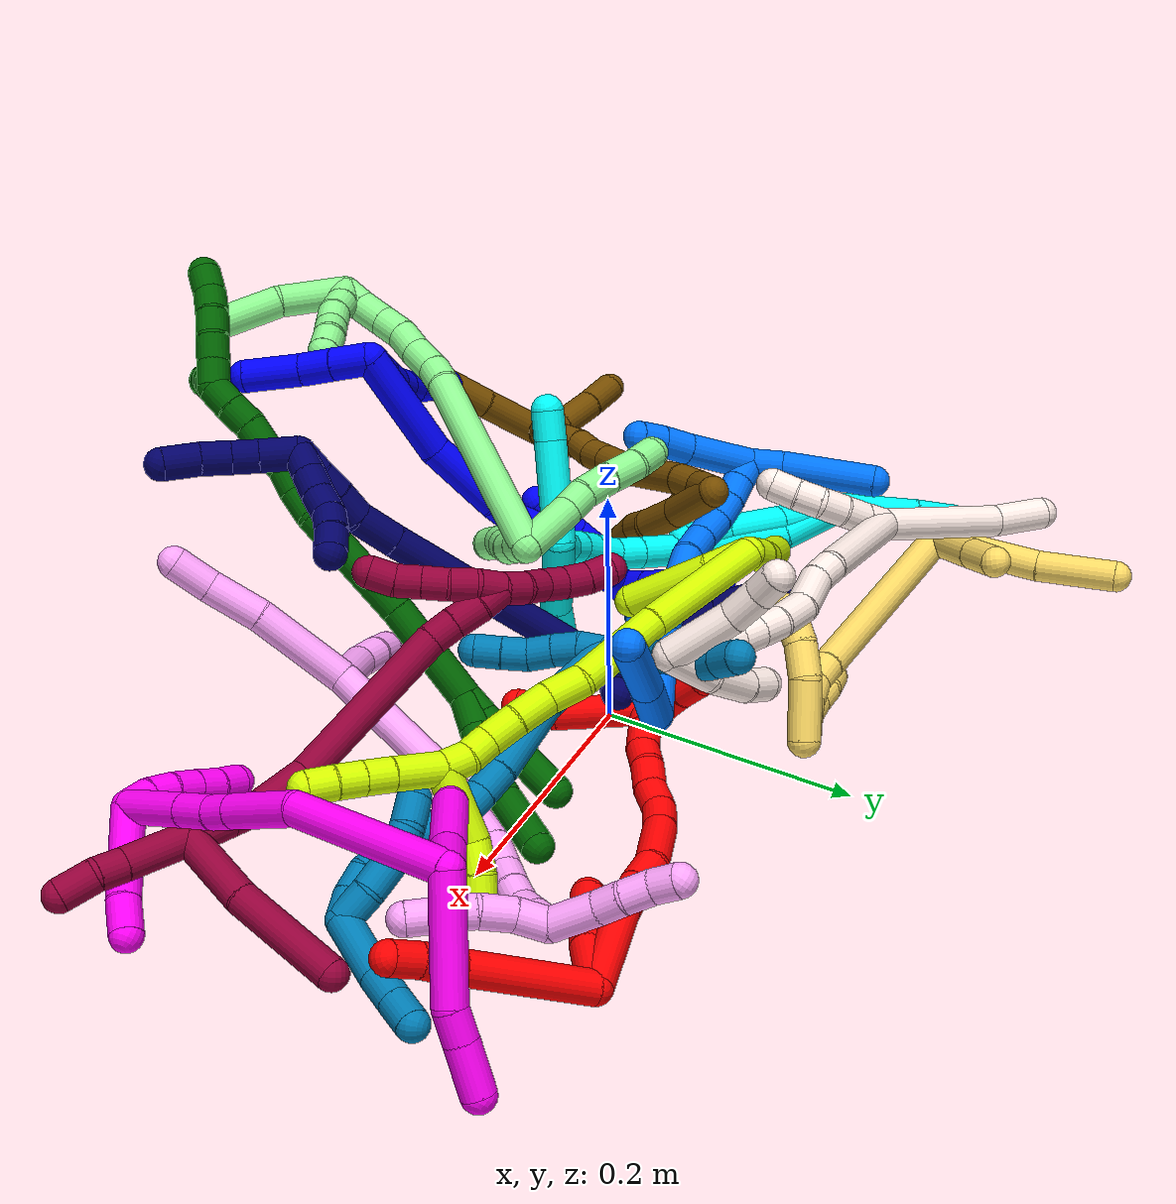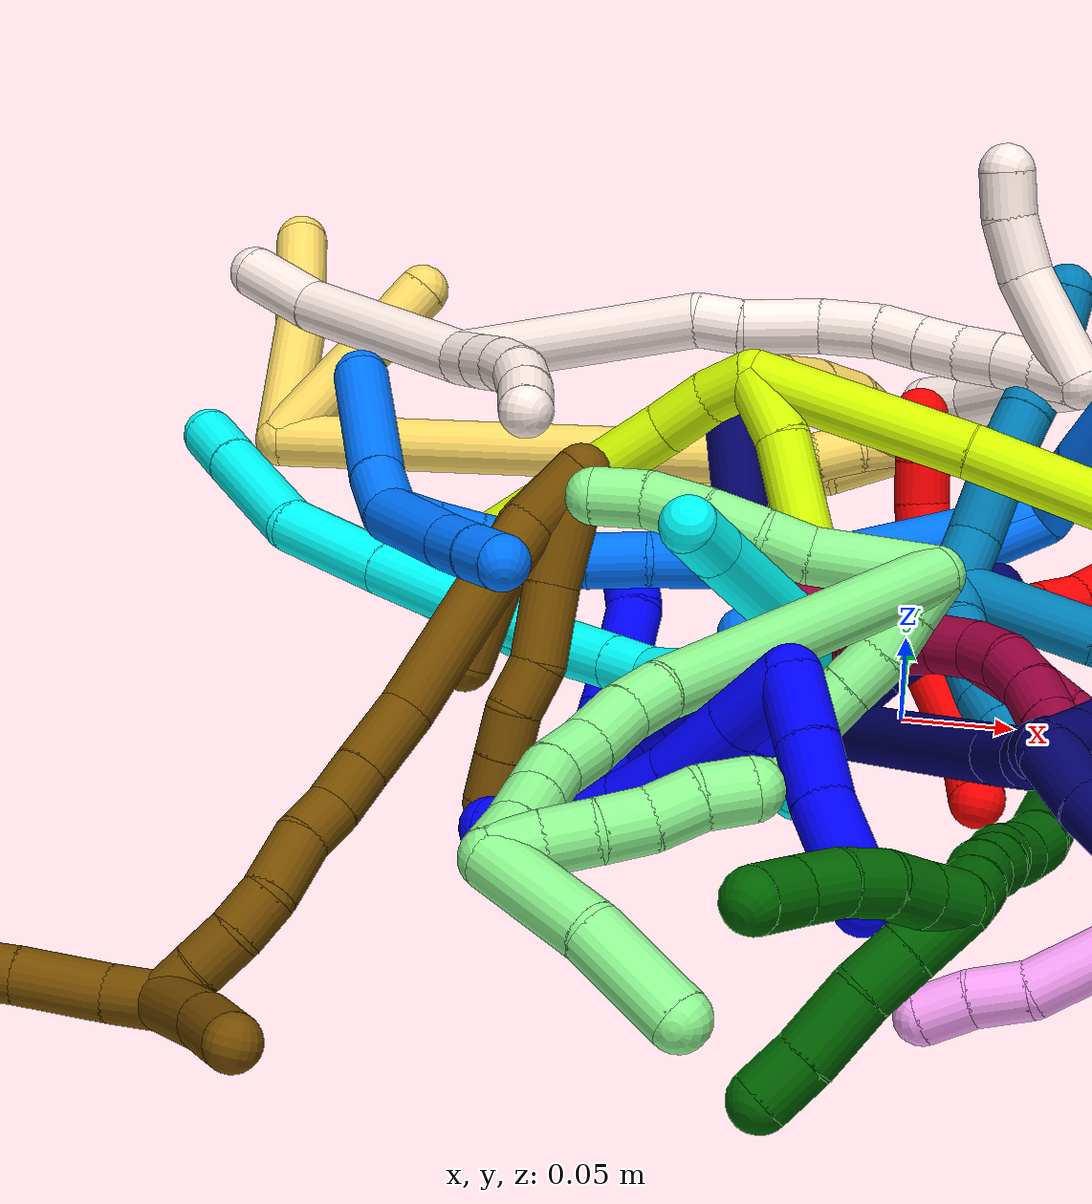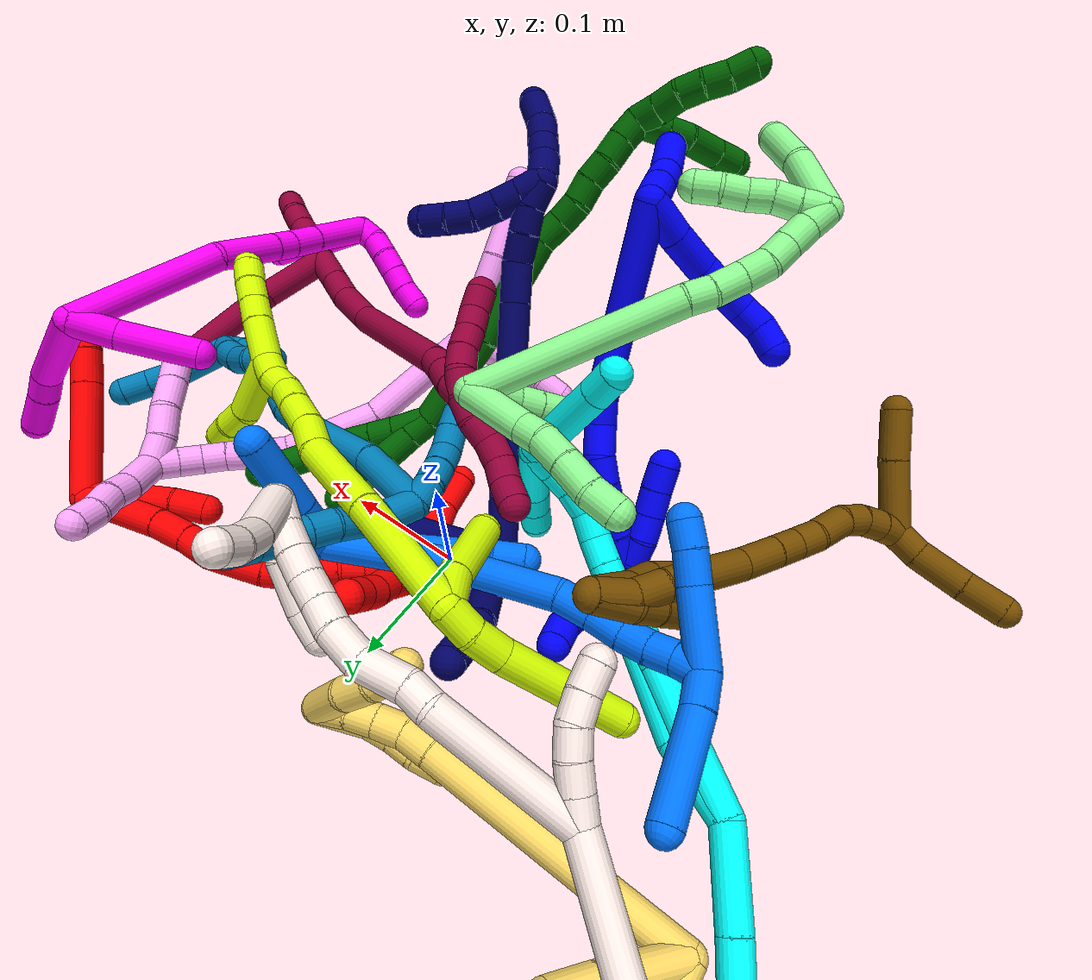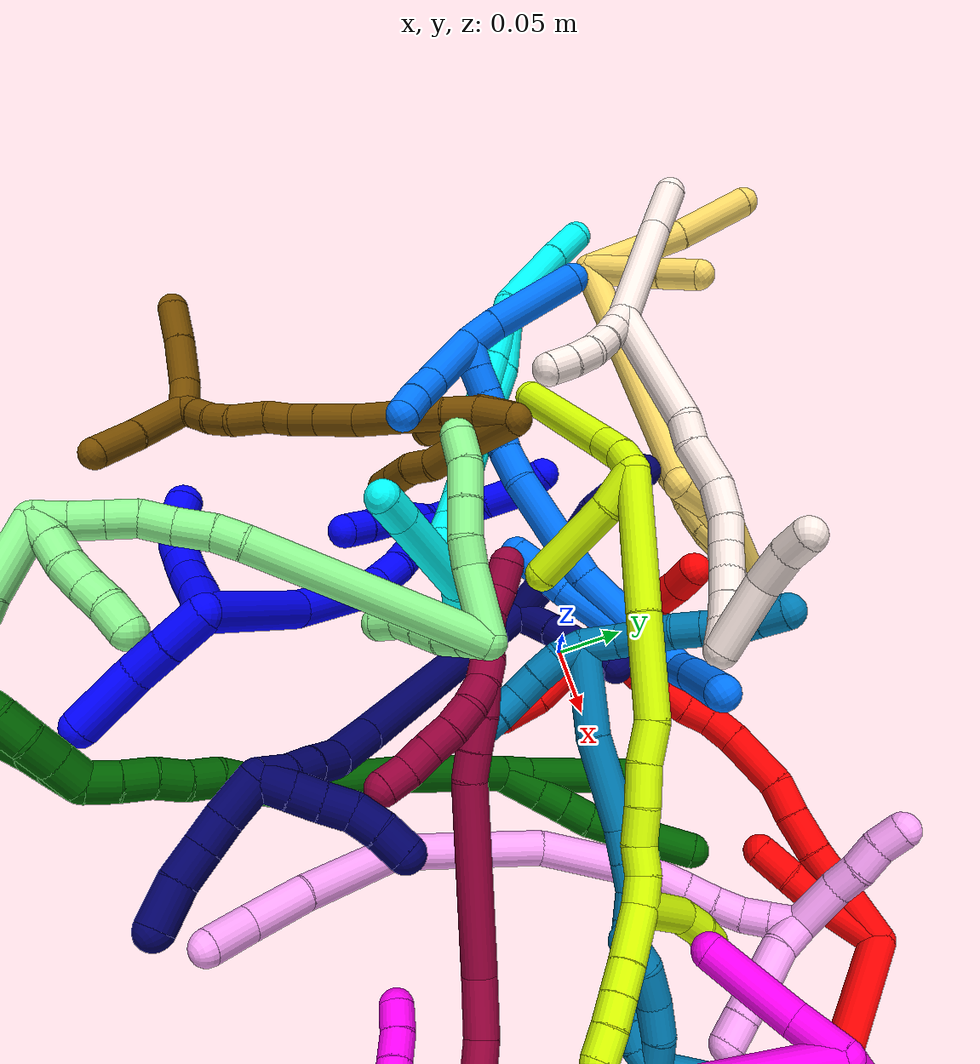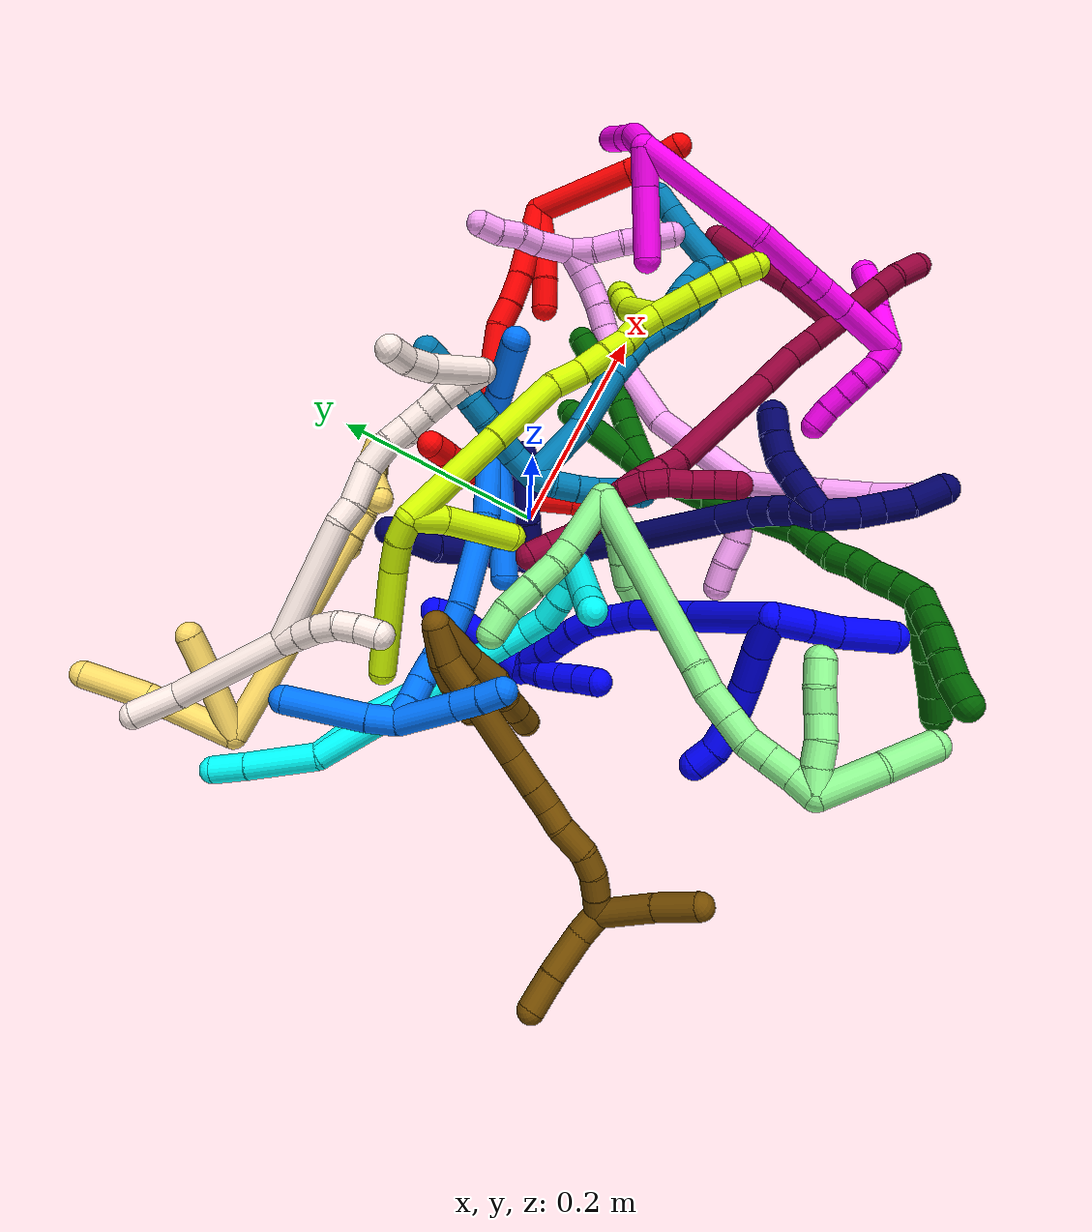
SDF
<sdf version="1.7">
 <world name="default">
  <plugin name="TubeGeneratorPlugin" filename="libtube_generator_plugin.so"/>
  <model name="photoneo_s_sensor">
   <static>1</static>
   <pose>0 0 2 1.57079 1.57079 3.14159</pose>
   <link name="link">
    <inertial><mass>0.1</mass></inertial>
    <sensor name="sensor" type="depth">
     <update_rate>30</update_rate>
     <camera>
      <horizontal_fov>1.22</horizontal_fov>
      <image><width>1920</width><height>1200</height><format>B8G8R8</format></image>
      <clip><near>0.1</near><far>4</far></clip>
      <depth_camera><output>points</output></depth_camera>
     </camera>
     <plugin name="camera_plugin" filename="libgazebo_ros_depth_camera.so">
      <baseline>0.2</baseline>
      <alwaysOn>1</alwaysOn>
      <updateRate>0.0</updateRate>
      <cameraName>camera_ir</cameraName>
      <imageTopicName>/camera/color/image_raw</imageTopicName>
      <cameraInfoTopicName>/camera/color/camera_info</cameraInfoTopicName>
      <depthImageTopicName>/camera/depth/image_raw</depthImageTopicName>
      <depthImageCameraInfoTopicName>/camera/depth/camera_info</depthImageCameraInfoTopicName>
      <pointCloudTopicName>/camera/depth/points</pointCloudTopicName>
      <frameName>fr_optical</frameName>
      <pointCloudCutoff>0.1</pointCloudCutoff>
      <pointCloudCutoffMax>2.0</pointCloudCutoffMax>
      <distortionK1>0</distortionK1>
      <distortionK2>0</distortionK2>
      <distortionK3>0</distortionK3>
      <distortionT1>0</distortionT1>
      <distortionT2>0</distortionT2>
      <CxPrime>0</CxPrime>
      <Cx>0</Cx>
      <Cy>0</Cy>
      <focalLength>0</focalLength>
      <hackBaseline>0</hackBaseline>
     </plugin>
    </sensor>
   </link>
  </model>
  <gravity>0 0 -9.8</gravity>
  <magnetic_field>6e-06 2.3e-05 -4.2e-05</magnetic_field>
  <atmosphere type="adiabatic"/>
  <physics name="default_physics" default="0" type="ode">
   <max_step_size>0.003</max_step_size>
   <real_time_factor>1</real_time_factor>
   <real_time_update_rate>1000</real_time_update_rate>
   <max_contacts>10000</max_contacts>
   <ode>
    <solver>
     <type>quick</type>
     <iters>100</iters>
     <sor>1.3</sor>
     <use_dynamic_moi_rescaling>0</use_dynamic_moi_rescaling>
    </solver>
    <constraints>
     <contact_max_correcting_vel>0</contact_max_correcting_vel>
     <contact_surface_layer>0.001</contact_surface_layer>
     <cfm>0</cfm>
     <erp>0.2</erp>
    </constraints>
   </ode>
  </physics>
  <scene><ambient>0.4 0.4 0.4 1</ambient><background>0.7 0.7 0.7 1</background><shadows>0</shadows></scene>
  <audio><device>default</device></audio>
  <spherical_coordinates>
   <surface_model>EARTH_WGS84</surface_model>
   <latitude_deg>0</latitude_deg>
   <longitude_deg>0</longitude_deg>
   <elevation>0</elevation>
   <heading_deg>0</heading_deg>
  </spherical_coordinates>
  <model name="bin">
   <static>1</static>
   <link name="bottom">
    <collision name="collision-bottom">
     <pose>0 0 -0.01 0 -0 0</pose>
     <geometry><box><size>0.8 0.6 0.02</size></box></geometry>
     <surface>
      <friction><ode><mu>100</mu><mu2>100</mu2></ode></friction>
      <contact><collide_bitmask>65535</collide_bitmask></contact>
     </surface>
    </collision>
   </link>
   <link name="west_wall">
    <collision name="collision-west_wall">
     <pose>-0.41 0 0.1 0 -0 0</pose>
     <geometry><box><size>0.02 0.6 0.2</size></box></geometry>
     <surface>
      <friction><ode><mu>100</mu><mu2>100</mu2></ode></friction>
      <contact><collide_bitmask>65535</collide_bitmask></contact>
     </surface>
    </collision>
   </link>
   <link name="east_wall">
    <collision name="collision-east_wall">
     <pose>0.41 0 0.1 0 -0 0</pose>
     <geometry><box><size>0.02 0.6 0.2</size></box></geometry>
     <surface>
      <friction><ode><mu>100</mu><mu2>100</mu2></ode></friction>
      <contact><collide_bitmask>65535</collide_bitmask></contact>
     </surface>
    </collision>
   </link>
   <link name="south_wall">
    <collision name="collision-south_wall">
     <pose>0 -0.31 0.1 0 -0 0</pose>
     <geometry><box><size>0.8 0.02 0.2</size></box></geometry>
     <surface>
      <friction><ode><mu>100</mu><mu2>100</mu2></ode></friction>
      <contact><collide_bitmask>65535</collide_bitmask></contact>
     </surface>
    </collision>
   </link>
   <link name="north_wall">
    <collision name="collision-north_wall">
     <pose>0 0.31 0.1 0 -0 0</pose>
     <geometry><box><size>0.8 0.02 0.2</size></box></geometry>
     <surface>
      <friction><ode><mu>100</mu><mu2>100</mu2></ode></friction>
      <contact><collide_bitmask>65535</collide_bitmask></contact>
     </surface>
    </collision>
   </link>
  </model>
  <model name="1">
   <static>0</static>
   <link name="1">
    <collision name="collision-cylinder-e_1_2_8">
     <pose>-0.01092 -0.002665 -0.011155 2.90706 -0.760905 -2.56868</pose>
     <geometry><cylinder><radius>0.0125</radius><length>0.031672</length></cylinder></geometry>
     <surface>
      <friction><ode><mu>1.16</mu><mu2>1.16</mu2><slip1>0</slip1><slip2>0</slip2></ode></friction>
      <contact><ode><kp>1e+06</kp><kd>1</kd><max_vel>0</max_vel><min_depth>0.001</min_depth></ode></contact>
     </surface>
    </collision>
    <visual name="visual-cylinder-e_1_2_8">
     <pose>-0.01092 -0.002665 -0.011155 2.90706 -0.760905 -2.56868</pose>
     <geometry><cylinder><radius>0.0125</radius><length>0.031672</length></cylinder></geometry>
     <material><ambient>0 0 1 1</ambient></material>
    </visual>
    <collision name="collision-cylinder-e_2_8_9">
     <pose>-0.03398 -0.008303 -0.032967 2.86958 -0.831735 -2.54059</pose>
     <geometry><cylinder><radius>0.0125</radius><length>0.03285</length></cylinder></geometry>
     <surface>
      <friction><ode><mu>1.16</mu><mu2>1.16</mu2><slip1>0</slip1><slip2>0</slip2></ode></friction>
      <contact><ode><kp>1e+06</kp><kd>1</kd><max_vel>0</max_vel><min_depth>0.001</min_depth></ode></contact>
     </surface>
    </collision>
    <visual name="visual-cylinder-e_2_8_9">
     <pose>-0.03398 -0.008303 -0.032967 2.86958 -0.831735 -2.54059</pose>
     <geometry><cylinder><radius>0.0125</radius><length>0.03285</length></cylinder></geometry>
     <material><ambient>0 0 1 1</ambient></material>
    </visual>
    <collision name="collision-cylinder-e_3_9_10">
     <pose>-0.055107 -0.011998 -0.050628 3.03884 -0.906198 -2.93115</pose>
     <geometry><cylinder><radius>0.0125</radius><length>0.022833</length></cylinder></geometry>
     <surface>
      <friction><ode><mu>1.16</mu><mu2>1.16</mu2><slip1>0</slip1><slip2>0</slip2></ode></friction>
      <contact><ode><kp>1e+06</kp><kd>1</kd><max_vel>0</max_vel><min_depth>0.001</min_depth></ode></contact>
     </surface>
    </collision>
    <visual name="visual-cylinder-e_3_9_10">
     <pose>-0.055107 -0.011998 -0.050628 3.03884 -0.906198 -2.93115</pose>
     <geometry><cylinder><radius>0.0125</radius><length>0.022833</length></cylinder></geometry>
     <material><ambient>0 0 1 1</ambient></material>
    </visual>
    <collision name="collision-cylinder-e_4_10_11">
     <pose>-0.072899 -0.012927 -0.064292 3.11052 -0.922976 -3.07912</pose>
     <geometry><cylinder><radius>0.0125</radius><length>0.022084</length></cylinder></geometry>
     <surface>
      <friction><ode><mu>1.16</mu><mu2>1.16</mu2><slip1>0</slip1><slip2>0</slip2></ode></friction>
      <contact><ode><kp>1e+06</kp><kd>1</kd><max_vel>0</max_vel><min_depth>0.001</min_depth></ode></contact>
     </surface>
    </collision>
    <visual name="visual-cylinder-e_4_10_11">
     <pose>-0.072899 -0.012927 -0.064292 3.11052 -0.922976 -3.07912</pose>
     <geometry><cylinder><radius>0.0125</radius><length>0.022084</length></cylinder></geometry>
     <material><ambient>0 0 1 1</ambient></material>
    </visual>
    <collision name="collision-cylinder-e_5_11_12">
     <pose>-0.08984 -0.01023 -0.076474 -2.65744 -0.916628 2.21351</pose>
     <geometry><cylinder><radius>0.0125</radius><length>0.020505</length></cylinder></geometry>
     <surface>
      <friction><ode><mu>1.16</mu><mu2>1.16</mu2><slip1>0</slip1><slip2>0</slip2></ode></friction>
      <contact><ode><kp>1e+06</kp><kd>1</kd><max_vel>0</max_vel><min_depth>0.001</min_depth></ode></contact>
     </surface>
    </collision>
    <visual name="visual-cylinder-e_5_11_12">
     <pose>-0.08984 -0.01023 -0.076474 -2.65744 -0.916628 2.21351</pose>
     <geometry><cylinder><radius>0.0125</radius><length>0.020505</length></cylinder></geometry>
     <material><ambient>0 0 1 1</ambient></material>
    </visual>
    <collision name="collision-cylinder-e_6_12_6">
     <pose>-0.103615 -0.002275 -0.088571 -2.48651 -0.597212 1.47214</pose>
     <geometry><cylinder><radius>0.0125</radius><length>0.020054</length></cylinder></geometry>
     <surface>
      <friction><ode><mu>1.16</mu><mu2>1.16</mu2><slip1>0</slip1><slip2>0</slip2></ode></friction>
      <contact><ode><kp>1e+06</kp><kd>1</kd><max_vel>0</max_vel><min_depth>0.001</min_depth></ode></contact>
     </surface>
    </collision>
    <visual name="visual-cylinder-e_6_12_6">
     <pose>-0.103615 -0.002275 -0.088571 -2.48651 -0.597212 1.47214</pose>
     <geometry><cylinder><radius>0.0125</radius><length>0.020054</length></cylinder></geometry>
     <material><ambient>0 0 1 1</ambient></material>
    </visual>
    <collision name="collision-cylinder-e_1_2_13">
     <pose>-0.002938 -0.01378 0.004166 1.27723 -0.201339 -0.149701</pose>
     <geometry><cylinder><radius>0.0125</radius><length>0.029385</length></cylinder></geometry>
     <surface>
      <friction><ode><mu>1.16</mu><mu2>1.16</mu2><slip1>0</slip1><slip2>0</slip2></ode></friction>
      <contact><ode><kp>1e+06</kp><kd>1</kd><max_vel>0</max_vel><min_depth>0.001</min_depth></ode></contact>
     </surface>
    </collision>
    <visual name="visual-cylinder-e_1_2_13">
     <pose>-0.002938 -0.01378 0.004166 1.27723 -0.201339 -0.149701</pose>
     <geometry><cylinder><radius>0.0125</radius><length>0.029385</length></cylinder></geometry>
     <material><ambient>0 0 1 1</ambient></material>
    </visual>
    <collision name="collision-cylinder-e_2_13_14">
     <pose>-0.008632 -0.03971 0.011676 1.30219 -0.215242 -0.164266</pose>
     <geometry><cylinder><radius>0.0125</radius><length>0.0258</length></cylinder></geometry>
     <surface>
      <friction><ode><mu>1.16</mu><mu2>1.16</mu2><slip1>0</slip1><slip2>0</slip2></ode></friction>
      <contact><ode><kp>1e+06</kp><kd>1</kd><max_vel>0</max_vel><min_depth>0.001</min_depth></ode></contact>
     </surface>
    </collision>
    <visual name="visual-cylinder-e_2_13_14">
     <pose>-0.008632 -0.03971 0.011676 1.30219 -0.215242 -0.164266</pose>
     <geometry><cylinder><radius>0.0125</radius><length>0.0258</length></cylinder></geometry>
     <material><ambient>0 0 1 1</ambient></material>
    </visual>
    <collision name="collision-cylinder-e_3_14_5">
     <pose>-0.013618 -0.072517 0.023413 1.18485 -0.099727 -0.067154</pose>
     <geometry><cylinder><radius>0.0125</radius><length>0.044815</length></cylinder></geometry>
     <surface>
      <friction><ode><mu>1.16</mu><mu2>1.16</mu2><slip1>0</slip1><slip2>0</slip2></ode></friction>
      <contact><ode><kp>1e+06</kp><kd>1</kd><max_vel>0</max_vel><min_depth>0.001</min_depth></ode></contact>
     </surface>
    </collision>
    <visual name="visual-cylinder-e_3_14_5">
     <pose>-0.013618 -0.072517 0.023413 1.18485 -0.099727 -0.067154</pose>
     <geometry><cylinder><radius>0.0125</radius><length>0.044815</length></cylinder></geometry>
     <material><ambient>0 0 1 1</ambient></material>
    </visual>
    <collision name="collision-cylinder-e_1_2_15">
     <pose>0.004122 0.000294 -0.042945 -3.13475 0.095688 -2.99896</pose>
     <geometry><cylinder><radius>0.0125</radius><length>0.086288</length></cylinder></geometry>
     <surface>
      <friction><ode><mu>1.16</mu><mu2>1.16</mu2><slip1>0</slip1><slip2>0</slip2></ode></friction>
      <contact><ode><kp>1e+06</kp><kd>1</kd><max_vel>0</max_vel><min_depth>0.001</min_depth></ode></contact>
     </surface>
    </collision>
    <visual name="visual-cylinder-e_1_2_15">
     <pose>0.004122 0.000294 -0.042945 -3.13475 0.095688 -2.99896</pose>
     <geometry><cylinder><radius>0.0125</radius><length>0.086288</length></cylinder></geometry>
     <material><ambient>0 0 1 1</ambient></material>
    </visual>
    <collision name="collision-cylinder-e_2_15_16">
     <pose>0.011399 0.00769 -0.115941 -2.90949 0.101806 -0.824041</pose>
     <geometry><cylinder><radius>0.0125</radius><length>0.062077</length></cylinder></geometry>
     <surface>
      <friction><ode><mu>1.16</mu><mu2>1.16</mu2><slip1>0</slip1><slip2>0</slip2></ode></friction>
      <contact><ode><kp>1e+06</kp><kd>1</kd><max_vel>0</max_vel><min_depth>0.001</min_depth></ode></contact>
     </surface>
    </collision>
    <visual name="visual-cylinder-e_2_15_16">
     <pose>0.011399 0.00769 -0.115941 -2.90949 0.101806 -0.824041</pose>
     <geometry><cylinder><radius>0.0125</radius><length>0.062077</length></cylinder></geometry>
     <material><ambient>0 0 1 1</ambient></material>
    </visual>
    <collision name="collision-cylinder-e_3_16_17">
     <pose>0.013796 0.017206 -0.155962 -2.90418 -0.073639 0.599115</pose>
     <geometry><cylinder><radius>0.0125</radius><length>0.020576</length></cylinder></geometry>
     <surface>
      <friction><ode><mu>1.16</mu><mu2>1.16</mu2><slip1>0</slip1><slip2>0</slip2></ode></friction>
      <contact><ode><kp>1e+06</kp><kd>1</kd><max_vel>0</max_vel><min_depth>0.001</min_depth></ode></contact>
     </surface>
    </collision>
    <visual name="visual-cylinder-e_3_16_17">
     <pose>0.013796 0.017206 -0.155962 -2.90418 -0.073639 0.599115</pose>
     <geometry><cylinder><radius>0.0125</radius><length>0.020576</length></cylinder></geometry>
     <material><ambient>0 0 1 1</ambient></material>
    </visual>
    <collision name="collision-cylinder-e_4_17_18">
     <pose>0.012049 0.025687 -0.176722 -2.62917 -0.079833 0.302572</pose>
     <geometry><cylinder><radius>0.0125</radius><length>0.024834</length></cylinder></geometry>
     <surface>
      <friction><ode><mu>1.16</mu><mu2>1.16</mu2><slip1>0</slip1><slip2>0</slip2></ode></friction>
      <contact><ode><kp>1e+06</kp><kd>1</kd><max_vel>0</max_vel><min_depth>0.001</min_depth></ode></contact>
     </surface>
    </collision>
    <visual name="visual-cylinder-e_4_17_18">
     <pose>0.012049 0.025687 -0.176722 -2.62917 -0.079833 0.302572</pose>
     <geometry><cylinder><radius>0.0125</radius><length>0.024834</length></cylinder></geometry>
     <material><ambient>0 0 1 1</ambient></material>
    </visual>
    <collision name="collision-cylinder-e_5_18_19">
     <pose>0.008031 0.034749 -0.197094 -2.83891 -0.292837 1.53726</pose>
     <geometry><cylinder><radius>0.0125</radius><length>0.020975</length></cylinder></geometry>
     <surface>
      <friction><ode><mu>1.16</mu><mu2>1.16</mu2><slip1>0</slip1><slip2>0</slip2></ode></friction>
      <contact><ode><kp>1e+06</kp><kd>1</kd><max_vel>0</max_vel><min_depth>0.001</min_depth></ode></contact>
     </surface>
    </collision>
    <visual name="visual-cylinder-e_5_18_19">
     <pose>0.008031 0.034749 -0.197094 -2.83891 -0.292837 1.53726</pose>
     <geometry><cylinder><radius>0.0125</radius><length>0.020975</length></cylinder></geometry>
     <material><ambient>0 0 1 1</ambient></material>
    </visual>
    <collision name="collision-cylinder-e_6_19_20">
     <pose>0.00113 0.039311 -0.216584 -2.98443 -0.368591 2.34222</pose>
     <geometry><cylinder><radius>0.0125</radius><length>0.021503</length></cylinder></geometry>
     <surface>
      <friction><ode><mu>1.16</mu><mu2>1.16</mu2><slip1>0</slip1><slip2>0</slip2></ode></friction>
      <contact><ode><kp>1e+06</kp><kd>1</kd><max_vel>0</max_vel><min_depth>0.001</min_depth></ode></contact>
     </surface>
    </collision>
    <visual name="visual-cylinder-e_6_19_20">
     <pose>0.00113 0.039311 -0.216584 -2.98443 -0.368591 2.34222</pose>
     <geometry><cylinder><radius>0.0125</radius><length>0.021503</length></cylinder></geometry>
     <material><ambient>0 0 1 1</ambient></material>
    </visual>
    <collision name="collision-cylinder-e_7_20_21">
     <pose>-0.006845 0.0424 -0.235969 -2.98272 -0.403745 2.39969</pose>
     <geometry><cylinder><radius>0.0125</radius><length>0.020877</length></cylinder></geometry>
     <surface>
      <friction><ode><mu>1.16</mu><mu2>1.16</mu2><slip1>0</slip1><slip2>0</slip2></ode></friction>
      <contact><ode><kp>1e+06</kp><kd>1</kd><max_vel>0</max_vel><min_depth>0.001</min_depth></ode></contact>
     </surface>
    </collision>
    <visual name="visual-cylinder-e_7_20_21">
     <pose>-0.006845 0.0424 -0.235969 -2.98272 -0.403745 2.39969</pose>
     <geometry><cylinder><radius>0.0125</radius><length>0.020877</length></cylinder></geometry>
     <material><ambient>0 0 1 1</ambient></material>
    </visual>
    <collision name="collision-cylinder-e_8_21_22">
     <pose>-0.014195 0.045071 -0.256273 -3.03558 -0.290038 2.44466</pose>
     <geometry><cylinder><radius>0.0125</radius><length>0.022722</length></cylinder></geometry>
     <surface>
      <friction><ode><mu>1.16</mu><mu2>1.16</mu2><slip1>0</slip1><slip2>0</slip2></ode></friction>
      <contact><ode><kp>1e+06</kp><kd>1</kd><max_vel>0</max_vel><min_depth>0.001</min_depth></ode></contact>
     </surface>
    </collision>
    <visual name="visual-cylinder-e_8_21_22">
     <pose>-0.014195 0.045071 -0.256273 -3.03558 -0.290038 2.44466</pose>
     <geometry><cylinder><radius>0.0125</radius><length>0.022722</length></cylinder></geometry>
     <material><ambient>0 0 1 1</ambient></material>
    </visual>
    <collision name="collision-cylinder-e_9_22_1">
     <pose>-0.021467 0.046254 -0.276334 -3.13816 -0.410815 3.1251</pose>
     <geometry><cylinder><radius>0.0125</radius><length>0.020149</length></cylinder></geometry>
     <surface>
      <friction><ode><mu>1.16</mu><mu2>1.16</mu2><slip1>0</slip1><slip2>0</slip2></ode></friction>
      <contact><ode><kp>1e+06</kp><kd>1</kd><max_vel>0</max_vel><min_depth>0.001</min_depth></ode></contact>
     </surface>
    </collision>
    <visual name="visual-cylinder-e_9_22_1">
     <pose>-0.021467 0.046254 -0.276334 -3.13816 -0.410815 3.1251</pose>
     <geometry><cylinder><radius>0.0125</radius><length>0.020149</length></cylinder></geometry>
     <material><ambient>0 0 1 1</ambient></material>
    </visual>
    <collision name="collision-cylinder-e_1_1_23">
     <pose>-0.0256 0.046884 -0.275589 -0.059824 -0.010946 0.000328</pose>
     <geometry><cylinder><radius>0.0125</radius><length>0.02</length></cylinder></geometry>
     <surface>
      <friction><ode><mu>1.16</mu><mu2>1.16</mu2><slip1>0</slip1><slip2>0</slip2></ode></friction>
      <contact><ode><kp>1e+06</kp><kd>1</kd><max_vel>0</max_vel><min_depth>0.001</min_depth></ode></contact>
     </surface>
    </collision>
    <visual name="visual-cylinder-e_1_1_23">
     <pose>-0.0256 0.046884 -0.275589 -0.059824 -0.010946 0.000328</pose>
     <geometry><cylinder><radius>0.0125</radius><length>0.02</length></cylinder></geometry>
     <material><ambient>0 0 1 1</ambient></material>
    </visual>
    <collision name="collision-cylinder-e_2_23_24">
     <pose>-0.028205 0.046387 -0.255986 0.113291 -0.252246 -0.01438</pose>
     <geometry><cylinder><radius>0.0125</radius><length>0.02</length></cylinder></geometry>
     <surface>
      <friction><ode><mu>1.16</mu><mu2>1.16</mu2><slip1>0</slip1><slip2>0</slip2></ode></friction>
      <contact><ode><kp>1e+06</kp><kd>1</kd><max_vel>0</max_vel><min_depth>0.001</min_depth></ode></contact>
     </surface>
    </collision>
    <visual name="visual-cylinder-e_2_23_24">
     <pose>-0.028205 0.046387 -0.255986 0.113291 -0.252246 -0.01438</pose>
     <geometry><cylinder><radius>0.0125</radius><length>0.02</length></cylinder></geometry>
     <material><ambient>0 0 1 1</ambient></material>
    </visual>
    <collision name="collision-cylinder-e_3_24_25">
     <pose>-0.032392 0.04217 -0.237016 0.32232 -0.169919 -0.027689</pose>
     <geometry><cylinder><radius>0.0125</radius><length>0.02</length></cylinder></geometry>
     <surface>
      <friction><ode><mu>1.16</mu><mu2>1.16</mu2><slip1>0</slip1><slip2>0</slip2></ode></friction>
      <contact><ode><kp>1e+06</kp><kd>1</kd><max_vel>0</max_vel><min_depth>0.001</min_depth></ode></contact>
     </surface>
    </collision>
    <visual name="visual-cylinder-e_3_24_25">
     <pose>-0.032392 0.04217 -0.237016 0.32232 -0.169919 -0.027689</pose>
     <geometry><cylinder><radius>0.0125</radius><length>0.02</length></cylinder></geometry>
     <material><ambient>0 0 1 1</ambient></material>
    </visual>
    <collision name="collision-cylinder-e_4_25_26">
     <pose>-0.035329 0.03602 -0.218219 0.310168 -0.124925 -0.019556</pose>
     <geometry><cylinder><radius>0.0125</radius><length>0.02</length></cylinder></geometry>
     <surface>
      <friction><ode><mu>1.16</mu><mu2>1.16</mu2><slip1>0</slip1><slip2>0</slip2></ode></friction>
      <contact><ode><kp>1e+06</kp><kd>1</kd><max_vel>0</max_vel><min_depth>0.001</min_depth></ode></contact>
     </surface>
    </collision>
    <visual name="visual-cylinder-e_4_25_26">
     <pose>-0.035329 0.03602 -0.218219 0.310168 -0.124925 -0.019556</pose>
     <geometry><cylinder><radius>0.0125</radius><length>0.02</length></cylinder></geometry>
     <material><ambient>0 0 1 1</ambient></material>
    </visual>
    <collision name="collision-cylinder-e_5_26_4">
     <pose>-0.038324 0.029989 -0.199393 0.309888 -0.175815 -0.027531</pose>
     <geometry><cylinder><radius>0.0125</radius><length>0.02</length></cylinder></geometry>
     <surface>
      <friction><ode><mu>1.16</mu><mu2>1.16</mu2><slip1>0</slip1><slip2>0</slip2></ode></friction>
      <contact><ode><kp>1e+06</kp><kd>1</kd><max_vel>0</max_vel><min_depth>0.001</min_depth></ode></contact>
     </surface>
    </collision>
    <visual name="visual-cylinder-e_5_26_4">
     <pose>-0.038324 0.029989 -0.199393 0.309888 -0.175815 -0.027531</pose>
     <geometry><cylinder><radius>0.0125</radius><length>0.02</length></cylinder></geometry>
     <material><ambient>0 0 1 1</ambient></material>
    </visual>
    <collision name="collision-cylinder-e_1_1_27">
     <pose>-0.016033 0.058188 -0.285829 -1.59254 0.671341 -0.684984</pose>
     <geometry><cylinder><radius>0.0125</radius><length>0.030408</length></cylinder></geometry>
     <surface>
      <friction><ode><mu>1.16</mu><mu2>1.16</mu2><slip1>0</slip1><slip2>0</slip2></ode></friction>
      <contact><ode><kp>1e+06</kp><kd>1</kd><max_vel>0</max_vel><min_depth>0.001</min_depth></ode></contact>
     </surface>
    </collision>
    <visual name="visual-cylinder-e_1_1_27">
     <pose>-0.016033 0.058188 -0.285829 -1.59254 0.671341 -0.684984</pose>
     <geometry><cylinder><radius>0.0125</radius><length>0.030408</length></cylinder></geometry>
     <material><ambient>0 0 1 1</ambient></material>
    </visual>
    <collision name="collision-cylinder-e_2_27_28">
     <pose>0.000112 0.078445 -0.286078 -1.56956 0.675022 -0.674247</pose>
     <geometry><cylinder><radius>0.0125</radius><length>0.021404</length></cylinder></geometry>
     <surface>
      <friction><ode><mu>1.16</mu><mu2>1.16</mu2><slip1>0</slip1><slip2>0</slip2></ode></friction>
      <contact><ode><kp>1e+06</kp><kd>1</kd><max_vel>0</max_vel><min_depth>0.001</min_depth></ode></contact>
     </surface>
    </collision>
    <visual name="visual-cylinder-e_2_27_28">
     <pose>0.000112 0.078445 -0.286078 -1.56956 0.675022 -0.674247</pose>
     <geometry><cylinder><radius>0.0125</radius><length>0.021404</length></cylinder></geometry>
     <material><ambient>0 0 1 1</ambient></material>
    </visual>
    <collision name="collision-cylinder-e_3_28_29">
     <pose>0.014861 0.097892 -0.288741 -1.80729 0.615079 -0.766624</pose>
     <geometry><cylinder><radius>0.0125</radius><length>0.02794</length></cylinder></geometry>
     <surface>
      <friction><ode><mu>1.16</mu><mu2>1.16</mu2><slip1>0</slip1><slip2>0</slip2></ode></friction>
      <contact><ode><kp>1e+06</kp><kd>1</kd><max_vel>0</max_vel><min_depth>0.001</min_depth></ode></contact>
     </surface>
    </collision>
    <visual name="visual-cylinder-e_3_28_29">
     <pose>0.014861 0.097892 -0.288741 -1.80729 0.615079 -0.766624</pose>
     <geometry><cylinder><radius>0.0125</radius><length>0.02794</length></cylinder></geometry>
     <material><ambient>0 0 1 1</ambient></material>
    </visual>
    <collision name="collision-cylinder-e_4_29_3">
     <pose>0.025791 0.11843 -0.293657 -1.8039 0.287275 -0.361979</pose>
     <geometry><cylinder><radius>0.0125</radius><length>0.020248</length></cylinder></geometry>
     <surface>
      <friction><ode><mu>1.16</mu><mu2>1.16</mu2><slip1>0</slip1><slip2>0</slip2></ode></friction>
      <contact><ode><kp>1e+06</kp><kd>1</kd><max_vel>0</max_vel><min_depth>0.001</min_depth></ode></contact>
     </surface>
    </collision>
    <visual name="visual-cylinder-e_4_29_3">
     <pose>0.025791 0.11843 -0.293657 -1.8039 0.287275 -0.361979</pose>
     <geometry><cylinder><radius>0.0125</radius><length>0.020248</length></cylinder></geometry>
     <material><ambient>0 0 1 1</ambient></material>
    </visual>
    <collision name="collision-sphere-3">
     <pose>0.028659 0.127877 -0.295899 0 -0 0</pose>
     <geometry><sphere><radius>0.0125</radius></sphere></geometry>
     <surface>
      <friction><ode><mu>1.16</mu><mu2>1.16</mu2><slip1>0</slip1><slip2>0</slip2></ode></friction>
      <contact><ode><kp>1e+06</kp><kd>1</kd><max_vel>0</max_vel><min_depth>0.001</min_depth></ode></contact>
     </surface>
    </collision>
    <visual name="visual-sphere-3">
     <pose>0.028659 0.127877 -0.295899 0 -0 0</pose>
     <geometry><sphere><radius>0.0125</radius></sphere></geometry>
     <material><ambient>0 0 1 1</ambient></material>
    </visual>
    <collision name="collision-sphere-29">
     <pose>0.022922 0.108983 -0.291414 0 -0 0</pose>
     <geometry><sphere><radius>0.0125</radius></sphere></geometry>
     <surface>
      <friction><ode><mu>1.16</mu><mu2>1.16</mu2><slip1>0</slip1><slip2>0</slip2></ode></friction>
      <contact><ode><kp>1e+06</kp><kd>1</kd><max_vel>0</max_vel><min_depth>0.001</min_depth></ode></contact>
     </surface>
    </collision>
    <visual name="visual-sphere-29">
     <pose>0.022922 0.108983 -0.291414 0 -0 0</pose>
     <geometry><sphere><radius>0.0125</radius></sphere></geometry>
     <material><ambient>0 0 1 1</ambient></material>
    </visual>
    <collision name="collision-sphere-28">
     <pose>0.0068 0.0868 -0.286067 0 -0 0</pose>
     <geometry><sphere><radius>0.0125</radius></sphere></geometry>
     <surface>
      <friction><ode><mu>1.16</mu><mu2>1.16</mu2><slip1>0</slip1><slip2>0</slip2></ode></friction>
      <contact><ode><kp>1e+06</kp><kd>1</kd><max_vel>0</max_vel><min_depth>0.001</min_depth></ode></contact>
     </surface>
    </collision>
    <visual name="visual-sphere-28">
     <pose>0.0068 0.0868 -0.286067 0 -0 0</pose>
     <geometry><sphere><radius>0.0125</radius></sphere></geometry>
     <material><ambient>0 0 1 1</ambient></material>
    </visual>
    <collision name="collision-sphere-27">
     <pose>-0.006576 0.070089 -0.286088 0 -0 0</pose>
     <geometry><sphere><radius>0.0125</radius></sphere></geometry>
     <surface>
      <friction><ode><mu>1.16</mu><mu2>1.16</mu2><slip1>0</slip1><slip2>0</slip2></ode></friction>
      <contact><ode><kp>1e+06</kp><kd>1</kd><max_vel>0</max_vel><min_depth>0.001</min_depth></ode></contact>
     </surface>
    </collision>
    <visual name="visual-sphere-27">
     <pose>-0.006576 0.070089 -0.286088 0 -0 0</pose>
     <geometry><sphere><radius>0.0125</radius></sphere></geometry>
     <material><ambient>0 0 1 1</ambient></material>
    </visual>
    <collision name="collision-sphere-4">
     <pose>-0.040073 0.026986 -0.190017 0 -0 0</pose>
     <geometry><sphere><radius>0.0125</radius></sphere></geometry>
     <surface>
      <friction><ode><mu>1.16</mu><mu2>1.16</mu2><slip1>0</slip1><slip2>0</slip2></ode></friction>
      <contact><ode><kp>1e+06</kp><kd>1</kd><max_vel>0</max_vel><min_depth>0.001</min_depth></ode></contact>
     </surface>
    </collision>
    <visual name="visual-sphere-4">
     <pose>-0.040073 0.026986 -0.190017 0 -0 0</pose>
     <geometry><sphere><radius>0.0125</radius></sphere></geometry>
     <material><ambient>0 0 1 1</ambient></material>
    </visual>
    <collision name="collision-sphere-26">
     <pose>-0.036575 0.032991 -0.20877 0 -0 0</pose>
     <geometry><sphere><radius>0.0125</radius></sphere></geometry>
     <surface>
      <friction><ode><mu>1.16</mu><mu2>1.16</mu2><slip1>0</slip1><slip2>0</slip2></ode></friction>
      <contact><ode><kp>1e+06</kp><kd>1</kd><max_vel>0</max_vel><min_depth>0.001</min_depth></ode></contact>
     </surface>
    </collision>
    <visual name="visual-sphere-26">
     <pose>-0.036575 0.032991 -0.20877 0 -0 0</pose>
     <geometry><sphere><radius>0.0125</radius></sphere></geometry>
     <material><ambient>0 0 1 1</ambient></material>
    </visual>
    <collision name="collision-sphere-25">
     <pose>-0.034083 0.039048 -0.227668 0 -0 0</pose>
     <geometry><sphere><radius>0.0125</radius></sphere></geometry>
     <surface>
      <friction><ode><mu>1.16</mu><mu2>1.16</mu2><slip1>0</slip1><slip2>0</slip2></ode></friction>
      <contact><ode><kp>1e+06</kp><kd>1</kd><max_vel>0</max_vel><min_depth>0.001</min_depth></ode></contact>
     </surface>
    </collision>
    <visual name="visual-sphere-25">
     <pose>-0.034083 0.039048 -0.227668 0 -0 0</pose>
     <geometry><sphere><radius>0.0125</radius></sphere></geometry>
     <material><ambient>0 0 1 1</ambient></material>
    </visual>
    <collision name="collision-sphere-24">
     <pose>-0.030701 0.045292 -0.246364 0 -0 0</pose>
     <geometry><sphere><radius>0.0125</radius></sphere></geometry>
     <surface>
      <friction><ode><mu>1.16</mu><mu2>1.16</mu2><slip1>0</slip1><slip2>0</slip2></ode></friction>
      <contact><ode><kp>1e+06</kp><kd>1</kd><max_vel>0</max_vel><min_depth>0.001</min_depth></ode></contact>
     </surface>
    </collision>
    <visual name="visual-sphere-24">
     <pose>-0.030701 0.045292 -0.246364 0 -0 0</pose>
     <geometry><sphere><radius>0.0125</radius></sphere></geometry>
     <material><ambient>0 0 1 1</ambient></material>
    </visual>
    <collision name="collision-sphere-23">
     <pose>-0.025709 0.047482 -0.265607 0 -0 0</pose>
     <geometry><sphere><radius>0.0125</radius></sphere></geometry>
     <surface>
      <friction><ode><mu>1.16</mu><mu2>1.16</mu2><slip1>0</slip1><slip2>0</slip2></ode></friction>
      <contact><ode><kp>1e+06</kp><kd>1</kd><max_vel>0</max_vel><min_depth>0.001</min_depth></ode></contact>
     </surface>
    </collision>
    <visual name="visual-sphere-23">
     <pose>-0.025709 0.047482 -0.265607 0 -0 0</pose>
     <geometry><sphere><radius>0.0125</radius></sphere></geometry>
     <material><ambient>0 0 1 1</ambient></material>
    </visual>
    <collision name="collision-sphere-1">
     <pose>-0.02549 0.046286 -0.28557 0 -0 0</pose>
     <geometry><sphere><radius>0.0125</radius></sphere></geometry>
     <surface>
      <friction><ode><mu>1.16</mu><mu2>1.16</mu2><slip1>0</slip1><slip2>0</slip2></ode></friction>
      <contact><ode><kp>1e+06</kp><kd>1</kd><max_vel>0</max_vel><min_depth>0.001</min_depth></ode></contact>
     </surface>
    </collision>
    <visual name="visual-sphere-1">
     <pose>-0.02549 0.046286 -0.28557 0 -0 0</pose>
     <geometry><sphere><radius>0.0125</radius></sphere></geometry>
     <material><ambient>0 0 1 1</ambient></material>
    </visual>
    <collision name="collision-sphere-22">
     <pose>-0.017444 0.046223 -0.267098 0 -0 0</pose>
     <geometry><sphere><radius>0.0125</radius></sphere></geometry>
     <surface>
      <friction><ode><mu>1.16</mu><mu2>1.16</mu2><slip1>0</slip1><slip2>0</slip2></ode></friction>
      <contact><ode><kp>1e+06</kp><kd>1</kd><max_vel>0</max_vel><min_depth>0.001</min_depth></ode></contact>
     </surface>
    </collision>
    <visual name="visual-sphere-22">
     <pose>-0.017444 0.046223 -0.267098 0 -0 0</pose>
     <geometry><sphere><radius>0.0125</radius></sphere></geometry>
     <material><ambient>0 0 1 1</ambient></material>
    </visual>
    <collision name="collision-sphere-21">
     <pose>-0.010946 0.043919 -0.245447 0 -0 0</pose>
     <geometry><sphere><radius>0.0125</radius></sphere></geometry>
     <surface>
      <friction><ode><mu>1.16</mu><mu2>1.16</mu2><slip1>0</slip1><slip2>0</slip2></ode></friction>
      <contact><ode><kp>1e+06</kp><kd>1</kd><max_vel>0</max_vel><min_depth>0.001</min_depth></ode></contact>
     </surface>
    </collision>
    <visual name="visual-sphere-21">
     <pose>-0.010946 0.043919 -0.245447 0 -0 0</pose>
     <geometry><sphere><radius>0.0125</radius></sphere></geometry>
     <material><ambient>0 0 1 1</ambient></material>
    </visual>
    <collision name="collision-sphere-12">
     <pose>-0.097976 -0.007326 -0.081996 0 -0 0</pose>
     <geometry><sphere><radius>0.0125</radius></sphere></geometry>
     <surface>
      <friction><ode><mu>1.16</mu><mu2>1.16</mu2><slip1>0</slip1><slip2>0</slip2></ode></friction>
      <contact><ode><kp>1e+06</kp><kd>1</kd><max_vel>0</max_vel><min_depth>0.001</min_depth></ode></contact>
     </surface>
    </collision>
    <visual name="visual-sphere-12">
     <pose>-0.097976 -0.007326 -0.081996 0 -0 0</pose>
     <geometry><sphere><radius>0.0125</radius></sphere></geometry>
     <material><ambient>0 0 1 1</ambient></material>
    </visual>
    <collision name="collision-sphere-11">
     <pose>-0.081704 -0.013134 -0.070952 0 -0 0</pose>
     <geometry><sphere><radius>0.0125</radius></sphere></geometry>
     <surface>
      <friction><ode><mu>1.16</mu><mu2>1.16</mu2><slip1>0</slip1><slip2>0</slip2></ode></friction>
      <contact><ode><kp>1e+06</kp><kd>1</kd><max_vel>0</max_vel><min_depth>0.001</min_depth></ode></contact>
     </surface>
    </collision>
    <visual name="visual-sphere-11">
     <pose>-0.081704 -0.013134 -0.070952 0 -0 0</pose>
     <geometry><sphere><radius>0.0125</radius></sphere></geometry>
     <material><ambient>0 0 1 1</ambient></material>
    </visual>
    <collision name="collision-sphere-10">
     <pose>-0.064094 -0.01272 -0.057632 0 -0 0</pose>
     <geometry><sphere><radius>0.0125</radius></sphere></geometry>
     <surface>
      <friction><ode><mu>1.16</mu><mu2>1.16</mu2><slip1>0</slip1><slip2>0</slip2></ode></friction>
      <contact><ode><kp>1e+06</kp><kd>1</kd><max_vel>0</max_vel><min_depth>0.001</min_depth></ode></contact>
     </surface>
    </collision>
    <visual name="visual-sphere-10">
     <pose>-0.064094 -0.01272 -0.057632 0 -0 0</pose>
     <geometry><sphere><radius>0.0125</radius></sphere></geometry>
     <material><ambient>0 0 1 1</ambient></material>
    </visual>
    <collision name="collision-sphere-9">
     <pose>-0.04612 -0.011276 -0.043624 0 -0 0</pose>
     <geometry><sphere><radius>0.0125</radius></sphere></geometry>
     <surface>
      <friction><ode><mu>1.16</mu><mu2>1.16</mu2><slip1>0</slip1><slip2>0</slip2></ode></friction>
      <contact><ode><kp>1e+06</kp><kd>1</kd><max_vel>0</max_vel><min_depth>0.001</min_depth></ode></contact>
     </surface>
    </collision>
    <visual name="visual-sphere-9">
     <pose>-0.04612 -0.011276 -0.043624 0 -0 0</pose>
     <geometry><sphere><radius>0.0125</radius></sphere></geometry>
     <material><ambient>0 0 1 1</ambient></material>
    </visual>
    <collision name="collision-sphere-2">
     <geometry><sphere><radius>0.0125</radius></sphere></geometry>
     <surface>
      <friction><ode><mu>1.16</mu><mu2>1.16</mu2><slip1>0</slip1><slip2>0</slip2></ode></friction>
      <contact><ode><kp>1e+06</kp><kd>1</kd><max_vel>0</max_vel><min_depth>0.001</min_depth></ode></contact>
     </surface>
    </collision>
    <visual name="visual-sphere-2">
     <geometry><sphere><radius>0.0125</radius></sphere></geometry>
     <material><ambient>0 0 1 1</ambient></material>
    </visual>
    <collision name="collision-sphere-19">
     <pose>0.005004 0.037742 -0.206679 0 -0 0</pose>
     <geometry><sphere><radius>0.0125</radius></sphere></geometry>
     <surface>
      <friction><ode><mu>1.16</mu><mu2>1.16</mu2><slip1>0</slip1><slip2>0</slip2></ode></friction>
      <contact><ode><kp>1e+06</kp><kd>1</kd><max_vel>0</max_vel><min_depth>0.001</min_depth></ode></contact>
     </surface>
    </collision>
    <visual name="visual-sphere-19">
     <pose>0.005004 0.037742 -0.206679 0 -0 0</pose>
     <geometry><sphere><radius>0.0125</radius></sphere></geometry>
     <material><ambient>0 0 1 1</ambient></material>
    </visual>
    <collision name="collision-sphere-8">
     <pose>-0.021841 -0.00533 -0.02231 0 -0 0</pose>
     <geometry><sphere><radius>0.0125</radius></sphere></geometry>
     <surface>
      <friction><ode><mu>1.16</mu><mu2>1.16</mu2><slip1>0</slip1><slip2>0</slip2></ode></friction>
      <contact><ode><kp>1e+06</kp><kd>1</kd><max_vel>0</max_vel><min_depth>0.001</min_depth></ode></contact>
     </surface>
    </collision>
    <visual name="visual-sphere-8">
     <pose>-0.021841 -0.00533 -0.02231 0 -0 0</pose>
     <geometry><sphere><radius>0.0125</radius></sphere></geometry>
     <material><ambient>0 0 1 1</ambient></material>
    </visual>
    <collision name="collision-sphere-6">
     <pose>-0.109253 0.002776 -0.095146 0 -0 0</pose>
     <geometry><sphere><radius>0.0125</radius></sphere></geometry>
     <surface>
      <friction><ode><mu>1.16</mu><mu2>1.16</mu2><slip1>0</slip1><slip2>0</slip2></ode></friction>
      <contact><ode><kp>1e+06</kp><kd>1</kd><max_vel>0</max_vel><min_depth>0.001</min_depth></ode></contact>
     </surface>
    </collision>
    <visual name="visual-sphere-6">
     <pose>-0.109253 0.002776 -0.095146 0 -0 0</pose>
     <geometry><sphere><radius>0.0125</radius></sphere></geometry>
     <material><ambient>0 0 1 1</ambient></material>
    </visual>
    <collision name="collision-sphere-13">
     <pose>-0.005876 -0.02756 0.008331 0 -0 0</pose>
     <geometry><sphere><radius>0.0125</radius></sphere></geometry>
     <surface>
      <friction><ode><mu>1.16</mu><mu2>1.16</mu2><slip1>0</slip1><slip2>0</slip2></ode></friction>
      <contact><ode><kp>1e+06</kp><kd>1</kd><max_vel>0</max_vel><min_depth>0.001</min_depth></ode></contact>
     </surface>
    </collision>
    <visual name="visual-sphere-13">
     <pose>-0.005876 -0.02756 0.008331 0 -0 0</pose>
     <geometry><sphere><radius>0.0125</radius></sphere></geometry>
     <material><ambient>0 0 1 1</ambient></material>
    </visual>
    <collision name="collision-sphere-14">
     <pose>-0.011387 -0.05186 0.01502 0 -0 0</pose>
     <geometry><sphere><radius>0.0125</radius></sphere></geometry>
     <surface>
      <friction><ode><mu>1.16</mu><mu2>1.16</mu2><slip1>0</slip1><slip2>0</slip2></ode></friction>
      <contact><ode><kp>1e+06</kp><kd>1</kd><max_vel>0</max_vel><min_depth>0.001</min_depth></ode></contact>
     </surface>
    </collision>
    <visual name="visual-sphere-14">
     <pose>-0.011387 -0.05186 0.01502 0 -0 0</pose>
     <geometry><sphere><radius>0.0125</radius></sphere></geometry>
     <material><ambient>0 0 1 1</ambient></material>
    </visual>
    <collision name="collision-sphere-5">
     <pose>-0.015849 -0.093173 0.031806 0 -0 0</pose>
     <geometry><sphere><radius>0.0125</radius></sphere></geometry>
     <surface>
      <friction><ode><mu>1.16</mu><mu2>1.16</mu2><slip1>0</slip1><slip2>0</slip2></ode></friction>
      <contact><ode><kp>1e+06</kp><kd>1</kd><max_vel>0</max_vel><min_depth>0.001</min_depth></ode></contact>
     </surface>
    </collision>
    <visual name="visual-sphere-5">
     <pose>-0.015849 -0.093173 0.031806 0 -0 0</pose>
     <geometry><sphere><radius>0.0125</radius></sphere></geometry>
     <material><ambient>0 0 1 1</ambient></material>
    </visual>
    <collision name="collision-sphere-15">
     <pose>0.008244 0.000588 -0.085891 0 -0 0</pose>
     <geometry><sphere><radius>0.0125</radius></sphere></geometry>
     <surface>
      <friction><ode><mu>1.16</mu><mu2>1.16</mu2><slip1>0</slip1><slip2>0</slip2></ode></friction>
      <contact><ode><kp>1e+06</kp><kd>1</kd><max_vel>0</max_vel><min_depth>0.001</min_depth></ode></contact>
     </surface>
    </collision>
    <visual name="visual-sphere-15">
     <pose>0.008244 0.000588 -0.085891 0 -0 0</pose>
     <geometry><sphere><radius>0.0125</radius></sphere></geometry>
     <material><ambient>0 0 1 1</ambient></material>
    </visual>
    <collision name="collision-sphere-16">
     <pose>0.014553 0.014793 -0.14599 0 -0 0</pose>
     <geometry><sphere><radius>0.0125</radius></sphere></geometry>
     <surface>
      <friction><ode><mu>1.16</mu><mu2>1.16</mu2><slip1>0</slip1><slip2>0</slip2></ode></friction>
      <contact><ode><kp>1e+06</kp><kd>1</kd><max_vel>0</max_vel><min_depth>0.001</min_depth></ode></contact>
     </surface>
    </collision>
    <visual name="visual-sphere-16">
     <pose>0.014553 0.014793 -0.14599 0 -0 0</pose>
     <geometry><sphere><radius>0.0125</radius></sphere></geometry>
     <material><ambient>0 0 1 1</ambient></material>
    </visual>
    <collision name="collision-sphere-17">
     <pose>0.013039 0.019619 -0.165935 0 -0 0</pose>
     <geometry><sphere><radius>0.0125</radius></sphere></geometry>
     <surface>
      <friction><ode><mu>1.16</mu><mu2>1.16</mu2><slip1>0</slip1><slip2>0</slip2></ode></friction>
      <contact><ode><kp>1e+06</kp><kd>1</kd><max_vel>0</max_vel><min_depth>0.001</min_depth></ode></contact>
     </surface>
    </collision>
    <visual name="visual-sphere-17">
     <pose>0.013039 0.019619 -0.165935 0 -0 0</pose>
     <geometry><sphere><radius>0.0125</radius></sphere></geometry>
     <material><ambient>0 0 1 1</ambient></material>
    </visual>
    <collision name="collision-sphere-18">
     <pose>0.011059 0.031756 -0.18751 0 -0 0</pose>
     <geometry><sphere><radius>0.0125</radius></sphere></geometry>
     <surface>
      <friction><ode><mu>1.16</mu><mu2>1.16</mu2><slip1>0</slip1><slip2>0</slip2></ode></friction>
      <contact><ode><kp>1e+06</kp><kd>1</kd><max_vel>0</max_vel><min_depth>0.001</min_depth></ode></contact>
     </surface>
    </collision>
    <visual name="visual-sphere-18">
     <pose>0.011059 0.031756 -0.18751 0 -0 0</pose>
     <geometry><sphere><radius>0.0125</radius></sphere></geometry>
     <material><ambient>0 0 1 1</ambient></material>
    </visual>
    <collision name="collision-sphere-20">
     <pose>-0.002744 0.040881 -0.22649 0 -0 0</pose>
     <geometry><sphere><radius>0.0125</radius></sphere></geometry>
     <surface>
      <friction><ode><mu>1.16</mu><mu2>1.16</mu2><slip1>0</slip1><slip2>0</slip2></ode></friction>
      <contact><ode><kp>1e+06</kp><kd>1</kd><max_vel>0</max_vel><min_depth>0.001</min_depth></ode></contact>
     </surface>
    </collision>
    <visual name="visual-sphere-20">
     <pose>-0.002744 0.040881 -0.22649 0 -0 0</pose>
     <geometry><sphere><radius>0.0125</radius></sphere></geometry>
     <material><ambient>0 0 1 1</ambient></material>
    </visual>
    <inertial>
     <pose>-0.014631 0.016892 -0.13606 0 -0 0</pose>
     <mass>0.75</mass>
     <inertia>
      <ixx>-5.6e-05</ixx>
      <ixy>0</ixy>
      <ixz>0</ixz>
      <iyy>4.7e-05</iyy>
      <iyz>0</iyz>
      <izz>-1.7e-05</izz>
     </inertia>
    </inertial>
   </link>
   <pose>-0.035612 -0.220023 0.233901 0.540645 -0.091307 0.521616</pose>
  </model>
  <model name="2">
   <static>0</static>
   <link name="2">
    <collision name="collision-cylinder-e_1_2_8">
     <pose>0.031932 -0.035418 -0.008827 1.81504 0.718719 0.896318</pose>
     <geometry><cylinder><radius>0.0125</radius><length>0.096995</length></cylinder></geometry>
     <surface>
      <friction><ode><mu>1.16</mu><mu2>1.16</mu2><slip1>0</slip1><slip2>0</slip2></ode></friction>
      <contact><ode><kp>1e+06</kp><kd>1</kd><max_vel>0</max_vel><min_depth>0.001</min_depth></ode></contact>
     </surface>
    </collision>
    <visual name="visual-cylinder-e_1_2_8">
     <pose>0.031932 -0.035418 -0.008827 1.81504 0.718719 0.896318</pose>
     <geometry><cylinder><radius>0.0125</radius><length>0.096995</length></cylinder></geometry>
     <material><ambient>1 0 0 1</ambient></material>
    </visual>
    <collision name="collision-cylinder-e_2_8_9">
     <pose>0.073713 -0.081998 -0.019891 1.76858 0.713271 0.853406</pose>
     <geometry><cylinder><radius>0.0125</radius><length>0.030106</length></cylinder></geometry>
     <surface>
      <friction><ode><mu>1.16</mu><mu2>1.16</mu2><slip1>0</slip1><slip2>0</slip2></ode></friction>
      <contact><ode><kp>1e+06</kp><kd>1</kd><max_vel>0</max_vel><min_depth>0.001</min_depth></ode></contact>
     </surface>
    </collision>
    <visual name="visual-cylinder-e_2_8_9">
     <pose>0.073713 -0.081998 -0.019891 1.76858 0.713271 0.853406</pose>
     <geometry><cylinder><radius>0.0125</radius><length>0.030106</length></cylinder></geometry>
     <material><ambient>1 0 0 1</ambient></material>
    </visual>
    <collision name="collision-cylinder-e_3_9_6">
     <pose>0.092023 -0.100839 -0.022862 1.6662 0.831522 0.90439</pose>
     <geometry><cylinder><radius>0.0125</radius><length>0.022899</length></cylinder></geometry>
     <surface>
      <friction><ode><mu>1.16</mu><mu2>1.16</mu2><slip1>0</slip1><slip2>0</slip2></ode></friction>
      <contact><ode><kp>1e+06</kp><kd>1</kd><max_vel>0</max_vel><min_depth>0.001</min_depth></ode></contact>
     </surface>
    </collision>
    <visual name="visual-cylinder-e_3_9_6">
     <pose>0.092023 -0.100839 -0.022862 1.6662 0.831522 0.90439</pose>
     <geometry><cylinder><radius>0.0125</radius><length>0.022899</length></cylinder></geometry>
     <material><ambient>1 0 0 1</ambient></material>
    </visual>
    <collision name="collision-cylinder-e_1_2_10">
     <pose>-0.015191 -0.007222 -0.012775 2.62709 -0.80269 -2.03171</pose>
     <geometry><cylinder><radius>0.0125</radius><length>0.042244</length></cylinder></geometry>
     <surface>
      <friction><ode><mu>1.16</mu><mu2>1.16</mu2><slip1>0</slip1><slip2>0</slip2></ode></friction>
      <contact><ode><kp>1e+06</kp><kd>1</kd><max_vel>0</max_vel><min_depth>0.001</min_depth></ode></contact>
     </surface>
    </collision>
    <visual name="visual-cylinder-e_1_2_10">
     <pose>-0.015191 -0.007222 -0.012775 2.62709 -0.80269 -2.03171</pose>
     <geometry><cylinder><radius>0.0125</radius><length>0.042244</length></cylinder></geometry>
     <material><ambient>1 0 0 1</ambient></material>
    </visual>
    <collision name="collision-cylinder-e_2_10_11">
     <pose>-0.042499 -0.019229 -0.033375 2.59274 -0.922792 -2.11114</pose>
     <geometry><cylinder><radius>0.0125</radius><length>0.030393</length></cylinder></geometry>
     <surface>
      <friction><ode><mu>1.16</mu><mu2>1.16</mu2><slip1>0</slip1><slip2>0</slip2></ode></friction>
      <contact><ode><kp>1e+06</kp><kd>1</kd><max_vel>0</max_vel><min_depth>0.001</min_depth></ode></contact>
     </surface>
    </collision>
    <visual name="visual-cylinder-e_2_10_11">
     <pose>-0.042499 -0.019229 -0.033375 2.59274 -0.922792 -2.11114</pose>
     <geometry><cylinder><radius>0.0125</radius><length>0.030393</length></cylinder></geometry>
     <material><ambient>1 0 0 1</ambient></material>
    </visual>
    <collision name="collision-cylinder-e_3_11_5">
     <pose>-0.065648 -0.026474 -0.048908 2.83263 -0.938111 -2.54535</pose>
     <geometry><cylinder><radius>0.0125</radius><length>0.027364</length></cylinder></geometry>
     <surface>
      <friction><ode><mu>1.16</mu><mu2>1.16</mu2><slip1>0</slip1><slip2>0</slip2></ode></friction>
      <contact><ode><kp>1e+06</kp><kd>1</kd><max_vel>0</max_vel><min_depth>0.001</min_depth></ode></contact>
     </surface>
    </collision>
    <visual name="visual-cylinder-e_3_11_5">
     <pose>-0.065648 -0.026474 -0.048908 2.83263 -0.938111 -2.54535</pose>
     <geometry><cylinder><radius>0.0125</radius><length>0.027364</length></cylinder></geometry>
     <material><ambient>1 0 0 1</ambient></material>
    </visual>
    <collision name="collision-cylinder-e_1_2_12">
     <pose>-0.034059 -0.007375 -0.011247 2.56121 -1.1947 -2.31428</pose>
     <geometry><cylinder><radius>0.0125</radius><length>0.073236</length></cylinder></geometry>
     <surface>
      <friction><ode><mu>1.16</mu><mu2>1.16</mu2><slip1>0</slip1><slip2>0</slip2></ode></friction>
      <contact><ode><kp>1e+06</kp><kd>1</kd><max_vel>0</max_vel><min_depth>0.001</min_depth></ode></contact>
     </surface>
    </collision>
    <visual name="visual-cylinder-e_1_2_12">
     <pose>-0.034059 -0.007375 -0.011247 2.56121 -1.1947 -2.31428</pose>
     <geometry><cylinder><radius>0.0125</radius><length>0.073236</length></cylinder></geometry>
     <material><ambient>1 0 0 1</ambient></material>
    </visual>
    <collision name="collision-cylinder-e_2_12_13">
     <pose>-0.082344 -0.01621 -0.026513 2.79307 -1.27882 -2.67667</pose>
     <geometry><cylinder><radius>0.0125</radius><length>0.02971</length></cylinder></geometry>
     <surface>
      <friction><ode><mu>1.16</mu><mu2>1.16</mu2><slip1>0</slip1><slip2>0</slip2></ode></friction>
      <contact><ode><kp>1e+06</kp><kd>1</kd><max_vel>0</max_vel><min_depth>0.001</min_depth></ode></contact>
     </surface>
    </collision>
    <visual name="visual-cylinder-e_2_12_13">
     <pose>-0.082344 -0.01621 -0.026513 2.79307 -1.27882 -2.67667</pose>
     <geometry><cylinder><radius>0.0125</radius><length>0.02971</length></cylinder></geometry>
     <material><ambient>1 0 0 1</ambient></material>
    </visual>
    <collision name="collision-cylinder-e_3_13_14">
     <pose>-0.108958 -0.017845 -0.03318 3.07582 -1.3598 -3.06026</pose>
     <geometry><cylinder><radius>0.0125</radius><length>0.025338</length></cylinder></geometry>
     <surface>
      <friction><ode><mu>1.16</mu><mu2>1.16</mu2><slip1>0</slip1><slip2>0</slip2></ode></friction>
      <contact><ode><kp>1e+06</kp><kd>1</kd><max_vel>0</max_vel><min_depth>0.001</min_depth></ode></contact>
     </surface>
    </collision>
    <visual name="visual-cylinder-e_3_13_14">
     <pose>-0.108958 -0.017845 -0.03318 3.07582 -1.3598 -3.06026</pose>
     <geometry><cylinder><radius>0.0125</radius><length>0.025338</length></cylinder></geometry>
     <material><ambient>1 0 0 1</ambient></material>
    </visual>
    <collision name="collision-cylinder-e_4_14_15">
     <pose>-0.141075 -0.021268 -0.046357 2.84232 -1.0614 -2.63866</pose>
     <geometry><cylinder><radius>0.0125</radius><length>0.045196</length></cylinder></geometry>
     <surface>
      <friction><ode><mu>1.16</mu><mu2>1.16</mu2><slip1>0</slip1><slip2>0</slip2></ode></friction>
      <contact><ode><kp>1e+06</kp><kd>1</kd><max_vel>0</max_vel><min_depth>0.001</min_depth></ode></contact>
     </surface>
    </collision>
    <visual name="visual-cylinder-e_4_14_15">
     <pose>-0.141075 -0.021268 -0.046357 2.84232 -1.0614 -2.63866</pose>
     <geometry><cylinder><radius>0.0125</radius><length>0.045196</length></cylinder></geometry>
     <material><ambient>1 0 0 1</ambient></material>
    </visual>
    <collision name="collision-cylinder-e_5_15_16">
     <pose>-0.169914 -0.027744 -0.062934 2.65143 -0.925806 -2.21245</pose>
     <geometry><cylinder><radius>0.0125</radius><length>0.022801</length></cylinder></geometry>
     <surface>
      <friction><ode><mu>1.16</mu><mu2>1.16</mu2><slip1>0</slip1><slip2>0</slip2></ode></friction>
      <contact><ode><kp>1e+06</kp><kd>1</kd><max_vel>0</max_vel><min_depth>0.001</min_depth></ode></contact>
     </surface>
    </collision>
    <visual name="visual-cylinder-e_5_15_16">
     <pose>-0.169914 -0.027744 -0.062934 2.65143 -0.925806 -2.21245</pose>
     <geometry><cylinder><radius>0.0125</radius><length>0.022801</length></cylinder></geometry>
     <material><ambient>1 0 0 1</ambient></material>
    </visual>
    <collision name="collision-cylinder-e_6_16_17">
     <pose>-0.18538 -0.036616 -0.07512 2.39808 -0.651198 -1.42735</pose>
     <geometry><cylinder><radius>0.0125</radius><length>0.020971</length></cylinder></geometry>
     <surface>
      <friction><ode><mu>1.16</mu><mu2>1.16</mu2><slip1>0</slip1><slip2>0</slip2></ode></friction>
      <contact><ode><kp>1e+06</kp><kd>1</kd><max_vel>0</max_vel><min_depth>0.001</min_depth></ode></contact>
     </surface>
    </collision>
    <visual name="visual-cylinder-e_6_16_17">
     <pose>-0.18538 -0.036616 -0.07512 2.39808 -0.651198 -1.42735</pose>
     <geometry><cylinder><radius>0.0125</radius><length>0.020971</length></cylinder></geometry>
     <material><ambient>1 0 0 1</ambient></material>
    </visual>
    <collision name="collision-cylinder-e_7_17_18">
     <pose>-0.199776 -0.047784 -0.085455 2.22042 -0.858986 -1.49083</pose>
     <geometry><cylinder><radius>0.0125</radius><length>0.021238</length></cylinder></geometry>
     <surface>
      <friction><ode><mu>1.16</mu><mu2>1.16</mu2><slip1>0</slip1><slip2>0</slip2></ode></friction>
      <contact><ode><kp>1e+06</kp><kd>1</kd><max_vel>0</max_vel><min_depth>0.001</min_depth></ode></contact>
     </surface>
    </collision>
    <visual name="visual-cylinder-e_7_17_18">
     <pose>-0.199776 -0.047784 -0.085455 2.22042 -0.858986 -1.49083</pose>
     <geometry><cylinder><radius>0.0125</radius><length>0.021238</length></cylinder></geometry>
     <material><ambient>1 0 0 1</ambient></material>
    </visual>
    <collision name="collision-cylinder-e_8_18_19">
     <pose>-0.214997 -0.057254 -0.095654 2.55999 -0.785113 -1.88982</pose>
     <geometry><cylinder><radius>0.0125</radius><length>0.020315</length></cylinder></geometry>
     <surface>
      <friction><ode><mu>1.16</mu><mu2>1.16</mu2><slip1>0</slip1><slip2>0</slip2></ode></friction>
      <contact><ode><kp>1e+06</kp><kd>1</kd><max_vel>0</max_vel><min_depth>0.001</min_depth></ode></contact>
     </surface>
    </collision>
    <visual name="visual-cylinder-e_8_18_19">
     <pose>-0.214997 -0.057254 -0.095654 2.55999 -0.785113 -1.88982</pose>
     <geometry><cylinder><radius>0.0125</radius><length>0.020315</length></cylinder></geometry>
     <material><ambient>1 0 0 1</ambient></material>
    </visual>
    <collision name="collision-cylinder-e_9_19_20">
     <pose>-0.231275 -0.065513 -0.104881 2.21281 -1.03642 -1.69993</pose>
     <geometry><cylinder><radius>0.0125</radius><length>0.021143</length></cylinder></geometry>
     <surface>
      <friction><ode><mu>1.16</mu><mu2>1.16</mu2><slip1>0</slip1><slip2>0</slip2></ode></friction>
      <contact><ode><kp>1e+06</kp><kd>1</kd><max_vel>0</max_vel><min_depth>0.001</min_depth></ode></contact>
     </surface>
    </collision>
    <visual name="visual-cylinder-e_9_19_20">
     <pose>-0.231275 -0.065513 -0.104881 2.21281 -1.03642 -1.69993</pose>
     <geometry><cylinder><radius>0.0125</radius><length>0.021143</length></cylinder></geometry>
     <material><ambient>1 0 0 1</ambient></material>
    </visual>
    <collision name="collision-cylinder-e_10_20_1">
     <pose>-0.249108 -0.073227 -0.111661 2.37833 -1.05775 -1.93812</pose>
     <geometry><cylinder><radius>0.0125</radius><length>0.020052</length></cylinder></geometry>
     <surface>
      <friction><ode><mu>1.16</mu><mu2>1.16</mu2><slip1>0</slip1><slip2>0</slip2></ode></friction>
      <contact><ode><kp>1e+06</kp><kd>1</kd><max_vel>0</max_vel><min_depth>0.001</min_depth></ode></contact>
     </surface>
    </collision>
    <visual name="visual-cylinder-e_10_20_1">
     <pose>-0.249108 -0.073227 -0.111661 2.37833 -1.05775 -1.93812</pose>
     <geometry><cylinder><radius>0.0125</radius><length>0.020052</length></cylinder></geometry>
     <material><ambient>1 0 0 1</ambient></material>
    </visual>
    <collision name="collision-cylinder-e_1_1_21">
     <pose>-0.239623 -0.092965 -0.139918 2.55728 0.551548 1.5099</pose>
     <geometry><cylinder><radius>0.0125</radius><length>0.06954</length></cylinder></geometry>
     <surface>
      <friction><ode><mu>1.16</mu><mu2>1.16</mu2><slip1>0</slip1><slip2>0</slip2></ode></friction>
      <contact><ode><kp>1e+06</kp><kd>1</kd><max_vel>0</max_vel><min_depth>0.001</min_depth></ode></contact>
     </surface>
    </collision>
    <visual name="visual-cylinder-e_1_1_21">
     <pose>-0.239623 -0.092965 -0.139918 2.55728 0.551548 1.5099</pose>
     <geometry><cylinder><radius>0.0125</radius><length>0.06954</length></cylinder></geometry>
     <material><ambient>1 0 0 1</ambient></material>
    </visual>
    <collision name="collision-cylinder-e_2_21_4">
     <pose>-0.216798 -0.119086 -0.175342 2.40194 0.307225 0.759971</pose>
     <geometry><cylinder><radius>0.0125</radius><length>0.03046</length></cylinder></geometry>
     <surface>
      <friction><ode><mu>1.16</mu><mu2>1.16</mu2><slip1>0</slip1><slip2>0</slip2></ode></friction>
      <contact><ode><kp>1e+06</kp><kd>1</kd><max_vel>0</max_vel><min_depth>0.001</min_depth></ode></contact>
     </surface>
    </collision>
    <visual name="visual-cylinder-e_2_21_4">
     <pose>-0.216798 -0.119086 -0.175342 2.40194 0.307225 0.759971</pose>
     <geometry><cylinder><radius>0.0125</radius><length>0.03046</length></cylinder></geometry>
     <material><ambient>1 0 0 1</ambient></material>
    </visual>
    <collision name="collision-cylinder-e_1_1_22">
     <pose>-0.257919 -0.07623 -0.105225 -0.03998 -0.007633 0.000153</pose>
     <geometry><cylinder><radius>0.0125</radius><length>0.02</length></cylinder></geometry>
     <surface>
      <friction><ode><mu>1.16</mu><mu2>1.16</mu2><slip1>0</slip1><slip2>0</slip2></ode></friction>
      <contact><ode><kp>1e+06</kp><kd>1</kd><max_vel>0</max_vel><min_depth>0.001</min_depth></ode></contact>
     </surface>
    </collision>
    <visual name="visual-cylinder-e_1_1_22">
     <pose>-0.257919 -0.07623 -0.105225 -0.03998 -0.007633 0.000153</pose>
     <geometry><cylinder><radius>0.0125</radius><length>0.02</length></cylinder></geometry>
     <material><ambient>1 0 0 1</ambient></material>
    </visual>
    <collision name="collision-cylinder-e_2_22_23">
     <pose>-0.259786 -0.077909 -0.085617 0.212898 -0.18005 -0.01929</pose>
     <geometry><cylinder><radius>0.0125</radius><length>0.02</length></cylinder></geometry>
     <surface>
      <friction><ode><mu>1.16</mu><mu2>1.16</mu2><slip1>0</slip1><slip2>0</slip2></ode></friction>
      <contact><ode><kp>1e+06</kp><kd>1</kd><max_vel>0</max_vel><min_depth>0.001</min_depth></ode></contact>
     </surface>
    </collision>
    <visual name="visual-cylinder-e_2_22_23">
     <pose>-0.259786 -0.077909 -0.085617 0.212898 -0.18005 -0.01929</pose>
     <geometry><cylinder><radius>0.0125</radius><length>0.02</length></cylinder></geometry>
     <material><ambient>1 0 0 1</ambient></material>
    </visual>
    <collision name="collision-cylinder-e_3_23_24">
     <pose>-0.264639 -0.080866 -0.066522 0.092465 -0.311198 -0.014515</pose>
     <geometry><cylinder><radius>0.0125</radius><length>0.02</length></cylinder></geometry>
     <surface>
      <friction><ode><mu>1.16</mu><mu2>1.16</mu2><slip1>0</slip1><slip2>0</slip2></ode></friction>
      <contact><ode><kp>1e+06</kp><kd>1</kd><max_vel>0</max_vel><min_depth>0.001</min_depth></ode></contact>
     </surface>
    </collision>
    <visual name="visual-cylinder-e_3_23_24">
     <pose>-0.264639 -0.080866 -0.066522 0.092465 -0.311198 -0.014515</pose>
     <geometry><cylinder><radius>0.0125</radius><length>0.02</length></cylinder></geometry>
     <material><ambient>1 0 0 1</ambient></material>
    </visual>
    <collision name="collision-cylinder-e_4_24_25">
     <pose>-0.269426 -0.084115 -0.047482 0.243003 -0.173324 -0.021216</pose>
     <geometry><cylinder><radius>0.0125</radius><length>0.02</length></cylinder></geometry>
     <surface>
      <friction><ode><mu>1.16</mu><mu2>1.16</mu2><slip1>0</slip1><slip2>0</slip2></ode></friction>
      <contact><ode><kp>1e+06</kp><kd>1</kd><max_vel>0</max_vel><min_depth>0.001</min_depth></ode></contact>
     </surface>
    </collision>
    <visual name="visual-cylinder-e_4_24_25">
     <pose>-0.269426 -0.084115 -0.047482 0.243003 -0.173324 -0.021216</pose>
     <geometry><cylinder><radius>0.0125</radius><length>0.02</length></cylinder></geometry>
     <material><ambient>1 0 0 1</ambient></material>
    </visual>
    <collision name="collision-cylinder-e_5_25_3">
     <pose>-0.273581 -0.0896 -0.028735 0.326837 -0.245555 -0.040688</pose>
     <geometry><cylinder><radius>0.0125</radius><length>0.02</length></cylinder></geometry>
     <surface>
      <friction><ode><mu>1.16</mu><mu2>1.16</mu2><slip1>0</slip1><slip2>0</slip2></ode></friction>
      <contact><ode><kp>1e+06</kp><kd>1</kd><max_vel>0</max_vel><min_depth>0.001</min_depth></ode></contact>
     </surface>
    </collision>
    <visual name="visual-cylinder-e_5_25_3">
     <pose>-0.273581 -0.0896 -0.028735 0.326837 -0.245555 -0.040688</pose>
     <geometry><cylinder><radius>0.0125</radius><length>0.02</length></cylinder></geometry>
     <material><ambient>1 0 0 1</ambient></material>
    </visual>
    <collision name="collision-sphere-3">
     <pose>-0.276012 -0.092714 -0.019548 0 -0 0</pose>
     <geometry><sphere><radius>0.0125</radius></sphere></geometry>
     <surface>
      <friction><ode><mu>1.16</mu><mu2>1.16</mu2><slip1>0</slip1><slip2>0</slip2></ode></friction>
      <contact><ode><kp>1e+06</kp><kd>1</kd><max_vel>0</max_vel><min_depth>0.001</min_depth></ode></contact>
     </surface>
    </collision>
    <visual name="visual-sphere-3">
     <pose>-0.276012 -0.092714 -0.019548 0 -0 0</pose>
     <geometry><sphere><radius>0.0125</radius></sphere></geometry>
     <material><ambient>1 0 0 1</ambient></material>
    </visual>
    <collision name="collision-sphere-25">
     <pose>-0.27115 -0.086486 -0.037921 0 -0 0</pose>
     <geometry><sphere><radius>0.0125</radius></sphere></geometry>
     <surface>
      <friction><ode><mu>1.16</mu><mu2>1.16</mu2><slip1>0</slip1><slip2>0</slip2></ode></friction>
      <contact><ode><kp>1e+06</kp><kd>1</kd><max_vel>0</max_vel><min_depth>0.001</min_depth></ode></contact>
     </surface>
    </collision>
    <visual name="visual-sphere-25">
     <pose>-0.27115 -0.086486 -0.037921 0 -0 0</pose>
     <geometry><sphere><radius>0.0125</radius></sphere></geometry>
     <material><ambient>1 0 0 1</ambient></material>
    </visual>
    <collision name="collision-sphere-24">
     <pose>-0.267701 -0.081745 -0.057043 0 -0 0</pose>
     <geometry><sphere><radius>0.0125</radius></sphere></geometry>
     <surface>
      <friction><ode><mu>1.16</mu><mu2>1.16</mu2><slip1>0</slip1><slip2>0</slip2></ode></friction>
      <contact><ode><kp>1e+06</kp><kd>1</kd><max_vel>0</max_vel><min_depth>0.001</min_depth></ode></contact>
     </surface>
    </collision>
    <visual name="visual-sphere-24">
     <pose>-0.267701 -0.081745 -0.057043 0 -0 0</pose>
     <geometry><sphere><radius>0.0125</radius></sphere></geometry>
     <material><ambient>1 0 0 1</ambient></material>
    </visual>
    <collision name="collision-sphere-23">
     <pose>-0.261577 -0.079987 -0.076001 0 -0 0</pose>
     <geometry><sphere><radius>0.0125</radius></sphere></geometry>
     <surface>
      <friction><ode><mu>1.16</mu><mu2>1.16</mu2><slip1>0</slip1><slip2>0</slip2></ode></friction>
      <contact><ode><kp>1e+06</kp><kd>1</kd><max_vel>0</max_vel><min_depth>0.001</min_depth></ode></contact>
     </surface>
    </collision>
    <visual name="visual-sphere-23">
     <pose>-0.261577 -0.079987 -0.076001 0 -0 0</pose>
     <geometry><sphere><radius>0.0125</radius></sphere></geometry>
     <material><ambient>1 0 0 1</ambient></material>
    </visual>
    <collision name="collision-sphere-22">
     <pose>-0.257996 -0.07583 -0.095233 0 -0 0</pose>
     <geometry><sphere><radius>0.0125</radius></sphere></geometry>
     <surface>
      <friction><ode><mu>1.16</mu><mu2>1.16</mu2><slip1>0</slip1><slip2>0</slip2></ode></friction>
      <contact><ode><kp>1e+06</kp><kd>1</kd><max_vel>0</max_vel><min_depth>0.001</min_depth></ode></contact>
     </surface>
    </collision>
    <visual name="visual-sphere-22">
     <pose>-0.257996 -0.07583 -0.095233 0 -0 0</pose>
     <geometry><sphere><radius>0.0125</radius></sphere></geometry>
     <material><ambient>1 0 0 1</ambient></material>
    </visual>
    <collision name="collision-sphere-4">
     <pose>-0.212192 -0.128871 -0.186066 0 -0 0</pose>
     <geometry><sphere><radius>0.0125</radius></sphere></geometry>
     <surface>
      <friction><ode><mu>1.16</mu><mu2>1.16</mu2><slip1>0</slip1><slip2>0</slip2></ode></friction>
      <contact><ode><kp>1e+06</kp><kd>1</kd><max_vel>0</max_vel><min_depth>0.001</min_depth></ode></contact>
     </surface>
    </collision>
    <visual name="visual-sphere-4">
     <pose>-0.212192 -0.128871 -0.186066 0 -0 0</pose>
     <geometry><sphere><radius>0.0125</radius></sphere></geometry>
     <material><ambient>1 0 0 1</ambient></material>
    </visual>
    <collision name="collision-sphere-21">
     <pose>-0.221404 -0.109301 -0.164618 0 -0 0</pose>
     <geometry><sphere><radius>0.0125</radius></sphere></geometry>
     <surface>
      <friction><ode><mu>1.16</mu><mu2>1.16</mu2><slip1>0</slip1><slip2>0</slip2></ode></friction>
      <contact><ode><kp>1e+06</kp><kd>1</kd><max_vel>0</max_vel><min_depth>0.001</min_depth></ode></contact>
     </surface>
    </collision>
    <visual name="visual-sphere-21">
     <pose>-0.221404 -0.109301 -0.164618 0 -0 0</pose>
     <geometry><sphere><radius>0.0125</radius></sphere></geometry>
     <material><ambient>1 0 0 1</ambient></material>
    </visual>
    <collision name="collision-sphere-1">
     <pose>-0.257843 -0.076629 -0.115217 0 -0 0</pose>
     <geometry><sphere><radius>0.0125</radius></sphere></geometry>
     <surface>
      <friction><ode><mu>1.16</mu><mu2>1.16</mu2><slip1>0</slip1><slip2>0</slip2></ode></friction>
      <contact><ode><kp>1e+06</kp><kd>1</kd><max_vel>0</max_vel><min_depth>0.001</min_depth></ode></contact>
     </surface>
    </collision>
    <visual name="visual-sphere-1">
     <pose>-0.257843 -0.076629 -0.115217 0 -0 0</pose>
     <geometry><sphere><radius>0.0125</radius></sphere></geometry>
     <material><ambient>1 0 0 1</ambient></material>
    </visual>
    <collision name="collision-sphere-11">
     <pose>-0.054615 -0.024014 -0.041201 0 -0 0</pose>
     <geometry><sphere><radius>0.0125</radius></sphere></geometry>
     <surface>
      <friction><ode><mu>1.16</mu><mu2>1.16</mu2><slip1>0</slip1><slip2>0</slip2></ode></friction>
      <contact><ode><kp>1e+06</kp><kd>1</kd><max_vel>0</max_vel><min_depth>0.001</min_depth></ode></contact>
     </surface>
    </collision>
    <visual name="visual-sphere-11">
     <pose>-0.054615 -0.024014 -0.041201 0 -0 0</pose>
     <geometry><sphere><radius>0.0125</radius></sphere></geometry>
     <material><ambient>1 0 0 1</ambient></material>
    </visual>
    <collision name="collision-sphere-10">
     <pose>-0.030383 -0.014443 -0.02555 0 -0 0</pose>
     <geometry><sphere><radius>0.0125</radius></sphere></geometry>
     <surface>
      <friction><ode><mu>1.16</mu><mu2>1.16</mu2><slip1>0</slip1><slip2>0</slip2></ode></friction>
      <contact><ode><kp>1e+06</kp><kd>1</kd><max_vel>0</max_vel><min_depth>0.001</min_depth></ode></contact>
     </surface>
    </collision>
    <visual name="visual-sphere-10">
     <pose>-0.030383 -0.014443 -0.02555 0 -0 0</pose>
     <geometry><sphere><radius>0.0125</radius></sphere></geometry>
     <material><ambient>1 0 0 1</ambient></material>
    </visual>
    <collision name="collision-sphere-6">
     <pose>0.100484 -0.108518 -0.023597 0 -0 0</pose>
     <geometry><sphere><radius>0.0125</radius></sphere></geometry>
     <surface>
      <friction><ode><mu>1.16</mu><mu2>1.16</mu2><slip1>0</slip1><slip2>0</slip2></ode></friction>
      <contact><ode><kp>1e+06</kp><kd>1</kd><max_vel>0</max_vel><min_depth>0.001</min_depth></ode></contact>
     </surface>
    </collision>
    <visual name="visual-sphere-6">
     <pose>0.100484 -0.108518 -0.023597 0 -0 0</pose>
     <geometry><sphere><radius>0.0125</radius></sphere></geometry>
     <material><ambient>1 0 0 1</ambient></material>
    </visual>
    <collision name="collision-sphere-9">
     <pose>0.083562 -0.09316 -0.022127 0 -0 0</pose>
     <geometry><sphere><radius>0.0125</radius></sphere></geometry>
     <surface>
      <friction><ode><mu>1.16</mu><mu2>1.16</mu2><slip1>0</slip1><slip2>0</slip2></ode></friction>
      <contact><ode><kp>1e+06</kp><kd>1</kd><max_vel>0</max_vel><min_depth>0.001</min_depth></ode></contact>
     </surface>
    </collision>
    <visual name="visual-sphere-9">
     <pose>0.083562 -0.09316 -0.022127 0 -0 0</pose>
     <geometry><sphere><radius>0.0125</radius></sphere></geometry>
     <material><ambient>1 0 0 1</ambient></material>
    </visual>
    <collision name="collision-sphere-2">
     <geometry><sphere><radius>0.0125</radius></sphere></geometry>
     <surface>
      <friction><ode><mu>1.16</mu><mu2>1.16</mu2><slip1>0</slip1><slip2>0</slip2></ode></friction>
      <contact><ode><kp>1e+06</kp><kd>1</kd><max_vel>0</max_vel><min_depth>0.001</min_depth></ode></contact>
     </surface>
    </collision>
    <visual name="visual-sphere-2">
     <geometry><sphere><radius>0.0125</radius></sphere></geometry>
     <material><ambient>1 0 0 1</ambient></material>
    </visual>
    <collision name="collision-sphere-19">
     <pose>-0.222178 -0.061201 -0.101657 0 -0 0</pose>
     <geometry><sphere><radius>0.0125</radius></sphere></geometry>
     <surface>
      <friction><ode><mu>1.16</mu><mu2>1.16</mu2><slip1>0</slip1><slip2>0</slip2></ode></friction>
      <contact><ode><kp>1e+06</kp><kd>1</kd><max_vel>0</max_vel><min_depth>0.001</min_depth></ode></contact>
     </surface>
    </collision>
    <visual name="visual-sphere-19">
     <pose>-0.222178 -0.061201 -0.101657 0 -0 0</pose>
     <geometry><sphere><radius>0.0125</radius></sphere></geometry>
     <material><ambient>1 0 0 1</ambient></material>
    </visual>
    <collision name="collision-sphere-8">
     <pose>0.063864 -0.070837 -0.017654 0 -0 0</pose>
     <geometry><sphere><radius>0.0125</radius></sphere></geometry>
     <surface>
      <friction><ode><mu>1.16</mu><mu2>1.16</mu2><slip1>0</slip1><slip2>0</slip2></ode></friction>
      <contact><ode><kp>1e+06</kp><kd>1</kd><max_vel>0</max_vel><min_depth>0.001</min_depth></ode></contact>
     </surface>
    </collision>
    <visual name="visual-sphere-8">
     <pose>0.063864 -0.070837 -0.017654 0 -0 0</pose>
     <geometry><sphere><radius>0.0125</radius></sphere></geometry>
     <material><ambient>1 0 0 1</ambient></material>
    </visual>
    <collision name="collision-sphere-5">
     <pose>-0.076682 -0.028934 -0.056615 0 -0 0</pose>
     <geometry><sphere><radius>0.0125</radius></sphere></geometry>
     <surface>
      <friction><ode><mu>1.16</mu><mu2>1.16</mu2><slip1>0</slip1><slip2>0</slip2></ode></friction>
      <contact><ode><kp>1e+06</kp><kd>1</kd><max_vel>0</max_vel><min_depth>0.001</min_depth></ode></contact>
     </surface>
    </collision>
    <visual name="visual-sphere-5">
     <pose>-0.076682 -0.028934 -0.056615 0 -0 0</pose>
     <geometry><sphere><radius>0.0125</radius></sphere></geometry>
     <material><ambient>1 0 0 1</ambient></material>
    </visual>
    <collision name="collision-sphere-12">
     <pose>-0.068118 -0.01475 -0.022495 0 -0 0</pose>
     <geometry><sphere><radius>0.0125</radius></sphere></geometry>
     <surface>
      <friction><ode><mu>1.16</mu><mu2>1.16</mu2><slip1>0</slip1><slip2>0</slip2></ode></friction>
      <contact><ode><kp>1e+06</kp><kd>1</kd><max_vel>0</max_vel><min_depth>0.001</min_depth></ode></contact>
     </surface>
    </collision>
    <visual name="visual-sphere-12">
     <pose>-0.068118 -0.01475 -0.022495 0 -0 0</pose>
     <geometry><sphere><radius>0.0125</radius></sphere></geometry>
     <material><ambient>1 0 0 1</ambient></material>
    </visual>
    <collision name="collision-sphere-13">
     <pose>-0.096571 -0.017671 -0.030532 0 -0 0</pose>
     <geometry><sphere><radius>0.0125</radius></sphere></geometry>
     <surface>
      <friction><ode><mu>1.16</mu><mu2>1.16</mu2><slip1>0</slip1><slip2>0</slip2></ode></friction>
      <contact><ode><kp>1e+06</kp><kd>1</kd><max_vel>0</max_vel><min_depth>0.001</min_depth></ode></contact>
     </surface>
    </collision>
    <visual name="visual-sphere-13">
     <pose>-0.096571 -0.017671 -0.030532 0 -0 0</pose>
     <geometry><sphere><radius>0.0125</radius></sphere></geometry>
     <material><ambient>1 0 0 1</ambient></material>
    </visual>
    <collision name="collision-sphere-14">
     <pose>-0.121346 -0.018019 -0.035827 0 -0 0</pose>
     <geometry><sphere><radius>0.0125</radius></sphere></geometry>
     <surface>
      <friction><ode><mu>1.16</mu><mu2>1.16</mu2><slip1>0</slip1><slip2>0</slip2></ode></friction>
      <contact><ode><kp>1e+06</kp><kd>1</kd><max_vel>0</max_vel><min_depth>0.001</min_depth></ode></contact>
     </surface>
    </collision>
    <visual name="visual-sphere-14">
     <pose>-0.121346 -0.018019 -0.035827 0 -0 0</pose>
     <geometry><sphere><radius>0.0125</radius></sphere></geometry>
     <material><ambient>1 0 0 1</ambient></material>
    </visual>
    <collision name="collision-sphere-15">
     <pose>-0.160804 -0.024517 -0.056887 0 -0 0</pose>
     <geometry><sphere><radius>0.0125</radius></sphere></geometry>
     <surface>
      <friction><ode><mu>1.16</mu><mu2>1.16</mu2><slip1>0</slip1><slip2>0</slip2></ode></friction>
      <contact><ode><kp>1e+06</kp><kd>1</kd><max_vel>0</max_vel><min_depth>0.001</min_depth></ode></contact>
     </surface>
    </collision>
    <visual name="visual-sphere-15">
     <pose>-0.160804 -0.024517 -0.056887 0 -0 0</pose>
     <geometry><sphere><radius>0.0125</radius></sphere></geometry>
     <material><ambient>1 0 0 1</ambient></material>
    </visual>
    <collision name="collision-sphere-16">
     <pose>-0.179024 -0.030971 -0.068981 0 -0 0</pose>
     <geometry><sphere><radius>0.0125</radius></sphere></geometry>
     <surface>
      <friction><ode><mu>1.16</mu><mu2>1.16</mu2><slip1>0</slip1><slip2>0</slip2></ode></friction>
      <contact><ode><kp>1e+06</kp><kd>1</kd><max_vel>0</max_vel><min_depth>0.001</min_depth></ode></contact>
     </surface>
    </collision>
    <visual name="visual-sphere-16">
     <pose>-0.179024 -0.030971 -0.068981 0 -0 0</pose>
     <geometry><sphere><radius>0.0125</radius></sphere></geometry>
     <material><ambient>1 0 0 1</ambient></material>
    </visual>
    <collision name="collision-sphere-17">
     <pose>-0.191736 -0.042261 -0.081259 0 -0 0</pose>
     <geometry><sphere><radius>0.0125</radius></sphere></geometry>
     <surface>
      <friction><ode><mu>1.16</mu><mu2>1.16</mu2><slip1>0</slip1><slip2>0</slip2></ode></friction>
      <contact><ode><kp>1e+06</kp><kd>1</kd><max_vel>0</max_vel><min_depth>0.001</min_depth></ode></contact>
     </surface>
    </collision>
    <visual name="visual-sphere-17">
     <pose>-0.191736 -0.042261 -0.081259 0 -0 0</pose>
     <geometry><sphere><radius>0.0125</radius></sphere></geometry>
     <material><ambient>1 0 0 1</ambient></material>
    </visual>
    <collision name="collision-sphere-18">
     <pose>-0.207817 -0.053308 -0.08965 0 -0 0</pose>
     <geometry><sphere><radius>0.0125</radius></sphere></geometry>
     <surface>
      <friction><ode><mu>1.16</mu><mu2>1.16</mu2><slip1>0</slip1><slip2>0</slip2></ode></friction>
      <contact><ode><kp>1e+06</kp><kd>1</kd><max_vel>0</max_vel><min_depth>0.001</min_depth></ode></contact>
     </surface>
    </collision>
    <visual name="visual-sphere-18">
     <pose>-0.207817 -0.053308 -0.08965 0 -0 0</pose>
     <geometry><sphere><radius>0.0125</radius></sphere></geometry>
     <material><ambient>1 0 0 1</ambient></material>
    </visual>
    <collision name="collision-sphere-20">
     <pose>-0.240373 -0.069826 -0.108105 0 -0 0</pose>
     <geometry><sphere><radius>0.0125</radius></sphere></geometry>
     <surface>
      <friction><ode><mu>1.16</mu><mu2>1.16</mu2><slip1>0</slip1><slip2>0</slip2></ode></friction>
      <contact><ode><kp>1e+06</kp><kd>1</kd><max_vel>0</max_vel><min_depth>0.001</min_depth></ode></contact>
     </surface>
    </collision>
    <visual name="visual-sphere-20">
     <pose>-0.240373 -0.069826 -0.108105 0 -0 0</pose>
     <geometry><sphere><radius>0.0125</radius></sphere></geometry>
     <material><ambient>1 0 0 1</ambient></material>
    </visual>
    <inertial>
     <pose>-0.11522 -0.049281 -0.056514 0 -0 0</pose>
     <mass>0.75</mass>
     <inertia><ixx>6.7e-05</ixx><ixy>0</ixy><ixz>0</ixz><iyy>0.000139</iyy><iyz>0</iyz><izz>7.7e-05</izz></inertia>
    </inertial>
   </link>
   <pose>0.276656 0.137463 0.022507 -0.875979 0.051846 -0.127167</pose>
  </model>
  <model name="3">
   <static>0</static>
   <link name="3">
    <collision name="collision-cylinder-e_1_2_8">
     <pose>0.025323 -0.012036 0.007532 1.01166 1.05978 0.627476</pose>
     <geometry><cylinder><radius>0.0125</radius><length>0.058064</length></cylinder></geometry>
     <surface>
      <friction><ode><mu>1.16</mu><mu2>1.16</mu2><slip1>0</slip1><slip2>0</slip2></ode></friction>
      <contact><ode><kp>1e+06</kp><kd>1</kd><max_vel>0</max_vel><min_depth>0.001</min_depth></ode></contact>
     </surface>
    </collision>
    <visual name="visual-cylinder-e_1_2_8">
     <pose>0.025323 -0.012036 0.007532 1.01166 1.05978 0.627476</pose>
     <geometry><cylinder><radius>0.0125</radius><length>0.058064</length></cylinder></geometry>
     <material><ambient>0.003922 1 0.996078 1</ambient></material>
    </visual>
    <collision name="collision-cylinder-e_2_8_9">
     <pose>0.07329 -0.034726 0.023024 0.92907 1.03976 0.558674</pose>
     <geometry><cylinder><radius>0.0125</radius><length>0.052521</length></cylinder></geometry>
     <surface>
      <friction><ode><mu>1.16</mu><mu2>1.16</mu2><slip1>0</slip1><slip2>0</slip2></ode></friction>
      <contact><ode><kp>1e+06</kp><kd>1</kd><max_vel>0</max_vel><min_depth>0.001</min_depth></ode></contact>
     </surface>
    </collision>
    <visual name="visual-cylinder-e_2_8_9">
     <pose>0.07329 -0.034726 0.023024 0.92907 1.03976 0.558674</pose>
     <geometry><cylinder><radius>0.0125</radius><length>0.052521</length></cylinder></geometry>
     <material><ambient>0.003922 1 0.996078 1</ambient></material>
    </visual>
    <collision name="collision-cylinder-e_3_9_6">
     <pose>0.113287 -0.05231 0.037248 0.835982 1.07694 0.518693</pose>
     <geometry><cylinder><radius>0.0125</radius><length>0.039415</length></cylinder></geometry>
     <surface>
      <friction><ode><mu>1.16</mu><mu2>1.16</mu2><slip1>0</slip1><slip2>0</slip2></ode></friction>
      <contact><ode><kp>1e+06</kp><kd>1</kd><max_vel>0</max_vel><min_depth>0.001</min_depth></ode></contact>
     </surface>
    </collision>
    <visual name="visual-cylinder-e_3_9_6">
     <pose>0.113287 -0.05231 0.037248 0.835982 1.07694 0.518693</pose>
     <geometry><cylinder><radius>0.0125</radius><length>0.039415</length></cylinder></geometry>
     <material><ambient>0.003922 1 0.996078 1</ambient></material>
    </visual>
    <collision name="collision-cylinder-e_1_2_10">
     <pose>-0.020616 0.02286 -0.012898 -2.08447 -0.66581 1.06917</pose>
     <geometry><cylinder><radius>0.0125</radius><length>0.066752</length></cylinder></geometry>
     <surface>
      <friction><ode><mu>1.16</mu><mu2>1.16</mu2><slip1>0</slip1><slip2>0</slip2></ode></friction>
      <contact><ode><kp>1e+06</kp><kd>1</kd><max_vel>0</max_vel><min_depth>0.001</min_depth></ode></contact>
     </surface>
    </collision>
    <visual name="visual-cylinder-e_1_2_10">
     <pose>-0.020616 0.02286 -0.012898 -2.08447 -0.66581 1.06917</pose>
     <geometry><cylinder><radius>0.0125</radius><length>0.066752</length></cylinder></geometry>
     <material><ambient>0.003922 1 0.996078 1</ambient></material>
    </visual>
    <collision name="collision-cylinder-e_2_10_5">
     <pose>-0.05097 0.057222 -0.032812 -2.11855 -0.625836 1.04572</pose>
     <geometry><cylinder><radius>0.0125</radius><length>0.033248</length></cylinder></geometry>
     <surface>
      <friction><ode><mu>1.16</mu><mu2>1.16</mu2><slip1>0</slip1><slip2>0</slip2></ode></friction>
      <contact><ode><kp>1e+06</kp><kd>1</kd><max_vel>0</max_vel><min_depth>0.001</min_depth></ode></contact>
     </surface>
    </collision>
    <visual name="visual-cylinder-e_2_10_5">
     <pose>-0.05097 0.057222 -0.032812 -2.11855 -0.625836 1.04572</pose>
     <geometry><cylinder><radius>0.0125</radius><length>0.033248</length></cylinder></geometry>
     <material><ambient>0.003922 1 0.996078 1</ambient></material>
    </visual>
    <collision name="collision-cylinder-e_1_2_11">
     <pose>0.02867 -0.009951 0.002819 1.29476 1.22458 0.976299</pose>
     <geometry><cylinder><radius>0.0125</radius><length>0.060958</length></cylinder></geometry>
     <surface>
      <friction><ode><mu>1.16</mu><mu2>1.16</mu2><slip1>0</slip1><slip2>0</slip2></ode></friction>
      <contact><ode><kp>1e+06</kp><kd>1</kd><max_vel>0</max_vel><min_depth>0.001</min_depth></ode></contact>
     </surface>
    </collision>
    <visual name="visual-cylinder-e_1_2_11">
     <pose>0.02867 -0.009951 0.002819 1.29476 1.22458 0.976299</pose>
     <geometry><cylinder><radius>0.0125</radius><length>0.060958</length></cylinder></geometry>
     <material><ambient>0.003922 1 0.996078 1</ambient></material>
    </visual>
    <collision name="collision-cylinder-e_2_11_12">
     <pose>0.093212 -0.038764 0.019649 0.931894 0.990922 0.530716</pose>
     <geometry><cylinder><radius>0.0125</radius><length>0.085763</length></cylinder></geometry>
     <surface>
      <friction><ode><mu>1.16</mu><mu2>1.16</mu2><slip1>0</slip1><slip2>0</slip2></ode></friction>
      <contact><ode><kp>1e+06</kp><kd>1</kd><max_vel>0</max_vel><min_depth>0.001</min_depth></ode></contact>
     </surface>
    </collision>
    <visual name="visual-cylinder-e_2_11_12">
     <pose>0.093212 -0.038764 0.019649 0.931894 0.990922 0.530716</pose>
     <geometry><cylinder><radius>0.0125</radius><length>0.085763</length></cylinder></geometry>
     <material><ambient>0.003922 1 0.996078 1</ambient></material>
    </visual>
    <collision name="collision-cylinder-e_3_12_13">
     <pose>0.148886 -0.066614 0.043344 0.748189 0.982352 0.413968</pose>
     <geometry><cylinder><radius>0.0125</radius><length>0.047612</length></cylinder></geometry>
     <surface>
      <friction><ode><mu>1.16</mu><mu2>1.16</mu2><slip1>0</slip1><slip2>0</slip2></ode></friction>
      <contact><ode><kp>1e+06</kp><kd>1</kd><max_vel>0</max_vel><min_depth>0.001</min_depth></ode></contact>
     </surface>
    </collision>
    <visual name="visual-cylinder-e_3_12_13">
     <pose>0.148886 -0.066614 0.043344 0.748189 0.982352 0.413968</pose>
     <geometry><cylinder><radius>0.0125</radius><length>0.047612</length></cylinder></geometry>
     <material><ambient>0.003922 1 0.996078 1</ambient></material>
    </visual>
    <collision name="collision-cylinder-e_4_13_14">
     <pose>0.177772 -0.079928 0.057517 0.766842 0.969488 0.418665</pose>
     <geometry><cylinder><radius>0.0125</radius><length>0.022032</length></cylinder></geometry>
     <surface>
      <friction><ode><mu>1.16</mu><mu2>1.16</mu2><slip1>0</slip1><slip2>0</slip2></ode></friction>
      <contact><ode><kp>1e+06</kp><kd>1</kd><max_vel>0</max_vel><min_depth>0.001</min_depth></ode></contact>
     </surface>
    </collision>
    <visual name="visual-cylinder-e_4_13_14">
     <pose>0.177772 -0.079928 0.057517 0.766842 0.969488 0.418665</pose>
     <geometry><cylinder><radius>0.0125</radius><length>0.022032</length></cylinder></geometry>
     <material><ambient>0.003922 1 0.996078 1</ambient></material>
    </visual>
    <collision name="collision-cylinder-e_5_14_15">
     <pose>0.194886 -0.087643 0.068852 0.459745 0.810201 0.200025</pose>
     <geometry><cylinder><radius>0.0125</radius><length>0.022169</length></cylinder></geometry>
     <surface>
      <friction><ode><mu>1.16</mu><mu2>1.16</mu2><slip1>0</slip1><slip2>0</slip2></ode></friction>
      <contact><ode><kp>1e+06</kp><kd>1</kd><max_vel>0</max_vel><min_depth>0.001</min_depth></ode></contact>
     </surface>
    </collision>
    <visual name="visual-cylinder-e_5_14_15">
     <pose>0.194886 -0.087643 0.068852 0.459745 0.810201 0.200025</pose>
     <geometry><cylinder><radius>0.0125</radius><length>0.022169</length></cylinder></geometry>
     <material><ambient>0.003922 1 0.996078 1</ambient></material>
    </visual>
    <collision name="collision-cylinder-e_6_15_16">
     <pose>0.211259 -0.090682 0.082327 -0.053058 0.898822 -0.025596</pose>
     <geometry><cylinder><radius>0.0125</radius><length>0.021322</length></cylinder></geometry>
     <surface>
      <friction><ode><mu>1.16</mu><mu2>1.16</mu2><slip1>0</slip1><slip2>0</slip2></ode></friction>
      <contact><ode><kp>1e+06</kp><kd>1</kd><max_vel>0</max_vel><min_depth>0.001</min_depth></ode></contact>
     </surface>
    </collision>
    <visual name="visual-cylinder-e_6_15_16">
     <pose>0.211259 -0.090682 0.082327 -0.053058 0.898822 -0.025596</pose>
     <geometry><cylinder><radius>0.0125</radius><length>0.021322</length></cylinder></geometry>
     <material><ambient>0.003922 1 0.996078 1</ambient></material>
    </visual>
    <collision name="collision-cylinder-e_7_16_17">
     <pose>0.227948 -0.088816 0.094256 -0.278111 0.987013 -0.150284</pose>
     <geometry><cylinder><radius>0.0125</radius><length>0.020005</length></cylinder></geometry>
     <surface>
      <friction><ode><mu>1.16</mu><mu2>1.16</mu2><slip1>0</slip1><slip2>0</slip2></ode></friction>
      <contact><ode><kp>1e+06</kp><kd>1</kd><max_vel>0</max_vel><min_depth>0.001</min_depth></ode></contact>
     </surface>
    </collision>
    <visual name="visual-cylinder-e_7_16_17">
     <pose>0.227948 -0.088816 0.094256 -0.278111 0.987013 -0.150284</pose>
     <geometry><cylinder><radius>0.0125</radius><length>0.020005</length></cylinder></geometry>
     <material><ambient>0.003922 1 0.996078 1</ambient></material>
    </visual>
    <collision name="collision-cylinder-e_8_17_1">
     <pose>0.242881 -0.083907 0.106374 -0.462123 0.713123 -0.174817</pose>
     <geometry><cylinder><radius>0.0125</radius><length>0.020139</length></cylinder></geometry>
     <surface>
      <friction><ode><mu>1.16</mu><mu2>1.16</mu2><slip1>0</slip1><slip2>0</slip2></ode></friction>
      <contact><ode><kp>1e+06</kp><kd>1</kd><max_vel>0</max_vel><min_depth>0.001</min_depth></ode></contact>
     </surface>
    </collision>
    <visual name="visual-cylinder-e_8_17_1">
     <pose>0.242881 -0.083907 0.106374 -0.462123 0.713123 -0.174817</pose>
     <geometry><cylinder><radius>0.0125</radius><length>0.020139</length></cylinder></geometry>
     <material><ambient>0.003922 1 0.996078 1</ambient></material>
    </visual>
    <collision name="collision-cylinder-e_1_1_18">
     <pose>0.253194 -0.087694 0.084964 2.89244 0.127195 0.940947</pose>
     <geometry><cylinder><radius>0.0125</radius><length>0.058729</length></cylinder></geometry>
     <surface>
      <friction><ode><mu>1.16</mu><mu2>1.16</mu2><slip1>0</slip1><slip2>0</slip2></ode></friction>
      <contact><ode><kp>1e+06</kp><kd>1</kd><max_vel>0</max_vel><min_depth>0.001</min_depth></ode></contact>
     </surface>
    </collision>
    <visual name="visual-cylinder-e_1_1_18">
     <pose>0.253194 -0.087694 0.084964 2.89244 0.127195 0.940947</pose>
     <geometry><cylinder><radius>0.0125</radius><length>0.058729</length></cylinder></geometry>
     <material><ambient>0.003922 1 0.996078 1</ambient></material>
    </visual>
    <collision name="collision-cylinder-e_2_18_19">
     <pose>0.256719 -0.096238 0.046439 3.01008 -0.01926 -0.290429</pose>
     <geometry><cylinder><radius>0.0125</radius><length>0.020777</length></cylinder></geometry>
     <surface>
      <friction><ode><mu>1.16</mu><mu2>1.16</mu2><slip1>0</slip1><slip2>0</slip2></ode></friction>
      <contact><ode><kp>1e+06</kp><kd>1</kd><max_vel>0</max_vel><min_depth>0.001</min_depth></ode></contact>
     </surface>
    </collision>
    <visual name="visual-cylinder-e_2_18_19">
     <pose>0.256719 -0.096238 0.046439 3.01008 -0.01926 -0.290429</pose>
     <geometry><cylinder><radius>0.0125</radius><length>0.020777</length></cylinder></geometry>
     <material><ambient>0.003922 1 0.996078 1</ambient></material>
    </visual>
    <collision name="collision-cylinder-e_3_19_4">
     <pose>0.255846 -0.099308 0.026061 2.9737 -0.065627 -0.743908</pose>
     <geometry><cylinder><radius>0.0125</radius><length>0.020495</length></cylinder></geometry>
     <surface>
      <friction><ode><mu>1.16</mu><mu2>1.16</mu2><slip1>0</slip1><slip2>0</slip2></ode></friction>
      <contact><ode><kp>1e+06</kp><kd>1</kd><max_vel>0</max_vel><min_depth>0.001</min_depth></ode></contact>
     </surface>
    </collision>
    <visual name="visual-cylinder-e_3_19_4">
     <pose>0.255846 -0.099308 0.026061 2.9737 -0.065627 -0.743908</pose>
     <geometry><cylinder><radius>0.0125</radius><length>0.020495</length></cylinder></geometry>
     <material><ambient>0.003922 1 0.996078 1</ambient></material>
    </visual>
    <collision name="collision-cylinder-e_1_1_20">
     <pose>0.231598 -0.08729 0.14688 0.198568 -0.479552 -0.048696</pose>
     <geometry><cylinder><radius>0.0125</radius><length>0.077465</length></cylinder></geometry>
     <surface>
      <friction><ode><mu>1.16</mu><mu2>1.16</mu2><slip1>0</slip1><slip2>0</slip2></ode></friction>
      <contact><ode><kp>1e+06</kp><kd>1</kd><max_vel>0</max_vel><min_depth>0.001</min_depth></ode></contact>
     </surface>
    </collision>
    <visual name="visual-cylinder-e_1_1_20">
     <pose>0.231598 -0.08729 0.14688 0.198568 -0.479552 -0.048696</pose>
     <geometry><cylinder><radius>0.0125</radius><length>0.077465</length></cylinder></geometry>
     <material><ambient>0.003922 1 0.996078 1</ambient></material>
    </visual>
    <collision name="collision-cylinder-e_2_20_3">
     <pose>0.208794 -0.096051 0.190502 0.196962 -0.453196 -0.045551</pose>
     <geometry><cylinder><radius>0.0125</radius><length>0.022535</length></cylinder></geometry>
     <surface>
      <friction><ode><mu>1.16</mu><mu2>1.16</mu2><slip1>0</slip1><slip2>0</slip2></ode></friction>
      <contact><ode><kp>1e+06</kp><kd>1</kd><max_vel>0</max_vel><min_depth>0.001</min_depth></ode></contact>
     </surface>
    </collision>
    <visual name="visual-cylinder-e_2_20_3">
     <pose>0.208794 -0.096051 0.190502 0.196962 -0.453196 -0.045551</pose>
     <geometry><cylinder><radius>0.0125</radius><length>0.022535</length></cylinder></geometry>
     <material><ambient>0.003922 1 0.996078 1</ambient></material>
    </visual>
    <collision name="collision-sphere-3">
     <pose>0.203861 -0.098034 0.200437 0 -0 0</pose>
     <geometry><sphere><radius>0.0125</radius></sphere></geometry>
     <surface>
      <friction><ode><mu>1.16</mu><mu2>1.16</mu2><slip1>0</slip1><slip2>0</slip2></ode></friction>
      <contact><ode><kp>1e+06</kp><kd>1</kd><max_vel>0</max_vel><min_depth>0.001</min_depth></ode></contact>
     </surface>
    </collision>
    <visual name="visual-sphere-3">
     <pose>0.203861 -0.098034 0.200437 0 -0 0</pose>
     <geometry><sphere><radius>0.0125</radius></sphere></geometry>
     <material><ambient>0.003922 1 0.996078 1</ambient></material>
    </visual>
    <collision name="collision-sphere-20">
     <pose>0.213728 -0.094069 0.180568 0 -0 0</pose>
     <geometry><sphere><radius>0.0125</radius></sphere></geometry>
     <surface>
      <friction><ode><mu>1.16</mu><mu2>1.16</mu2><slip1>0</slip1><slip2>0</slip2></ode></friction>
      <contact><ode><kp>1e+06</kp><kd>1</kd><max_vel>0</max_vel><min_depth>0.001</min_depth></ode></contact>
     </surface>
    </collision>
    <visual name="visual-sphere-20">
     <pose>0.213728 -0.094069 0.180568 0 -0 0</pose>
     <geometry><sphere><radius>0.0125</radius></sphere></geometry>
     <material><ambient>0.003922 1 0.996078 1</ambient></material>
    </visual>
    <collision name="collision-sphere-4">
     <pose>0.255174 -0.101017 0.01598 0 -0 0</pose>
     <geometry><sphere><radius>0.0125</radius></sphere></geometry>
     <surface>
      <friction><ode><mu>1.16</mu><mu2>1.16</mu2><slip1>0</slip1><slip2>0</slip2></ode></friction>
      <contact><ode><kp>1e+06</kp><kd>1</kd><max_vel>0</max_vel><min_depth>0.001</min_depth></ode></contact>
     </surface>
    </collision>
    <visual name="visual-sphere-4">
     <pose>0.255174 -0.101017 0.01598 0 -0 0</pose>
     <geometry><sphere><radius>0.0125</radius></sphere></geometry>
     <material><ambient>0.003922 1 0.996078 1</ambient></material>
    </visual>
    <collision name="collision-sphere-5">
     <pose>-0.060708 0.068724 -0.039828 0 -0 0</pose>
     <geometry><sphere><radius>0.0125</radius></sphere></geometry>
     <surface>
      <friction><ode><mu>1.16</mu><mu2>1.16</mu2><slip1>0</slip1><slip2>0</slip2></ode></friction>
      <contact><ode><kp>1e+06</kp><kd>1</kd><max_vel>0</max_vel><min_depth>0.001</min_depth></ode></contact>
     </surface>
    </collision>
    <visual name="visual-sphere-5">
     <pose>-0.060708 0.068724 -0.039828 0 -0 0</pose>
     <geometry><sphere><radius>0.0125</radius></sphere></geometry>
     <material><ambient>0.003922 1 0.996078 1</ambient></material>
    </visual>
    <collision name="collision-sphere-10">
     <pose>-0.041233 0.04572 -0.025795 0 -0 0</pose>
     <geometry><sphere><radius>0.0125</radius></sphere></geometry>
     <surface>
      <friction><ode><mu>1.16</mu><mu2>1.16</mu2><slip1>0</slip1><slip2>0</slip2></ode></friction>
      <contact><ode><kp>1e+06</kp><kd>1</kd><max_vel>0</max_vel><min_depth>0.001</min_depth></ode></contact>
     </surface>
    </collision>
    <visual name="visual-sphere-10">
     <pose>-0.041233 0.04572 -0.025795 0 -0 0</pose>
     <geometry><sphere><radius>0.0125</radius></sphere></geometry>
     <material><ambient>0.003922 1 0.996078 1</ambient></material>
    </visual>
    <collision name="collision-sphere-6">
     <pose>0.130639 -0.059242 0.043511 0 -0 0</pose>
     <geometry><sphere><radius>0.0125</radius></sphere></geometry>
     <surface>
      <friction><ode><mu>1.16</mu><mu2>1.16</mu2><slip1>0</slip1><slip2>0</slip2></ode></friction>
      <contact><ode><kp>1e+06</kp><kd>1</kd><max_vel>0</max_vel><min_depth>0.001</min_depth></ode></contact>
     </surface>
    </collision>
    <visual name="visual-sphere-6">
     <pose>0.130639 -0.059242 0.043511 0 -0 0</pose>
     <geometry><sphere><radius>0.0125</radius></sphere></geometry>
     <material><ambient>0.003922 1 0.996078 1</ambient></material>
    </visual>
    <collision name="collision-sphere-9">
     <pose>0.095934 -0.045379 0.030984 0 -0 0</pose>
     <geometry><sphere><radius>0.0125</radius></sphere></geometry>
     <surface>
      <friction><ode><mu>1.16</mu><mu2>1.16</mu2><slip1>0</slip1><slip2>0</slip2></ode></friction>
      <contact><ode><kp>1e+06</kp><kd>1</kd><max_vel>0</max_vel><min_depth>0.001</min_depth></ode></contact>
     </surface>
    </collision>
    <visual name="visual-sphere-9">
     <pose>0.095934 -0.045379 0.030984 0 -0 0</pose>
     <geometry><sphere><radius>0.0125</radius></sphere></geometry>
     <material><ambient>0.003922 1 0.996078 1</ambient></material>
    </visual>
    <collision name="collision-sphere-2">
     <geometry><sphere><radius>0.0125</radius></sphere></geometry>
     <surface>
      <friction><ode><mu>1.16</mu><mu2>1.16</mu2><slip1>0</slip1><slip2>0</slip2></ode></friction>
      <contact><ode><kp>1e+06</kp><kd>1</kd><max_vel>0</max_vel><min_depth>0.001</min_depth></ode></contact>
     </surface>
    </collision>
    <visual name="visual-sphere-2">
     <geometry><sphere><radius>0.0125</radius></sphere></geometry>
     <material><ambient>0.003922 1 0.996078 1</ambient></material>
    </visual>
    <collision name="collision-sphere-19">
     <pose>0.256518 -0.0976 0.036143 0 -0 0</pose>
     <geometry><sphere><radius>0.0125</radius></sphere></geometry>
     <surface>
      <friction><ode><mu>1.16</mu><mu2>1.16</mu2><slip1>0</slip1><slip2>0</slip2></ode></friction>
      <contact><ode><kp>1e+06</kp><kd>1</kd><max_vel>0</max_vel><min_depth>0.001</min_depth></ode></contact>
     </surface>
    </collision>
    <visual name="visual-sphere-19">
     <pose>0.256518 -0.0976 0.036143 0 -0 0</pose>
     <geometry><sphere><radius>0.0125</radius></sphere></geometry>
     <material><ambient>0.003922 1 0.996078 1</ambient></material>
    </visual>
    <collision name="collision-sphere-8">
     <pose>0.050646 -0.024072 0.015063 0 -0 0</pose>
     <geometry><sphere><radius>0.0125</radius></sphere></geometry>
     <surface>
      <friction><ode><mu>1.16</mu><mu2>1.16</mu2><slip1>0</slip1><slip2>0</slip2></ode></friction>
      <contact><ode><kp>1e+06</kp><kd>1</kd><max_vel>0</max_vel><min_depth>0.001</min_depth></ode></contact>
     </surface>
    </collision>
    <visual name="visual-sphere-8">
     <pose>0.050646 -0.024072 0.015063 0 -0 0</pose>
     <geometry><sphere><radius>0.0125</radius></sphere></geometry>
     <material><ambient>0.003922 1 0.996078 1</ambient></material>
    </visual>
    <collision name="collision-sphere-11">
     <pose>0.057341 -0.019903 0.005638 0 -0 0</pose>
     <geometry><sphere><radius>0.0125</radius></sphere></geometry>
     <surface>
      <friction><ode><mu>1.16</mu><mu2>1.16</mu2><slip1>0</slip1><slip2>0</slip2></ode></friction>
      <contact><ode><kp>1e+06</kp><kd>1</kd><max_vel>0</max_vel><min_depth>0.001</min_depth></ode></contact>
     </surface>
    </collision>
    <visual name="visual-sphere-11">
     <pose>0.057341 -0.019903 0.005638 0 -0 0</pose>
     <geometry><sphere><radius>0.0125</radius></sphere></geometry>
     <material><ambient>0.003922 1 0.996078 1</ambient></material>
    </visual>
    <collision name="collision-sphere-12">
     <pose>0.129084 -0.057625 0.033659 0 -0 0</pose>
     <geometry><sphere><radius>0.0125</radius></sphere></geometry>
     <surface>
      <friction><ode><mu>1.16</mu><mu2>1.16</mu2><slip1>0</slip1><slip2>0</slip2></ode></friction>
      <contact><ode><kp>1e+06</kp><kd>1</kd><max_vel>0</max_vel><min_depth>0.001</min_depth></ode></contact>
     </surface>
    </collision>
    <visual name="visual-sphere-12">
     <pose>0.129084 -0.057625 0.033659 0 -0 0</pose>
     <geometry><sphere><radius>0.0125</radius></sphere></geometry>
     <material><ambient>0.003922 1 0.996078 1</ambient></material>
    </visual>
    <collision name="collision-sphere-13">
     <pose>0.168688 -0.075604 0.053029 0 -0 0</pose>
     <geometry><sphere><radius>0.0125</radius></sphere></geometry>
     <surface>
      <friction><ode><mu>1.16</mu><mu2>1.16</mu2><slip1>0</slip1><slip2>0</slip2></ode></friction>
      <contact><ode><kp>1e+06</kp><kd>1</kd><max_vel>0</max_vel><min_depth>0.001</min_depth></ode></contact>
     </surface>
    </collision>
    <visual name="visual-sphere-13">
     <pose>0.168688 -0.075604 0.053029 0 -0 0</pose>
     <geometry><sphere><radius>0.0125</radius></sphere></geometry>
     <material><ambient>0.003922 1 0.996078 1</ambient></material>
    </visual>
    <collision name="collision-sphere-14">
     <pose>0.186856 -0.084253 0.062005 0 -0 0</pose>
     <geometry><sphere><radius>0.0125</radius></sphere></geometry>
     <surface>
      <friction><ode><mu>1.16</mu><mu2>1.16</mu2><slip1>0</slip1><slip2>0</slip2></ode></friction>
      <contact><ode><kp>1e+06</kp><kd>1</kd><max_vel>0</max_vel><min_depth>0.001</min_depth></ode></contact>
     </surface>
    </collision>
    <visual name="visual-sphere-14">
     <pose>0.186856 -0.084253 0.062005 0 -0 0</pose>
     <geometry><sphere><radius>0.0125</radius></sphere></geometry>
     <material><ambient>0.003922 1 0.996078 1</ambient></material>
    </visual>
    <collision name="collision-sphere-15">
     <pose>0.202916 -0.091034 0.0757 0 -0 0</pose>
     <geometry><sphere><radius>0.0125</radius></sphere></geometry>
     <surface>
      <friction><ode><mu>1.16</mu><mu2>1.16</mu2><slip1>0</slip1><slip2>0</slip2></ode></friction>
      <contact><ode><kp>1e+06</kp><kd>1</kd><max_vel>0</max_vel><min_depth>0.001</min_depth></ode></contact>
     </surface>
    </collision>
    <visual name="visual-sphere-15">
     <pose>0.202916 -0.091034 0.0757 0 -0 0</pose>
     <geometry><sphere><radius>0.0125</radius></sphere></geometry>
     <material><ambient>0.003922 1 0.996078 1</ambient></material>
    </visual>
    <collision name="collision-sphere-16">
     <pose>0.219602 -0.09033 0.088955 0 -0 0</pose>
     <geometry><sphere><radius>0.0125</radius></sphere></geometry>
     <surface>
      <friction><ode><mu>1.16</mu><mu2>1.16</mu2><slip1>0</slip1><slip2>0</slip2></ode></friction>
      <contact><ode><kp>1e+06</kp><kd>1</kd><max_vel>0</max_vel><min_depth>0.001</min_depth></ode></contact>
     </surface>
    </collision>
    <visual name="visual-sphere-16">
     <pose>0.219602 -0.09033 0.088955 0 -0 0</pose>
     <geometry><sphere><radius>0.0125</radius></sphere></geometry>
     <material><ambient>0.003922 1 0.996078 1</ambient></material>
    </visual>
    <collision name="collision-sphere-17">
     <pose>0.236294 -0.087303 0.099557 0 -0 0</pose>
     <geometry><sphere><radius>0.0125</radius></sphere></geometry>
     <surface>
      <friction><ode><mu>1.16</mu><mu2>1.16</mu2><slip1>0</slip1><slip2>0</slip2></ode></friction>
      <contact><ode><kp>1e+06</kp><kd>1</kd><max_vel>0</max_vel><min_depth>0.001</min_depth></ode></contact>
     </surface>
    </collision>
    <visual name="visual-sphere-17">
     <pose>0.236294 -0.087303 0.099557 0 -0 0</pose>
     <geometry><sphere><radius>0.0125</radius></sphere></geometry>
     <material><ambient>0.003922 1 0.996078 1</ambient></material>
    </visual>
    <collision name="collision-sphere-1">
     <pose>0.249469 -0.080511 0.113191 0 -0 0</pose>
     <geometry><sphere><radius>0.0125</radius></sphere></geometry>
     <surface>
      <friction><ode><mu>1.16</mu><mu2>1.16</mu2><slip1>0</slip1><slip2>0</slip2></ode></friction>
      <contact><ode><kp>1e+06</kp><kd>1</kd><max_vel>0</max_vel><min_depth>0.001</min_depth></ode></contact>
     </surface>
    </collision>
    <visual name="visual-sphere-1">
     <pose>0.249469 -0.080511 0.113191 0 -0 0</pose>
     <geometry><sphere><radius>0.0125</radius></sphere></geometry>
     <material><ambient>0.003922 1 0.996078 1</ambient></material>
    </visual>
    <collision name="collision-sphere-18">
     <pose>0.256919 -0.094876 0.056736 0 -0 0</pose>
     <geometry><sphere><radius>0.0125</radius></sphere></geometry>
     <surface>
      <friction><ode><mu>1.16</mu><mu2>1.16</mu2><slip1>0</slip1><slip2>0</slip2></ode></friction>
      <contact><ode><kp>1e+06</kp><kd>1</kd><max_vel>0</max_vel><min_depth>0.001</min_depth></ode></contact>
     </surface>
    </collision>
    <visual name="visual-sphere-18">
     <pose>0.256919 -0.094876 0.056736 0 -0 0</pose>
     <geometry><sphere><radius>0.0125</radius></sphere></geometry>
     <material><ambient>0.003922 1 0.996078 1</ambient></material>
    </visual>
    <inertial>
     <pose>0.125107 -0.047299 0.04776 0 -0 0</pose>
     <mass>0.75</mass>
     <inertia>
      <ixx>0.000212</ixx>
      <ixy>0</ixy>
      <ixz>0</ixz>
      <iyy>0.000216</iyy>
      <iyz>0</iyz>
      <izz>-2.8e-05</izz>
     </inertia>
    </inertial>
   </link>
   <pose>-0.286629 0.059099 0.032212 0.22792 0.048693 -0.081453</pose>
  </model>
  <model name="4">
   <static>0</static>
   <link name="4">
    <collision name="collision-cylinder-e_1_2_8">
     <pose>-0.002715 -0.001063 0.038195 0.027835 -0.070926 -0.000988</pose>
     <geometry><cylinder><radius>0.0125</radius><length>0.076612</length></cylinder></geometry>
     <surface>
      <friction><ode><mu>1.16</mu><mu2>1.16</mu2><slip1>0</slip1><slip2>0</slip2></ode></friction>
      <contact><ode><kp>1e+06</kp><kd>1</kd><max_vel>0</max_vel><min_depth>0.001</min_depth></ode></contact>
     </surface>
    </collision>
    <visual name="visual-cylinder-e_1_2_8">
     <pose>-0.002715 -0.001063 0.038195 0.027835 -0.070926 -0.000988</pose>
     <geometry><cylinder><radius>0.0125</radius><length>0.076612</length></cylinder></geometry>
     <material><ambient>1 0.65098 0.996078 1</ambient></material>
    </visual>
    <collision name="collision-cylinder-e_2_8_9">
     <pose>-0.005023 -0.004532 0.097523 0.113323 0.019102 0.001084</pose>
     <geometry><cylinder><radius>0.0125</radius><length>0.042548</length></cylinder></geometry>
     <surface>
      <friction><ode><mu>1.16</mu><mu2>1.16</mu2><slip1>0</slip1><slip2>0</slip2></ode></friction>
      <contact><ode><kp>1e+06</kp><kd>1</kd><max_vel>0</max_vel><min_depth>0.001</min_depth></ode></contact>
     </surface>
    </collision>
    <visual name="visual-cylinder-e_2_8_9">
     <pose>-0.005023 -0.004532 0.097523 0.113323 0.019102 0.001084</pose>
     <geometry><cylinder><radius>0.0125</radius><length>0.042548</length></cylinder></geometry>
     <material><ambient>1 0.65098 0.996078 1</ambient></material>
    </visual>
    <collision name="collision-cylinder-e_3_9_6">
     <pose>-0.004505 -0.006691 0.134075 -0.015982 0.007254 -5.8e-05</pose>
     <geometry><cylinder><radius>0.0125</radius><length>0.03084</length></cylinder></geometry>
     <surface>
      <friction><ode><mu>1.16</mu><mu2>1.16</mu2><slip1>0</slip1><slip2>0</slip2></ode></friction>
      <contact><ode><kp>1e+06</kp><kd>1</kd><max_vel>0</max_vel><min_depth>0.001</min_depth></ode></contact>
     </surface>
    </collision>
    <visual name="visual-cylinder-e_3_9_6">
     <pose>-0.004505 -0.006691 0.134075 -0.015982 0.007254 -5.8e-05</pose>
     <geometry><cylinder><radius>0.0125</radius><length>0.03084</length></cylinder></geometry>
     <material><ambient>1 0.65098 0.996078 1</ambient></material>
    </visual>
    <collision name="collision-cylinder-e_1_2_10">
     <pose>-0.017936 -0.018524 -0.004928 1.83082 -0.752175 -0.94906</pose>
     <geometry><cylinder><radius>0.0125</radius><length>0.052503</length></cylinder></geometry>
     <surface>
      <friction><ode><mu>1.16</mu><mu2>1.16</mu2><slip1>0</slip1><slip2>0</slip2></ode></friction>
      <contact><ode><kp>1e+06</kp><kd>1</kd><max_vel>0</max_vel><min_depth>0.001</min_depth></ode></contact>
     </surface>
    </collision>
    <visual name="visual-cylinder-e_1_2_10">
     <pose>-0.017936 -0.018524 -0.004928 1.83082 -0.752175 -0.94906</pose>
     <geometry><cylinder><radius>0.0125</radius><length>0.052503</length></cylinder></geometry>
     <material><ambient>1 0.65098 0.996078 1</ambient></material>
    </visual>
    <collision name="collision-cylinder-e_2_10_11">
     <pose>-0.04594 -0.042869 -0.01439 2.23246 -0.93845 -1.60753</pose>
     <geometry><cylinder><radius>0.0125</radius><length>0.024964</length></cylinder></geometry>
     <surface>
      <friction><ode><mu>1.16</mu><mu2>1.16</mu2><slip1>0</slip1><slip2>0</slip2></ode></friction>
      <contact><ode><kp>1e+06</kp><kd>1</kd><max_vel>0</max_vel><min_depth>0.001</min_depth></ode></contact>
     </surface>
    </collision>
    <visual name="visual-cylinder-e_2_10_11">
     <pose>-0.04594 -0.042869 -0.01439 2.23246 -0.93845 -1.60753</pose>
     <geometry><cylinder><radius>0.0125</radius><length>0.024964</length></cylinder></geometry>
     <material><ambient>1 0.65098 0.996078 1</ambient></material>
    </visual>
    <collision name="collision-cylinder-e_3_11_5">
     <pose>-0.063981 -0.05571 -0.022675 2.06163 -0.786205 -1.21044</pose>
     <geometry><cylinder><radius>0.0125</radius><length>0.022534</length></cylinder></geometry>
     <surface>
      <friction><ode><mu>1.16</mu><mu2>1.16</mu2><slip1>0</slip1><slip2>0</slip2></ode></friction>
      <contact><ode><kp>1e+06</kp><kd>1</kd><max_vel>0</max_vel><min_depth>0.001</min_depth></ode></contact>
     </surface>
    </collision>
    <visual name="visual-cylinder-e_3_11_5">
     <pose>-0.063981 -0.05571 -0.022675 2.06163 -0.786205 -1.21044</pose>
     <geometry><cylinder><radius>0.0125</radius><length>0.022534</length></cylinder></geometry>
     <material><ambient>1 0.65098 0.996078 1</ambient></material>
    </visual>
    <collision name="collision-cylinder-e_1_2_12">
     <pose>0.019596 0.021911 -0.044725 -2.68605 0.374865 -1.3715</pose>
     <geometry><cylinder><radius>0.0125</radius><length>0.107042</length></cylinder></geometry>
     <surface>
      <friction><ode><mu>1.16</mu><mu2>1.16</mu2><slip1>0</slip1><slip2>0</slip2></ode></friction>
      <contact><ode><kp>1e+06</kp><kd>1</kd><max_vel>0</max_vel><min_depth>0.001</min_depth></ode></contact>
     </surface>
    </collision>
    <visual name="visual-cylinder-e_1_2_12">
     <pose>0.019596 0.021911 -0.044725 -2.68605 0.374865 -1.3715</pose>
     <geometry><cylinder><radius>0.0125</radius><length>0.107042</length></cylinder></geometry>
     <material><ambient>1 0.65098 0.996078 1</ambient></material>
    </visual>
    <collision name="collision-cylinder-e_2_12_13">
     <pose>0.061172 0.065993 -0.11457 -2.41848 0.580581 -1.33712</pose>
     <geometry><cylinder><radius>0.0125</radius><length>0.08014</length></cylinder></geometry>
     <surface>
      <friction><ode><mu>1.16</mu><mu2>1.16</mu2><slip1>0</slip1><slip2>0</slip2></ode></friction>
      <contact><ode><kp>1e+06</kp><kd>1</kd><max_vel>0</max_vel><min_depth>0.001</min_depth></ode></contact>
     </surface>
    </collision>
    <visual name="visual-cylinder-e_2_12_13">
     <pose>0.061172 0.065993 -0.11457 -2.41848 0.580581 -1.33712</pose>
     <geometry><cylinder><radius>0.0125</radius><length>0.08014</length></cylinder></geometry>
     <material><ambient>1 0.65098 0.996078 1</ambient></material>
    </visual>
    <collision name="collision-cylinder-e_3_13_14">
     <pose>0.093551 0.097177 -0.145932 -2.17652 0.759014 -1.30149</pose>
     <geometry><cylinder><radius>0.0125</radius><length>0.030224</length></cylinder></geometry>
     <surface>
      <friction><ode><mu>1.16</mu><mu2>1.16</mu2><slip1>0</slip1><slip2>0</slip2></ode></friction>
      <contact><ode><kp>1e+06</kp><kd>1</kd><max_vel>0</max_vel><min_depth>0.001</min_depth></ode></contact>
     </surface>
    </collision>
    <visual name="visual-cylinder-e_3_13_14">
     <pose>0.093551 0.097177 -0.145932 -2.17652 0.759014 -1.30149</pose>
     <geometry><cylinder><radius>0.0125</radius><length>0.030224</length></cylinder></geometry>
     <material><ambient>1 0.65098 0.996078 1</ambient></material>
    </visual>
    <collision name="collision-cylinder-e_4_14_15">
     <pose>0.111224 0.113874 -0.155475 -1.97646 0.715824 -1.03265</pose>
     <geometry><cylinder><radius>0.0125</radius><length>0.022165</length></cylinder></geometry>
     <surface>
      <friction><ode><mu>1.16</mu><mu2>1.16</mu2><slip1>0</slip1><slip2>0</slip2></ode></friction>
      <contact><ode><kp>1e+06</kp><kd>1</kd><max_vel>0</max_vel><min_depth>0.001</min_depth></ode></contact>
     </surface>
    </collision>
    <visual name="visual-cylinder-e_4_14_15">
     <pose>0.111224 0.113874 -0.155475 -1.97646 0.715824 -1.03265</pose>
     <geometry><cylinder><radius>0.0125</radius><length>0.022165</length></cylinder></geometry>
     <material><ambient>1 0.65098 0.996078 1</ambient></material>
    </visual>
    <collision name="collision-cylinder-e_5_15_16">
     <pose>0.124867 0.128301 -0.162824 -2.11162 0.680799 -1.11843</pose>
     <geometry><cylinder><radius>0.0125</radius><length>0.020245</length></cylinder></geometry>
     <surface>
      <friction><ode><mu>1.16</mu><mu2>1.16</mu2><slip1>0</slip1><slip2>0</slip2></ode></friction>
      <contact><ode><kp>1e+06</kp><kd>1</kd><max_vel>0</max_vel><min_depth>0.001</min_depth></ode></contact>
     </surface>
    </collision>
    <visual name="visual-cylinder-e_5_15_16">
     <pose>0.124867 0.128301 -0.162824 -2.11162 0.680799 -1.11843</pose>
     <geometry><cylinder><radius>0.0125</radius><length>0.020245</length></cylinder></geometry>
     <material><ambient>1 0.65098 0.996078 1</ambient></material>
    </visual>
    <collision name="collision-cylinder-e_6_16_17">
     <pose>0.13518 0.143554 -0.170456 -1.96916 0.403511 -0.597557</pose>
     <geometry><cylinder><radius>0.0125</radius><length>0.020079</length></cylinder></geometry>
     <surface>
      <friction><ode><mu>1.16</mu><mu2>1.16</mu2><slip1>0</slip1><slip2>0</slip2></ode></friction>
      <contact><ode><kp>1e+06</kp><kd>1</kd><max_vel>0</max_vel><min_depth>0.001</min_depth></ode></contact>
     </surface>
    </collision>
    <visual name="visual-cylinder-e_6_16_17">
     <pose>0.13518 0.143554 -0.170456 -1.96916 0.403511 -0.597557</pose>
     <geometry><cylinder><radius>0.0125</radius><length>0.020079</length></cylinder></geometry>
     <material><ambient>1 0.65098 0.996078 1</ambient></material>
    </visual>
    <collision name="collision-cylinder-e_7_17_1">
     <pose>0.142908 0.160671 -0.177595 -1.96277 0.386121 -0.568846</pose>
     <geometry><cylinder><radius>0.0125</radius><length>0.020106</length></cylinder></geometry>
     <surface>
      <friction><ode><mu>1.16</mu><mu2>1.16</mu2><slip1>0</slip1><slip2>0</slip2></ode></friction>
      <contact><ode><kp>1e+06</kp><kd>1</kd><max_vel>0</max_vel><min_depth>0.001</min_depth></ode></contact>
     </surface>
    </collision>
    <visual name="visual-cylinder-e_7_17_1">
     <pose>0.142908 0.160671 -0.177595 -1.96277 0.386121 -0.568846</pose>
     <geometry><cylinder><radius>0.0125</radius><length>0.020106</length></cylinder></geometry>
     <material><ambient>1 0.65098 0.996078 1</ambient></material>
    </visual>
    <collision name="collision-cylinder-e_1_1_18">
     <pose>0.149394 0.166834 -0.169392 0.204882 0.221076 0.022819</pose>
     <geometry><cylinder><radius>0.0125</radius><length>0.024623</length></cylinder></geometry>
     <surface>
      <friction><ode><mu>1.16</mu><mu2>1.16</mu2><slip1>0</slip1><slip2>0</slip2></ode></friction>
      <contact><ode><kp>1e+06</kp><kd>1</kd><max_vel>0</max_vel><min_depth>0.001</min_depth></ode></contact>
     </surface>
    </collision>
    <visual name="visual-cylinder-e_1_1_18">
     <pose>0.149394 0.166834 -0.169392 0.204882 0.221076 0.022819</pose>
     <geometry><cylinder><radius>0.0125</radius><length>0.024623</length></cylinder></geometry>
     <material><ambient>1 0.65098 0.996078 1</ambient></material>
    </visual>
    <collision name="collision-cylinder-e_2_18_19">
     <pose>0.157719 0.16272 -0.146042 0.143089 0.447816 0.032638</pose>
     <geometry><cylinder><radius>0.0125</radius><length>0.02598</length></cylinder></geometry>
     <surface>
      <friction><ode><mu>1.16</mu><mu2>1.16</mu2><slip1>0</slip1><slip2>0</slip2></ode></friction>
      <contact><ode><kp>1e+06</kp><kd>1</kd><max_vel>0</max_vel><min_depth>0.001</min_depth></ode></contact>
     </surface>
    </collision>
    <visual name="visual-cylinder-e_2_18_19">
     <pose>0.157719 0.16272 -0.146042 0.143089 0.447816 0.032638</pose>
     <geometry><cylinder><radius>0.0125</radius><length>0.02598</length></cylinder></geometry>
     <material><ambient>1 0.65098 0.996078 1</ambient></material>
    </visual>
    <collision name="collision-cylinder-e_3_19_20">
     <pose>0.171162 0.15617 -0.123288 0.41209 0.570537 0.122439</pose>
     <geometry><cylinder><radius>0.0125</radius><length>0.028954</length></cylinder></geometry>
     <surface>
      <friction><ode><mu>1.16</mu><mu2>1.16</mu2><slip1>0</slip1><slip2>0</slip2></ode></friction>
      <contact><ode><kp>1e+06</kp><kd>1</kd><max_vel>0</max_vel><min_depth>0.001</min_depth></ode></contact>
     </surface>
    </collision>
    <visual name="visual-cylinder-e_3_19_20">
     <pose>0.171162 0.15617 -0.123288 0.41209 0.570537 0.122439</pose>
     <geometry><cylinder><radius>0.0125</radius><length>0.028954</length></cylinder></geometry>
     <material><ambient>1 0.65098 0.996078 1</ambient></material>
    </visual>
    <collision name="collision-cylinder-e_4_20_4">
     <pose>0.184687 0.148029 -0.104296 0.394731 0.592265 0.121871</pose>
     <geometry><cylinder><radius>0.0125</radius><length>0.020442</length></cylinder></geometry>
     <surface>
      <friction><ode><mu>1.16</mu><mu2>1.16</mu2><slip1>0</slip1><slip2>0</slip2></ode></friction>
      <contact><ode><kp>1e+06</kp><kd>1</kd><max_vel>0</max_vel><min_depth>0.001</min_depth></ode></contact>
     </surface>
    </collision>
    <visual name="visual-cylinder-e_4_20_4">
     <pose>0.184687 0.148029 -0.104296 0.394731 0.592265 0.121871</pose>
     <geometry><cylinder><radius>0.0125</radius><length>0.020442</length></cylinder></geometry>
     <material><ambient>1 0.65098 0.996078 1</ambient></material>
    </visual>
    <collision name="collision-cylinder-e_1_1_21">
     <pose>0.137402 0.183098 -0.189958 -2.13807 -0.515821 0.89641</pose>
     <geometry><cylinder><radius>0.0125</radius><length>0.037677</length></cylinder></geometry>
     <surface>
      <friction><ode><mu>1.16</mu><mu2>1.16</mu2><slip1>0</slip1><slip2>0</slip2></ode></friction>
      <contact><ode><kp>1e+06</kp><kd>1</kd><max_vel>0</max_vel><min_depth>0.001</min_depth></ode></contact>
     </surface>
    </collision>
    <visual name="visual-cylinder-e_1_1_21">
     <pose>0.137402 0.183098 -0.189958 -2.13807 -0.515821 0.89641</pose>
     <geometry><cylinder><radius>0.0125</radius><length>0.037677</length></cylinder></geometry>
     <material><ambient>1 0.65098 0.996078 1</ambient></material>
    </visual>
    <collision name="collision-cylinder-e_2_21_22">
     <pose>0.123799 0.205345 -0.202416 -1.97979 -0.438952 0.655133</pose>
     <geometry><cylinder><radius>0.0125</radius><length>0.020292</length></cylinder></geometry>
     <surface>
      <friction><ode><mu>1.16</mu><mu2>1.16</mu2><slip1>0</slip1><slip2>0</slip2></ode></friction>
      <contact><ode><kp>1e+06</kp><kd>1</kd><max_vel>0</max_vel><min_depth>0.001</min_depth></ode></contact>
     </surface>
    </collision>
    <visual name="visual-cylinder-e_2_21_22">
     <pose>0.123799 0.205345 -0.202416 -1.97979 -0.438952 0.655133</pose>
     <geometry><cylinder><radius>0.0125</radius><length>0.020292</length></cylinder></geometry>
     <material><ambient>1 0.65098 0.996078 1</ambient></material>
    </visual>
    <collision name="collision-cylinder-e_3_22_23">
     <pose>0.113543 0.221313 -0.211263 -2.17399 -0.575751 1.02632</pose>
     <geometry><cylinder><radius>0.0125</radius><length>0.021834</length></cylinder></geometry>
     <surface>
      <friction><ode><mu>1.16</mu><mu2>1.16</mu2><slip1>0</slip1><slip2>0</slip2></ode></friction>
      <contact><ode><kp>1e+06</kp><kd>1</kd><max_vel>0</max_vel><min_depth>0.001</min_depth></ode></contact>
     </surface>
    </collision>
    <visual name="visual-cylinder-e_3_22_23">
     <pose>0.113543 0.221313 -0.211263 -2.17399 -0.575751 1.02632</pose>
     <geometry><cylinder><radius>0.0125</radius><length>0.021834</length></cylinder></geometry>
     <material><ambient>1 0.65098 0.996078 1</ambient></material>
    </visual>
    <collision name="collision-cylinder-e_4_23_3">
     <pose>0.104278 0.237178 -0.221112 -2.08067 -0.335076 0.561455</pose>
     <geometry><cylinder><radius>0.0125</radius><length>0.020198</length></cylinder></geometry>
     <surface>
      <friction><ode><mu>1.16</mu><mu2>1.16</mu2><slip1>0</slip1><slip2>0</slip2></ode></friction>
      <contact><ode><kp>1e+06</kp><kd>1</kd><max_vel>0</max_vel><min_depth>0.001</min_depth></ode></contact>
     </surface>
    </collision>
    <visual name="visual-cylinder-e_4_23_3">
     <pose>0.104278 0.237178 -0.221112 -2.08067 -0.335076 0.561455</pose>
     <geometry><cylinder><radius>0.0125</radius><length>0.020198</length></cylinder></geometry>
     <material><ambient>1 0.65098 0.996078 1</ambient></material>
    </visual>
    <collision name="collision-sphere-3">
     <pose>0.100957 0.245502 -0.225767 0 -0 0</pose>
     <geometry><sphere><radius>0.0125</radius></sphere></geometry>
     <surface>
      <friction><ode><mu>1.16</mu><mu2>1.16</mu2><slip1>0</slip1><slip2>0</slip2></ode></friction>
      <contact><ode><kp>1e+06</kp><kd>1</kd><max_vel>0</max_vel><min_depth>0.001</min_depth></ode></contact>
     </surface>
    </collision>
    <visual name="visual-sphere-3">
     <pose>0.100957 0.245502 -0.225767 0 -0 0</pose>
     <geometry><sphere><radius>0.0125</radius></sphere></geometry>
     <material><ambient>1 0.65098 0.996078 1</ambient></material>
    </visual>
    <collision name="collision-sphere-23">
     <pose>0.107599 0.228854 -0.216457 0 -0 0</pose>
     <geometry><sphere><radius>0.0125</radius></sphere></geometry>
     <surface>
      <friction><ode><mu>1.16</mu><mu2>1.16</mu2><slip1>0</slip1><slip2>0</slip2></ode></friction>
      <contact><ode><kp>1e+06</kp><kd>1</kd><max_vel>0</max_vel><min_depth>0.001</min_depth></ode></contact>
     </surface>
    </collision>
    <visual name="visual-sphere-23">
     <pose>0.107599 0.228854 -0.216457 0 -0 0</pose>
     <geometry><sphere><radius>0.0125</radius></sphere></geometry>
     <material><ambient>1 0.65098 0.996078 1</ambient></material>
    </visual>
    <collision name="collision-sphere-22">
     <pose>0.119487 0.213772 -0.206068 0 -0 0</pose>
     <geometry><sphere><radius>0.0125</radius></sphere></geometry>
     <surface>
      <friction><ode><mu>1.16</mu><mu2>1.16</mu2><slip1>0</slip1><slip2>0</slip2></ode></friction>
      <contact><ode><kp>1e+06</kp><kd>1</kd><max_vel>0</max_vel><min_depth>0.001</min_depth></ode></contact>
     </surface>
    </collision>
    <visual name="visual-sphere-22">
     <pose>0.119487 0.213772 -0.206068 0 -0 0</pose>
     <geometry><sphere><radius>0.0125</radius></sphere></geometry>
     <material><ambient>1 0.65098 0.996078 1</ambient></material>
    </visual>
    <collision name="collision-sphere-21">
     <pose>0.128111 0.196918 -0.198764 0 -0 0</pose>
     <geometry><sphere><radius>0.0125</radius></sphere></geometry>
     <surface>
      <friction><ode><mu>1.16</mu><mu2>1.16</mu2><slip1>0</slip1><slip2>0</slip2></ode></friction>
      <contact><ode><kp>1e+06</kp><kd>1</kd><max_vel>0</max_vel><min_depth>0.001</min_depth></ode></contact>
     </surface>
    </collision>
    <visual name="visual-sphere-21">
     <pose>0.128111 0.196918 -0.198764 0 -0 0</pose>
     <geometry><sphere><radius>0.0125</radius></sphere></geometry>
     <material><ambient>1 0.65098 0.996078 1</ambient></material>
    </visual>
    <collision name="collision-sphere-4">
     <pose>0.190393 0.144768 -0.096468 0 -0 0</pose>
     <geometry><sphere><radius>0.0125</radius></sphere></geometry>
     <surface>
      <friction><ode><mu>1.16</mu><mu2>1.16</mu2><slip1>0</slip1><slip2>0</slip2></ode></friction>
      <contact><ode><kp>1e+06</kp><kd>1</kd><max_vel>0</max_vel><min_depth>0.001</min_depth></ode></contact>
     </surface>
    </collision>
    <visual name="visual-sphere-4">
     <pose>0.190393 0.144768 -0.096468 0 -0 0</pose>
     <geometry><sphere><radius>0.0125</radius></sphere></geometry>
     <material><ambient>1 0.65098 0.996078 1</ambient></material>
    </visual>
    <collision name="collision-sphere-20">
     <pose>0.178981 0.15129 -0.112124 0 -0 0</pose>
     <geometry><sphere><radius>0.0125</radius></sphere></geometry>
     <surface>
      <friction><ode><mu>1.16</mu><mu2>1.16</mu2><slip1>0</slip1><slip2>0</slip2></ode></friction>
      <contact><ode><kp>1e+06</kp><kd>1</kd><max_vel>0</max_vel><min_depth>0.001</min_depth></ode></contact>
     </surface>
    </collision>
    <visual name="visual-sphere-20">
     <pose>0.178981 0.15129 -0.112124 0 -0 0</pose>
     <geometry><sphere><radius>0.0125</radius></sphere></geometry>
     <material><ambient>1 0.65098 0.996078 1</ambient></material>
    </visual>
    <collision name="collision-sphere-11">
     <pose>-0.056008 -0.04869 -0.018922 0 -0 0</pose>
     <geometry><sphere><radius>0.0125</radius></sphere></geometry>
     <surface>
      <friction><ode><mu>1.16</mu><mu2>1.16</mu2><slip1>0</slip1><slip2>0</slip2></ode></friction>
      <contact><ode><kp>1e+06</kp><kd>1</kd><max_vel>0</max_vel><min_depth>0.001</min_depth></ode></contact>
     </surface>
    </collision>
    <visual name="visual-sphere-11">
     <pose>-0.056008 -0.04869 -0.018922 0 -0 0</pose>
     <geometry><sphere><radius>0.0125</radius></sphere></geometry>
     <material><ambient>1 0.65098 0.996078 1</ambient></material>
    </visual>
    <collision name="collision-sphere-10">
     <pose>-0.035871 -0.037049 -0.009857 0 -0 0</pose>
     <geometry><sphere><radius>0.0125</radius></sphere></geometry>
     <surface>
      <friction><ode><mu>1.16</mu><mu2>1.16</mu2><slip1>0</slip1><slip2>0</slip2></ode></friction>
      <contact><ode><kp>1e+06</kp><kd>1</kd><max_vel>0</max_vel><min_depth>0.001</min_depth></ode></contact>
     </surface>
    </collision>
    <visual name="visual-sphere-10">
     <pose>-0.035871 -0.037049 -0.009857 0 -0 0</pose>
     <geometry><sphere><radius>0.0125</radius></sphere></geometry>
     <material><ambient>1 0.65098 0.996078 1</ambient></material>
    </visual>
    <collision name="collision-sphere-6">
     <pose>-0.004393 -0.006444 0.149492 0 -0 0</pose>
     <geometry><sphere><radius>0.0125</radius></sphere></geometry>
     <surface>
      <friction><ode><mu>1.16</mu><mu2>1.16</mu2><slip1>0</slip1><slip2>0</slip2></ode></friction>
      <contact><ode><kp>1e+06</kp><kd>1</kd><max_vel>0</max_vel><min_depth>0.001</min_depth></ode></contact>
     </surface>
    </collision>
    <visual name="visual-sphere-6">
     <pose>-0.004393 -0.006444 0.149492 0 -0 0</pose>
     <geometry><sphere><radius>0.0125</radius></sphere></geometry>
     <material><ambient>1 0.65098 0.996078 1</ambient></material>
    </visual>
    <collision name="collision-sphere-9">
     <pose>-0.004617 -0.006937 0.118657 0 -0 0</pose>
     <geometry><sphere><radius>0.0125</radius></sphere></geometry>
     <surface>
      <friction><ode><mu>1.16</mu><mu2>1.16</mu2><slip1>0</slip1><slip2>0</slip2></ode></friction>
      <contact><ode><kp>1e+06</kp><kd>1</kd><max_vel>0</max_vel><min_depth>0.001</min_depth></ode></contact>
     </surface>
    </collision>
    <visual name="visual-sphere-9">
     <pose>-0.004617 -0.006937 0.118657 0 -0 0</pose>
     <geometry><sphere><radius>0.0125</radius></sphere></geometry>
     <material><ambient>1 0.65098 0.996078 1</ambient></material>
    </visual>
    <collision name="collision-sphere-2">
     <geometry><sphere><radius>0.0125</radius></sphere></geometry>
     <surface>
      <friction><ode><mu>1.16</mu><mu2>1.16</mu2><slip1>0</slip1><slip2>0</slip2></ode></friction>
      <contact><ode><kp>1e+06</kp><kd>1</kd><max_vel>0</max_vel><min_depth>0.001</min_depth></ode></contact>
     </surface>
    </collision>
    <visual name="visual-sphere-2">
     <geometry><sphere><radius>0.0125</radius></sphere></geometry>
     <material><ambient>1 0.65098 0.996078 1</ambient></material>
    </visual>
    <collision name="collision-sphere-19">
     <pose>0.163343 0.16105 -0.134452 0 -0 0</pose>
     <geometry><sphere><radius>0.0125</radius></sphere></geometry>
     <surface>
      <friction><ode><mu>1.16</mu><mu2>1.16</mu2><slip1>0</slip1><slip2>0</slip2></ode></friction>
      <contact><ode><kp>1e+06</kp><kd>1</kd><max_vel>0</max_vel><min_depth>0.001</min_depth></ode></contact>
     </surface>
    </collision>
    <visual name="visual-sphere-19">
     <pose>0.163343 0.16105 -0.134452 0 -0 0</pose>
     <geometry><sphere><radius>0.0125</radius></sphere></geometry>
     <material><ambient>1 0.65098 0.996078 1</ambient></material>
    </visual>
    <collision name="collision-sphere-8">
     <pose>-0.005429 -0.002127 0.07639 0 -0 0</pose>
     <geometry><sphere><radius>0.0125</radius></sphere></geometry>
     <surface>
      <friction><ode><mu>1.16</mu><mu2>1.16</mu2><slip1>0</slip1><slip2>0</slip2></ode></friction>
      <contact><ode><kp>1e+06</kp><kd>1</kd><max_vel>0</max_vel><min_depth>0.001</min_depth></ode></contact>
     </surface>
    </collision>
    <visual name="visual-sphere-8">
     <pose>-0.005429 -0.002127 0.07639 0 -0 0</pose>
     <geometry><sphere><radius>0.0125</radius></sphere></geometry>
     <material><ambient>1 0.65098 0.996078 1</ambient></material>
    </visual>
    <collision name="collision-sphere-5">
     <pose>-0.071955 -0.062731 -0.026427 0 -0 0</pose>
     <geometry><sphere><radius>0.0125</radius></sphere></geometry>
     <surface>
      <friction><ode><mu>1.16</mu><mu2>1.16</mu2><slip1>0</slip1><slip2>0</slip2></ode></friction>
      <contact><ode><kp>1e+06</kp><kd>1</kd><max_vel>0</max_vel><min_depth>0.001</min_depth></ode></contact>
     </surface>
    </collision>
    <visual name="visual-sphere-5">
     <pose>-0.071955 -0.062731 -0.026427 0 -0 0</pose>
     <geometry><sphere><radius>0.0125</radius></sphere></geometry>
     <material><ambient>1 0.65098 0.996078 1</ambient></material>
    </visual>
    <collision name="collision-sphere-12">
     <pose>0.039193 0.043823 -0.08945 0 -0 0</pose>
     <geometry><sphere><radius>0.0125</radius></sphere></geometry>
     <surface>
      <friction><ode><mu>1.16</mu><mu2>1.16</mu2><slip1>0</slip1><slip2>0</slip2></ode></friction>
      <contact><ode><kp>1e+06</kp><kd>1</kd><max_vel>0</max_vel><min_depth>0.001</min_depth></ode></contact>
     </surface>
    </collision>
    <visual name="visual-sphere-12">
     <pose>0.039193 0.043823 -0.08945 0 -0 0</pose>
     <geometry><sphere><radius>0.0125</radius></sphere></geometry>
     <material><ambient>1 0.65098 0.996078 1</ambient></material>
    </visual>
    <collision name="collision-sphere-13">
     <pose>0.08315 0.088164 -0.13969 0 -0 0</pose>
     <geometry><sphere><radius>0.0125</radius></sphere></geometry>
     <surface>
      <friction><ode><mu>1.16</mu><mu2>1.16</mu2><slip1>0</slip1><slip2>0</slip2></ode></friction>
      <contact><ode><kp>1e+06</kp><kd>1</kd><max_vel>0</max_vel><min_depth>0.001</min_depth></ode></contact>
     </surface>
    </collision>
    <visual name="visual-sphere-13">
     <pose>0.08315 0.088164 -0.13969 0 -0 0</pose>
     <geometry><sphere><radius>0.0125</radius></sphere></geometry>
     <material><ambient>1 0.65098 0.996078 1</ambient></material>
    </visual>
    <collision name="collision-sphere-14">
     <pose>0.103951 0.10619 -0.152175 0 -0 0</pose>
     <geometry><sphere><radius>0.0125</radius></sphere></geometry>
     <surface>
      <friction><ode><mu>1.16</mu><mu2>1.16</mu2><slip1>0</slip1><slip2>0</slip2></ode></friction>
      <contact><ode><kp>1e+06</kp><kd>1</kd><max_vel>0</max_vel><min_depth>0.001</min_depth></ode></contact>
     </surface>
    </collision>
    <visual name="visual-sphere-14">
     <pose>0.103951 0.10619 -0.152175 0 -0 0</pose>
     <geometry><sphere><radius>0.0125</radius></sphere></geometry>
     <material><ambient>1 0.65098 0.996078 1</ambient></material>
    </visual>
    <collision name="collision-sphere-15">
     <pose>0.118496 0.121558 -0.158775 0 -0 0</pose>
     <geometry><sphere><radius>0.0125</radius></sphere></geometry>
     <surface>
      <friction><ode><mu>1.16</mu><mu2>1.16</mu2><slip1>0</slip1><slip2>0</slip2></ode></friction>
      <contact><ode><kp>1e+06</kp><kd>1</kd><max_vel>0</max_vel><min_depth>0.001</min_depth></ode></contact>
     </surface>
    </collision>
    <visual name="visual-sphere-15">
     <pose>0.118496 0.121558 -0.158775 0 -0 0</pose>
     <geometry><sphere><radius>0.0125</radius></sphere></geometry>
     <material><ambient>1 0.65098 0.996078 1</ambient></material>
    </visual>
    <collision name="collision-sphere-16">
     <pose>0.131238 0.135044 -0.166874 0 -0 0</pose>
     <geometry><sphere><radius>0.0125</radius></sphere></geometry>
     <surface>
      <friction><ode><mu>1.16</mu><mu2>1.16</mu2><slip1>0</slip1><slip2>0</slip2></ode></friction>
      <contact><ode><kp>1e+06</kp><kd>1</kd><max_vel>0</max_vel><min_depth>0.001</min_depth></ode></contact>
     </surface>
    </collision>
    <visual name="visual-sphere-16">
     <pose>0.131238 0.135044 -0.166874 0 -0 0</pose>
     <geometry><sphere><radius>0.0125</radius></sphere></geometry>
     <material><ambient>1 0.65098 0.996078 1</ambient></material>
    </visual>
    <collision name="collision-sphere-17">
     <pose>0.139122 0.152064 -0.174037 0 -0 0</pose>
     <geometry><sphere><radius>0.0125</radius></sphere></geometry>
     <surface>
      <friction><ode><mu>1.16</mu><mu2>1.16</mu2><slip1>0</slip1><slip2>0</slip2></ode></friction>
      <contact><ode><kp>1e+06</kp><kd>1</kd><max_vel>0</max_vel><min_depth>0.001</min_depth></ode></contact>
     </surface>
    </collision>
    <visual name="visual-sphere-17">
     <pose>0.139122 0.152064 -0.174037 0 -0 0</pose>
     <geometry><sphere><radius>0.0125</radius></sphere></geometry>
     <material><ambient>1 0.65098 0.996078 1</ambient></material>
    </visual>
    <collision name="collision-sphere-1">
     <pose>0.146694 0.169278 -0.181153 0 -0 0</pose>
     <geometry><sphere><radius>0.0125</radius></sphere></geometry>
     <surface>
      <friction><ode><mu>1.16</mu><mu2>1.16</mu2><slip1>0</slip1><slip2>0</slip2></ode></friction>
      <contact><ode><kp>1e+06</kp><kd>1</kd><max_vel>0</max_vel><min_depth>0.001</min_depth></ode></contact>
     </surface>
    </collision>
    <visual name="visual-sphere-1">
     <pose>0.146694 0.169278 -0.181153 0 -0 0</pose>
     <geometry><sphere><radius>0.0125</radius></sphere></geometry>
     <material><ambient>1 0.65098 0.996078 1</ambient></material>
    </visual>
    <collision name="collision-sphere-18">
     <pose>0.152094 0.16439 -0.157631 0 -0 0</pose>
     <geometry><sphere><radius>0.0125</radius></sphere></geometry>
     <surface>
      <friction><ode><mu>1.16</mu><mu2>1.16</mu2><slip1>0</slip1><slip2>0</slip2></ode></friction>
      <contact><ode><kp>1e+06</kp><kd>1</kd><max_vel>0</max_vel><min_depth>0.001</min_depth></ode></contact>
     </surface>
    </collision>
    <visual name="visual-sphere-18">
     <pose>0.152094 0.16439 -0.157631 0 -0 0</pose>
     <geometry><sphere><radius>0.0125</radius></sphere></geometry>
     <material><ambient>1 0.65098 0.996078 1</ambient></material>
    </visual>
    <inertial>
     <pose>0.060132 0.072797 -0.074725 0 -0 0</pose>
     <mass>0.75</mass>
     <inertia>
      <ixx>-3.3e-05</ixx>
      <ixy>0</ixy>
      <ixz>0</ixz>
      <iyy>-5.6e-05</iyy>
      <iyz>0</iyz>
      <izz>-0.000122</izz>
     </inertia>
    </inertial>
   </link>
   <pose>0.110249 -0.165249 0.052897 0.926847 0.315661 0.038515</pose>
  </model>
  <model name="5">
   <static>0</static>
   <link name="5">
    <collision name="collision-cylinder-e_1_2_8">
     <pose>-0.007231 0.013321 0.040654 -0.316635 -0.167438 0.026793</pose>
     <geometry><cylinder><radius>0.0125</radius><length>0.086776</length></cylinder></geometry>
     <surface>
      <friction><ode><mu>1.16</mu><mu2>1.16</mu2><slip1>0</slip1><slip2>0</slip2></ode></friction>
      <contact><ode><kp>1e+06</kp><kd>1</kd><max_vel>0</max_vel><min_depth>0.001</min_depth></ode></contact>
     </surface>
    </collision>
    <visual name="visual-cylinder-e_1_2_8">
     <pose>-0.007231 0.013321 0.040654 -0.316635 -0.167438 0.026793</pose>
     <geometry><cylinder><radius>0.0125</radius><length>0.086776</length></cylinder></geometry>
     <material><ambient>1 0.858824 0.4 1</ambient></material>
    </visual>
    <collision name="collision-cylinder-e_2_8_6">
     <pose>-0.019409 0.032738 0.11193 -0.19652 -0.157153 0.015523</pose>
     <geometry><cylinder><radius>0.0125</radius><length>0.063224</length></cylinder></geometry>
     <surface>
      <friction><ode><mu>1.16</mu><mu2>1.16</mu2><slip1>0</slip1><slip2>0</slip2></ode></friction>
      <contact><ode><kp>1e+06</kp><kd>1</kd><max_vel>0</max_vel><min_depth>0.001</min_depth></ode></contact>
     </surface>
    </collision>
    <visual name="visual-cylinder-e_2_8_6">
     <pose>-0.019409 0.032738 0.11193 -0.19652 -0.157153 0.015523</pose>
     <geometry><cylinder><radius>0.0125</radius><length>0.063224</length></cylinder></geometry>
     <material><ambient>1 0.858824 0.4 1</ambient></material>
    </visual>
    <collision name="collision-cylinder-e_1_2_9">
     <pose>0.019387 0.017445 0.02084 -0.69696 0.619619 -0.231562</pose>
     <geometry><cylinder><radius>0.0125</radius><length>0.066768</length></cylinder></geometry>
     <surface>
      <friction><ode><mu>1.16</mu><mu2>1.16</mu2><slip1>0</slip1><slip2>0</slip2></ode></friction>
      <contact><ode><kp>1e+06</kp><kd>1</kd><max_vel>0</max_vel><min_depth>0.001</min_depth></ode></contact>
     </surface>
    </collision>
    <visual name="visual-cylinder-e_1_2_9">
     <pose>0.019387 0.017445 0.02084 -0.69696 0.619619 -0.231562</pose>
     <geometry><cylinder><radius>0.0125</radius><length>0.066768</length></cylinder></geometry>
     <material><ambient>1 0.858824 0.4 1</ambient></material>
    </visual>
    <collision name="collision-cylinder-e_2_9_5">
     <pose>0.047932 0.043504 0.052544 -0.670371 0.583731 -0.208549</pose>
     <geometry><cylinder><radius>0.0125</radius><length>0.033232</length></cylinder></geometry>
     <surface>
      <friction><ode><mu>1.16</mu><mu2>1.16</mu2><slip1>0</slip1><slip2>0</slip2></ode></friction>
      <contact><ode><kp>1e+06</kp><kd>1</kd><max_vel>0</max_vel><min_depth>0.001</min_depth></ode></contact>
     </surface>
    </collision>
    <visual name="visual-cylinder-e_2_9_5">
     <pose>0.047932 0.043504 0.052544 -0.670371 0.583731 -0.208549</pose>
     <geometry><cylinder><radius>0.0125</radius><length>0.033232</length></cylinder></geometry>
     <material><ambient>1 0.858824 0.4 1</ambient></material>
    </visual>
    <collision name="collision-cylinder-e_1_2_10">
     <pose>0.064565 0.078553 -0.024792 -1.87651 0.664795 -0.880261</pose>
     <geometry><cylinder><radius>0.0125</radius><length>0.209322</length></cylinder></geometry>
     <surface>
      <friction><ode><mu>1.16</mu><mu2>1.16</mu2><slip1>0</slip1><slip2>0</slip2></ode></friction>
      <contact><ode><kp>1e+06</kp><kd>1</kd><max_vel>0</max_vel><min_depth>0.001</min_depth></ode></contact>
     </surface>
    </collision>
    <visual name="visual-cylinder-e_1_2_10">
     <pose>0.064565 0.078553 -0.024792 -1.87651 0.664795 -0.880261</pose>
     <geometry><cylinder><radius>0.0125</radius><length>0.209322</length></cylinder></geometry>
     <material><ambient>1 0.858824 0.4 1</ambient></material>
    </visual>
    <collision name="collision-cylinder-e_2_10_11">
     <pose>0.135494 0.166382 -0.05256 -1.88129 0.578665 -0.77503</pose>
     <geometry><cylinder><radius>0.0125</radius><length>0.023271</length></cylinder></geometry>
     <surface>
      <friction><ode><mu>1.16</mu><mu2>1.16</mu2><slip1>0</slip1><slip2>0</slip2></ode></friction>
      <contact><ode><kp>1e+06</kp><kd>1</kd><max_vel>0</max_vel><min_depth>0.001</min_depth></ode></contact>
     </surface>
    </collision>
    <visual name="visual-cylinder-e_2_10_11">
     <pose>0.135494 0.166382 -0.05256 -1.88129 0.578665 -0.77503</pose>
     <geometry><cylinder><radius>0.0125</radius><length>0.023271</length></cylinder></geometry>
     <material><ambient>1 0.858824 0.4 1</ambient></material>
    </visual>
    <collision name="collision-cylinder-e_3_11_12">
     <pose>0.14759 0.185764 -0.055931 -1.60984 0.515649 -0.535237</pose>
     <geometry><cylinder><radius>0.0125</radius><length>0.023252</length></cylinder></geometry>
     <surface>
      <friction><ode><mu>1.16</mu><mu2>1.16</mu2><slip1>0</slip1><slip2>0</slip2></ode></friction>
      <contact><ode><kp>1e+06</kp><kd>1</kd><max_vel>0</max_vel><min_depth>0.001</min_depth></ode></contact>
     </surface>
    </collision>
    <visual name="visual-cylinder-e_3_11_12">
     <pose>0.14759 0.185764 -0.055931 -1.60984 0.515649 -0.535237</pose>
     <geometry><cylinder><radius>0.0125</radius><length>0.023252</length></cylinder></geometry>
     <material><ambient>1 0.858824 0.4 1</ambient></material>
    </visual>
    <collision name="collision-cylinder-e_4_12_13">
     <pose>0.159402 0.204193 -0.055164 -1.43213 0.62628 -0.549247</pose>
     <geometry><cylinder><radius>0.0125</radius><length>0.020742</length></cylinder></geometry>
     <surface>
      <friction><ode><mu>1.16</mu><mu2>1.16</mu2><slip1>0</slip1><slip2>0</slip2></ode></friction>
      <contact><ode><kp>1e+06</kp><kd>1</kd><max_vel>0</max_vel><min_depth>0.001</min_depth></ode></contact>
     </surface>
    </collision>
    <visual name="visual-cylinder-e_4_12_13">
     <pose>0.159402 0.204193 -0.055164 -1.43213 0.62628 -0.549247</pose>
     <geometry><cylinder><radius>0.0125</radius><length>0.020742</length></cylinder></geometry>
     <material><ambient>1 0.858824 0.4 1</ambient></material>
    </visual>
    <collision name="collision-cylinder-e_5_13_1">
     <pose>0.16964 0.223402 -0.052907 -1.47046 0.363247 -0.329169</pose>
     <geometry><cylinder><radius>0.0125</radius><length>0.023412</length></cylinder></geometry>
     <surface>
      <friction><ode><mu>1.16</mu><mu2>1.16</mu2><slip1>0</slip1><slip2>0</slip2></ode></friction>
      <contact><ode><kp>1e+06</kp><kd>1</kd><max_vel>0</max_vel><min_depth>0.001</min_depth></ode></contact>
     </surface>
    </collision>
    <visual name="visual-cylinder-e_5_13_1">
     <pose>0.16964 0.223402 -0.052907 -1.47046 0.363247 -0.329169</pose>
     <geometry><cylinder><radius>0.0125</radius><length>0.023412</length></cylinder></geometry>
     <material><ambient>1 0.858824 0.4 1</ambient></material>
    </visual>
    <collision name="collision-cylinder-e_1_1_14">
     <pose>0.162267 0.219459 -0.054922 1.7776 -0.650552 -0.787348</pose>
     <geometry><cylinder><radius>0.0125</radius><length>0.038086</length></cylinder></geometry>
     <surface>
      <friction><ode><mu>1.16</mu><mu2>1.16</mu2><slip1>0</slip1><slip2>0</slip2></ode></friction>
      <contact><ode><kp>1e+06</kp><kd>1</kd><max_vel>0</max_vel><min_depth>0.001</min_depth></ode></contact>
     </surface>
    </collision>
    <visual name="visual-cylinder-e_1_1_14">
     <pose>0.162267 0.219459 -0.054922 1.7776 -0.650552 -0.787348</pose>
     <geometry><cylinder><radius>0.0125</radius><length>0.038086</length></cylinder></geometry>
     <material><ambient>1 0.858824 0.4 1</ambient></material>
    </visual>
    <collision name="collision-cylinder-e_2_14_15">
     <pose>0.144045 0.197127 -0.057381 1.484 -0.72632 -0.670468</pose>
     <geometry><cylinder><radius>0.0125</radius><length>0.020143</length></cylinder></geometry>
     <surface>
      <friction><ode><mu>1.16</mu><mu2>1.16</mu2><slip1>0</slip1><slip2>0</slip2></ode></friction>
      <contact><ode><kp>1e+06</kp><kd>1</kd><max_vel>0</max_vel><min_depth>0.001</min_depth></ode></contact>
     </surface>
    </collision>
    <visual name="visual-cylinder-e_2_14_15">
     <pose>0.144045 0.197127 -0.057381 1.484 -0.72632 -0.670468</pose>
     <geometry><cylinder><radius>0.0125</radius><length>0.020143</length></cylinder></geometry>
     <material><ambient>1 0.858824 0.4 1</ambient></material>
    </visual>
    <collision name="collision-cylinder-e_3_15_16">
     <pose>0.13163 0.181801 -0.054243 1.26323 -0.608988 -0.451975</pose>
     <geometry><cylinder><radius>0.0125</radius><length>0.02002</length></cylinder></geometry>
     <surface>
      <friction><ode><mu>1.16</mu><mu2>1.16</mu2><slip1>0</slip1><slip2>0</slip2></ode></friction>
      <contact><ode><kp>1e+06</kp><kd>1</kd><max_vel>0</max_vel><min_depth>0.001</min_depth></ode></contact>
     </surface>
    </collision>
    <visual name="visual-cylinder-e_3_15_16">
     <pose>0.13163 0.181801 -0.054243 1.26323 -0.608988 -0.451975</pose>
     <geometry><cylinder><radius>0.0125</radius><length>0.02002</length></cylinder></geometry>
     <material><ambient>1 0.858824 0.4 1</ambient></material>
    </visual>
    <collision name="collision-cylinder-e_4_16_4">
     <pose>0.11818 0.166323 -0.051969 1.59845 -0.789886 -0.809724</pose>
     <geometry><cylinder><radius>0.0125</radius><length>0.021751</length></cylinder></geometry>
     <surface>
      <friction><ode><mu>1.16</mu><mu2>1.16</mu2><slip1>0</slip1><slip2>0</slip2></ode></friction>
      <contact><ode><kp>1e+06</kp><kd>1</kd><max_vel>0</max_vel><min_depth>0.001</min_depth></ode></contact>
     </surface>
    </collision>
    <visual name="visual-cylinder-e_4_16_4">
     <pose>0.11818 0.166323 -0.051969 1.59845 -0.789886 -0.809724</pose>
     <geometry><cylinder><radius>0.0125</radius><length>0.021751</length></cylinder></geometry>
     <material><ambient>1 0.858824 0.4 1</ambient></material>
    </visual>
    <collision name="collision-cylinder-e_1_1_17">
     <pose>0.182701 0.213603 -0.048962 1.43396 0.402945 0.352401</pose>
     <geometry><cylinder><radius>0.0125</radius><length>0.045399</length></cylinder></geometry>
     <surface>
      <friction><ode><mu>1.16</mu><mu2>1.16</mu2><slip1>0</slip1><slip2>0</slip2></ode></friction>
      <contact><ode><kp>1e+06</kp><kd>1</kd><max_vel>0</max_vel><min_depth>0.001</min_depth></ode></contact>
     </surface>
    </collision>
    <visual name="visual-cylinder-e_1_1_17">
     <pose>0.182701 0.213603 -0.048962 1.43396 0.402945 0.352401</pose>
     <geometry><cylinder><radius>0.0125</radius><length>0.045399</length></cylinder></geometry>
     <material><ambient>1 0.858824 0.4 1</ambient></material>
    </visual>
    <collision name="collision-cylinder-e_2_17_18">
     <pose>0.19433 0.179759 -0.04742 1.66975 0.203448 0.224477</pose>
     <geometry><cylinder><radius>0.0125</radius><length>0.027002</length></cylinder></geometry>
     <surface>
      <friction><ode><mu>1.16</mu><mu2>1.16</mu2><slip1>0</slip1><slip2>0</slip2></ode></friction>
      <contact><ode><kp>1e+06</kp><kd>1</kd><max_vel>0</max_vel><min_depth>0.001</min_depth></ode></contact>
     </surface>
    </collision>
    <visual name="visual-cylinder-e_2_17_18">
     <pose>0.19433 0.179759 -0.04742 1.66975 0.203448 0.224477</pose>
     <geometry><cylinder><radius>0.0125</radius><length>0.027002</length></cylinder></geometry>
     <material><ambient>1 0.858824 0.4 1</ambient></material>
    </visual>
    <collision name="collision-cylinder-e_3_18_3">
     <pose>0.200072 0.153743 -0.052728 1.87248 0.220232 0.298166</pose>
     <geometry><cylinder><radius>0.0125</radius><length>0.027598</length></cylinder></geometry>
     <surface>
      <friction><ode><mu>1.16</mu><mu2>1.16</mu2><slip1>0</slip1><slip2>0</slip2></ode></friction>
      <contact><ode><kp>1e+06</kp><kd>1</kd><max_vel>0</max_vel><min_depth>0.001</min_depth></ode></contact>
     </surface>
    </collision>
    <visual name="visual-cylinder-e_3_18_3">
     <pose>0.200072 0.153743 -0.052728 1.87248 0.220232 0.298166</pose>
     <geometry><cylinder><radius>0.0125</radius><length>0.027598</length></cylinder></geometry>
     <material><ambient>1 0.858824 0.4 1</ambient></material>
    </visual>
    <collision name="collision-sphere-3">
     <pose>0.203087 0.140885 -0.056729 0 -0 0</pose>
     <geometry><sphere><radius>0.0125</radius></sphere></geometry>
     <surface>
      <friction><ode><mu>1.16</mu><mu2>1.16</mu2><slip1>0</slip1><slip2>0</slip2></ode></friction>
      <contact><ode><kp>1e+06</kp><kd>1</kd><max_vel>0</max_vel><min_depth>0.001</min_depth></ode></contact>
     </surface>
    </collision>
    <visual name="visual-sphere-3">
     <pose>0.203087 0.140885 -0.056729 0 -0 0</pose>
     <geometry><sphere><radius>0.0125</radius></sphere></geometry>
     <material><ambient>1 0.858824 0.4 1</ambient></material>
    </visual>
    <collision name="collision-sphere-10">
     <pose>0.129131 0.157107 -0.049584 0 -0 0</pose>
     <geometry><sphere><radius>0.0125</radius></sphere></geometry>
     <surface>
      <friction><ode><mu>1.16</mu><mu2>1.16</mu2><slip1>0</slip1><slip2>0</slip2></ode></friction>
      <contact><ode><kp>1e+06</kp><kd>1</kd><max_vel>0</max_vel><min_depth>0.001</min_depth></ode></contact>
     </surface>
    </collision>
    <visual name="visual-sphere-10">
     <pose>0.129131 0.157107 -0.049584 0 -0 0</pose>
     <geometry><sphere><radius>0.0125</radius></sphere></geometry>
     <material><ambient>1 0.858824 0.4 1</ambient></material>
    </visual>
    <collision name="collision-sphere-5">
     <pose>0.057089 0.052118 0.063408 0 -0 0</pose>
     <geometry><sphere><radius>0.0125</radius></sphere></geometry>
     <surface>
      <friction><ode><mu>1.16</mu><mu2>1.16</mu2><slip1>0</slip1><slip2>0</slip2></ode></friction>
      <contact><ode><kp>1e+06</kp><kd>1</kd><max_vel>0</max_vel><min_depth>0.001</min_depth></ode></contact>
     </surface>
    </collision>
    <visual name="visual-sphere-5">
     <pose>0.057089 0.052118 0.063408 0 -0 0</pose>
     <geometry><sphere><radius>0.0125</radius></sphere></geometry>
     <material><ambient>1 0.858824 0.4 1</ambient></material>
    </visual>
    <collision name="collision-sphere-6">
     <pose>-0.024357 0.038834 0.142552 0 -0 0</pose>
     <geometry><sphere><radius>0.0125</radius></sphere></geometry>
     <surface>
      <friction><ode><mu>1.16</mu><mu2>1.16</mu2><slip1>0</slip1><slip2>0</slip2></ode></friction>
      <contact><ode><kp>1e+06</kp><kd>1</kd><max_vel>0</max_vel><min_depth>0.001</min_depth></ode></contact>
     </surface>
    </collision>
    <visual name="visual-sphere-6">
     <pose>-0.024357 0.038834 0.142552 0 -0 0</pose>
     <geometry><sphere><radius>0.0125</radius></sphere></geometry>
     <material><ambient>1 0.858824 0.4 1</ambient></material>
    </visual>
    <collision name="collision-sphere-9">
     <pose>0.038774 0.034891 0.04168 0 -0 0</pose>
     <geometry><sphere><radius>0.0125</radius></sphere></geometry>
     <surface>
      <friction><ode><mu>1.16</mu><mu2>1.16</mu2><slip1>0</slip1><slip2>0</slip2></ode></friction>
      <contact><ode><kp>1e+06</kp><kd>1</kd><max_vel>0</max_vel><min_depth>0.001</min_depth></ode></contact>
     </surface>
    </collision>
    <visual name="visual-sphere-9">
     <pose>0.038774 0.034891 0.04168 0 -0 0</pose>
     <geometry><sphere><radius>0.0125</radius></sphere></geometry>
     <material><ambient>1 0.858824 0.4 1</ambient></material>
    </visual>
    <collision name="collision-sphere-2">
     <geometry><sphere><radius>0.0125</radius></sphere></geometry>
     <surface>
      <friction><ode><mu>1.16</mu><mu2>1.16</mu2><slip1>0</slip1><slip2>0</slip2></ode></friction>
      <contact><ode><kp>1e+06</kp><kd>1</kd><max_vel>0</max_vel><min_depth>0.001</min_depth></ode></contact>
     </surface>
    </collision>
    <visual name="visual-sphere-2">
     <geometry><sphere><radius>0.0125</radius></sphere></geometry>
     <material><ambient>1 0.858824 0.4 1</ambient></material>
    </visual>
    <collision name="collision-sphere-8">
     <pose>-0.014462 0.026642 0.081309 0 -0 0</pose>
     <geometry><sphere><radius>0.0125</radius></sphere></geometry>
     <surface>
      <friction><ode><mu>1.16</mu><mu2>1.16</mu2><slip1>0</slip1><slip2>0</slip2></ode></friction>
      <contact><ode><kp>1e+06</kp><kd>1</kd><max_vel>0</max_vel><min_depth>0.001</min_depth></ode></contact>
     </surface>
    </collision>
    <visual name="visual-sphere-8">
     <pose>-0.014462 0.026642 0.081309 0 -0 0</pose>
     <geometry><sphere><radius>0.0125</radius></sphere></geometry>
     <material><ambient>1 0.858824 0.4 1</ambient></material>
    </visual>
    <collision name="collision-sphere-11">
     <pose>0.141858 0.175658 -0.055536 0 -0 0</pose>
     <geometry><sphere><radius>0.0125</radius></sphere></geometry>
     <surface>
      <friction><ode><mu>1.16</mu><mu2>1.16</mu2><slip1>0</slip1><slip2>0</slip2></ode></friction>
      <contact><ode><kp>1e+06</kp><kd>1</kd><max_vel>0</max_vel><min_depth>0.001</min_depth></ode></contact>
     </surface>
    </collision>
    <visual name="visual-sphere-11">
     <pose>0.141858 0.175658 -0.055536 0 -0 0</pose>
     <geometry><sphere><radius>0.0125</radius></sphere></geometry>
     <material><ambient>1 0.858824 0.4 1</ambient></material>
    </visual>
    <collision name="collision-sphere-12">
     <pose>0.153323 0.195871 -0.056326 0 -0 0</pose>
     <geometry><sphere><radius>0.0125</radius></sphere></geometry>
     <surface>
      <friction><ode><mu>1.16</mu><mu2>1.16</mu2><slip1>0</slip1><slip2>0</slip2></ode></friction>
      <contact><ode><kp>1e+06</kp><kd>1</kd><max_vel>0</max_vel><min_depth>0.001</min_depth></ode></contact>
     </surface>
    </collision>
    <visual name="visual-sphere-12">
     <pose>0.153323 0.195871 -0.056326 0 -0 0</pose>
     <geometry><sphere><radius>0.0125</radius></sphere></geometry>
     <material><ambient>1 0.858824 0.4 1</ambient></material>
    </visual>
    <collision name="collision-sphere-13">
     <pose>0.165481 0.212515 -0.054003 0 -0 0</pose>
     <geometry><sphere><radius>0.0125</radius></sphere></geometry>
     <surface>
      <friction><ode><mu>1.16</mu><mu2>1.16</mu2><slip1>0</slip1><slip2>0</slip2></ode></friction>
      <contact><ode><kp>1e+06</kp><kd>1</kd><max_vel>0</max_vel><min_depth>0.001</min_depth></ode></contact>
     </surface>
    </collision>
    <visual name="visual-sphere-13">
     <pose>0.165481 0.212515 -0.054003 0 -0 0</pose>
     <geometry><sphere><radius>0.0125</radius></sphere></geometry>
     <material><ambient>1 0.858824 0.4 1</ambient></material>
    </visual>
    <collision name="collision-sphere-1">
     <pose>0.1738 0.23429 -0.051811 0 -0 0</pose>
     <geometry><sphere><radius>0.0125</radius></sphere></geometry>
     <surface>
      <friction><ode><mu>1.16</mu><mu2>1.16</mu2><slip1>0</slip1><slip2>0</slip2></ode></friction>
      <contact><ode><kp>1e+06</kp><kd>1</kd><max_vel>0</max_vel><min_depth>0.001</min_depth></ode></contact>
     </surface>
    </collision>
    <visual name="visual-sphere-1">
     <pose>0.1738 0.23429 -0.051811 0 -0 0</pose>
     <geometry><sphere><radius>0.0125</radius></sphere></geometry>
     <material><ambient>1 0.858824 0.4 1</ambient></material>
    </visual>
    <collision name="collision-sphere-18">
     <pose>0.197058 0.166601 -0.048727 0 -0 0</pose>
     <geometry><sphere><radius>0.0125</radius></sphere></geometry>
     <surface>
      <friction><ode><mu>1.16</mu><mu2>1.16</mu2><slip1>0</slip1><slip2>0</slip2></ode></friction>
      <contact><ode><kp>1e+06</kp><kd>1</kd><max_vel>0</max_vel><min_depth>0.001</min_depth></ode></contact>
     </surface>
    </collision>
    <visual name="visual-sphere-18">
     <pose>0.197058 0.166601 -0.048727 0 -0 0</pose>
     <geometry><sphere><radius>0.0125</radius></sphere></geometry>
     <material><ambient>1 0.858824 0.4 1</ambient></material>
    </visual>
    <collision name="collision-sphere-14">
     <pose>0.150734 0.204628 -0.058034 0 -0 0</pose>
     <geometry><sphere><radius>0.0125</radius></sphere></geometry>
     <surface>
      <friction><ode><mu>1.16</mu><mu2>1.16</mu2><slip1>0</slip1><slip2>0</slip2></ode></friction>
      <contact><ode><kp>1e+06</kp><kd>1</kd><max_vel>0</max_vel><min_depth>0.001</min_depth></ode></contact>
     </surface>
    </collision>
    <visual name="visual-sphere-14">
     <pose>0.150734 0.204628 -0.058034 0 -0 0</pose>
     <geometry><sphere><radius>0.0125</radius></sphere></geometry>
     <material><ambient>1 0.858824 0.4 1</ambient></material>
    </visual>
    <collision name="collision-sphere-15">
     <pose>0.137356 0.189626 -0.056729 0 -0 0</pose>
     <geometry><sphere><radius>0.0125</radius></sphere></geometry>
     <surface>
      <friction><ode><mu>1.16</mu><mu2>1.16</mu2><slip1>0</slip1><slip2>0</slip2></ode></friction>
      <contact><ode><kp>1e+06</kp><kd>1</kd><max_vel>0</max_vel><min_depth>0.001</min_depth></ode></contact>
     </surface>
    </collision>
    <visual name="visual-sphere-15">
     <pose>0.137356 0.189626 -0.056729 0 -0 0</pose>
     <geometry><sphere><radius>0.0125</radius></sphere></geometry>
     <material><ambient>1 0.858824 0.4 1</ambient></material>
    </visual>
    <collision name="collision-sphere-16">
     <pose>0.125904 0.173976 -0.051757 0 -0 0</pose>
     <geometry><sphere><radius>0.0125</radius></sphere></geometry>
     <surface>
      <friction><ode><mu>1.16</mu><mu2>1.16</mu2><slip1>0</slip1><slip2>0</slip2></ode></friction>
      <contact><ode><kp>1e+06</kp><kd>1</kd><max_vel>0</max_vel><min_depth>0.001</min_depth></ode></contact>
     </surface>
    </collision>
    <visual name="visual-sphere-16">
     <pose>0.125904 0.173976 -0.051757 0 -0 0</pose>
     <geometry><sphere><radius>0.0125</radius></sphere></geometry>
     <material><ambient>1 0.858824 0.4 1</ambient></material>
    </visual>
    <collision name="collision-sphere-4">
     <pose>0.110455 0.15867 -0.052181 0 -0 0</pose>
     <geometry><sphere><radius>0.0125</radius></sphere></geometry>
     <surface>
      <friction><ode><mu>1.16</mu><mu2>1.16</mu2><slip1>0</slip1><slip2>0</slip2></ode></friction>
      <contact><ode><kp>1e+06</kp><kd>1</kd><max_vel>0</max_vel><min_depth>0.001</min_depth></ode></contact>
     </surface>
    </collision>
    <visual name="visual-sphere-4">
     <pose>0.110455 0.15867 -0.052181 0 -0 0</pose>
     <geometry><sphere><radius>0.0125</radius></sphere></geometry>
     <material><ambient>1 0.858824 0.4 1</ambient></material>
    </visual>
    <collision name="collision-sphere-17">
     <pose>0.191602 0.192917 -0.046114 0 -0 0</pose>
     <geometry><sphere><radius>0.0125</radius></sphere></geometry>
     <surface>
      <friction><ode><mu>1.16</mu><mu2>1.16</mu2><slip1>0</slip1><slip2>0</slip2></ode></friction>
      <contact><ode><kp>1e+06</kp><kd>1</kd><max_vel>0</max_vel><min_depth>0.001</min_depth></ode></contact>
     </surface>
    </collision>
    <visual name="visual-sphere-17">
     <pose>0.191602 0.192917 -0.046114 0 -0 0</pose>
     <geometry><sphere><radius>0.0125</radius></sphere></geometry>
     <material><ambient>1 0.858824 0.4 1</ambient></material>
    </visual>
    <inertial>
     <pose>0.082349 0.104423 -0.009035 0 -0 0</pose>
     <mass>0.75</mass>
     <inertia>
      <ixx>5.4e-05</ixx>
      <ixy>0</ixy>
      <ixz>0</ixz>
      <iyy>-0.000151</iyy>
      <iyz>0</iyz>
      <izz>-0.001075</izz>
     </inertia>
    </inertial>
   </link>
   <pose>-0.306968 0.138937 0.013479 -1.02782 -0.965454 -0.204129</pose>
  </model>
  <model name="6">
   <static>0</static>
   <link name="6">
    <collision name="collision-cylinder-e_1_2_8">
     <pose>-0.004683 0.00409 -0.014177 -2.86072 -0.307322 1.66196</pose>
     <geometry><cylinder><radius>0.0125</radius><length>0.030962</length></cylinder></geometry>
     <surface>
      <friction><ode><mu>1.16</mu><mu2>1.16</mu2><slip1>0</slip1><slip2>0</slip2></ode></friction>
      <contact><ode><kp>1e+06</kp><kd>1</kd><max_vel>0</max_vel><min_depth>0.001</min_depth></ode></contact>
     </surface>
    </collision>
    <visual name="visual-cylinder-e_1_2_8">
     <pose>-0.004683 0.00409 -0.014177 -2.86072 -0.307322 1.66196</pose>
     <geometry><cylinder><radius>0.0125</radius><length>0.030962</length></cylinder></geometry>
     <material><ambient>0 0.392157 0.003922 1</ambient></material>
    </visual>
    <collision name="collision-cylinder-e_2_8_9">
     <pose>-0.012694 0.010166 -0.037872 -2.93596 -0.329766 2.03145</pose>
     <geometry><cylinder><radius>0.0125</radius><length>0.020552</length></cylinder></geometry>
     <surface>
      <friction><ode><mu>1.16</mu><mu2>1.16</mu2><slip1>0</slip1><slip2>0</slip2></ode></friction>
      <contact><ode><kp>1e+06</kp><kd>1</kd><max_vel>0</max_vel><min_depth>0.001</min_depth></ode></contact>
     </surface>
    </collision>
    <visual name="visual-cylinder-e_2_8_9">
     <pose>-0.012694 0.010166 -0.037872 -2.93596 -0.329766 2.03145</pose>
     <geometry><cylinder><radius>0.0125</radius><length>0.020552</length></cylinder></geometry>
     <material><ambient>0 0.392157 0.003922 1</ambient></material>
    </visual>
    <collision name="collision-cylinder-e_3_9_10">
     <pose>-0.019485 0.014364 -0.056947 -2.91405 -0.339452 1.96547</pose>
     <geometry><cylinder><radius>0.0125</radius><length>0.020808</length></cylinder></geometry>
     <surface>
      <friction><ode><mu>1.16</mu><mu2>1.16</mu2><slip1>0</slip1><slip2>0</slip2></ode></friction>
      <contact><ode><kp>1e+06</kp><kd>1</kd><max_vel>0</max_vel><min_depth>0.001</min_depth></ode></contact>
     </surface>
    </collision>
    <visual name="visual-cylinder-e_3_9_10">
     <pose>-0.019485 0.014364 -0.056947 -2.91405 -0.339452 1.96547</pose>
     <geometry><cylinder><radius>0.0125</radius><length>0.020808</length></cylinder></geometry>
     <material><ambient>0 0.392157 0.003922 1</ambient></material>
    </visual>
    <collision name="collision-cylinder-e_4_10_11">
     <pose>-0.025299 0.017809 -0.079335 -3.04581 -0.180291 2.16655</pose>
     <geometry><cylinder><radius>0.0125</radius><length>0.026204</length></cylinder></geometry>
     <surface>
      <friction><ode><mu>1.16</mu><mu2>1.16</mu2><slip1>0</slip1><slip2>0</slip2></ode></friction>
      <contact><ode><kp>1e+06</kp><kd>1</kd><max_vel>0</max_vel><min_depth>0.001</min_depth></ode></contact>
     </surface>
    </collision>
    <visual name="visual-cylinder-e_4_10_11">
     <pose>-0.025299 0.017809 -0.079335 -3.04581 -0.180291 2.16655</pose>
     <geometry><cylinder><radius>0.0125</radius><length>0.026204</length></cylinder></geometry>
     <material><ambient>0 0.392157 0.003922 1</ambient></material>
    </visual>
    <collision name="collision-cylinder-e_5_11_6">
     <pose>-0.032241 0.019846 -0.117477 -3.10983 -0.179414 2.79204</pose>
     <geometry><cylinder><radius>0.0125</radius><length>0.051475</length></cylinder></geometry>
     <surface>
      <friction><ode><mu>1.16</mu><mu2>1.16</mu2><slip1>0</slip1><slip2>0</slip2></ode></friction>
      <contact><ode><kp>1e+06</kp><kd>1</kd><max_vel>0</max_vel><min_depth>0.001</min_depth></ode></contact>
     </surface>
    </collision>
    <visual name="visual-cylinder-e_5_11_6">
     <pose>-0.032241 0.019846 -0.117477 -3.10983 -0.179414 2.79204</pose>
     <geometry><cylinder><radius>0.0125</radius><length>0.051475</length></cylinder></geometry>
     <material><ambient>0 0.392157 0.003922 1</ambient></material>
    </visual>
    <collision name="collision-cylinder-e_1_2_12">
     <pose>0.001265 0.002683 -0.009747 -2.87299 0.12452 -0.864565</pose>
     <geometry><cylinder><radius>0.0125</radius><length>0.020376</length></cylinder></geometry>
     <surface>
      <friction><ode><mu>1.16</mu><mu2>1.16</mu2><slip1>0</slip1><slip2>0</slip2></ode></friction>
      <contact><ode><kp>1e+06</kp><kd>1</kd><max_vel>0</max_vel><min_depth>0.001</min_depth></ode></contact>
     </surface>
    </collision>
    <visual name="visual-cylinder-e_1_2_12">
     <pose>0.001265 0.002683 -0.009747 -2.87299 0.12452 -0.864565</pose>
     <geometry><cylinder><radius>0.0125</radius><length>0.020376</length></cylinder></geometry>
     <material><ambient>0 0.392157 0.003922 1</ambient></material>
    </visual>
    <collision name="collision-cylinder-e_2_12_5">
     <pose>0.009392 0.01525 -0.057443 -2.8868 0.173207 -1.19137</pose>
     <geometry><cylinder><radius>0.0125</radius><length>0.079624</length></cylinder></geometry>
     <surface>
      <friction><ode><mu>1.16</mu><mu2>1.16</mu2><slip1>0</slip1><slip2>0</slip2></ode></friction>
      <contact><ode><kp>1e+06</kp><kd>1</kd><max_vel>0</max_vel><min_depth>0.001</min_depth></ode></contact>
     </surface>
    </collision>
    <visual name="visual-cylinder-e_2_12_5">
     <pose>0.009392 0.01525 -0.057443 -2.8868 0.173207 -1.19137</pose>
     <geometry><cylinder><radius>0.0125</radius><length>0.079624</length></cylinder></geometry>
     <material><ambient>0 0.392157 0.003922 1</ambient></material>
    </visual>
    <collision name="collision-cylinder-e_1_2_13">
     <pose>-0.011062 -0.021877 0.033763 0.574923 -0.268339 -0.079772</pose>
     <geometry><cylinder><radius>0.0125</radius><length>0.083449</length></cylinder></geometry>
     <surface>
      <friction><ode><mu>1.16</mu><mu2>1.16</mu2><slip1>0</slip1><slip2>0</slip2></ode></friction>
      <contact><ode><kp>1e+06</kp><kd>1</kd><max_vel>0</max_vel><min_depth>0.001</min_depth></ode></contact>
     </surface>
    </collision>
    <visual name="visual-cylinder-e_1_2_13">
     <pose>-0.011062 -0.021877 0.033763 0.574923 -0.268339 -0.079772</pose>
     <geometry><cylinder><radius>0.0125</radius><length>0.083449</length></cylinder></geometry>
     <material><ambient>0 0.392157 0.003922 1</ambient></material>
    </visual>
    <collision name="collision-cylinder-e_2_13_14">
     <pose>-0.038324 -0.067598 0.104249 0.575895 -0.354354 -0.105965</pose>
     <geometry><cylinder><radius>0.0125</radius><length>0.093371</length></cylinder></geometry>
     <surface>
      <friction><ode><mu>1.16</mu><mu2>1.16</mu2><slip1>0</slip1><slip2>0</slip2></ode></friction>
      <contact><ode><kp>1e+06</kp><kd>1</kd><max_vel>0</max_vel><min_depth>0.001</min_depth></ode></contact>
     </surface>
    </collision>
    <visual name="visual-cylinder-e_2_13_14">
     <pose>-0.038324 -0.067598 0.104249 0.575895 -0.354354 -0.105965</pose>
     <geometry><cylinder><radius>0.0125</radius><length>0.093371</length></cylinder></geometry>
     <material><ambient>0 0.392157 0.003922 1</ambient></material>
    </visual>
    <collision name="collision-cylinder-e_3_14_15">
     <pose>-0.055619 -0.096187 0.151176 0.435265 -0.09705 -0.021477</pose>
     <geometry><cylinder><radius>0.0125</radius><length>0.022613</length></cylinder></geometry>
     <surface>
      <friction><ode><mu>1.16</mu><mu2>1.16</mu2><slip1>0</slip1><slip2>0</slip2></ode></friction>
      <contact><ode><kp>1e+06</kp><kd>1</kd><max_vel>0</max_vel><min_depth>0.001</min_depth></ode></contact>
     </surface>
    </collision>
    <visual name="visual-cylinder-e_3_14_15">
     <pose>-0.055619 -0.096187 0.151176 0.435265 -0.09705 -0.021477</pose>
     <geometry><cylinder><radius>0.0125</radius><length>0.022613</length></cylinder></geometry>
     <material><ambient>0 0.392157 0.003922 1</ambient></material>
    </visual>
    <collision name="collision-cylinder-e_4_15_16">
     <pose>-0.057496 -0.106801 0.169469 0.627645 -0.078121 -0.025365</pose>
     <geometry><cylinder><radius>0.0125</radius><length>0.020048</length></cylinder></geometry>
     <surface>
      <friction><ode><mu>1.16</mu><mu2>1.16</mu2><slip1>0</slip1><slip2>0</slip2></ode></friction>
      <contact><ode><kp>1e+06</kp><kd>1</kd><max_vel>0</max_vel><min_depth>0.001</min_depth></ode></contact>
     </surface>
    </collision>
    <visual name="visual-cylinder-e_4_15_16">
     <pose>-0.057496 -0.106801 0.169469 0.627645 -0.078121 -0.025365</pose>
     <geometry><cylinder><radius>0.0125</radius><length>0.020048</length></cylinder></geometry>
     <material><ambient>0 0.392157 0.003922 1</ambient></material>
    </visual>
    <collision name="collision-cylinder-e_5_16_17">
     <pose>-0.061971 -0.117703 0.185409 0.570148 -0.376971 -0.111685</pose>
     <geometry><cylinder><radius>0.0125</radius><length>0.020062</length></cylinder></geometry>
     <surface>
      <friction><ode><mu>1.16</mu><mu2>1.16</mu2><slip1>0</slip1><slip2>0</slip2></ode></friction>
      <contact><ode><kp>1e+06</kp><kd>1</kd><max_vel>0</max_vel><min_depth>0.001</min_depth></ode></contact>
     </surface>
    </collision>
    <visual name="visual-cylinder-e_5_16_17">
     <pose>-0.061971 -0.117703 0.185409 0.570148 -0.376971 -0.111685</pose>
     <geometry><cylinder><radius>0.0125</radius><length>0.020062</length></cylinder></geometry>
     <material><ambient>0 0.392157 0.003922 1</ambient></material>
    </visual>
    <collision name="collision-cylinder-e_6_17_18">
     <pose>-0.067253 -0.127963 0.201757 0.551431 -0.158046 -0.0448</pose>
     <geometry><cylinder><radius>0.0125</radius><length>0.020202</length></cylinder></geometry>
     <surface>
      <friction><ode><mu>1.16</mu><mu2>1.16</mu2><slip1>0</slip1><slip2>0</slip2></ode></friction>
      <contact><ode><kp>1e+06</kp><kd>1</kd><max_vel>0</max_vel><min_depth>0.001</min_depth></ode></contact>
     </surface>
    </collision>
    <visual name="visual-cylinder-e_6_17_18">
     <pose>-0.067253 -0.127963 0.201757 0.551431 -0.158046 -0.0448</pose>
     <geometry><cylinder><radius>0.0125</radius><length>0.020202</length></cylinder></geometry>
     <material><ambient>0 0.392157 0.003922 1</ambient></material>
    </visual>
    <collision name="collision-cylinder-e_7_18_19">
     <pose>-0.072224 -0.137181 0.218908 0.432102 -0.340915 -0.07552</pose>
     <geometry><cylinder><radius>0.0125</radius><length>0.020226</length></cylinder></geometry>
     <surface>
      <friction><ode><mu>1.16</mu><mu2>1.16</mu2><slip1>0</slip1><slip2>0</slip2></ode></friction>
      <contact><ode><kp>1e+06</kp><kd>1</kd><max_vel>0</max_vel><min_depth>0.001</min_depth></ode></contact>
     </surface>
    </collision>
    <visual name="visual-cylinder-e_7_18_19">
     <pose>-0.072224 -0.137181 0.218908 0.432102 -0.340915 -0.07552</pose>
     <geometry><cylinder><radius>0.0125</radius><length>0.020226</length></cylinder></geometry>
     <material><ambient>0 0.392157 0.003922 1</ambient></material>
    </visual>
    <collision name="collision-cylinder-e_8_19_1">
     <pose>-0.078026 -0.145017 0.236488 0.406761 -0.244092 -0.05058</pose>
     <geometry><cylinder><radius>0.0125</radius><length>0.02003</length></cylinder></geometry>
     <surface>
      <friction><ode><mu>1.16</mu><mu2>1.16</mu2><slip1>0</slip1><slip2>0</slip2></ode></friction>
      <contact><ode><kp>1e+06</kp><kd>1</kd><max_vel>0</max_vel><min_depth>0.001</min_depth></ode></contact>
     </surface>
    </collision>
    <visual name="visual-cylinder-e_8_19_1">
     <pose>-0.078026 -0.145017 0.236488 0.406761 -0.244092 -0.05058</pose>
     <geometry><cylinder><radius>0.0125</radius><length>0.02003</length></cylinder></geometry>
     <material><ambient>0 0.392157 0.003922 1</ambient></material>
    </visual>
    <collision name="collision-cylinder-e_1_1_20">
     <pose>-0.076874 -0.155103 0.252363 0.731751 0.365284 0.141291</pose>
     <geometry><cylinder><radius>0.0125</radius><length>0.02</length></cylinder></geometry>
     <surface>
      <friction><ode><mu>1.16</mu><mu2>1.16</mu2><slip1>0</slip1><slip2>0</slip2></ode></friction>
      <contact><ode><kp>1e+06</kp><kd>1</kd><max_vel>0</max_vel><min_depth>0.001</min_depth></ode></contact>
     </surface>
    </collision>
    <visual name="visual-cylinder-e_1_1_20">
     <pose>-0.076874 -0.155103 0.252363 0.731751 0.365284 0.141291</pose>
     <geometry><cylinder><radius>0.0125</radius><length>0.02</length></cylinder></geometry>
     <material><ambient>0 0.392157 0.003922 1</ambient></material>
    </visual>
    <collision name="collision-cylinder-e_2_20_21">
     <pose>-0.070163 -0.167928 0.266152 0.766372 0.319305 0.129638</pose>
     <geometry><cylinder><radius>0.0125</radius><length>0.02</length></cylinder></geometry>
     <surface>
      <friction><ode><mu>1.16</mu><mu2>1.16</mu2><slip1>0</slip1><slip2>0</slip2></ode></friction>
      <contact><ode><kp>1e+06</kp><kd>1</kd><max_vel>0</max_vel><min_depth>0.001</min_depth></ode></contact>
     </surface>
    </collision>
    <visual name="visual-cylinder-e_2_20_21">
     <pose>-0.070163 -0.167928 0.266152 0.766372 0.319305 0.129638</pose>
     <geometry><cylinder><radius>0.0125</radius><length>0.02</length></cylinder></geometry>
     <material><ambient>0 0.392157 0.003922 1</ambient></material>
    </visual>
    <collision name="collision-cylinder-e_3_21_22">
     <pose>-0.062882 -0.17928 0.280746 0.551207 0.427032 0.122481</pose>
     <geometry><cylinder><radius>0.0125</radius><length>0.02</length></cylinder></geometry>
     <surface>
      <friction><ode><mu>1.16</mu><mu2>1.16</mu2><slip1>0</slip1><slip2>0</slip2></ode></friction>
      <contact><ode><kp>1e+06</kp><kd>1</kd><max_vel>0</max_vel><min_depth>0.001</min_depth></ode></contact>
     </surface>
    </collision>
    <visual name="visual-cylinder-e_3_21_22">
     <pose>-0.062882 -0.17928 0.280746 0.551207 0.427032 0.122481</pose>
     <geometry><cylinder><radius>0.0125</radius><length>0.02</length></cylinder></geometry>
     <material><ambient>0 0.392157 0.003922 1</ambient></material>
    </visual>
    <collision name="collision-cylinder-e_4_22_23">
     <pose>-0.054722 -0.187183 0.297103 0.349594 0.413576 0.074062</pose>
     <geometry><cylinder><radius>0.0125</radius><length>0.02</length></cylinder></geometry>
     <surface>
      <friction><ode><mu>1.16</mu><mu2>1.16</mu2><slip1>0</slip1><slip2>0</slip2></ode></friction>
      <contact><ode><kp>1e+06</kp><kd>1</kd><max_vel>0</max_vel><min_depth>0.001</min_depth></ode></contact>
     </surface>
    </collision>
    <visual name="visual-cylinder-e_4_22_23">
     <pose>-0.054722 -0.187183 0.297103 0.349594 0.413576 0.074062</pose>
     <geometry><cylinder><radius>0.0125</radius><length>0.02</length></cylinder></geometry>
     <material><ambient>0 0.392157 0.003922 1</ambient></material>
    </visual>
    <collision name="collision-cylinder-e_5_23_4">
     <pose>-0.048157 -0.194223 0.314553 0.41556 0.257463 0.054567</pose>
     <geometry><cylinder><radius>0.0125</radius><length>0.02</length></cylinder></geometry>
     <surface>
      <friction><ode><mu>1.16</mu><mu2>1.16</mu2><slip1>0</slip1><slip2>0</slip2></ode></friction>
      <contact><ode><kp>1e+06</kp><kd>1</kd><max_vel>0</max_vel><min_depth>0.001</min_depth></ode></contact>
     </surface>
    </collision>
    <visual name="visual-cylinder-e_5_23_4">
     <pose>-0.048157 -0.194223 0.314553 0.41556 0.257463 0.054567</pose>
     <geometry><cylinder><radius>0.0125</radius><length>0.02</length></cylinder></geometry>
     <material><ambient>0 0.392157 0.003922 1</ambient></material>
    </visual>
    <collision name="collision-cylinder-e_1_1_24">
     <pose>-0.075008 -0.14391 0.255641 -0.450939 0.4464 -0.104032</pose>
     <geometry><cylinder><radius>0.0125</radius><length>0.025196</length></cylinder></geometry>
     <surface>
      <friction><ode><mu>1.16</mu><mu2>1.16</mu2><slip1>0</slip1><slip2>0</slip2></ode></friction>
      <contact><ode><kp>1e+06</kp><kd>1</kd><max_vel>0</max_vel><min_depth>0.001</min_depth></ode></contact>
     </surface>
    </collision>
    <visual name="visual-cylinder-e_1_1_24">
     <pose>-0.075008 -0.14391 0.255641 -0.450939 0.4464 -0.104032</pose>
     <geometry><cylinder><radius>0.0125</radius><length>0.025196</length></cylinder></geometry>
     <material><ambient>0 0.392157 0.003922 1</ambient></material>
    </visual>
    <collision name="collision-cylinder-e_2_24_25">
     <pose>-0.064699 -0.134641 0.27472 -0.453716 0.45923 -0.107803</pose>
     <geometry><cylinder><radius>0.0125</radius><length>0.021973</length></cylinder></geometry>
     <surface>
      <friction><ode><mu>1.16</mu><mu2>1.16</mu2><slip1>0</slip1><slip2>0</slip2></ode></friction>
      <contact><ode><kp>1e+06</kp><kd>1</kd><max_vel>0</max_vel><min_depth>0.001</min_depth></ode></contact>
     </surface>
    </collision>
    <visual name="visual-cylinder-e_2_24_25">
     <pose>-0.064699 -0.134641 0.27472 -0.453716 0.45923 -0.107803</pose>
     <geometry><cylinder><radius>0.0125</radius><length>0.021973</length></cylinder></geometry>
     <material><ambient>0 0.392157 0.003922 1</ambient></material>
    </visual>
    <collision name="collision-cylinder-e_3_25_26">
     <pose>-0.053849 -0.121901 0.295068 -0.632305 0.397326 -0.131522</pose>
     <geometry><cylinder><radius>0.0125</radius><length>0.030911</length></cylinder></geometry>
     <surface>
      <friction><ode><mu>1.16</mu><mu2>1.16</mu2><slip1>0</slip1><slip2>0</slip2></ode></friction>
      <contact><ode><kp>1e+06</kp><kd>1</kd><max_vel>0</max_vel><min_depth>0.001</min_depth></ode></contact>
     </surface>
    </collision>
    <visual name="visual-cylinder-e_3_25_26">
     <pose>-0.053849 -0.121901 0.295068 -0.632305 0.397326 -0.131522</pose>
     <geometry><cylinder><radius>0.0125</radius><length>0.030911</length></cylinder></geometry>
     <material><ambient>0 0.392157 0.003922 1</ambient></material>
    </visual>
    <collision name="collision-cylinder-e_4_26_3">
     <pose>-0.042715 -0.108246 0.3147 -0.571581 0.489446 -0.146495</pose>
     <geometry><cylinder><radius>0.0125</radius><length>0.02192</length></cylinder></geometry>
     <surface>
      <friction><ode><mu>1.16</mu><mu2>1.16</mu2><slip1>0</slip1><slip2>0</slip2></ode></friction>
      <contact><ode><kp>1e+06</kp><kd>1</kd><max_vel>0</max_vel><min_depth>0.001</min_depth></ode></contact>
     </surface>
    </collision>
    <visual name="visual-cylinder-e_4_26_3">
     <pose>-0.042715 -0.108246 0.3147 -0.571581 0.489446 -0.146495</pose>
     <geometry><cylinder><radius>0.0125</radius><length>0.02192</length></cylinder></geometry>
     <material><ambient>0 0.392157 0.003922 1</ambient></material>
    </visual>
    <collision name="collision-sphere-3">
     <pose>-0.037563 -0.103013 0.322836 0 -0 0</pose>
     <geometry><sphere><radius>0.0125</radius></sphere></geometry>
     <surface>
      <friction><ode><mu>1.16</mu><mu2>1.16</mu2><slip1>0</slip1><slip2>0</slip2></ode></friction>
      <contact><ode><kp>1e+06</kp><kd>1</kd><max_vel>0</max_vel><min_depth>0.001</min_depth></ode></contact>
     </surface>
    </collision>
    <visual name="visual-sphere-3">
     <pose>-0.037563 -0.103013 0.322836 0 -0 0</pose>
     <geometry><sphere><radius>0.0125</radius></sphere></geometry>
     <material><ambient>0 0.392157 0.003922 1</ambient></material>
    </visual>
    <collision name="collision-sphere-26">
     <pose>-0.047868 -0.113479 0.306565 0 -0 0</pose>
     <geometry><sphere><radius>0.0125</radius></sphere></geometry>
     <surface>
      <friction><ode><mu>1.16</mu><mu2>1.16</mu2><slip1>0</slip1><slip2>0</slip2></ode></friction>
      <contact><ode><kp>1e+06</kp><kd>1</kd><max_vel>0</max_vel><min_depth>0.001</min_depth></ode></contact>
     </surface>
    </collision>
    <visual name="visual-sphere-26">
     <pose>-0.047868 -0.113479 0.306565 0 -0 0</pose>
     <geometry><sphere><radius>0.0125</radius></sphere></geometry>
     <material><ambient>0 0.392157 0.003922 1</ambient></material>
    </visual>
    <collision name="collision-sphere-25">
     <pose>-0.059829 -0.130324 0.283572 0 -0 0</pose>
     <geometry><sphere><radius>0.0125</radius></sphere></geometry>
     <surface>
      <friction><ode><mu>1.16</mu><mu2>1.16</mu2><slip1>0</slip1><slip2>0</slip2></ode></friction>
      <contact><ode><kp>1e+06</kp><kd>1</kd><max_vel>0</max_vel><min_depth>0.001</min_depth></ode></contact>
     </surface>
    </collision>
    <visual name="visual-sphere-25">
     <pose>-0.059829 -0.130324 0.283572 0 -0 0</pose>
     <geometry><sphere><radius>0.0125</radius></sphere></geometry>
     <material><ambient>0 0.392157 0.003922 1</ambient></material>
    </visual>
    <collision name="collision-sphere-24">
     <pose>-0.069569 -0.138957 0.265868 0 -0 0</pose>
     <geometry><sphere><radius>0.0125</radius></sphere></geometry>
     <surface>
      <friction><ode><mu>1.16</mu><mu2>1.16</mu2><slip1>0</slip1><slip2>0</slip2></ode></friction>
      <contact><ode><kp>1e+06</kp><kd>1</kd><max_vel>0</max_vel><min_depth>0.001</min_depth></ode></contact>
     </surface>
    </collision>
    <visual name="visual-sphere-24">
     <pose>-0.069569 -0.138957 0.265868 0 -0 0</pose>
     <geometry><sphere><radius>0.0125</radius></sphere></geometry>
     <material><ambient>0 0.392157 0.003922 1</ambient></material>
    </visual>
    <collision name="collision-sphere-4">
     <pose>-0.04561 -0.198127 0.323401 0 -0 0</pose>
     <geometry><sphere><radius>0.0125</radius></sphere></geometry>
     <surface>
      <friction><ode><mu>1.16</mu><mu2>1.16</mu2><slip1>0</slip1><slip2>0</slip2></ode></friction>
      <contact><ode><kp>1e+06</kp><kd>1</kd><max_vel>0</max_vel><min_depth>0.001</min_depth></ode></contact>
     </surface>
    </collision>
    <visual name="visual-sphere-4">
     <pose>-0.04561 -0.198127 0.323401 0 -0 0</pose>
     <geometry><sphere><radius>0.0125</radius></sphere></geometry>
     <material><ambient>0 0.392157 0.003922 1</ambient></material>
    </visual>
    <collision name="collision-sphere-23">
     <pose>-0.050703 -0.19032 0.305706 0 -0 0</pose>
     <geometry><sphere><radius>0.0125</radius></sphere></geometry>
     <surface>
      <friction><ode><mu>1.16</mu><mu2>1.16</mu2><slip1>0</slip1><slip2>0</slip2></ode></friction>
      <contact><ode><kp>1e+06</kp><kd>1</kd><max_vel>0</max_vel><min_depth>0.001</min_depth></ode></contact>
     </surface>
    </collision>
    <visual name="visual-sphere-23">
     <pose>-0.050703 -0.19032 0.305706 0 -0 0</pose>
     <geometry><sphere><radius>0.0125</radius></sphere></geometry>
     <material><ambient>0 0.392157 0.003922 1</ambient></material>
    </visual>
    <collision name="collision-sphere-22">
     <pose>-0.058741 -0.184047 0.2885 0 -0 0</pose>
     <geometry><sphere><radius>0.0125</radius></sphere></geometry>
     <surface>
      <friction><ode><mu>1.16</mu><mu2>1.16</mu2><slip1>0</slip1><slip2>0</slip2></ode></friction>
      <contact><ode><kp>1e+06</kp><kd>1</kd><max_vel>0</max_vel><min_depth>0.001</min_depth></ode></contact>
     </surface>
    </collision>
    <visual name="visual-sphere-22">
     <pose>-0.058741 -0.184047 0.2885 0 -0 0</pose>
     <geometry><sphere><radius>0.0125</radius></sphere></geometry>
     <material><ambient>0 0.392157 0.003922 1</ambient></material>
    </visual>
    <collision name="collision-sphere-21">
     <pose>-0.067024 -0.174513 0.272992 0 -0 0</pose>
     <geometry><sphere><radius>0.0125</radius></sphere></geometry>
     <surface>
      <friction><ode><mu>1.16</mu><mu2>1.16</mu2><slip1>0</slip1><slip2>0</slip2></ode></friction>
      <contact><ode><kp>1e+06</kp><kd>1</kd><max_vel>0</max_vel><min_depth>0.001</min_depth></ode></contact>
     </surface>
    </collision>
    <visual name="visual-sphere-21">
     <pose>-0.067024 -0.174513 0.272992 0 -0 0</pose>
     <geometry><sphere><radius>0.0125</radius></sphere></geometry>
     <material><ambient>0 0.392157 0.003922 1</ambient></material>
    </visual>
    <collision name="collision-sphere-20">
     <pose>-0.073302 -0.161344 0.259312 0 -0 0</pose>
     <geometry><sphere><radius>0.0125</radius></sphere></geometry>
     <surface>
      <friction><ode><mu>1.16</mu><mu2>1.16</mu2><slip1>0</slip1><slip2>0</slip2></ode></friction>
      <contact><ode><kp>1e+06</kp><kd>1</kd><max_vel>0</max_vel><min_depth>0.001</min_depth></ode></contact>
     </surface>
    </collision>
    <visual name="visual-sphere-20">
     <pose>-0.073302 -0.161344 0.259312 0 -0 0</pose>
     <geometry><sphere><radius>0.0125</radius></sphere></geometry>
     <material><ambient>0 0.392157 0.003922 1</ambient></material>
    </visual>
    <collision name="collision-sphere-6">
     <pose>-0.036834 0.020651 -0.142788 0 -0 0</pose>
     <geometry><sphere><radius>0.0125</radius></sphere></geometry>
     <surface>
      <friction><ode><mu>1.16</mu><mu2>1.16</mu2><slip1>0</slip1><slip2>0</slip2></ode></friction>
      <contact><ode><kp>1e+06</kp><kd>1</kd><max_vel>0</max_vel><min_depth>0.001</min_depth></ode></contact>
     </surface>
    </collision>
    <visual name="visual-sphere-6">
     <pose>-0.036834 0.020651 -0.142788 0 -0 0</pose>
     <geometry><sphere><radius>0.0125</radius></sphere></geometry>
     <material><ambient>0 0.392157 0.003922 1</ambient></material>
    </visual>
    <collision name="collision-sphere-11">
     <pose>-0.027648 0.019042 -0.092165 0 -0 0</pose>
     <geometry><sphere><radius>0.0125</radius></sphere></geometry>
     <surface>
      <friction><ode><mu>1.16</mu><mu2>1.16</mu2><slip1>0</slip1><slip2>0</slip2></ode></friction>
      <contact><ode><kp>1e+06</kp><kd>1</kd><max_vel>0</max_vel><min_depth>0.001</min_depth></ode></contact>
     </surface>
    </collision>
    <visual name="visual-sphere-11">
     <pose>-0.027648 0.019042 -0.092165 0 -0 0</pose>
     <geometry><sphere><radius>0.0125</radius></sphere></geometry>
     <material><ambient>0 0.392157 0.003922 1</ambient></material>
    </visual>
    <collision name="collision-sphere-10">
     <pose>-0.02295 0.016577 -0.066504 0 -0 0</pose>
     <geometry><sphere><radius>0.0125</radius></sphere></geometry>
     <surface>
      <friction><ode><mu>1.16</mu><mu2>1.16</mu2><slip1>0</slip1><slip2>0</slip2></ode></friction>
      <contact><ode><kp>1e+06</kp><kd>1</kd><max_vel>0</max_vel><min_depth>0.001</min_depth></ode></contact>
     </surface>
    </collision>
    <visual name="visual-sphere-10">
     <pose>-0.02295 0.016577 -0.066504 0 -0 0</pose>
     <geometry><sphere><radius>0.0125</radius></sphere></geometry>
     <material><ambient>0 0.392157 0.003922 1</ambient></material>
    </visual>
    <collision name="collision-sphere-9">
     <pose>-0.016021 0.012151 -0.047389 0 -0 0</pose>
     <geometry><sphere><radius>0.0125</radius></sphere></geometry>
     <surface>
      <friction><ode><mu>1.16</mu><mu2>1.16</mu2><slip1>0</slip1><slip2>0</slip2></ode></friction>
      <contact><ode><kp>1e+06</kp><kd>1</kd><max_vel>0</max_vel><min_depth>0.001</min_depth></ode></contact>
     </surface>
    </collision>
    <visual name="visual-sphere-9">
     <pose>-0.016021 0.012151 -0.047389 0 -0 0</pose>
     <geometry><sphere><radius>0.0125</radius></sphere></geometry>
     <material><ambient>0 0.392157 0.003922 1</ambient></material>
    </visual>
    <collision name="collision-sphere-2">
     <geometry><sphere><radius>0.0125</radius></sphere></geometry>
     <surface>
      <friction><ode><mu>1.16</mu><mu2>1.16</mu2><slip1>0</slip1><slip2>0</slip2></ode></friction>
      <contact><ode><kp>1e+06</kp><kd>1</kd><max_vel>0</max_vel><min_depth>0.001</min_depth></ode></contact>
     </surface>
    </collision>
    <visual name="visual-sphere-2">
     <geometry><sphere><radius>0.0125</radius></sphere></geometry>
     <material><ambient>0 0.392157 0.003922 1</ambient></material>
    </visual>
    <collision name="collision-sphere-19">
     <pose>-0.075606 -0.141172 0.227563 0 -0 0</pose>
     <geometry><sphere><radius>0.0125</radius></sphere></geometry>
     <surface>
      <friction><ode><mu>1.16</mu><mu2>1.16</mu2><slip1>0</slip1><slip2>0</slip2></ode></friction>
      <contact><ode><kp>1e+06</kp><kd>1</kd><max_vel>0</max_vel><min_depth>0.001</min_depth></ode></contact>
     </surface>
    </collision>
    <visual name="visual-sphere-19">
     <pose>-0.075606 -0.141172 0.227563 0 -0 0</pose>
     <geometry><sphere><radius>0.0125</radius></sphere></geometry>
     <material><ambient>0 0.392157 0.003922 1</ambient></material>
    </visual>
    <collision name="collision-sphere-8">
     <pose>-0.009366 0.00818 -0.028355 0 -0 0</pose>
     <geometry><sphere><radius>0.0125</radius></sphere></geometry>
     <surface>
      <friction><ode><mu>1.16</mu><mu2>1.16</mu2><slip1>0</slip1><slip2>0</slip2></ode></friction>
      <contact><ode><kp>1e+06</kp><kd>1</kd><max_vel>0</max_vel><min_depth>0.001</min_depth></ode></contact>
     </surface>
    </collision>
    <visual name="visual-sphere-8">
     <pose>-0.009366 0.00818 -0.028355 0 -0 0</pose>
     <geometry><sphere><radius>0.0125</radius></sphere></geometry>
     <material><ambient>0 0.392157 0.003922 1</ambient></material>
    </visual>
    <collision name="collision-sphere-12">
     <pose>0.002531 0.005366 -0.019493 0 -0 0</pose>
     <geometry><sphere><radius>0.0125</radius></sphere></geometry>
     <surface>
      <friction><ode><mu>1.16</mu><mu2>1.16</mu2><slip1>0</slip1><slip2>0</slip2></ode></friction>
      <contact><ode><kp>1e+06</kp><kd>1</kd><max_vel>0</max_vel><min_depth>0.001</min_depth></ode></contact>
     </surface>
    </collision>
    <visual name="visual-sphere-12">
     <pose>0.002531 0.005366 -0.019493 0 -0 0</pose>
     <geometry><sphere><radius>0.0125</radius></sphere></geometry>
     <material><ambient>0 0.392157 0.003922 1</ambient></material>
    </visual>
    <collision name="collision-sphere-5">
     <pose>0.016253 0.025134 -0.095394 0 -0 0</pose>
     <geometry><sphere><radius>0.0125</radius></sphere></geometry>
     <surface>
      <friction><ode><mu>1.16</mu><mu2>1.16</mu2><slip1>0</slip1><slip2>0</slip2></ode></friction>
      <contact><ode><kp>1e+06</kp><kd>1</kd><max_vel>0</max_vel><min_depth>0.001</min_depth></ode></contact>
     </surface>
    </collision>
    <visual name="visual-sphere-5">
     <pose>0.016253 0.025134 -0.095394 0 -0 0</pose>
     <geometry><sphere><radius>0.0125</radius></sphere></geometry>
     <material><ambient>0 0.392157 0.003922 1</ambient></material>
    </visual>
    <collision name="collision-sphere-13">
     <pose>-0.022125 -0.043753 0.067527 0 -0 0</pose>
     <geometry><sphere><radius>0.0125</radius></sphere></geometry>
     <surface>
      <friction><ode><mu>1.16</mu><mu2>1.16</mu2><slip1>0</slip1><slip2>0</slip2></ode></friction>
      <contact><ode><kp>1e+06</kp><kd>1</kd><max_vel>0</max_vel><min_depth>0.001</min_depth></ode></contact>
     </surface>
    </collision>
    <visual name="visual-sphere-13">
     <pose>-0.022125 -0.043753 0.067527 0 -0 0</pose>
     <geometry><sphere><radius>0.0125</radius></sphere></geometry>
     <material><ambient>0 0.392157 0.003922 1</ambient></material>
    </visual>
    <collision name="collision-sphere-14">
     <pose>-0.054523 -0.091442 0.140972 0 -0 0</pose>
     <geometry><sphere><radius>0.0125</radius></sphere></geometry>
     <surface>
      <friction><ode><mu>1.16</mu><mu2>1.16</mu2><slip1>0</slip1><slip2>0</slip2></ode></friction>
      <contact><ode><kp>1e+06</kp><kd>1</kd><max_vel>0</max_vel><min_depth>0.001</min_depth></ode></contact>
     </surface>
    </collision>
    <visual name="visual-sphere-14">
     <pose>-0.054523 -0.091442 0.140972 0 -0 0</pose>
     <geometry><sphere><radius>0.0125</radius></sphere></geometry>
     <material><ambient>0 0.392157 0.003922 1</ambient></material>
    </visual>
    <collision name="collision-sphere-15">
     <pose>-0.056714 -0.100932 0.16138 0 -0 0</pose>
     <geometry><sphere><radius>0.0125</radius></sphere></geometry>
     <surface>
      <friction><ode><mu>1.16</mu><mu2>1.16</mu2><slip1>0</slip1><slip2>0</slip2></ode></friction>
      <contact><ode><kp>1e+06</kp><kd>1</kd><max_vel>0</max_vel><min_depth>0.001</min_depth></ode></contact>
     </surface>
    </collision>
    <visual name="visual-sphere-15">
     <pose>-0.056714 -0.100932 0.16138 0 -0 0</pose>
     <geometry><sphere><radius>0.0125</radius></sphere></geometry>
     <material><ambient>0 0.392157 0.003922 1</ambient></material>
    </visual>
    <collision name="collision-sphere-16">
     <pose>-0.058279 -0.112669 0.177558 0 -0 0</pose>
     <geometry><sphere><radius>0.0125</radius></sphere></geometry>
     <surface>
      <friction><ode><mu>1.16</mu><mu2>1.16</mu2><slip1>0</slip1><slip2>0</slip2></ode></friction>
      <contact><ode><kp>1e+06</kp><kd>1</kd><max_vel>0</max_vel><min_depth>0.001</min_depth></ode></contact>
     </surface>
    </collision>
    <visual name="visual-sphere-16">
     <pose>-0.058279 -0.112669 0.177558 0 -0 0</pose>
     <geometry><sphere><radius>0.0125</radius></sphere></geometry>
     <material><ambient>0 0.392157 0.003922 1</ambient></material>
    </visual>
    <collision name="collision-sphere-17">
     <pose>-0.065664 -0.122738 0.19326 0 -0 0</pose>
     <geometry><sphere><radius>0.0125</radius></sphere></geometry>
     <surface>
      <friction><ode><mu>1.16</mu><mu2>1.16</mu2><slip1>0</slip1><slip2>0</slip2></ode></friction>
      <contact><ode><kp>1e+06</kp><kd>1</kd><max_vel>0</max_vel><min_depth>0.001</min_depth></ode></contact>
     </surface>
    </collision>
    <visual name="visual-sphere-17">
     <pose>-0.065664 -0.122738 0.19326 0 -0 0</pose>
     <geometry><sphere><radius>0.0125</radius></sphere></geometry>
     <material><ambient>0 0.392157 0.003922 1</ambient></material>
    </visual>
    <collision name="collision-sphere-18">
     <pose>-0.068843 -0.133189 0.210253 0 -0 0</pose>
     <geometry><sphere><radius>0.0125</radius></sphere></geometry>
     <surface>
      <friction><ode><mu>1.16</mu><mu2>1.16</mu2><slip1>0</slip1><slip2>0</slip2></ode></friction>
      <contact><ode><kp>1e+06</kp><kd>1</kd><max_vel>0</max_vel><min_depth>0.001</min_depth></ode></contact>
     </surface>
    </collision>
    <visual name="visual-sphere-18">
     <pose>-0.068843 -0.133189 0.210253 0 -0 0</pose>
     <geometry><sphere><radius>0.0125</radius></sphere></geometry>
     <material><ambient>0 0.392157 0.003922 1</ambient></material>
    </visual>
    <collision name="collision-sphere-1">
     <pose>-0.080446 -0.148862 0.245413 0 -0 0</pose>
     <geometry><sphere><radius>0.0125</radius></sphere></geometry>
     <surface>
      <friction><ode><mu>1.16</mu><mu2>1.16</mu2><slip1>0</slip1><slip2>0</slip2></ode></friction>
      <contact><ode><kp>1e+06</kp><kd>1</kd><max_vel>0</max_vel><min_depth>0.001</min_depth></ode></contact>
     </surface>
    </collision>
    <visual name="visual-sphere-1">
     <pose>-0.080446 -0.148862 0.245413 0 -0 0</pose>
     <geometry><sphere><radius>0.0125</radius></sphere></geometry>
     <material><ambient>0 0.392157 0.003922 1</ambient></material>
    </visual>
    <inertial>
     <pose>-0.036088 -0.066783 0.103656 0 -0 0</pose>
     <mass>0.75</mass>
     <inertia><ixx>9.9e-05</ixx><ixy>0</ixy><ixz>0</ixz><iyy>7.8e-05</iyy><iyz>0</iyz><izz>9.7e-05</izz></inertia>
    </inertial>
   </link>
   <pose>0.081165 -0.076714 0.04603 -1.51159 0.164059 2.72827</pose>
  </model>
  <model name="7">
   <static>0</static>
   <link name="7">
    <collision name="collision-cylinder-e_1_2_8">
     <pose>0.014096 -0.016074 -0.013699 2.27659 0.58853 1.16182</pose>
     <geometry><cylinder><radius>0.0125</radius><length>0.050782</length></cylinder></geometry>
     <surface>
      <friction><ode><mu>1.16</mu><mu2>1.16</mu2><slip1>0</slip1><slip2>0</slip2></ode></friction>
      <contact><ode><kp>1e+06</kp><kd>1</kd><max_vel>0</max_vel><min_depth>0.001</min_depth></ode></contact>
     </surface>
    </collision>
    <visual name="visual-cylinder-e_1_2_8">
     <pose>0.014096 -0.016074 -0.013699 2.27659 0.58853 1.16182</pose>
     <geometry><cylinder><radius>0.0125</radius><length>0.050782</length></cylinder></geometry>
     <material><ambient>0.003922 0 0.403922 1</ambient></material>
    </visual>
    <collision name="collision-cylinder-e_2_8_9">
     <pose>0.04483 -0.047924 -0.039024 2.2059 0.703932 1.25706</pose>
     <geometry><cylinder><radius>0.0125</radius><length>0.051418</length></cylinder></geometry>
     <surface>
      <friction><ode><mu>1.16</mu><mu2>1.16</mu2><slip1>0</slip1><slip2>0</slip2></ode></friction>
      <contact><ode><kp>1e+06</kp><kd>1</kd><max_vel>0</max_vel><min_depth>0.001</min_depth></ode></contact>
     </surface>
    </collision>
    <visual name="visual-cylinder-e_2_8_9">
     <pose>0.04483 -0.047924 -0.039024 2.2059 0.703932 1.25706</pose>
     <geometry><cylinder><radius>0.0125</radius><length>0.051418</length></cylinder></geometry>
     <material><ambient>0.003922 0 0.403922 1</ambient></material>
    </visual>
    <collision name="collision-cylinder-e_3_9_6">
     <pose>0.070781 -0.081794 -0.063187 2.17672 0.400196 0.738949</pose>
     <geometry><cylinder><radius>0.0125</radius><length>0.0478</length></cylinder></geometry>
     <surface>
      <friction><ode><mu>1.16</mu><mu2>1.16</mu2><slip1>0</slip1><slip2>0</slip2></ode></friction>
      <contact><ode><kp>1e+06</kp><kd>1</kd><max_vel>0</max_vel><min_depth>0.001</min_depth></ode></contact>
     </surface>
    </collision>
    <visual name="visual-cylinder-e_3_9_6">
     <pose>0.070781 -0.081794 -0.063187 2.17672 0.400196 0.738949</pose>
     <geometry><cylinder><radius>0.0125</radius><length>0.0478</length></cylinder></geometry>
     <material><ambient>0.003922 0 0.403922 1</ambient></material>
    </visual>
    <collision name="collision-cylinder-e_1_2_10">
     <pose>-0.005458 -0.017793 0.002539 1.42906 -0.294839 -0.256212</pose>
     <geometry><cylinder><radius>0.0125</radius><length>0.037568</length></cylinder></geometry>
     <surface>
      <friction><ode><mu>1.16</mu><mu2>1.16</mu2><slip1>0</slip1><slip2>0</slip2></ode></friction>
      <contact><ode><kp>1e+06</kp><kd>1</kd><max_vel>0</max_vel><min_depth>0.001</min_depth></ode></contact>
     </surface>
    </collision>
    <visual name="visual-cylinder-e_1_2_10">
     <pose>-0.005458 -0.017793 0.002539 1.42906 -0.294839 -0.256212</pose>
     <geometry><cylinder><radius>0.0125</radius><length>0.037568</length></cylinder></geometry>
     <material><ambient>0.003922 0 0.403922 1</ambient></material>
    </visual>
    <collision name="collision-cylinder-e_2_10_5">
     <pose>-0.023071 -0.06406 0.009072 1.43144 -0.399946 -0.34889</pose>
     <geometry><cylinder><radius>0.0125</radius><length>0.062432</length></cylinder></geometry>
     <surface>
      <friction><ode><mu>1.16</mu><mu2>1.16</mu2><slip1>0</slip1><slip2>0</slip2></ode></friction>
      <contact><ode><kp>1e+06</kp><kd>1</kd><max_vel>0</max_vel><min_depth>0.001</min_depth></ode></contact>
     </surface>
    </collision>
    <visual name="visual-cylinder-e_2_10_5">
     <pose>-0.023071 -0.06406 0.009072 1.43144 -0.399946 -0.34889</pose>
     <geometry><cylinder><radius>0.0125</radius><length>0.062432</length></cylinder></geometry>
     <material><ambient>0.003922 0 0.403922 1</ambient></material>
    </visual>
    <collision name="collision-cylinder-e_1_2_11">
     <pose>0.01009 -0.019089 0.099095 0.190298 0.099653 0.009518</pose>
     <geometry><cylinder><radius>0.0125</radius><length>0.202839</length></cylinder></geometry>
     <surface>
      <friction><ode><mu>1.16</mu><mu2>1.16</mu2><slip1>0</slip1><slip2>0</slip2></ode></friction>
      <contact><ode><kp>1e+06</kp><kd>1</kd><max_vel>0</max_vel><min_depth>0.001</min_depth></ode></contact>
     </surface>
    </collision>
    <visual name="visual-cylinder-e_1_2_11">
     <pose>0.01009 -0.019089 0.099095 0.190298 0.099653 0.009518</pose>
     <geometry><cylinder><radius>0.0125</radius><length>0.202839</length></cylinder></geometry>
     <material><ambient>0.003922 0 0.403922 1</ambient></material>
    </visual>
    <collision name="collision-cylinder-e_2_11_12">
     <pose>0.022208 -0.041395 0.214114 0.199402 0.124188 0.012439</pose>
     <geometry><cylinder><radius>0.0125</radius><length>0.032745</length></cylinder></geometry>
     <surface>
      <friction><ode><mu>1.16</mu><mu2>1.16</mu2><slip1>0</slip1><slip2>0</slip2></ode></friction>
      <contact><ode><kp>1e+06</kp><kd>1</kd><max_vel>0</max_vel><min_depth>0.001</min_depth></ode></contact>
     </surface>
    </collision>
    <visual name="visual-cylinder-e_2_11_12">
     <pose>0.022208 -0.041395 0.214114 0.199402 0.124188 0.012439</pose>
     <geometry><cylinder><radius>0.0125</radius><length>0.032745</length></cylinder></geometry>
     <material><ambient>0.003922 0 0.403922 1</ambient></material>
    </visual>
    <collision name="collision-cylinder-e_3_12_13">
     <pose>0.028869 -0.047111 0.240175 0.241586 0.417631 0.051432</pose>
     <geometry><cylinder><radius>0.0125</radius><length>0.022843</length></cylinder></geometry>
     <surface>
      <friction><ode><mu>1.16</mu><mu2>1.16</mu2><slip1>0</slip1><slip2>0</slip2></ode></friction>
      <contact><ode><kp>1e+06</kp><kd>1</kd><max_vel>0</max_vel><min_depth>0.001</min_depth></ode></contact>
     </surface>
    </collision>
    <visual name="visual-cylinder-e_3_12_13">
     <pose>0.028869 -0.047111 0.240175 0.241586 0.417631 0.051432</pose>
     <geometry><cylinder><radius>0.0125</radius><length>0.022843</length></cylinder></geometry>
     <material><ambient>0.003922 0 0.403922 1</ambient></material>
    </visual>
    <collision name="collision-cylinder-e_4_13_14">
     <pose>0.036941 -0.051464 0.259678 0.195508 0.345801 0.03425</pose>
     <geometry><cylinder><radius>0.0125</radius><length>0.020298</length></cylinder></geometry>
     <surface>
      <friction><ode><mu>1.16</mu><mu2>1.16</mu2><slip1>0</slip1><slip2>0</slip2></ode></friction>
      <contact><ode><kp>1e+06</kp><kd>1</kd><max_vel>0</max_vel><min_depth>0.001</min_depth></ode></contact>
     </surface>
    </collision>
    <visual name="visual-cylinder-e_4_13_14">
     <pose>0.036941 -0.051464 0.259678 0.195508 0.345801 0.03425</pose>
     <geometry><cylinder><radius>0.0125</radius><length>0.020298</length></cylinder></geometry>
     <material><ambient>0.003922 0 0.403922 1</ambient></material>
    </visual>
    <collision name="collision-cylinder-e_5_14_1">
     <pose>0.045385 -0.052868 0.27842 -0.047985 0.489734 -0.011993</pose>
     <geometry><cylinder><radius>0.0125</radius><length>0.021275</length></cylinder></geometry>
     <surface>
      <friction><ode><mu>1.16</mu><mu2>1.16</mu2><slip1>0</slip1><slip2>0</slip2></ode></friction>
      <contact><ode><kp>1e+06</kp><kd>1</kd><max_vel>0</max_vel><min_depth>0.001</min_depth></ode></contact>
     </surface>
    </collision>
    <visual name="visual-cylinder-e_5_14_1">
     <pose>0.045385 -0.052868 0.27842 -0.047985 0.489734 -0.011993</pose>
     <geometry><cylinder><radius>0.0125</radius><length>0.021275</length></cylinder></geometry>
     <material><ambient>0.003922 0 0.403922 1</ambient></material>
    </visual>
    <collision name="collision-cylinder-e_1_1_15">
     <pose>0.043275 -0.057075 0.282533 2.41725 -0.791471 -1.66835</pose>
     <geometry><cylinder><radius>0.0125</radius><length>0.02</length></cylinder></geometry>
     <surface>
      <friction><ode><mu>1.16</mu><mu2>1.16</mu2><slip1>0</slip1><slip2>0</slip2></ode></friction>
      <contact><ode><kp>1e+06</kp><kd>1</kd><max_vel>0</max_vel><min_depth>0.001</min_depth></ode></contact>
     </surface>
    </collision>
    <visual name="visual-cylinder-e_1_1_15">
     <pose>0.043275 -0.057075 0.282533 2.41725 -0.791471 -1.66835</pose>
     <geometry><cylinder><radius>0.0125</radius><length>0.02</length></cylinder></geometry>
     <material><ambient>0.003922 0 0.403922 1</ambient></material>
    </visual>
    <collision name="collision-cylinder-e_2_15_16">
     <pose>0.029131 -0.066646 0.272128 2.3789 -0.779576 -1.59502</pose>
     <geometry><cylinder><radius>0.0125</radius><length>0.02</length></cylinder></geometry>
     <surface>
      <friction><ode><mu>1.16</mu><mu2>1.16</mu2><slip1>0</slip1><slip2>0</slip2></ode></friction>
      <contact><ode><kp>1e+06</kp><kd>1</kd><max_vel>0</max_vel><min_depth>0.001</min_depth></ode></contact>
     </surface>
    </collision>
    <visual name="visual-cylinder-e_2_15_16">
     <pose>0.029131 -0.066646 0.272128 2.3789 -0.779576 -1.59502</pose>
     <geometry><cylinder><radius>0.0125</radius><length>0.02</length></cylinder></geometry>
     <material><ambient>0.003922 0 0.403922 1</ambient></material>
    </visual>
    <collision name="collision-cylinder-e_3_16_17">
     <pose>0.015784 -0.077408 0.261899 2.28661 -0.683829 -1.3263</pose>
     <geometry><cylinder><radius>0.0125</radius><length>0.02</length></cylinder></geometry>
     <surface>
      <friction><ode><mu>1.16</mu><mu2>1.16</mu2><slip1>0</slip1><slip2>0</slip2></ode></friction>
      <contact><ode><kp>1e+06</kp><kd>1</kd><max_vel>0</max_vel><min_depth>0.001</min_depth></ode></contact>
     </surface>
    </collision>
    <visual name="visual-cylinder-e_3_16_17">
     <pose>0.015784 -0.077408 0.261899 2.28661 -0.683829 -1.3263</pose>
     <geometry><cylinder><radius>0.0125</radius><length>0.02</length></cylinder></geometry>
     <material><ambient>0.003922 0 0.403922 1</ambient></material>
    </visual>
    <collision name="collision-cylinder-e_4_17_18">
     <pose>0.002106 -0.089664 0.254628 1.89932 -0.827208 -1.10034</pose>
     <geometry><cylinder><radius>0.0125</radius><length>0.02</length></cylinder></geometry>
     <surface>
      <friction><ode><mu>1.16</mu><mu2>1.16</mu2><slip1>0</slip1><slip2>0</slip2></ode></friction>
      <contact><ode><kp>1e+06</kp><kd>1</kd><max_vel>0</max_vel><min_depth>0.001</min_depth></ode></contact>
     </surface>
    </collision>
    <visual name="visual-cylinder-e_4_17_18">
     <pose>0.002106 -0.089664 0.254628 1.89932 -0.827208 -1.10034</pose>
     <geometry><cylinder><radius>0.0125</radius><length>0.02</length></cylinder></geometry>
     <material><ambient>0.003922 0 0.403922 1</ambient></material>
    </visual>
    <collision name="collision-cylinder-e_5_18_4">
     <pose>-0.013588 -0.101467 0.251239 1.79061 -0.985053 -1.18029</pose>
     <geometry><cylinder><radius>0.0125</radius><length>0.02</length></cylinder></geometry>
     <surface>
      <friction><ode><mu>1.16</mu><mu2>1.16</mu2><slip1>0</slip1><slip2>0</slip2></ode></friction>
      <contact><ode><kp>1e+06</kp><kd>1</kd><max_vel>0</max_vel><min_depth>0.001</min_depth></ode></contact>
     </surface>
    </collision>
    <visual name="visual-cylinder-e_5_18_4">
     <pose>-0.013588 -0.101467 0.251239 1.79061 -0.985053 -1.18029</pose>
     <geometry><cylinder><radius>0.0125</radius><length>0.02</length></cylinder></geometry>
     <material><ambient>0.003922 0 0.403922 1</ambient></material>
    </visual>
    <collision name="collision-cylinder-e_1_1_19">
     <pose>0.044726 -0.048189 0.300295 -0.326244 -0.40541 0.067627</pose>
     <geometry><cylinder><radius>0.0125</radius><length>0.028715</length></cylinder></geometry>
     <surface>
      <friction><ode><mu>1.16</mu><mu2>1.16</mu2><slip1>0</slip1><slip2>0</slip2></ode></friction>
      <contact><ode><kp>1e+06</kp><kd>1</kd><max_vel>0</max_vel><min_depth>0.001</min_depth></ode></contact>
     </surface>
    </collision>
    <visual name="visual-cylinder-e_1_1_19">
     <pose>0.044726 -0.048189 0.300295 -0.326244 -0.40541 0.067627</pose>
     <geometry><cylinder><radius>0.0125</radius><length>0.028715</length></cylinder></geometry>
     <material><ambient>0.003922 0 0.403922 1</ambient></material>
    </visual>
    <collision name="collision-cylinder-e_2_19_20">
     <pose>0.03496 -0.042319 0.321823 -0.17985 -0.420428 0.038473</pose>
     <geometry><cylinder><radius>0.0125</radius><length>0.020108</length></cylinder></geometry>
     <surface>
      <friction><ode><mu>1.16</mu><mu2>1.16</mu2><slip1>0</slip1><slip2>0</slip2></ode></friction>
      <contact><ode><kp>1e+06</kp><kd>1</kd><max_vel>0</max_vel><min_depth>0.001</min_depth></ode></contact>
     </surface>
    </collision>
    <visual name="visual-cylinder-e_2_19_20">
     <pose>0.03496 -0.042319 0.321823 -0.17985 -0.420428 0.038473</pose>
     <geometry><cylinder><radius>0.0125</radius><length>0.020108</length></cylinder></geometry>
     <material><ambient>0.003922 0 0.403922 1</ambient></material>
    </visual>
    <collision name="collision-cylinder-e_3_20_21">
     <pose>0.026271 -0.038912 0.34117 -0.1695 -0.412965 0.035586</pose>
     <geometry><cylinder><radius>0.0125</radius><length>0.022855</length></cylinder></geometry>
     <surface>
      <friction><ode><mu>1.16</mu><mu2>1.16</mu2><slip1>0</slip1><slip2>0</slip2></ode></friction>
      <contact><ode><kp>1e+06</kp><kd>1</kd><max_vel>0</max_vel><min_depth>0.001</min_depth></ode></contact>
     </surface>
    </collision>
    <visual name="visual-cylinder-e_3_20_21">
     <pose>0.026271 -0.038912 0.34117 -0.1695 -0.412965 0.035586</pose>
     <geometry><cylinder><radius>0.0125</radius><length>0.022855</length></cylinder></geometry>
     <material><ambient>0.003922 0 0.403922 1</ambient></material>
    </visual>
    <collision name="collision-cylinder-e_4_21_3">
     <pose>0.014478 -0.037173 0.363677 0.002223 -0.533877 -0.000608</pose>
     <geometry><cylinder><radius>0.0125</radius><length>0.028322</length></cylinder></geometry>
     <surface>
      <friction><ode><mu>1.16</mu><mu2>1.16</mu2><slip1>0</slip1><slip2>0</slip2></ode></friction>
      <contact><ode><kp>1e+06</kp><kd>1</kd><max_vel>0</max_vel><min_depth>0.001</min_depth></ode></contact>
     </surface>
    </collision>
    <visual name="visual-cylinder-e_4_21_3">
     <pose>0.014478 -0.037173 0.363677 0.002223 -0.533877 -0.000608</pose>
     <geometry><cylinder><radius>0.0125</radius><length>0.028322</length></cylinder></geometry>
     <material><ambient>0.003922 0 0.403922 1</ambient></material>
    </visual>
    <collision name="collision-sphere-3">
     <pose>0.007272 -0.0372 0.375867 0 -0 0</pose>
     <geometry><sphere><radius>0.0125</radius></sphere></geometry>
     <surface>
      <friction><ode><mu>1.16</mu><mu2>1.16</mu2><slip1>0</slip1><slip2>0</slip2></ode></friction>
      <contact><ode><kp>1e+06</kp><kd>1</kd><max_vel>0</max_vel><min_depth>0.001</min_depth></ode></contact>
     </surface>
    </collision>
    <visual name="visual-sphere-3">
     <pose>0.007272 -0.0372 0.375867 0 -0 0</pose>
     <geometry><sphere><radius>0.0125</radius></sphere></geometry>
     <material><ambient>0.003922 0 0.403922 1</ambient></material>
    </visual>
    <collision name="collision-sphere-21">
     <pose>0.021684 -0.037146 0.351487 0 -0 0</pose>
     <geometry><sphere><radius>0.0125</radius></sphere></geometry>
     <surface>
      <friction><ode><mu>1.16</mu><mu2>1.16</mu2><slip1>0</slip1><slip2>0</slip2></ode></friction>
      <contact><ode><kp>1e+06</kp><kd>1</kd><max_vel>0</max_vel><min_depth>0.001</min_depth></ode></contact>
     </surface>
    </collision>
    <visual name="visual-sphere-21">
     <pose>0.021684 -0.037146 0.351487 0 -0 0</pose>
     <geometry><sphere><radius>0.0125</radius></sphere></geometry>
     <material><ambient>0.003922 0 0.403922 1</ambient></material>
    </visual>
    <collision name="collision-sphere-20">
     <pose>0.030857 -0.040677 0.330853 0 -0 0</pose>
     <geometry><sphere><radius>0.0125</radius></sphere></geometry>
     <surface>
      <friction><ode><mu>1.16</mu><mu2>1.16</mu2><slip1>0</slip1><slip2>0</slip2></ode></friction>
      <contact><ode><kp>1e+06</kp><kd>1</kd><max_vel>0</max_vel><min_depth>0.001</min_depth></ode></contact>
     </surface>
    </collision>
    <visual name="visual-sphere-20">
     <pose>0.030857 -0.040677 0.330853 0 -0 0</pose>
     <geometry><sphere><radius>0.0125</radius></sphere></geometry>
     <material><ambient>0.003922 0 0.403922 1</ambient></material>
    </visual>
    <collision name="collision-sphere-19">
     <pose>0.039064 -0.043961 0.312792 0 -0 0</pose>
     <geometry><sphere><radius>0.0125</radius></sphere></geometry>
     <surface>
      <friction><ode><mu>1.16</mu><mu2>1.16</mu2><slip1>0</slip1><slip2>0</slip2></ode></friction>
      <contact><ode><kp>1e+06</kp><kd>1</kd><max_vel>0</max_vel><min_depth>0.001</min_depth></ode></contact>
     </surface>
    </collision>
    <visual name="visual-sphere-19">
     <pose>0.039064 -0.043961 0.312792 0 -0 0</pose>
     <geometry><sphere><radius>0.0125</radius></sphere></geometry>
     <material><ambient>0.003922 0 0.403922 1</ambient></material>
    </visual>
    <collision name="collision-sphere-5">
     <pose>-0.035226 -0.092534 0.013066 0 -0 0</pose>
     <geometry><sphere><radius>0.0125</radius></sphere></geometry>
     <surface>
      <friction><ode><mu>1.16</mu><mu2>1.16</mu2><slip1>0</slip1><slip2>0</slip2></ode></friction>
      <contact><ode><kp>1e+06</kp><kd>1</kd><max_vel>0</max_vel><min_depth>0.001</min_depth></ode></contact>
     </surface>
    </collision>
    <visual name="visual-sphere-5">
     <pose>-0.035226 -0.092534 0.013066 0 -0 0</pose>
     <geometry><sphere><radius>0.0125</radius></sphere></geometry>
     <material><ambient>0.003922 0 0.403922 1</ambient></material>
    </visual>
    <collision name="collision-sphere-10">
     <pose>-0.010917 -0.035586 0.005078 0 -0 0</pose>
     <geometry><sphere><radius>0.0125</radius></sphere></geometry>
     <surface>
      <friction><ode><mu>1.16</mu><mu2>1.16</mu2><slip1>0</slip1><slip2>0</slip2></ode></friction>
      <contact><ode><kp>1e+06</kp><kd>1</kd><max_vel>0</max_vel><min_depth>0.001</min_depth></ode></contact>
     </surface>
    </collision>
    <visual name="visual-sphere-10">
     <pose>-0.010917 -0.035586 0.005078 0 -0 0</pose>
     <geometry><sphere><radius>0.0125</radius></sphere></geometry>
     <material><ambient>0.003922 0 0.403922 1</ambient></material>
    </visual>
    <collision name="collision-sphere-6">
     <pose>0.080093 -0.099887 -0.075723 0 -0 0</pose>
     <geometry><sphere><radius>0.0125</radius></sphere></geometry>
     <surface>
      <friction><ode><mu>1.16</mu><mu2>1.16</mu2><slip1>0</slip1><slip2>0</slip2></ode></friction>
      <contact><ode><kp>1e+06</kp><kd>1</kd><max_vel>0</max_vel><min_depth>0.001</min_depth></ode></contact>
     </surface>
    </collision>
    <visual name="visual-sphere-6">
     <pose>0.080093 -0.099887 -0.075723 0 -0 0</pose>
     <geometry><sphere><radius>0.0125</radius></sphere></geometry>
     <material><ambient>0.003922 0 0.403922 1</ambient></material>
    </visual>
    <collision name="collision-sphere-9">
     <pose>0.06147 -0.063701 -0.050651 0 -0 0</pose>
     <geometry><sphere><radius>0.0125</radius></sphere></geometry>
     <surface>
      <friction><ode><mu>1.16</mu><mu2>1.16</mu2><slip1>0</slip1><slip2>0</slip2></ode></friction>
      <contact><ode><kp>1e+06</kp><kd>1</kd><max_vel>0</max_vel><min_depth>0.001</min_depth></ode></contact>
     </surface>
    </collision>
    <visual name="visual-sphere-9">
     <pose>0.06147 -0.063701 -0.050651 0 -0 0</pose>
     <geometry><sphere><radius>0.0125</radius></sphere></geometry>
     <material><ambient>0.003922 0 0.403922 1</ambient></material>
    </visual>
    <collision name="collision-sphere-2">
     <geometry><sphere><radius>0.0125</radius></sphere></geometry>
     <surface>
      <friction><ode><mu>1.16</mu><mu2>1.16</mu2><slip1>0</slip1><slip2>0</slip2></ode></friction>
      <contact><ode><kp>1e+06</kp><kd>1</kd><max_vel>0</max_vel><min_depth>0.001</min_depth></ode></contact>
     </surface>
    </collision>
    <visual name="visual-sphere-2">
     <geometry><sphere><radius>0.0125</radius></sphere></geometry>
     <material><ambient>0.003922 0 0.403922 1</ambient></material>
    </visual>
    <collision name="collision-sphere-8">
     <pose>0.028191 -0.032148 -0.027397 0 -0 0</pose>
     <geometry><sphere><radius>0.0125</radius></sphere></geometry>
     <surface>
      <friction><ode><mu>1.16</mu><mu2>1.16</mu2><slip1>0</slip1><slip2>0</slip2></ode></friction>
      <contact><ode><kp>1e+06</kp><kd>1</kd><max_vel>0</max_vel><min_depth>0.001</min_depth></ode></contact>
     </surface>
    </collision>
    <visual name="visual-sphere-8">
     <pose>0.028191 -0.032148 -0.027397 0 -0 0</pose>
     <geometry><sphere><radius>0.0125</radius></sphere></geometry>
     <material><ambient>0.003922 0 0.403922 1</ambient></material>
    </visual>
    <collision name="collision-sphere-11">
     <pose>0.02018 -0.038177 0.19819 0 -0 0</pose>
     <geometry><sphere><radius>0.0125</radius></sphere></geometry>
     <surface>
      <friction><ode><mu>1.16</mu><mu2>1.16</mu2><slip1>0</slip1><slip2>0</slip2></ode></friction>
      <contact><ode><kp>1e+06</kp><kd>1</kd><max_vel>0</max_vel><min_depth>0.001</min_depth></ode></contact>
     </surface>
    </collision>
    <visual name="visual-sphere-11">
     <pose>0.02018 -0.038177 0.19819 0 -0 0</pose>
     <geometry><sphere><radius>0.0125</radius></sphere></geometry>
     <material><ambient>0.003922 0 0.403922 1</ambient></material>
    </visual>
    <collision name="collision-sphere-12">
     <pose>0.024236 -0.044613 0.230038 0 -0 0</pose>
     <geometry><sphere><radius>0.0125</radius></sphere></geometry>
     <surface>
      <friction><ode><mu>1.16</mu><mu2>1.16</mu2><slip1>0</slip1><slip2>0</slip2></ode></friction>
      <contact><ode><kp>1e+06</kp><kd>1</kd><max_vel>0</max_vel><min_depth>0.001</min_depth></ode></contact>
     </surface>
    </collision>
    <visual name="visual-sphere-12">
     <pose>0.024236 -0.044613 0.230038 0 -0 0</pose>
     <geometry><sphere><radius>0.0125</radius></sphere></geometry>
     <material><ambient>0.003922 0 0.403922 1</ambient></material>
    </visual>
    <collision name="collision-sphere-13">
     <pose>0.033501 -0.049609 0.250312 0 -0 0</pose>
     <geometry><sphere><radius>0.0125</radius></sphere></geometry>
     <surface>
      <friction><ode><mu>1.16</mu><mu2>1.16</mu2><slip1>0</slip1><slip2>0</slip2></ode></friction>
      <contact><ode><kp>1e+06</kp><kd>1</kd><max_vel>0</max_vel><min_depth>0.001</min_depth></ode></contact>
     </surface>
    </collision>
    <visual name="visual-sphere-13">
     <pose>0.033501 -0.049609 0.250312 0 -0 0</pose>
     <geometry><sphere><radius>0.0125</radius></sphere></geometry>
     <material><ambient>0.003922 0 0.403922 1</ambient></material>
    </visual>
    <collision name="collision-sphere-14">
     <pose>0.040381 -0.053318 0.269044 0 -0 0</pose>
     <geometry><sphere><radius>0.0125</radius></sphere></geometry>
     <surface>
      <friction><ode><mu>1.16</mu><mu2>1.16</mu2><slip1>0</slip1><slip2>0</slip2></ode></friction>
      <contact><ode><kp>1e+06</kp><kd>1</kd><max_vel>0</max_vel><min_depth>0.001</min_depth></ode></contact>
     </surface>
    </collision>
    <visual name="visual-sphere-14">
     <pose>0.040381 -0.053318 0.269044 0 -0 0</pose>
     <geometry><sphere><radius>0.0125</radius></sphere></geometry>
     <material><ambient>0.003922 0 0.403922 1</ambient></material>
    </visual>
    <collision name="collision-sphere-1">
     <pose>0.050389 -0.052418 0.287797 0 -0 0</pose>
     <geometry><sphere><radius>0.0125</radius></sphere></geometry>
     <surface>
      <friction><ode><mu>1.16</mu><mu2>1.16</mu2><slip1>0</slip1><slip2>0</slip2></ode></friction>
      <contact><ode><kp>1e+06</kp><kd>1</kd><max_vel>0</max_vel><min_depth>0.001</min_depth></ode></contact>
     </surface>
    </collision>
    <visual name="visual-sphere-1">
     <pose>0.050389 -0.052418 0.287797 0 -0 0</pose>
     <geometry><sphere><radius>0.0125</radius></sphere></geometry>
     <material><ambient>0.003922 0 0.403922 1</ambient></material>
    </visual>
    <collision name="collision-sphere-18">
     <pose>-0.005255 -0.096072 0.252444 0 -0 0</pose>
     <geometry><sphere><radius>0.0125</radius></sphere></geometry>
     <surface>
      <friction><ode><mu>1.16</mu><mu2>1.16</mu2><slip1>0</slip1><slip2>0</slip2></ode></friction>
      <contact><ode><kp>1e+06</kp><kd>1</kd><max_vel>0</max_vel><min_depth>0.001</min_depth></ode></contact>
     </surface>
    </collision>
    <visual name="visual-sphere-18">
     <pose>-0.005255 -0.096072 0.252444 0 -0 0</pose>
     <geometry><sphere><radius>0.0125</radius></sphere></geometry>
     <material><ambient>0.003922 0 0.403922 1</ambient></material>
    </visual>
    <collision name="collision-sphere-15">
     <pose>0.036161 -0.061732 0.27727 0 -0 0</pose>
     <geometry><sphere><radius>0.0125</radius></sphere></geometry>
     <surface>
      <friction><ode><mu>1.16</mu><mu2>1.16</mu2><slip1>0</slip1><slip2>0</slip2></ode></friction>
      <contact><ode><kp>1e+06</kp><kd>1</kd><max_vel>0</max_vel><min_depth>0.001</min_depth></ode></contact>
     </surface>
    </collision>
    <visual name="visual-sphere-15">
     <pose>0.036161 -0.061732 0.27727 0 -0 0</pose>
     <geometry><sphere><radius>0.0125</radius></sphere></geometry>
     <material><ambient>0.003922 0 0.403922 1</ambient></material>
    </visual>
    <collision name="collision-sphere-16">
     <pose>0.022101 -0.071559 0.266986 0 -0 0</pose>
     <geometry><sphere><radius>0.0125</radius></sphere></geometry>
     <surface>
      <friction><ode><mu>1.16</mu><mu2>1.16</mu2><slip1>0</slip1><slip2>0</slip2></ode></friction>
      <contact><ode><kp>1e+06</kp><kd>1</kd><max_vel>0</max_vel><min_depth>0.001</min_depth></ode></contact>
     </surface>
    </collision>
    <visual name="visual-sphere-16">
     <pose>0.022101 -0.071559 0.266986 0 -0 0</pose>
     <geometry><sphere><radius>0.0125</radius></sphere></geometry>
     <material><ambient>0.003922 0 0.403922 1</ambient></material>
    </visual>
    <collision name="collision-sphere-17">
     <pose>0.009466 -0.083257 0.256812 0 -0 0</pose>
     <geometry><sphere><radius>0.0125</radius></sphere></geometry>
     <surface>
      <friction><ode><mu>1.16</mu><mu2>1.16</mu2><slip1>0</slip1><slip2>0</slip2></ode></friction>
      <contact><ode><kp>1e+06</kp><kd>1</kd><max_vel>0</max_vel><min_depth>0.001</min_depth></ode></contact>
     </surface>
    </collision>
    <visual name="visual-sphere-17">
     <pose>0.009466 -0.083257 0.256812 0 -0 0</pose>
     <geometry><sphere><radius>0.0125</radius></sphere></geometry>
     <material><ambient>0.003922 0 0.403922 1</ambient></material>
    </visual>
    <collision name="collision-sphere-4">
     <pose>-0.021921 -0.106862 0.250033 0 -0 0</pose>
     <geometry><sphere><radius>0.0125</radius></sphere></geometry>
     <surface>
      <friction><ode><mu>1.16</mu><mu2>1.16</mu2><slip1>0</slip1><slip2>0</slip2></ode></friction>
      <contact><ode><kp>1e+06</kp><kd>1</kd><max_vel>0</max_vel><min_depth>0.001</min_depth></ode></contact>
     </surface>
    </collision>
    <visual name="visual-sphere-4">
     <pose>-0.021921 -0.106862 0.250033 0 -0 0</pose>
     <geometry><sphere><radius>0.0125</radius></sphere></geometry>
     <material><ambient>0.003922 0 0.403922 1</ambient></material>
    </visual>
    <inertial>
     <pose>0.019252 -0.043137 0.131162 0 -0 0</pose>
     <mass>0.75</mass>
     <inertia>
      <ixx>0.000777</ixx>
      <ixy>0</ixy>
      <ixz>0</ixz>
      <iyy>0.000721</iyy>
      <iyz>0</iyz>
      <izz>0.000136</izz>
     </inertia>
    </inertial>
   </link>
   <pose>-0.036909 -0.021159 0.011968 -0.970751 -0.634368 -3.05462</pose>
  </model>
  <model name="8">
   <static>0</static>
   <link name="8">
    <collision name="collision-cylinder-e_1_2_8">
     <pose>0.02655 0.007749 -0.014707 -2.65667 1.0114 -2.30145</pose>
     <geometry><cylinder><radius>0.0125</radius><length>0.062649</length></cylinder></geometry>
     <surface>
      <friction><ode><mu>1.16</mu><mu2>1.16</mu2><slip1>0</slip1><slip2>0</slip2></ode></friction>
      <contact><ode><kp>1e+06</kp><kd>1</kd><max_vel>0</max_vel><min_depth>0.001</min_depth></ode></contact>
     </surface>
    </collision>
    <visual name="visual-cylinder-e_1_2_8">
     <pose>0.02655 0.007749 -0.014707 -2.65667 1.0114 -2.30145</pose>
     <geometry><cylinder><radius>0.0125</radius><length>0.062649</length></cylinder></geometry>
     <material><ambient>0.584314 0 0.227451 1</ambient></material>
    </visual>
    <collision name="collision-cylinder-e_2_8_6">
     <pose>0.086528 0.026399 -0.055322 -2.74332 0.87162 -2.3237</pose>
     <geometry><cylinder><radius>0.0125</radius><length>0.087351</length></cylinder></geometry>
     <surface>
      <friction><ode><mu>1.16</mu><mu2>1.16</mu2><slip1>0</slip1><slip2>0</slip2></ode></friction>
      <contact><ode><kp>1e+06</kp><kd>1</kd><max_vel>0</max_vel><min_depth>0.001</min_depth></ode></contact>
     </surface>
    </collision>
    <visual name="visual-cylinder-e_2_8_6">
     <pose>0.086528 0.026399 -0.055322 -2.74332 0.87162 -2.3237</pose>
     <geometry><cylinder><radius>0.0125</radius><length>0.087351</length></cylinder></geometry>
     <material><ambient>0.584314 0 0.227451 1</ambient></material>
    </visual>
    <collision name="collision-cylinder-e_1_2_9">
     <pose>0.010638 0.000432 0.023554 -0.018354 0.42414 -0.003952</pose>
     <geometry><cylinder><radius>0.0125</radius><length>0.051698</length></cylinder></geometry>
     <surface>
      <friction><ode><mu>1.16</mu><mu2>1.16</mu2><slip1>0</slip1><slip2>0</slip2></ode></friction>
      <contact><ode><kp>1e+06</kp><kd>1</kd><max_vel>0</max_vel><min_depth>0.001</min_depth></ode></contact>
     </surface>
    </collision>
    <visual name="visual-cylinder-e_1_2_9">
     <pose>0.010638 0.000432 0.023554 -0.018354 0.42414 -0.003952</pose>
     <geometry><cylinder><radius>0.0125</radius><length>0.051698</length></cylinder></geometry>
     <material><ambient>0.584314 0 0.227451 1</ambient></material>
    </visual>
    <collision name="collision-cylinder-e_2_9_10">
     <pose>0.025244 0.001082 0.056645 -0.022793 0.394205 -0.004552</pose>
     <geometry><cylinder><radius>0.0125</radius><length>0.020663</length></cylinder></geometry>
     <surface>
      <friction><ode><mu>1.16</mu><mu2>1.16</mu2><slip1>0</slip1><slip2>0</slip2></ode></friction>
      <contact><ode><kp>1e+06</kp><kd>1</kd><max_vel>0</max_vel><min_depth>0.001</min_depth></ode></contact>
     </surface>
    </collision>
    <visual name="visual-cylinder-e_2_9_10">
     <pose>0.025244 0.001082 0.056645 -0.022793 0.394205 -0.004552</pose>
     <geometry><cylinder><radius>0.0125</radius><length>0.020663</length></cylinder></geometry>
     <material><ambient>0.584314 0 0.227451 1</ambient></material>
    </visual>
    <collision name="collision-cylinder-e_3_10_5">
     <pose>0.034889 -0.003076 0.077998 0.354634 0.423323 0.076974</pose>
     <geometry><cylinder><radius>0.0125</radius><length>0.02764</length></cylinder></geometry>
     <surface>
      <friction><ode><mu>1.16</mu><mu2>1.16</mu2><slip1>0</slip1><slip2>0</slip2></ode></friction>
      <contact><ode><kp>1e+06</kp><kd>1</kd><max_vel>0</max_vel><min_depth>0.001</min_depth></ode></contact>
     </surface>
    </collision>
    <visual name="visual-cylinder-e_3_10_5">
     <pose>0.034889 -0.003076 0.077998 0.354634 0.423323 0.076974</pose>
     <geometry><cylinder><radius>0.0125</radius><length>0.02764</length></cylinder></geometry>
     <material><ambient>0.584314 0 0.227451 1</ambient></material>
    </visual>
    <collision name="collision-cylinder-e_1_2_11">
     <pose>-0.006957 0.000173 -0.014314 -3.12953 -0.452383 3.08918</pose>
     <geometry><cylinder><radius>0.0125</radius><length>0.031831</length></cylinder></geometry>
     <surface>
      <friction><ode><mu>1.16</mu><mu2>1.16</mu2><slip1>0</slip1><slip2>0</slip2></ode></friction>
      <contact><ode><kp>1e+06</kp><kd>1</kd><max_vel>0</max_vel><min_depth>0.001</min_depth></ode></contact>
     </surface>
    </collision>
    <visual name="visual-cylinder-e_1_2_11">
     <pose>-0.006957 0.000173 -0.014314 -3.12953 -0.452383 3.08918</pose>
     <geometry><cylinder><radius>0.0125</radius><length>0.031831</length></cylinder></geometry>
     <material><ambient>0.584314 0 0.227451 1</ambient></material>
    </visual>
    <collision name="collision-cylinder-e_2_11_12">
     <pose>-0.019645 0.000563 -0.040486 -3.12321 -0.450095 3.06134</pose>
     <geometry><cylinder><radius>0.0125</radius><length>0.026345</length></cylinder></geometry>
     <surface>
      <friction><ode><mu>1.16</mu><mu2>1.16</mu2><slip1>0</slip1><slip2>0</slip2></ode></friction>
      <contact><ode><kp>1e+06</kp><kd>1</kd><max_vel>0</max_vel><min_depth>0.001</min_depth></ode></contact>
     </surface>
    </collision>
    <visual name="visual-cylinder-e_2_11_12">
     <pose>-0.019645 0.000563 -0.040486 -3.12321 -0.450095 3.06134</pose>
     <geometry><cylinder><radius>0.0125</radius><length>0.026345</length></cylinder></geometry>
     <material><ambient>0.584314 0 0.227451 1</ambient></material>
    </visual>
    <collision name="collision-cylinder-e_3_12_13">
     <pose>-0.037425 0.002965 -0.06894 -3.01078 -0.623938 2.74084</pose>
     <geometry><cylinder><radius>0.0125</radius><length>0.04125</length></cylinder></geometry>
     <surface>
      <friction><ode><mu>1.16</mu><mu2>1.16</mu2><slip1>0</slip1><slip2>0</slip2></ode></friction>
      <contact><ode><kp>1e+06</kp><kd>1</kd><max_vel>0</max_vel><min_depth>0.001</min_depth></ode></contact>
     </surface>
    </collision>
    <visual name="visual-cylinder-e_3_12_13">
     <pose>-0.037425 0.002965 -0.06894 -3.01078 -0.623938 2.74084</pose>
     <geometry><cylinder><radius>0.0125</radius><length>0.04125</length></cylinder></geometry>
     <material><ambient>0.584314 0 0.227451 1</ambient></material>
    </visual>
    <collision name="collision-cylinder-e_4_13_14">
     <pose>-0.093753 0.027862 -0.13142 -2.68193 -0.713051 2.0198</pose>
     <geometry><cylinder><radius>0.0125</radius><length>0.135378</length></cylinder></geometry>
     <surface>
      <friction><ode><mu>1.16</mu><mu2>1.16</mu2><slip1>0</slip1><slip2>0</slip2></ode></friction>
      <contact><ode><kp>1e+06</kp><kd>1</kd><max_vel>0</max_vel><min_depth>0.001</min_depth></ode></contact>
     </surface>
    </collision>
    <visual name="visual-cylinder-e_4_13_14">
     <pose>-0.093753 0.027862 -0.13142 -2.68193 -0.713051 2.0198</pose>
     <geometry><cylinder><radius>0.0125</radius><length>0.135378</length></cylinder></geometry>
     <material><ambient>0.584314 0 0.227451 1</ambient></material>
    </visual>
    <collision name="collision-cylinder-e_5_14_15">
     <pose>-0.143053 0.054594 -0.185301 -2.67613 -0.511308 1.66842</pose>
     <geometry><cylinder><radius>0.0125</radius><length>0.020526</length></cylinder></geometry>
     <surface>
      <friction><ode><mu>1.16</mu><mu2>1.16</mu2><slip1>0</slip1><slip2>0</slip2></ode></friction>
      <contact><ode><kp>1e+06</kp><kd>1</kd><max_vel>0</max_vel><min_depth>0.001</min_depth></ode></contact>
     </surface>
    </collision>
    <visual name="visual-cylinder-e_5_14_15">
     <pose>-0.143053 0.054594 -0.185301 -2.67613 -0.511308 1.66842</pose>
     <geometry><cylinder><radius>0.0125</radius><length>0.020526</length></cylinder></geometry>
     <material><ambient>0.584314 0 0.227451 1</ambient></material>
    </visual>
    <collision name="collision-cylinder-e_6_15_16">
     <pose>-0.153451 0.063096 -0.203207 -2.71652 -0.459067 1.65021</pose>
     <geometry><cylinder><radius>0.0125</radius><length>0.024264</length></cylinder></geometry>
     <surface>
      <friction><ode><mu>1.16</mu><mu2>1.16</mu2><slip1>0</slip1><slip2>0</slip2></ode></friction>
      <contact><ode><kp>1e+06</kp><kd>1</kd><max_vel>0</max_vel><min_depth>0.001</min_depth></ode></contact>
     </surface>
    </collision>
    <visual name="visual-cylinder-e_6_15_16">
     <pose>-0.153451 0.063096 -0.203207 -2.71652 -0.459067 1.65021</pose>
     <geometry><cylinder><radius>0.0125</radius><length>0.024264</length></cylinder></geometry>
     <material><ambient>0.584314 0 0.227451 1</ambient></material>
    </visual>
    <collision name="collision-cylinder-e_7_16_1">
     <pose>-0.164499 0.070736 -0.220988 -2.76041 -0.589421 2.00924</pose>
     <geometry><cylinder><radius>0.0125</radius><length>0.020406</length></cylinder></geometry>
     <surface>
      <friction><ode><mu>1.16</mu><mu2>1.16</mu2><slip1>0</slip1><slip2>0</slip2></ode></friction>
      <contact><ode><kp>1e+06</kp><kd>1</kd><max_vel>0</max_vel><min_depth>0.001</min_depth></ode></contact>
     </surface>
    </collision>
    <visual name="visual-cylinder-e_7_16_1">
     <pose>-0.164499 0.070736 -0.220988 -2.76041 -0.589421 2.00924</pose>
     <geometry><cylinder><radius>0.0125</radius><length>0.020406</length></cylinder></geometry>
     <material><ambient>0.584314 0 0.227451 1</ambient></material>
    </visual>
    <collision name="collision-cylinder-e_1_1_17">
     <pose>-0.172376 0.071727 -0.238371 2.91785 -0.222453 -1.56495</pose>
     <geometry><cylinder><radius>0.0125</radius><length>0.02</length></cylinder></geometry>
     <surface>
      <friction><ode><mu>1.16</mu><mu2>1.16</mu2><slip1>0</slip1><slip2>0</slip2></ode></friction>
      <contact><ode><kp>1e+06</kp><kd>1</kd><max_vel>0</max_vel><min_depth>0.001</min_depth></ode></contact>
     </surface>
    </collision>
    <visual name="visual-cylinder-e_1_1_17">
     <pose>-0.172376 0.071727 -0.238371 2.91785 -0.222453 -1.56495</pose>
     <geometry><cylinder><radius>0.0125</radius><length>0.02</length></cylinder></geometry>
     <material><ambient>0.584314 0 0.227451 1</ambient></material>
    </visual>
    <collision name="collision-cylinder-e_2_17_18">
     <pose>-0.178449 0.065823 -0.256311 2.72398 -0.397005 -1.51878</pose>
     <geometry><cylinder><radius>0.0125</radius><length>0.02</length></cylinder></geometry>
     <surface>
      <friction><ode><mu>1.16</mu><mu2>1.16</mu2><slip1>0</slip1><slip2>0</slip2></ode></friction>
      <contact><ode><kp>1e+06</kp><kd>1</kd><max_vel>0</max_vel><min_depth>0.001</min_depth></ode></contact>
     </surface>
    </collision>
    <visual name="visual-cylinder-e_2_17_18">
     <pose>-0.178449 0.065823 -0.256311 2.72398 -0.397005 -1.51878</pose>
     <geometry><cylinder><radius>0.0125</radius><length>0.02</length></cylinder></geometry>
     <material><ambient>0.584314 0 0.227451 1</ambient></material>
    </visual>
    <collision name="collision-cylinder-e_3_18_19">
     <pose>-0.185087 0.060054 -0.274133 2.92885 -0.280766 -1.84746</pose>
     <geometry><cylinder><radius>0.0125</radius><length>0.02</length></cylinder></geometry>
     <surface>
      <friction><ode><mu>1.16</mu><mu2>1.16</mu2><slip1>0</slip1><slip2>0</slip2></ode></friction>
      <contact><ode><kp>1e+06</kp><kd>1</kd><max_vel>0</max_vel><min_depth>0.001</min_depth></ode></contact>
     </surface>
    </collision>
    <visual name="visual-cylinder-e_3_18_19">
     <pose>-0.185087 0.060054 -0.274133 2.92885 -0.280766 -1.84746</pose>
     <geometry><cylinder><radius>0.0125</radius><length>0.02</length></cylinder></geometry>
     <material><ambient>0.584314 0 0.227451 1</ambient></material>
    </visual>
    <collision name="collision-cylinder-e_4_19_20">
     <pose>-0.189735 0.0593 -0.293264 -3.01137 -0.188898 1.93592</pose>
     <geometry><cylinder><radius>0.0125</radius><length>0.02</length></cylinder></geometry>
     <surface>
      <friction><ode><mu>1.16</mu><mu2>1.16</mu2><slip1>0</slip1><slip2>0</slip2></ode></friction>
      <contact><ode><kp>1e+06</kp><kd>1</kd><max_vel>0</max_vel><min_depth>0.001</min_depth></ode></contact>
     </surface>
    </collision>
    <visual name="visual-cylinder-e_4_19_20">
     <pose>-0.189735 0.0593 -0.293264 -3.01137 -0.188898 1.93592</pose>
     <geometry><cylinder><radius>0.0125</radius><length>0.02</length></cylinder></geometry>
     <material><ambient>0.584314 0 0.227451 1</ambient></material>
    </visual>
    <collision name="collision-cylinder-e_5_20_4">
     <pose>-0.194833 0.062738 -0.31222 -2.91113 -0.327826 1.9204</pose>
     <geometry><cylinder><radius>0.0125</radius><length>0.02</length></cylinder></geometry>
     <surface>
      <friction><ode><mu>1.16</mu><mu2>1.16</mu2><slip1>0</slip1><slip2>0</slip2></ode></friction>
      <contact><ode><kp>1e+06</kp><kd>1</kd><max_vel>0</max_vel><min_depth>0.001</min_depth></ode></contact>
     </surface>
    </collision>
    <visual name="visual-cylinder-e_5_20_4">
     <pose>-0.194833 0.062738 -0.31222 -2.91113 -0.327826 1.9204</pose>
     <geometry><cylinder><radius>0.0125</radius><length>0.02</length></cylinder></geometry>
     <material><ambient>0.584314 0 0.227451 1</ambient></material>
    </visual>
    <collision name="collision-cylinder-e_1_1_21">
     <pose>-0.170473 0.075164 -0.218947 -0.127654 -0.03026 0.001934</pose>
     <geometry><cylinder><radius>0.0125</radius><length>0.02</length></cylinder></geometry>
     <surface>
      <friction><ode><mu>1.16</mu><mu2>1.16</mu2><slip1>0</slip1><slip2>0</slip2></ode></friction>
      <contact><ode><kp>1e+06</kp><kd>1</kd><max_vel>0</max_vel><min_depth>0.001</min_depth></ode></contact>
     </surface>
    </collision>
    <visual name="visual-cylinder-e_1_1_21">
     <pose>-0.170473 0.075164 -0.218947 -0.127654 -0.03026 0.001934</pose>
     <geometry><cylinder><radius>0.0125</radius><length>0.02</length></cylinder></geometry>
     <material><ambient>0.584314 0 0.227451 1</ambient></material>
    </visual>
    <collision name="collision-cylinder-e_2_21_22">
     <pose>-0.171702 0.074524 -0.199261 0.19331 -0.09282 -0.009006</pose>
     <geometry><cylinder><radius>0.0125</radius><length>0.02</length></cylinder></geometry>
     <surface>
      <friction><ode><mu>1.16</mu><mu2>1.16</mu2><slip1>0</slip1><slip2>0</slip2></ode></friction>
      <contact><ode><kp>1e+06</kp><kd>1</kd><max_vel>0</max_vel><min_depth>0.001</min_depth></ode></contact>
     </surface>
    </collision>
    <visual name="visual-cylinder-e_2_21_22">
     <pose>-0.171702 0.074524 -0.199261 0.19331 -0.09282 -0.009006</pose>
     <geometry><cylinder><radius>0.0125</radius><length>0.02</length></cylinder></geometry>
     <material><ambient>0.584314 0 0.227451 1</ambient></material>
    </visual>
    <collision name="collision-cylinder-e_3_22_23">
     <pose>-0.175039 0.069535 -0.180285 0.322452 -0.24341 -0.039779</pose>
     <geometry><cylinder><radius>0.0125</radius><length>0.02</length></cylinder></geometry>
     <surface>
      <friction><ode><mu>1.16</mu><mu2>1.16</mu2><slip1>0</slip1><slip2>0</slip2></ode></friction>
      <contact><ode><kp>1e+06</kp><kd>1</kd><max_vel>0</max_vel><min_depth>0.001</min_depth></ode></contact>
     </surface>
    </collision>
    <visual name="visual-cylinder-e_3_22_23">
     <pose>-0.175039 0.069535 -0.180285 0.322452 -0.24341 -0.039779</pose>
     <geometry><cylinder><radius>0.0125</radius><length>0.02</length></cylinder></geometry>
     <material><ambient>0.584314 0 0.227451 1</ambient></material>
    </visual>
    <collision name="collision-cylinder-e_4_23_24">
     <pose>-0.179319 0.063907 -0.161594 0.262915 -0.18806 -0.024938</pose>
     <geometry><cylinder><radius>0.0125</radius><length>0.02</length></cylinder></geometry>
     <surface>
      <friction><ode><mu>1.16</mu><mu2>1.16</mu2><slip1>0</slip1><slip2>0</slip2></ode></friction>
      <contact><ode><kp>1e+06</kp><kd>1</kd><max_vel>0</max_vel><min_depth>0.001</min_depth></ode></contact>
     </surface>
    </collision>
    <visual name="visual-cylinder-e_4_23_24">
     <pose>-0.179319 0.063907 -0.161594 0.262915 -0.18806 -0.024938</pose>
     <geometry><cylinder><radius>0.0125</radius><length>0.02</length></cylinder></geometry>
     <material><ambient>0.584314 0 0.227451 1</ambient></material>
    </visual>
    <collision name="collision-cylinder-e_5_24_3">
     <pose>-0.184874 0.060625 -0.14284 0.078418 -0.377434 -0.014984</pose>
     <geometry><cylinder><radius>0.0125</radius><length>0.02</length></cylinder></geometry>
     <surface>
      <friction><ode><mu>1.16</mu><mu2>1.16</mu2><slip1>0</slip1><slip2>0</slip2></ode></friction>
      <contact><ode><kp>1e+06</kp><kd>1</kd><max_vel>0</max_vel><min_depth>0.001</min_depth></ode></contact>
     </surface>
    </collision>
    <visual name="visual-cylinder-e_5_24_3">
     <pose>-0.184874 0.060625 -0.14284 0.078418 -0.377434 -0.014984</pose>
     <geometry><cylinder><radius>0.0125</radius><length>0.02</length></cylinder></geometry>
     <material><ambient>0.584314 0 0.227451 1</ambient></material>
    </visual>
    <collision name="collision-sphere-3">
     <pose>-0.188559 0.059897 -0.133572 0 -0 0</pose>
     <geometry><sphere><radius>0.0125</radius></sphere></geometry>
     <surface>
      <friction><ode><mu>1.16</mu><mu2>1.16</mu2><slip1>0</slip1><slip2>0</slip2></ode></friction>
      <contact><ode><kp>1e+06</kp><kd>1</kd><max_vel>0</max_vel><min_depth>0.001</min_depth></ode></contact>
     </surface>
    </collision>
    <visual name="visual-sphere-3">
     <pose>-0.188559 0.059897 -0.133572 0 -0 0</pose>
     <geometry><sphere><radius>0.0125</radius></sphere></geometry>
     <material><ambient>0.584314 0 0.227451 1</ambient></material>
    </visual>
    <collision name="collision-sphere-24">
     <pose>-0.181188 0.061353 -0.152107 0 -0 0</pose>
     <geometry><sphere><radius>0.0125</radius></sphere></geometry>
     <surface>
      <friction><ode><mu>1.16</mu><mu2>1.16</mu2><slip1>0</slip1><slip2>0</slip2></ode></friction>
      <contact><ode><kp>1e+06</kp><kd>1</kd><max_vel>0</max_vel><min_depth>0.001</min_depth></ode></contact>
     </surface>
    </collision>
    <visual name="visual-sphere-24">
     <pose>-0.181188 0.061353 -0.152107 0 -0 0</pose>
     <geometry><sphere><radius>0.0125</radius></sphere></geometry>
     <material><ambient>0.584314 0 0.227451 1</ambient></material>
    </visual>
    <collision name="collision-sphere-23">
     <pose>-0.177449 0.06646 -0.17108 0 -0 0</pose>
     <geometry><sphere><radius>0.0125</radius></sphere></geometry>
     <surface>
      <friction><ode><mu>1.16</mu><mu2>1.16</mu2><slip1>0</slip1><slip2>0</slip2></ode></friction>
      <contact><ode><kp>1e+06</kp><kd>1</kd><max_vel>0</max_vel><min_depth>0.001</min_depth></ode></contact>
     </surface>
    </collision>
    <visual name="visual-sphere-23">
     <pose>-0.177449 0.06646 -0.17108 0 -0 0</pose>
     <geometry><sphere><radius>0.0125</radius></sphere></geometry>
     <material><ambient>0.584314 0 0.227451 1</ambient></material>
    </visual>
    <collision name="collision-sphere-22">
     <pose>-0.172629 0.072611 -0.18949 0 -0 0</pose>
     <geometry><sphere><radius>0.0125</radius></sphere></geometry>
     <surface>
      <friction><ode><mu>1.16</mu><mu2>1.16</mu2><slip1>0</slip1><slip2>0</slip2></ode></friction>
      <contact><ode><kp>1e+06</kp><kd>1</kd><max_vel>0</max_vel><min_depth>0.001</min_depth></ode></contact>
     </surface>
    </collision>
    <visual name="visual-sphere-22">
     <pose>-0.172629 0.072611 -0.18949 0 -0 0</pose>
     <geometry><sphere><radius>0.0125</radius></sphere></geometry>
     <material><ambient>0.584314 0 0.227451 1</ambient></material>
    </visual>
    <collision name="collision-sphere-21">
     <pose>-0.170775 0.076436 -0.209033 0 -0 0</pose>
     <geometry><sphere><radius>0.0125</radius></sphere></geometry>
     <surface>
      <friction><ode><mu>1.16</mu><mu2>1.16</mu2><slip1>0</slip1><slip2>0</slip2></ode></friction>
      <contact><ode><kp>1e+06</kp><kd>1</kd><max_vel>0</max_vel><min_depth>0.001</min_depth></ode></contact>
     </surface>
    </collision>
    <visual name="visual-sphere-21">
     <pose>-0.170775 0.076436 -0.209033 0 -0 0</pose>
     <geometry><sphere><radius>0.0125</radius></sphere></geometry>
     <material><ambient>0.584314 0 0.227451 1</ambient></material>
    </visual>
    <collision name="collision-sphere-4">
     <pose>-0.198053 0.064901 -0.321437 0 -0 0</pose>
     <geometry><sphere><radius>0.0125</radius></sphere></geometry>
     <surface>
      <friction><ode><mu>1.16</mu><mu2>1.16</mu2><slip1>0</slip1><slip2>0</slip2></ode></friction>
      <contact><ode><kp>1e+06</kp><kd>1</kd><max_vel>0</max_vel><min_depth>0.001</min_depth></ode></contact>
     </surface>
    </collision>
    <visual name="visual-sphere-4">
     <pose>-0.198053 0.064901 -0.321437 0 -0 0</pose>
     <geometry><sphere><radius>0.0125</radius></sphere></geometry>
     <material><ambient>0.584314 0 0.227451 1</ambient></material>
    </visual>
    <collision name="collision-sphere-20">
     <pose>-0.191613 0.060576 -0.303003 0 -0 0</pose>
     <geometry><sphere><radius>0.0125</radius></sphere></geometry>
     <surface>
      <friction><ode><mu>1.16</mu><mu2>1.16</mu2><slip1>0</slip1><slip2>0</slip2></ode></friction>
      <contact><ode><kp>1e+06</kp><kd>1</kd><max_vel>0</max_vel><min_depth>0.001</min_depth></ode></contact>
     </surface>
    </collision>
    <visual name="visual-sphere-20">
     <pose>-0.191613 0.060576 -0.303003 0 -0 0</pose>
     <geometry><sphere><radius>0.0125</radius></sphere></geometry>
     <material><ambient>0.584314 0 0.227451 1</ambient></material>
    </visual>
    <collision name="collision-sphere-5">
     <pose>0.040566 -0.007451 0.089814 0 -0 0</pose>
     <geometry><sphere><radius>0.0125</radius></sphere></geometry>
     <surface>
      <friction><ode><mu>1.16</mu><mu2>1.16</mu2><slip1>0</slip1><slip2>0</slip2></ode></friction>
      <contact><ode><kp>1e+06</kp><kd>1</kd><max_vel>0</max_vel><min_depth>0.001</min_depth></ode></contact>
     </surface>
    </collision>
    <visual name="visual-sphere-5">
     <pose>0.040566 -0.007451 0.089814 0 -0 0</pose>
     <geometry><sphere><radius>0.0125</radius></sphere></geometry>
     <material><ambient>0.584314 0 0.227451 1</ambient></material>
    </visual>
    <collision name="collision-sphere-10">
     <pose>0.029212 0.0013 0.066182 0 -0 0</pose>
     <geometry><sphere><radius>0.0125</radius></sphere></geometry>
     <surface>
      <friction><ode><mu>1.16</mu><mu2>1.16</mu2><slip1>0</slip1><slip2>0</slip2></ode></friction>
      <contact><ode><kp>1e+06</kp><kd>1</kd><max_vel>0</max_vel><min_depth>0.001</min_depth></ode></contact>
     </surface>
    </collision>
    <visual name="visual-sphere-10">
     <pose>0.029212 0.0013 0.066182 0 -0 0</pose>
     <geometry><sphere><radius>0.0125</radius></sphere></geometry>
     <material><ambient>0.584314 0 0.227451 1</ambient></material>
    </visual>
    <collision name="collision-sphere-6">
     <pose>0.119956 0.0373 -0.081231 0 -0 0</pose>
     <geometry><sphere><radius>0.0125</radius></sphere></geometry>
     <surface>
      <friction><ode><mu>1.16</mu><mu2>1.16</mu2><slip1>0</slip1><slip2>0</slip2></ode></friction>
      <contact><ode><kp>1e+06</kp><kd>1</kd><max_vel>0</max_vel><min_depth>0.001</min_depth></ode></contact>
     </surface>
    </collision>
    <visual name="visual-sphere-6">
     <pose>0.119956 0.0373 -0.081231 0 -0 0</pose>
     <geometry><sphere><radius>0.0125</radius></sphere></geometry>
     <material><ambient>0.584314 0 0.227451 1</ambient></material>
    </visual>
    <collision name="collision-sphere-9">
     <pose>0.021275 0.000865 0.047109 0 -0 0</pose>
     <geometry><sphere><radius>0.0125</radius></sphere></geometry>
     <surface>
      <friction><ode><mu>1.16</mu><mu2>1.16</mu2><slip1>0</slip1><slip2>0</slip2></ode></friction>
      <contact><ode><kp>1e+06</kp><kd>1</kd><max_vel>0</max_vel><min_depth>0.001</min_depth></ode></contact>
     </surface>
    </collision>
    <visual name="visual-sphere-9">
     <pose>0.021275 0.000865 0.047109 0 -0 0</pose>
     <geometry><sphere><radius>0.0125</radius></sphere></geometry>
     <material><ambient>0.584314 0 0.227451 1</ambient></material>
    </visual>
    <collision name="collision-sphere-2">
     <geometry><sphere><radius>0.0125</radius></sphere></geometry>
     <surface>
      <friction><ode><mu>1.16</mu><mu2>1.16</mu2><slip1>0</slip1><slip2>0</slip2></ode></friction>
      <contact><ode><kp>1e+06</kp><kd>1</kd><max_vel>0</max_vel><min_depth>0.001</min_depth></ode></contact>
     </surface>
    </collision>
    <visual name="visual-sphere-2">
     <geometry><sphere><radius>0.0125</radius></sphere></geometry>
     <material><ambient>0.584314 0 0.227451 1</ambient></material>
    </visual>
    <collision name="collision-sphere-19">
     <pose>-0.187858 0.058025 -0.283525 0 -0 0</pose>
     <geometry><sphere><radius>0.0125</radius></sphere></geometry>
     <surface>
      <friction><ode><mu>1.16</mu><mu2>1.16</mu2><slip1>0</slip1><slip2>0</slip2></ode></friction>
      <contact><ode><kp>1e+06</kp><kd>1</kd><max_vel>0</max_vel><min_depth>0.001</min_depth></ode></contact>
     </surface>
    </collision>
    <visual name="visual-sphere-19">
     <pose>-0.187858 0.058025 -0.283525 0 -0 0</pose>
     <geometry><sphere><radius>0.0125</radius></sphere></geometry>
     <material><ambient>0.584314 0 0.227451 1</ambient></material>
    </visual>
    <collision name="collision-sphere-8">
     <pose>0.053099 0.015497 -0.029413 0 -0 0</pose>
     <geometry><sphere><radius>0.0125</radius></sphere></geometry>
     <surface>
      <friction><ode><mu>1.16</mu><mu2>1.16</mu2><slip1>0</slip1><slip2>0</slip2></ode></friction>
      <contact><ode><kp>1e+06</kp><kd>1</kd><max_vel>0</max_vel><min_depth>0.001</min_depth></ode></contact>
     </surface>
    </collision>
    <visual name="visual-sphere-8">
     <pose>0.053099 0.015497 -0.029413 0 -0 0</pose>
     <geometry><sphere><radius>0.0125</radius></sphere></geometry>
     <material><ambient>0.584314 0 0.227451 1</ambient></material>
    </visual>
    <collision name="collision-sphere-11">
     <pose>-0.013914 0.000345 -0.028627 0 -0 0</pose>
     <geometry><sphere><radius>0.0125</radius></sphere></geometry>
     <surface>
      <friction><ode><mu>1.16</mu><mu2>1.16</mu2><slip1>0</slip1><slip2>0</slip2></ode></friction>
      <contact><ode><kp>1e+06</kp><kd>1</kd><max_vel>0</max_vel><min_depth>0.001</min_depth></ode></contact>
     </surface>
    </collision>
    <visual name="visual-sphere-11">
     <pose>-0.013914 0.000345 -0.028627 0 -0 0</pose>
     <geometry><sphere><radius>0.0125</radius></sphere></geometry>
     <material><ambient>0.584314 0 0.227451 1</ambient></material>
    </visual>
    <collision name="collision-sphere-12">
     <pose>-0.025375 0.000781 -0.052345 0 -0 0</pose>
     <geometry><sphere><radius>0.0125</radius></sphere></geometry>
     <surface>
      <friction><ode><mu>1.16</mu><mu2>1.16</mu2><slip1>0</slip1><slip2>0</slip2></ode></friction>
      <contact><ode><kp>1e+06</kp><kd>1</kd><max_vel>0</max_vel><min_depth>0.001</min_depth></ode></contact>
     </surface>
    </collision>
    <visual name="visual-sphere-12">
     <pose>-0.025375 0.000781 -0.052345 0 -0 0</pose>
     <geometry><sphere><radius>0.0125</radius></sphere></geometry>
     <material><ambient>0.584314 0 0.227451 1</ambient></material>
    </visual>
    <collision name="collision-sphere-13">
     <pose>-0.049475 0.005148 -0.085536 0 -0 0</pose>
     <geometry><sphere><radius>0.0125</radius></sphere></geometry>
     <surface>
      <friction><ode><mu>1.16</mu><mu2>1.16</mu2><slip1>0</slip1><slip2>0</slip2></ode></friction>
      <contact><ode><kp>1e+06</kp><kd>1</kd><max_vel>0</max_vel><min_depth>0.001</min_depth></ode></contact>
     </surface>
    </collision>
    <visual name="visual-sphere-13">
     <pose>-0.049475 0.005148 -0.085536 0 -0 0</pose>
     <geometry><sphere><radius>0.0125</radius></sphere></geometry>
     <material><ambient>0.584314 0 0.227451 1</ambient></material>
    </visual>
    <collision name="collision-sphere-14">
     <pose>-0.138032 0.050576 -0.177303 0 -0 0</pose>
     <geometry><sphere><radius>0.0125</radius></sphere></geometry>
     <surface>
      <friction><ode><mu>1.16</mu><mu2>1.16</mu2><slip1>0</slip1><slip2>0</slip2></ode></friction>
      <contact><ode><kp>1e+06</kp><kd>1</kd><max_vel>0</max_vel><min_depth>0.001</min_depth></ode></contact>
     </surface>
    </collision>
    <visual name="visual-sphere-14">
     <pose>-0.138032 0.050576 -0.177303 0 -0 0</pose>
     <geometry><sphere><radius>0.0125</radius></sphere></geometry>
     <material><ambient>0.584314 0 0.227451 1</ambient></material>
    </visual>
    <collision name="collision-sphere-15">
     <pose>-0.148075 0.058611 -0.1933 0 -0 0</pose>
     <geometry><sphere><radius>0.0125</radius></sphere></geometry>
     <surface>
      <friction><ode><mu>1.16</mu><mu2>1.16</mu2><slip1>0</slip1><slip2>0</slip2></ode></friction>
      <contact><ode><kp>1e+06</kp><kd>1</kd><max_vel>0</max_vel><min_depth>0.001</min_depth></ode></contact>
     </surface>
    </collision>
    <visual name="visual-sphere-15">
     <pose>-0.148075 0.058611 -0.1933 0 -0 0</pose>
     <geometry><sphere><radius>0.0125</radius></sphere></geometry>
     <material><ambient>0.584314 0 0.227451 1</ambient></material>
    </visual>
    <collision name="collision-sphere-16">
     <pose>-0.158827 0.067581 -0.213115 0 -0 0</pose>
     <geometry><sphere><radius>0.0125</radius></sphere></geometry>
     <surface>
      <friction><ode><mu>1.16</mu><mu2>1.16</mu2><slip1>0</slip1><slip2>0</slip2></ode></friction>
      <contact><ode><kp>1e+06</kp><kd>1</kd><max_vel>0</max_vel><min_depth>0.001</min_depth></ode></contact>
     </surface>
    </collision>
    <visual name="visual-sphere-16">
     <pose>-0.158827 0.067581 -0.213115 0 -0 0</pose>
     <geometry><sphere><radius>0.0125</radius></sphere></geometry>
     <material><ambient>0.584314 0 0.227451 1</ambient></material>
    </visual>
    <collision name="collision-sphere-1">
     <pose>-0.17017 0.073891 -0.228861 0 -0 0</pose>
     <geometry><sphere><radius>0.0125</radius></sphere></geometry>
     <surface>
      <friction><ode><mu>1.16</mu><mu2>1.16</mu2><slip1>0</slip1><slip2>0</slip2></ode></friction>
      <contact><ode><kp>1e+06</kp><kd>1</kd><max_vel>0</max_vel><min_depth>0.001</min_depth></ode></contact>
     </surface>
    </collision>
    <visual name="visual-sphere-1">
     <pose>-0.17017 0.073891 -0.228861 0 -0 0</pose>
     <geometry><sphere><radius>0.0125</radius></sphere></geometry>
     <material><ambient>0.584314 0 0.227451 1</ambient></material>
    </visual>
    <collision name="collision-sphere-18">
     <pose>-0.182316 0.062082 -0.264741 0 -0 0</pose>
     <geometry><sphere><radius>0.0125</radius></sphere></geometry>
     <surface>
      <friction><ode><mu>1.16</mu><mu2>1.16</mu2><slip1>0</slip1><slip2>0</slip2></ode></friction>
      <contact><ode><kp>1e+06</kp><kd>1</kd><max_vel>0</max_vel><min_depth>0.001</min_depth></ode></contact>
     </surface>
    </collision>
    <visual name="visual-sphere-18">
     <pose>-0.182316 0.062082 -0.264741 0 -0 0</pose>
     <geometry><sphere><radius>0.0125</radius></sphere></geometry>
     <material><ambient>0.584314 0 0.227451 1</ambient></material>
    </visual>
    <collision name="collision-sphere-17">
     <pose>-0.174583 0.069563 -0.247882 0 -0 0</pose>
     <geometry><sphere><radius>0.0125</radius></sphere></geometry>
     <surface>
      <friction><ode><mu>1.16</mu><mu2>1.16</mu2><slip1>0</slip1><slip2>0</slip2></ode></friction>
      <contact><ode><kp>1e+06</kp><kd>1</kd><max_vel>0</max_vel><min_depth>0.001</min_depth></ode></contact>
     </surface>
    </collision>
    <visual name="visual-sphere-17">
     <pose>-0.174583 0.069563 -0.247882 0 -0 0</pose>
     <geometry><sphere><radius>0.0125</radius></sphere></geometry>
     <material><ambient>0.584314 0 0.227451 1</ambient></material>
    </visual>
    <inertial>
     <pose>-0.066362 0.032038 -0.10954 0 -0 0</pose>
     <mass>0.75</mass>
     <inertia><ixx>1.5e-05</ixx><ixy>0</ixy><ixz>0</ixz><iyy>0.00037</iyy><iyz>0</iyz><izz>-2.9e-05</izz></inertia>
    </inertial>
   </link>
   <pose>0.299253 -0.171296 0.042865 1.30425 0.376232 0.647019</pose>
  </model>
  <model name="9">
   <static>0</static>
   <link name="9">
    <collision name="collision-cylinder-e_1_2_8">
     <pose>0.005603 0.002586 -0.011868 -2.92702 0.43216 -2.22932</pose>
     <geometry><cylinder><radius>0.0125</radius><length>0.026754</length></cylinder></geometry>
     <surface>
      <friction><ode><mu>1.16</mu><mu2>1.16</mu2><slip1>0</slip1><slip2>0</slip2></ode></friction>
      <contact><ode><kp>1e+06</kp><kd>1</kd><max_vel>0</max_vel><min_depth>0.001</min_depth></ode></contact>
     </surface>
    </collision>
    <visual name="visual-cylinder-e_1_2_8">
     <pose>0.005603 0.002586 -0.011868 -2.92702 0.43216 -2.22932</pose>
     <geometry><cylinder><radius>0.0125</radius><length>0.026754</length></cylinder></geometry>
     <material><ambient>0 0.490196 0.709804 1</ambient></material>
    </visual>
    <collision name="collision-cylinder-e_2_8_9">
     <pose>0.020439 0.015241 -0.039958 -2.58611 0.450484 -1.35393</pose>
     <geometry><cylinder><radius>0.0125</radius><length>0.042415</length></cylinder></geometry>
     <surface>
      <friction><ode><mu>1.16</mu><mu2>1.16</mu2><slip1>0</slip1><slip2>0</slip2></ode></friction>
      <contact><ode><kp>1e+06</kp><kd>1</kd><max_vel>0</max_vel><min_depth>0.001</min_depth></ode></contact>
     </surface>
    </collision>
    <visual name="visual-cylinder-e_2_8_9">
     <pose>0.020439 0.015241 -0.039958 -2.58611 0.450484 -1.35393</pose>
     <geometry><cylinder><radius>0.0125</radius><length>0.042415</length></cylinder></geometry>
     <material><ambient>0 0.490196 0.709804 1</ambient></material>
    </visual>
    <collision name="collision-cylinder-e_3_9_10">
     <pose>0.034576 0.028274 -0.064493 -2.79902 0.507081 -1.96432</pose>
     <geometry><cylinder><radius>0.0125</radius><length>0.020193</length></cylinder></geometry>
     <surface>
      <friction><ode><mu>1.16</mu><mu2>1.16</mu2><slip1>0</slip1><slip2>0</slip2></ode></friction>
      <contact><ode><kp>1e+06</kp><kd>1</kd><max_vel>0</max_vel><min_depth>0.001</min_depth></ode></contact>
     </surface>
    </collision>
    <visual name="visual-cylinder-e_3_9_10">
     <pose>0.034576 0.028274 -0.064493 -2.79902 0.507081 -1.96432</pose>
     <geometry><cylinder><radius>0.0125</radius><length>0.020193</length></cylinder></geometry>
     <material><ambient>0 0.490196 0.709804 1</ambient></material>
    </visual>
    <collision name="collision-cylinder-e_4_10_11">
     <pose>0.044739 0.034222 -0.08113 -2.79753 0.53658 -2.01435</pose>
     <geometry><cylinder><radius>0.0125</radius><length>0.020577</length></cylinder></geometry>
     <surface>
      <friction><ode><mu>1.16</mu><mu2>1.16</mu2><slip1>0</slip1><slip2>0</slip2></ode></friction>
      <contact><ode><kp>1e+06</kp><kd>1</kd><max_vel>0</max_vel><min_depth>0.001</min_depth></ode></contact>
     </surface>
    </collision>
    <visual name="visual-cylinder-e_4_10_11">
     <pose>0.044739 0.034222 -0.08113 -2.79753 0.53658 -2.01435</pose>
     <geometry><cylinder><radius>0.0125</radius><length>0.020577</length></cylinder></geometry>
     <material><ambient>0 0.490196 0.709804 1</ambient></material>
    </visual>
    <collision name="collision-cylinder-e_5_11_12">
     <pose>0.053506 0.042344 -0.097299 -2.56153 0.357939 -1.08987</pose>
     <geometry><cylinder><radius>0.0125</radius><length>0.020026</length></cylinder></geometry>
     <surface>
      <friction><ode><mu>1.16</mu><mu2>1.16</mu2><slip1>0</slip1><slip2>0</slip2></ode></friction>
      <contact><ode><kp>1e+06</kp><kd>1</kd><max_vel>0</max_vel><min_depth>0.001</min_depth></ode></contact>
     </surface>
    </collision>
    <visual name="visual-cylinder-e_5_11_12">
     <pose>0.053506 0.042344 -0.097299 -2.56153 0.357939 -1.08987</pose>
     <geometry><cylinder><radius>0.0125</radius><length>0.020026</length></cylinder></geometry>
     <material><ambient>0 0.490196 0.709804 1</ambient></material>
    </visual>
    <collision name="collision-cylinder-e_6_12_6">
     <pose>0.060532 0.052628 -0.112987 -2.56112 0.358792 -1.09136</pose>
     <geometry><cylinder><radius>0.0125</radius><length>0.020035</length></cylinder></geometry>
     <surface>
      <friction><ode><mu>1.16</mu><mu2>1.16</mu2><slip1>0</slip1><slip2>0</slip2></ode></friction>
      <contact><ode><kp>1e+06</kp><kd>1</kd><max_vel>0</max_vel><min_depth>0.001</min_depth></ode></contact>
     </surface>
    </collision>
    <visual name="visual-cylinder-e_6_12_6">
     <pose>0.060532 0.052628 -0.112987 -2.56112 0.358792 -1.09136</pose>
     <geometry><cylinder><radius>0.0125</radius><length>0.020035</length></cylinder></geometry>
     <material><ambient>0 0.490196 0.709804 1</ambient></material>
    </visual>
    <collision name="collision-cylinder-e_1_2_13">
     <pose>-0.000178 -0.000176 0.009997 0.017642 -0.017762 -0.000157</pose>
     <geometry><cylinder><radius>0.0125</radius><length>0.02</length></cylinder></geometry>
     <surface>
      <friction><ode><mu>1.16</mu><mu2>1.16</mu2><slip1>0</slip1><slip2>0</slip2></ode></friction>
      <contact><ode><kp>1e+06</kp><kd>1</kd><max_vel>0</max_vel><min_depth>0.001</min_depth></ode></contact>
     </surface>
    </collision>
    <visual name="visual-cylinder-e_1_2_13">
     <pose>-0.000178 -0.000176 0.009997 0.017642 -0.017762 -0.000157</pose>
     <geometry><cylinder><radius>0.0125</radius><length>0.02</length></cylinder></geometry>
     <material><ambient>0 0.490196 0.709804 1</ambient></material>
    </visual>
    <collision name="collision-cylinder-e_2_13_14">
     <pose>0.001395 -0.002367 0.029631 0.206062 0.175905 0.018235</pose>
     <geometry><cylinder><radius>0.0125</radius><length>0.02</length></cylinder></geometry>
     <surface>
      <friction><ode><mu>1.16</mu><mu2>1.16</mu2><slip1>0</slip1><slip2>0</slip2></ode></friction>
      <contact><ode><kp>1e+06</kp><kd>1</kd><max_vel>0</max_vel><min_depth>0.001</min_depth></ode></contact>
     </surface>
    </collision>
    <visual name="visual-cylinder-e_2_13_14">
     <pose>0.001395 -0.002367 0.029631 0.206062 0.175905 0.018235</pose>
     <geometry><cylinder><radius>0.0125</radius><length>0.02</length></cylinder></geometry>
     <material><ambient>0 0.490196 0.709804 1</ambient></material>
    </visual>
    <collision name="collision-cylinder-e_3_14_15">
     <pose>0.005523 -0.006791 0.048678 0.250659 0.240156 0.030401</pose>
     <geometry><cylinder><radius>0.0125</radius><length>0.02</length></cylinder></geometry>
     <surface>
      <friction><ode><mu>1.16</mu><mu2>1.16</mu2><slip1>0</slip1><slip2>0</slip2></ode></friction>
      <contact><ode><kp>1e+06</kp><kd>1</kd><max_vel>0</max_vel><min_depth>0.001</min_depth></ode></contact>
     </surface>
    </collision>
    <visual name="visual-cylinder-e_3_14_15">
     <pose>0.005523 -0.006791 0.048678 0.250659 0.240156 0.030401</pose>
     <geometry><cylinder><radius>0.0125</radius><length>0.02</length></cylinder></geometry>
     <material><ambient>0 0.490196 0.709804 1</ambient></material>
    </visual>
    <collision name="collision-cylinder-e_4_15_16">
     <pose>0.010999 -0.00853 0.067572 -0.070591 0.314922 -0.011213</pose>
     <geometry><cylinder><radius>0.0125</radius><length>0.02</length></cylinder></geometry>
     <surface>
      <friction><ode><mu>1.16</mu><mu2>1.16</mu2><slip1>0</slip1><slip2>0</slip2></ode></friction>
      <contact><ode><kp>1e+06</kp><kd>1</kd><max_vel>0</max_vel><min_depth>0.001</min_depth></ode></contact>
     </surface>
    </collision>
    <visual name="visual-cylinder-e_4_15_16">
     <pose>0.010999 -0.00853 0.067572 -0.070591 0.314922 -0.011213</pose>
     <geometry><cylinder><radius>0.0125</radius><length>0.02</length></cylinder></geometry>
     <material><ambient>0 0.490196 0.709804 1</ambient></material>
    </visual>
    <collision name="collision-cylinder-e_5_16_5">
     <pose>0.016463 -0.00734 0.086759 -0.053465 0.238921 -0.006419</pose>
     <geometry><cylinder><radius>0.0125</radius><length>0.02</length></cylinder></geometry>
     <surface>
      <friction><ode><mu>1.16</mu><mu2>1.16</mu2><slip1>0</slip1><slip2>0</slip2></ode></friction>
      <contact><ode><kp>1e+06</kp><kd>1</kd><max_vel>0</max_vel><min_depth>0.001</min_depth></ode></contact>
     </surface>
    </collision>
    <visual name="visual-cylinder-e_5_16_5">
     <pose>0.016463 -0.00734 0.086759 -0.053465 0.238921 -0.006419</pose>
     <geometry><cylinder><radius>0.0125</radius><length>0.02</length></cylinder></geometry>
     <material><ambient>0 0.490196 0.709804 1</ambient></material>
    </visual>
    <collision name="collision-cylinder-e_1_2_17">
     <pose>0.02937 -0.007481 0.012116 0.553132 1.11935 0.351969</pose>
     <geometry><cylinder><radius>0.0125</radius><length>0.065279</length></cylinder></geometry>
     <surface>
      <friction><ode><mu>1.16</mu><mu2>1.16</mu2><slip1>0</slip1><slip2>0</slip2></ode></friction>
      <contact><ode><kp>1e+06</kp><kd>1</kd><max_vel>0</max_vel><min_depth>0.001</min_depth></ode></contact>
     </surface>
    </collision>
    <visual name="visual-cylinder-e_1_2_17">
     <pose>0.02937 -0.007481 0.012116 0.553132 1.11935 0.351969</pose>
     <geometry><cylinder><radius>0.0125</radius><length>0.065279</length></cylinder></geometry>
     <material><ambient>0 0.490196 0.709804 1</ambient></material>
    </visual>
    <collision name="collision-cylinder-e_2_17_18">
     <pose>0.08907 -0.026145 0.030354 1.06995 1.17289 0.750214</pose>
     <geometry><cylinder><radius>0.0125</radius><length>0.065802</length></cylinder></geometry>
     <surface>
      <friction><ode><mu>1.16</mu><mu2>1.16</mu2><slip1>0</slip1><slip2>0</slip2></ode></friction>
      <contact><ode><kp>1e+06</kp><kd>1</kd><max_vel>0</max_vel><min_depth>0.001</min_depth></ode></contact>
     </surface>
    </collision>
    <visual name="visual-cylinder-e_2_17_18">
     <pose>0.08907 -0.026145 0.030354 1.06995 1.17289 0.750214</pose>
     <geometry><cylinder><radius>0.0125</radius><length>0.065802</length></cylinder></geometry>
     <material><ambient>0 0.490196 0.709804 1</ambient></material>
    </visual>
    <collision name="collision-cylinder-e_3_18_19">
     <pose>0.130294 -0.041001 0.039906 0.819706 1.1385 0.542329</pose>
     <geometry><cylinder><radius>0.0125</radius><length>0.023993</length></cylinder></geometry>
     <surface>
      <friction><ode><mu>1.16</mu><mu2>1.16</mu2><slip1>0</slip1><slip2>0</slip2></ode></friction>
      <contact><ode><kp>1e+06</kp><kd>1</kd><max_vel>0</max_vel><min_depth>0.001</min_depth></ode></contact>
     </surface>
    </collision>
    <visual name="visual-cylinder-e_3_18_19">
     <pose>0.130294 -0.041001 0.039906 0.819706 1.1385 0.542329</pose>
     <geometry><cylinder><radius>0.0125</radius><length>0.023993</length></cylinder></geometry>
     <material><ambient>0 0.490196 0.709804 1</ambient></material>
    </visual>
    <collision name="collision-cylinder-e_4_19_20">
     <pose>0.150792 -0.047382 0.04649 0.709104 1.1624 0.477092</pose>
     <geometry><cylinder><radius>0.0125</radius><length>0.020932</length></cylinder></geometry>
     <surface>
      <friction><ode><mu>1.16</mu><mu2>1.16</mu2><slip1>0</slip1><slip2>0</slip2></ode></friction>
      <contact><ode><kp>1e+06</kp><kd>1</kd><max_vel>0</max_vel><min_depth>0.001</min_depth></ode></contact>
     </surface>
    </collision>
    <visual name="visual-cylinder-e_4_19_20">
     <pose>0.150792 -0.047382 0.04649 0.709104 1.1624 0.477092</pose>
     <geometry><cylinder><radius>0.0125</radius><length>0.020932</length></cylinder></geometry>
     <material><ambient>0 0.490196 0.709804 1</ambient></material>
    </visual>
    <collision name="collision-cylinder-e_5_20_21">
     <pose>0.168823 -0.051439 0.05568 0.220134 0.937609 0.111826</pose>
     <geometry><cylinder><radius>0.0125</radius><length>0.020904</length></cylinder></geometry>
     <surface>
      <friction><ode><mu>1.16</mu><mu2>1.16</mu2><slip1>0</slip1><slip2>0</slip2></ode></friction>
      <contact><ode><kp>1e+06</kp><kd>1</kd><max_vel>0</max_vel><min_depth>0.001</min_depth></ode></contact>
     </surface>
    </collision>
    <visual name="visual-cylinder-e_5_20_21">
     <pose>0.168823 -0.051439 0.05568 0.220134 0.937609 0.111826</pose>
     <geometry><cylinder><radius>0.0125</radius><length>0.020904</length></cylinder></geometry>
     <material><ambient>0 0.490196 0.709804 1</ambient></material>
    </visual>
    <collision name="collision-cylinder-e_6_21_22">
     <pose>0.185947 -0.0533 0.067838 0.083209 0.955852 0.043118</pose>
     <geometry><cylinder><radius>0.0125</radius><length>0.021298</length></cylinder></geometry>
     <surface>
      <friction><ode><mu>1.16</mu><mu2>1.16</mu2><slip1>0</slip1><slip2>0</slip2></ode></friction>
      <contact><ode><kp>1e+06</kp><kd>1</kd><max_vel>0</max_vel><min_depth>0.001</min_depth></ode></contact>
     </surface>
    </collision>
    <visual name="visual-cylinder-e_6_21_22">
     <pose>0.185947 -0.0533 0.067838 0.083209 0.955852 0.043118</pose>
     <geometry><cylinder><radius>0.0125</radius><length>0.021298</length></cylinder></geometry>
     <material><ambient>0 0.490196 0.709804 1</ambient></material>
    </visual>
    <collision name="collision-cylinder-e_7_22_23">
     <pose>0.203277 -0.056249 0.079353 0.424607 0.969756 0.226148</pose>
     <geometry><cylinder><radius>0.0125</radius><length>0.020932</length></cylinder></geometry>
     <surface>
      <friction><ode><mu>1.16</mu><mu2>1.16</mu2><slip1>0</slip1><slip2>0</slip2></ode></friction>
      <contact><ode><kp>1e+06</kp><kd>1</kd><max_vel>0</max_vel><min_depth>0.001</min_depth></ode></contact>
     </surface>
    </collision>
    <visual name="visual-cylinder-e_7_22_23">
     <pose>0.203277 -0.056249 0.079353 0.424607 0.969756 0.226148</pose>
     <geometry><cylinder><radius>0.0125</radius><length>0.020932</length></cylinder></geometry>
     <material><ambient>0 0.490196 0.709804 1</ambient></material>
    </visual>
    <collision name="collision-cylinder-e_8_23_24">
     <pose>0.220508 -0.061414 0.089153 0.554123 1.02842 0.318567</pose>
     <geometry><cylinder><radius>0.0125</radius><length>0.02008</length></cylinder></geometry>
     <surface>
      <friction><ode><mu>1.16</mu><mu2>1.16</mu2><slip1>0</slip1><slip2>0</slip2></ode></friction>
      <contact><ode><kp>1e+06</kp><kd>1</kd><max_vel>0</max_vel><min_depth>0.001</min_depth></ode></contact>
     </surface>
    </collision>
    <visual name="visual-cylinder-e_8_23_24">
     <pose>0.220508 -0.061414 0.089153 0.554123 1.02842 0.318567</pose>
     <geometry><cylinder><radius>0.0125</radius><length>0.02008</length></cylinder></geometry>
     <material><ambient>0 0.490196 0.709804 1</ambient></material>
    </visual>
    <collision name="collision-cylinder-e_9_24_25">
     <pose>0.238157 -0.068394 0.095186 1.20556 1.10458 0.802261</pose>
     <geometry><cylinder><radius>0.0125</radius><length>0.020261</length></cylinder></geometry>
     <surface>
      <friction><ode><mu>1.16</mu><mu2>1.16</mu2><slip1>0</slip1><slip2>0</slip2></ode></friction>
      <contact><ode><kp>1e+06</kp><kd>1</kd><max_vel>0</max_vel><min_depth>0.001</min_depth></ode></contact>
     </surface>
    </collision>
    <visual name="visual-cylinder-e_9_24_25">
     <pose>0.238157 -0.068394 0.095186 1.20556 1.10458 0.802261</pose>
     <geometry><cylinder><radius>0.0125</radius><length>0.020261</length></cylinder></geometry>
     <material><ambient>0 0.490196 0.709804 1</ambient></material>
    </visual>
    <collision name="collision-cylinder-e_10_25_1">
     <pose>0.256906 -0.075704 0.095465 1.98603 1.23914 1.66047</pose>
     <geometry><cylinder><radius>0.0125</radius><length>0.020518</length></cylinder></geometry>
     <surface>
      <friction><ode><mu>1.16</mu><mu2>1.16</mu2><slip1>0</slip1><slip2>0</slip2></ode></friction>
      <contact><ode><kp>1e+06</kp><kd>1</kd><max_vel>0</max_vel><min_depth>0.001</min_depth></ode></contact>
     </surface>
    </collision>
    <visual name="visual-cylinder-e_10_25_1">
     <pose>0.256906 -0.075704 0.095465 1.98603 1.23914 1.66047</pose>
     <geometry><cylinder><radius>0.0125</radius><length>0.020518</length></cylinder></geometry>
     <material><ambient>0 0.490196 0.709804 1</ambient></material>
    </visual>
    <collision name="collision-cylinder-e_1_1_26">
     <pose>0.258425 -0.071081 0.08806 -2.23866 -0.696543 1.28548</pose>
     <geometry><cylinder><radius>0.0125</radius><length>0.025503</length></cylinder></geometry>
     <surface>
      <friction><ode><mu>1.16</mu><mu2>1.16</mu2><slip1>0</slip1><slip2>0</slip2></ode></friction>
      <contact><ode><kp>1e+06</kp><kd>1</kd><max_vel>0</max_vel><min_depth>0.001</min_depth></ode></contact>
     </surface>
    </collision>
    <visual name="visual-cylinder-e_1_1_26">
     <pose>0.258425 -0.071081 0.08806 -2.23866 -0.696543 1.28548</pose>
     <geometry><cylinder><radius>0.0125</radius><length>0.025503</length></cylinder></geometry>
     <material><ambient>0 0.490196 0.709804 1</ambient></material>
    </visual>
    <collision name="collision-cylinder-e_2_26_27">
     <pose>0.239873 -0.057368 0.078058 -2.14975 -0.963387 1.53648</pose>
     <geometry><cylinder><radius>0.0125</radius><length>0.025259</length></cylinder></geometry>
     <surface>
      <friction><ode><mu>1.16</mu><mu2>1.16</mu2><slip1>0</slip1><slip2>0</slip2></ode></friction>
      <contact><ode><kp>1e+06</kp><kd>1</kd><max_vel>0</max_vel><min_depth>0.001</min_depth></ode></contact>
     </surface>
    </collision>
    <visual name="visual-cylinder-e_2_26_27">
     <pose>0.239873 -0.057368 0.078058 -2.14975 -0.963387 1.53648</pose>
     <geometry><cylinder><radius>0.0125</radius><length>0.025259</length></cylinder></geometry>
     <material><ambient>0 0.490196 0.709804 1</ambient></material>
    </visual>
    <collision name="collision-cylinder-e_3_27_28">
     <pose>0.219179 -0.042924 0.071853 -1.83343 -0.870047 1.08986</pose>
     <geometry><cylinder><radius>0.0125</radius><length>0.027013</length></cylinder></geometry>
     <surface>
      <friction><ode><mu>1.16</mu><mu2>1.16</mu2><slip1>0</slip1><slip2>0</slip2></ode></friction>
      <contact><ode><kp>1e+06</kp><kd>1</kd><max_vel>0</max_vel><min_depth>0.001</min_depth></ode></contact>
     </surface>
    </collision>
    <visual name="visual-cylinder-e_3_27_28">
     <pose>0.219179 -0.042924 0.071853 -1.83343 -0.870047 1.08986</pose>
     <geometry><cylinder><radius>0.0125</radius><length>0.027013</length></cylinder></geometry>
     <material><ambient>0 0.490196 0.709804 1</ambient></material>
    </visual>
    <collision name="collision-cylinder-e_4_28_4">
     <pose>0.199194 -0.029186 0.070923 -1.32607 -1.05397 0.853066</pose>
     <geometry><cylinder><radius>0.0125</radius><length>0.022224</length></cylinder></geometry>
     <surface>
      <friction><ode><mu>1.16</mu><mu2>1.16</mu2><slip1>0</slip1><slip2>0</slip2></ode></friction>
      <contact><ode><kp>1e+06</kp><kd>1</kd><max_vel>0</max_vel><min_depth>0.001</min_depth></ode></contact>
     </surface>
    </collision>
    <visual name="visual-cylinder-e_4_28_4">
     <pose>0.199194 -0.029186 0.070923 -1.32607 -1.05397 0.853066</pose>
     <geometry><cylinder><radius>0.0125</radius><length>0.022224</length></cylinder></geometry>
     <material><ambient>0 0.490196 0.709804 1</ambient></material>
    </visual>
    <collision name="collision-cylinder-e_1_1_29">
     <pose>0.281276 -0.087062 0.075457 2.72302 0.622889 1.97517</pose>
     <geometry><cylinder><radius>0.0125</radius><length>0.050292</length></cylinder></geometry>
     <surface>
      <friction><ode><mu>1.16</mu><mu2>1.16</mu2><slip1>0</slip1><slip2>0</slip2></ode></friction>
      <contact><ode><kp>1e+06</kp><kd>1</kd><max_vel>0</max_vel><min_depth>0.001</min_depth></ode></contact>
     </surface>
    </collision>
    <visual name="visual-cylinder-e_1_1_29">
     <pose>0.281276 -0.087062 0.075457 2.72302 0.622889 1.97517</pose>
     <geometry><cylinder><radius>0.0125</radius><length>0.050292</length></cylinder></geometry>
     <material><ambient>0 0.490196 0.709804 1</ambient></material>
    </visual>
    <collision name="collision-cylinder-e_2_29_30">
     <pose>0.303915 -0.097279 0.046737 2.95335 0.661349 2.60486</pose>
     <geometry><cylinder><radius>0.0125</radius><length>0.025954</length></cylinder></geometry>
     <surface>
      <friction><ode><mu>1.16</mu><mu2>1.16</mu2><slip1>0</slip1><slip2>0</slip2></ode></friction>
      <contact><ode><kp>1e+06</kp><kd>1</kd><max_vel>0</max_vel><min_depth>0.001</min_depth></ode></contact>
     </surface>
    </collision>
    <visual name="visual-cylinder-e_2_29_30">
     <pose>0.303915 -0.097279 0.046737 2.95335 0.661349 2.60486</pose>
     <geometry><cylinder><radius>0.0125</radius><length>0.025954</length></cylinder></geometry>
     <material><ambient>0 0.490196 0.709804 1</ambient></material>
    </visual>
    <collision name="collision-cylinder-e_3_30_3">
     <pose>0.319144 -0.100753 0.027406 2.97514 0.657489 2.66192</pose>
     <geometry><cylinder><radius>0.0125</radius><length>0.023755</length></cylinder></geometry>
     <surface>
      <friction><ode><mu>1.16</mu><mu2>1.16</mu2><slip1>0</slip1><slip2>0</slip2></ode></friction>
      <contact><ode><kp>1e+06</kp><kd>1</kd><max_vel>0</max_vel><min_depth>0.001</min_depth></ode></contact>
     </surface>
    </collision>
    <visual name="visual-cylinder-e_3_30_3">
     <pose>0.319144 -0.100753 0.027406 2.97514 0.657489 2.66192</pose>
     <geometry><cylinder><radius>0.0125</radius><length>0.023755</length></cylinder></geometry>
     <material><ambient>0 0.490196 0.709804 1</ambient></material>
    </visual>
    <collision name="collision-sphere-3">
     <pose>0.326403 -0.102311 0.018135 0 -0 0</pose>
     <geometry><sphere><radius>0.0125</radius></sphere></geometry>
     <surface>
      <friction><ode><mu>1.16</mu><mu2>1.16</mu2><slip1>0</slip1><slip2>0</slip2></ode></friction>
      <contact><ode><kp>1e+06</kp><kd>1</kd><max_vel>0</max_vel><min_depth>0.001</min_depth></ode></contact>
     </surface>
    </collision>
    <visual name="visual-sphere-3">
     <pose>0.326403 -0.102311 0.018135 0 -0 0</pose>
     <geometry><sphere><radius>0.0125</radius></sphere></geometry>
     <material><ambient>0 0.490196 0.709804 1</ambient></material>
    </visual>
    <collision name="collision-sphere-30">
     <pose>0.311886 -0.099196 0.036677 0 -0 0</pose>
     <geometry><sphere><radius>0.0125</radius></sphere></geometry>
     <surface>
      <friction><ode><mu>1.16</mu><mu2>1.16</mu2><slip1>0</slip1><slip2>0</slip2></ode></friction>
      <contact><ode><kp>1e+06</kp><kd>1</kd><max_vel>0</max_vel><min_depth>0.001</min_depth></ode></contact>
     </surface>
    </collision>
    <visual name="visual-sphere-30">
     <pose>0.311886 -0.099196 0.036677 0 -0 0</pose>
     <geometry><sphere><radius>0.0125</radius></sphere></geometry>
     <material><ambient>0 0.490196 0.709804 1</ambient></material>
    </visual>
    <collision name="collision-sphere-29">
     <pose>0.295945 -0.095363 0.056797 0 -0 0</pose>
     <geometry><sphere><radius>0.0125</radius></sphere></geometry>
     <surface>
      <friction><ode><mu>1.16</mu><mu2>1.16</mu2><slip1>0</slip1><slip2>0</slip2></ode></friction>
      <contact><ode><kp>1e+06</kp><kd>1</kd><max_vel>0</max_vel><min_depth>0.001</min_depth></ode></contact>
     </surface>
    </collision>
    <visual name="visual-sphere-29">
     <pose>0.295945 -0.095363 0.056797 0 -0 0</pose>
     <geometry><sphere><radius>0.0125</radius></sphere></geometry>
     <material><ambient>0 0.490196 0.709804 1</ambient></material>
    </visual>
    <collision name="collision-sphere-4">
     <pose>0.189533 -0.023859 0.072253 0 -0 0</pose>
     <geometry><sphere><radius>0.0125</radius></sphere></geometry>
     <surface>
      <friction><ode><mu>1.16</mu><mu2>1.16</mu2><slip1>0</slip1><slip2>0</slip2></ode></friction>
      <contact><ode><kp>1e+06</kp><kd>1</kd><max_vel>0</max_vel><min_depth>0.001</min_depth></ode></contact>
     </surface>
    </collision>
    <visual name="visual-sphere-4">
     <pose>0.189533 -0.023859 0.072253 0 -0 0</pose>
     <geometry><sphere><radius>0.0125</radius></sphere></geometry>
     <material><ambient>0 0.490196 0.709804 1</ambient></material>
    </visual>
    <collision name="collision-sphere-28">
     <pose>0.208855 -0.034514 0.069592 0 -0 0</pose>
     <geometry><sphere><radius>0.0125</radius></sphere></geometry>
     <surface>
      <friction><ode><mu>1.16</mu><mu2>1.16</mu2><slip1>0</slip1><slip2>0</slip2></ode></friction>
      <contact><ode><kp>1e+06</kp><kd>1</kd><max_vel>0</max_vel><min_depth>0.001</min_depth></ode></contact>
     </surface>
    </collision>
    <visual name="visual-sphere-28">
     <pose>0.208855 -0.034514 0.069592 0 -0 0</pose>
     <geometry><sphere><radius>0.0125</radius></sphere></geometry>
     <material><ambient>0 0.490196 0.709804 1</ambient></material>
    </visual>
    <collision name="collision-sphere-27">
     <pose>0.229503 -0.051334 0.074114 0 -0 0</pose>
     <geometry><sphere><radius>0.0125</radius></sphere></geometry>
     <surface>
      <friction><ode><mu>1.16</mu><mu2>1.16</mu2><slip1>0</slip1><slip2>0</slip2></ode></friction>
      <contact><ode><kp>1e+06</kp><kd>1</kd><max_vel>0</max_vel><min_depth>0.001</min_depth></ode></contact>
     </surface>
    </collision>
    <visual name="visual-sphere-27">
     <pose>0.229503 -0.051334 0.074114 0 -0 0</pose>
     <geometry><sphere><radius>0.0125</radius></sphere></geometry>
     <material><ambient>0 0.490196 0.709804 1</ambient></material>
    </visual>
    <collision name="collision-sphere-26">
     <pose>0.250244 -0.063401 0.082002 0 -0 0</pose>
     <geometry><sphere><radius>0.0125</radius></sphere></geometry>
     <surface>
      <friction><ode><mu>1.16</mu><mu2>1.16</mu2><slip1>0</slip1><slip2>0</slip2></ode></friction>
      <contact><ode><kp>1e+06</kp><kd>1</kd><max_vel>0</max_vel><min_depth>0.001</min_depth></ode></contact>
     </surface>
    </collision>
    <visual name="visual-sphere-26">
     <pose>0.250244 -0.063401 0.082002 0 -0 0</pose>
     <geometry><sphere><radius>0.0125</radius></sphere></geometry>
     <material><ambient>0 0.490196 0.709804 1</ambient></material>
    </visual>
    <collision name="collision-sphere-1">
     <pose>0.266606 -0.078761 0.094118 0 -0 0</pose>
     <geometry><sphere><radius>0.0125</radius></sphere></geometry>
     <surface>
      <friction><ode><mu>1.16</mu><mu2>1.16</mu2><slip1>0</slip1><slip2>0</slip2></ode></friction>
      <contact><ode><kp>1e+06</kp><kd>1</kd><max_vel>0</max_vel><min_depth>0.001</min_depth></ode></contact>
     </surface>
    </collision>
    <visual name="visual-sphere-1">
     <pose>0.266606 -0.078761 0.094118 0 -0 0</pose>
     <geometry><sphere><radius>0.0125</radius></sphere></geometry>
     <material><ambient>0 0.490196 0.709804 1</ambient></material>
    </visual>
    <collision name="collision-sphere-25">
     <pose>0.247206 -0.072648 0.096813 0 -0 0</pose>
     <geometry><sphere><radius>0.0125</radius></sphere></geometry>
     <surface>
      <friction><ode><mu>1.16</mu><mu2>1.16</mu2><slip1>0</slip1><slip2>0</slip2></ode></friction>
      <contact><ode><kp>1e+06</kp><kd>1</kd><max_vel>0</max_vel><min_depth>0.001</min_depth></ode></contact>
     </surface>
    </collision>
    <visual name="visual-sphere-25">
     <pose>0.247206 -0.072648 0.096813 0 -0 0</pose>
     <geometry><sphere><radius>0.0125</radius></sphere></geometry>
     <material><ambient>0 0.490196 0.709804 1</ambient></material>
    </visual>
    <collision name="collision-sphere-24">
     <pose>0.229108 -0.064141 0.09356 0 -0 0</pose>
     <geometry><sphere><radius>0.0125</radius></sphere></geometry>
     <surface>
      <friction><ode><mu>1.16</mu><mu2>1.16</mu2><slip1>0</slip1><slip2>0</slip2></ode></friction>
      <contact><ode><kp>1e+06</kp><kd>1</kd><max_vel>0</max_vel><min_depth>0.001</min_depth></ode></contact>
     </surface>
    </collision>
    <visual name="visual-sphere-24">
     <pose>0.229108 -0.064141 0.09356 0 -0 0</pose>
     <geometry><sphere><radius>0.0125</radius></sphere></geometry>
     <material><ambient>0 0.490196 0.709804 1</ambient></material>
    </visual>
    <collision name="collision-sphere-23">
     <pose>0.211909 -0.058687 0.084746 0 -0 0</pose>
     <geometry><sphere><radius>0.0125</radius></sphere></geometry>
     <surface>
      <friction><ode><mu>1.16</mu><mu2>1.16</mu2><slip1>0</slip1><slip2>0</slip2></ode></friction>
      <contact><ode><kp>1e+06</kp><kd>1</kd><max_vel>0</max_vel><min_depth>0.001</min_depth></ode></contact>
     </surface>
    </collision>
    <visual name="visual-sphere-23">
     <pose>0.211909 -0.058687 0.084746 0 -0 0</pose>
     <geometry><sphere><radius>0.0125</radius></sphere></geometry>
     <material><ambient>0 0.490196 0.709804 1</ambient></material>
    </visual>
    <collision name="collision-sphere-22">
     <pose>0.194645 -0.05381 0.07396 0 -0 0</pose>
     <geometry><sphere><radius>0.0125</radius></sphere></geometry>
     <surface>
      <friction><ode><mu>1.16</mu><mu2>1.16</mu2><slip1>0</slip1><slip2>0</slip2></ode></friction>
      <contact><ode><kp>1e+06</kp><kd>1</kd><max_vel>0</max_vel><min_depth>0.001</min_depth></ode></contact>
     </surface>
    </collision>
    <visual name="visual-sphere-22">
     <pose>0.194645 -0.05381 0.07396 0 -0 0</pose>
     <geometry><sphere><radius>0.0125</radius></sphere></geometry>
     <material><ambient>0 0.490196 0.709804 1</ambient></material>
    </visual>
    <collision name="collision-sphere-21">
     <pose>0.177249 -0.052789 0.061715 0 -0 0</pose>
     <geometry><sphere><radius>0.0125</radius></sphere></geometry>
     <surface>
      <friction><ode><mu>1.16</mu><mu2>1.16</mu2><slip1>0</slip1><slip2>0</slip2></ode></friction>
      <contact><ode><kp>1e+06</kp><kd>1</kd><max_vel>0</max_vel><min_depth>0.001</min_depth></ode></contact>
     </surface>
    </collision>
    <visual name="visual-sphere-21">
     <pose>0.177249 -0.052789 0.061715 0 -0 0</pose>
     <geometry><sphere><radius>0.0125</radius></sphere></geometry>
     <material><ambient>0 0.490196 0.709804 1</ambient></material>
    </visual>
    <collision name="collision-sphere-12">
     <pose>0.057014 0.047484 -0.105143 0 -0 0</pose>
     <geometry><sphere><radius>0.0125</radius></sphere></geometry>
     <surface>
      <friction><ode><mu>1.16</mu><mu2>1.16</mu2><slip1>0</slip1><slip2>0</slip2></ode></friction>
      <contact><ode><kp>1e+06</kp><kd>1</kd><max_vel>0</max_vel><min_depth>0.001</min_depth></ode></contact>
     </surface>
    </collision>
    <visual name="visual-sphere-12">
     <pose>0.057014 0.047484 -0.105143 0 -0 0</pose>
     <geometry><sphere><radius>0.0125</radius></sphere></geometry>
     <material><ambient>0 0.490196 0.709804 1</ambient></material>
    </visual>
    <collision name="collision-sphere-11">
     <pose>0.049998 0.037204 -0.089455 0 -0 0</pose>
     <geometry><sphere><radius>0.0125</radius></sphere></geometry>
     <surface>
      <friction><ode><mu>1.16</mu><mu2>1.16</mu2><slip1>0</slip1><slip2>0</slip2></ode></friction>
      <contact><ode><kp>1e+06</kp><kd>1</kd><max_vel>0</max_vel><min_depth>0.001</min_depth></ode></contact>
     </surface>
    </collision>
    <visual name="visual-sphere-11">
     <pose>0.049998 0.037204 -0.089455 0 -0 0</pose>
     <geometry><sphere><radius>0.0125</radius></sphere></geometry>
     <material><ambient>0 0.490196 0.709804 1</ambient></material>
    </visual>
    <collision name="collision-sphere-10">
     <pose>0.039479 0.031239 -0.072806 0 -0 0</pose>
     <geometry><sphere><radius>0.0125</radius></sphere></geometry>
     <surface>
      <friction><ode><mu>1.16</mu><mu2>1.16</mu2><slip1>0</slip1><slip2>0</slip2></ode></friction>
      <contact><ode><kp>1e+06</kp><kd>1</kd><max_vel>0</max_vel><min_depth>0.001</min_depth></ode></contact>
     </surface>
    </collision>
    <visual name="visual-sphere-10">
     <pose>0.039479 0.031239 -0.072806 0 -0 0</pose>
     <geometry><sphere><radius>0.0125</radius></sphere></geometry>
     <material><ambient>0 0.490196 0.709804 1</ambient></material>
    </visual>
    <collision name="collision-sphere-9">
     <pose>0.029673 0.025309 -0.05618 0 -0 0</pose>
     <geometry><sphere><radius>0.0125</radius></sphere></geometry>
     <surface>
      <friction><ode><mu>1.16</mu><mu2>1.16</mu2><slip1>0</slip1><slip2>0</slip2></ode></friction>
      <contact><ode><kp>1e+06</kp><kd>1</kd><max_vel>0</max_vel><min_depth>0.001</min_depth></ode></contact>
     </surface>
    </collision>
    <visual name="visual-sphere-9">
     <pose>0.029673 0.025309 -0.05618 0 -0 0</pose>
     <geometry><sphere><radius>0.0125</radius></sphere></geometry>
     <material><ambient>0 0.490196 0.709804 1</ambient></material>
    </visual>
    <collision name="collision-sphere-2">
     <geometry><sphere><radius>0.0125</radius></sphere></geometry>
     <surface>
      <friction><ode><mu>1.16</mu><mu2>1.16</mu2><slip1>0</slip1><slip2>0</slip2></ode></friction>
      <contact><ode><kp>1e+06</kp><kd>1</kd><max_vel>0</max_vel><min_depth>0.001</min_depth></ode></contact>
     </surface>
    </collision>
    <visual name="visual-sphere-2">
     <geometry><sphere><radius>0.0125</radius></sphere></geometry>
     <material><ambient>0 0.490196 0.709804 1</ambient></material>
    </visual>
    <collision name="collision-sphere-19">
     <pose>0.141187 -0.044675 0.043336 0 -0 0</pose>
     <geometry><sphere><radius>0.0125</radius></sphere></geometry>
     <surface>
      <friction><ode><mu>1.16</mu><mu2>1.16</mu2><slip1>0</slip1><slip2>0</slip2></ode></friction>
      <contact><ode><kp>1e+06</kp><kd>1</kd><max_vel>0</max_vel><min_depth>0.001</min_depth></ode></contact>
     </surface>
    </collision>
    <visual name="visual-sphere-19">
     <pose>0.141187 -0.044675 0.043336 0 -0 0</pose>
     <geometry><sphere><radius>0.0125</radius></sphere></geometry>
     <material><ambient>0 0.490196 0.709804 1</ambient></material>
    </visual>
    <collision name="collision-sphere-8">
     <pose>0.011205 0.005173 -0.023737 0 -0 0</pose>
     <geometry><sphere><radius>0.0125</radius></sphere></geometry>
     <surface>
      <friction><ode><mu>1.16</mu><mu2>1.16</mu2><slip1>0</slip1><slip2>0</slip2></ode></friction>
      <contact><ode><kp>1e+06</kp><kd>1</kd><max_vel>0</max_vel><min_depth>0.001</min_depth></ode></contact>
     </surface>
    </collision>
    <visual name="visual-sphere-8">
     <pose>0.011205 0.005173 -0.023737 0 -0 0</pose>
     <geometry><sphere><radius>0.0125</radius></sphere></geometry>
     <material><ambient>0 0.490196 0.709804 1</ambient></material>
    </visual>
    <collision name="collision-sphere-6">
     <pose>0.064049 0.057772 -0.12083 0 -0 0</pose>
     <geometry><sphere><radius>0.0125</radius></sphere></geometry>
     <surface>
      <friction><ode><mu>1.16</mu><mu2>1.16</mu2><slip1>0</slip1><slip2>0</slip2></ode></friction>
      <contact><ode><kp>1e+06</kp><kd>1</kd><max_vel>0</max_vel><min_depth>0.001</min_depth></ode></contact>
     </surface>
    </collision>
    <visual name="visual-sphere-6">
     <pose>0.064049 0.057772 -0.12083 0 -0 0</pose>
     <geometry><sphere><radius>0.0125</radius></sphere></geometry>
     <material><ambient>0 0.490196 0.709804 1</ambient></material>
    </visual>
    <collision name="collision-sphere-13">
     <pose>-0.000355 -0.000353 0.019994 0 -0 0</pose>
     <geometry><sphere><radius>0.0125</radius></sphere></geometry>
     <surface>
      <friction><ode><mu>1.16</mu><mu2>1.16</mu2><slip1>0</slip1><slip2>0</slip2></ode></friction>
      <contact><ode><kp>1e+06</kp><kd>1</kd><max_vel>0</max_vel><min_depth>0.001</min_depth></ode></contact>
     </surface>
    </collision>
    <visual name="visual-sphere-13">
     <pose>-0.000355 -0.000353 0.019994 0 -0 0</pose>
     <geometry><sphere><radius>0.0125</radius></sphere></geometry>
     <material><ambient>0 0.490196 0.709804 1</ambient></material>
    </visual>
    <collision name="collision-sphere-14">
     <pose>0.003145 -0.004382 0.039269 0 -0 0</pose>
     <geometry><sphere><radius>0.0125</radius></sphere></geometry>
     <surface>
      <friction><ode><mu>1.16</mu><mu2>1.16</mu2><slip1>0</slip1><slip2>0</slip2></ode></friction>
      <contact><ode><kp>1e+06</kp><kd>1</kd><max_vel>0</max_vel><min_depth>0.001</min_depth></ode></contact>
     </surface>
    </collision>
    <visual name="visual-sphere-14">
     <pose>0.003145 -0.004382 0.039269 0 -0 0</pose>
     <geometry><sphere><radius>0.0125</radius></sphere></geometry>
     <material><ambient>0 0.490196 0.709804 1</ambient></material>
    </visual>
    <collision name="collision-sphere-15">
     <pose>0.007902 -0.0092 0.058087 0 -0 0</pose>
     <geometry><sphere><radius>0.0125</radius></sphere></geometry>
     <surface>
      <friction><ode><mu>1.16</mu><mu2>1.16</mu2><slip1>0</slip1><slip2>0</slip2></ode></friction>
      <contact><ode><kp>1e+06</kp><kd>1</kd><max_vel>0</max_vel><min_depth>0.001</min_depth></ode></contact>
     </surface>
    </collision>
    <visual name="visual-sphere-15">
     <pose>0.007902 -0.0092 0.058087 0 -0 0</pose>
     <geometry><sphere><radius>0.0125</radius></sphere></geometry>
     <material><ambient>0 0.490196 0.709804 1</ambient></material>
    </visual>
    <collision name="collision-sphere-16">
     <pose>0.014097 -0.007859 0.077057 0 -0 0</pose>
     <geometry><sphere><radius>0.0125</radius></sphere></geometry>
     <surface>
      <friction><ode><mu>1.16</mu><mu2>1.16</mu2><slip1>0</slip1><slip2>0</slip2></ode></friction>
      <contact><ode><kp>1e+06</kp><kd>1</kd><max_vel>0</max_vel><min_depth>0.001</min_depth></ode></contact>
     </surface>
    </collision>
    <visual name="visual-sphere-16">
     <pose>0.014097 -0.007859 0.077057 0 -0 0</pose>
     <geometry><sphere><radius>0.0125</radius></sphere></geometry>
     <material><ambient>0 0.490196 0.709804 1</ambient></material>
    </visual>
    <collision name="collision-sphere-5">
     <pose>0.01883 -0.006821 0.096461 0 -0 0</pose>
     <geometry><sphere><radius>0.0125</radius></sphere></geometry>
     <surface>
      <friction><ode><mu>1.16</mu><mu2>1.16</mu2><slip1>0</slip1><slip2>0</slip2></ode></friction>
      <contact><ode><kp>1e+06</kp><kd>1</kd><max_vel>0</max_vel><min_depth>0.001</min_depth></ode></contact>
     </surface>
    </collision>
    <visual name="visual-sphere-5">
     <pose>0.01883 -0.006821 0.096461 0 -0 0</pose>
     <geometry><sphere><radius>0.0125</radius></sphere></geometry>
     <material><ambient>0 0.490196 0.709804 1</ambient></material>
    </visual>
    <collision name="collision-sphere-17">
     <pose>0.058739 -0.014962 0.024233 0 -0 0</pose>
     <geometry><sphere><radius>0.0125</radius></sphere></geometry>
     <surface>
      <friction><ode><mu>1.16</mu><mu2>1.16</mu2><slip1>0</slip1><slip2>0</slip2></ode></friction>
      <contact><ode><kp>1e+06</kp><kd>1</kd><max_vel>0</max_vel><min_depth>0.001</min_depth></ode></contact>
     </surface>
    </collision>
    <visual name="visual-sphere-17">
     <pose>0.058739 -0.014962 0.024233 0 -0 0</pose>
     <geometry><sphere><radius>0.0125</radius></sphere></geometry>
     <material><ambient>0 0.490196 0.709804 1</ambient></material>
    </visual>
    <collision name="collision-sphere-18">
     <pose>0.119401 -0.037328 0.036476 0 -0 0</pose>
     <geometry><sphere><radius>0.0125</radius></sphere></geometry>
     <surface>
      <friction><ode><mu>1.16</mu><mu2>1.16</mu2><slip1>0</slip1><slip2>0</slip2></ode></friction>
      <contact><ode><kp>1e+06</kp><kd>1</kd><max_vel>0</max_vel><min_depth>0.001</min_depth></ode></contact>
     </surface>
    </collision>
    <visual name="visual-sphere-18">
     <pose>0.119401 -0.037328 0.036476 0 -0 0</pose>
     <geometry><sphere><radius>0.0125</radius></sphere></geometry>
     <material><ambient>0 0.490196 0.709804 1</ambient></material>
    </visual>
    <collision name="collision-sphere-20">
     <pose>0.160398 -0.050088 0.049645 0 -0 0</pose>
     <geometry><sphere><radius>0.0125</radius></sphere></geometry>
     <surface>
      <friction><ode><mu>1.16</mu><mu2>1.16</mu2><slip1>0</slip1><slip2>0</slip2></ode></friction>
      <contact><ode><kp>1e+06</kp><kd>1</kd><max_vel>0</max_vel><min_depth>0.001</min_depth></ode></contact>
     </surface>
    </collision>
    <visual name="visual-sphere-20">
     <pose>0.160398 -0.050088 0.049645 0 -0 0</pose>
     <geometry><sphere><radius>0.0125</radius></sphere></geometry>
     <material><ambient>0 0.490196 0.709804 1</ambient></material>
    </visual>
    <inertial>
     <pose>0.131394 -0.030296 0.031622 0 -0 0</pose>
     <mass>0.75</mass>
     <inertia>
      <ixx>6.7e-05</ixx>
      <ixy>0</ixy>
      <ixz>0</ixz>
      <iyy>0.000104</iyy>
      <iyz>0</iyz>
      <izz>-6.1e-05</izz>
     </inertia>
    </inertial>
   </link>
   <pose>0.018844 0.006811 0.076339 1.61075 -0.117794 0.14579</pose>
  </model>
  <model name="10">
   <static>0</static>
   <link name="10">
    <collision name="collision-cylinder-e_1_2_8">
     <pose>-0.013976 0.019965 -0.037181 -2.64881 -0.319789 1.14038</pose>
     <geometry><cylinder><radius>0.0125</radius><length>0.088913</length></cylinder></geometry>
     <surface>
      <friction><ode><mu>1.16</mu><mu2>1.16</mu2><slip1>0</slip1><slip2>0</slip2></ode></friction>
      <contact><ode><kp>1e+06</kp><kd>1</kd><max_vel>0</max_vel><min_depth>0.001</min_depth></ode></contact>
     </surface>
    </collision>
    <visual name="visual-cylinder-e_1_2_8">
     <pose>-0.013976 0.019965 -0.037181 -2.64881 -0.319789 1.14038</pose>
     <geometry><cylinder><radius>0.0125</radius><length>0.088913</length></cylinder></geometry>
     <material><ambient>1 0 0.964706 1</ambient></material>
    </visual>
    <collision name="collision-cylinder-e_2_8_9">
     <pose>-0.032063 0.04814 -0.081556 -2.29029 -0.360297 0.763963</pose>
     <geometry><cylinder><radius>0.0125</radius><length>0.023328</length></cylinder></geometry>
     <surface>
      <friction><ode><mu>1.16</mu><mu2>1.16</mu2><slip1>0</slip1><slip2>0</slip2></ode></friction>
      <contact><ode><kp>1e+06</kp><kd>1</kd><max_vel>0</max_vel><min_depth>0.001</min_depth></ode></contact>
     </surface>
    </collision>
    <visual name="visual-cylinder-e_2_8_9">
     <pose>-0.032063 0.04814 -0.081556 -2.29029 -0.360297 0.763963</pose>
     <geometry><cylinder><radius>0.0125</radius><length>0.023328</length></cylinder></geometry>
     <material><ambient>1 0 0.964706 1</ambient></material>
    </visual>
    <collision name="collision-cylinder-e_3_9_6">
     <pose>-0.041897 0.069458 -0.101073 -2.32537 -0.30788 0.689097</pose>
     <geometry><cylinder><radius>0.0125</radius><length>0.037759</length></cylinder></geometry>
     <surface>
      <friction><ode><mu>1.16</mu><mu2>1.16</mu2><slip1>0</slip1><slip2>0</slip2></ode></friction>
      <contact><ode><kp>1e+06</kp><kd>1</kd><max_vel>0</max_vel><min_depth>0.001</min_depth></ode></contact>
     </surface>
    </collision>
    <visual name="visual-cylinder-e_3_9_6">
     <pose>-0.041897 0.069458 -0.101073 -2.32537 -0.30788 0.689097</pose>
     <geometry><cylinder><radius>0.0125</radius><length>0.037759</length></cylinder></geometry>
     <material><ambient>1 0 0.964706 1</ambient></material>
    </visual>
    <collision name="collision-cylinder-e_1_2_10">
     <pose>-0.013743 0.001249 0.01115 -0.111542 -0.886141 0.052973</pose>
     <geometry><cylinder><radius>0.0125</radius><length>0.035483</length></cylinder></geometry>
     <surface>
      <friction><ode><mu>1.16</mu><mu2>1.16</mu2><slip1>0</slip1><slip2>0</slip2></ode></friction>
      <contact><ode><kp>1e+06</kp><kd>1</kd><max_vel>0</max_vel><min_depth>0.001</min_depth></ode></contact>
     </surface>
    </collision>
    <visual name="visual-cylinder-e_1_2_10">
     <pose>-0.013743 0.001249 0.01115 -0.111542 -0.886141 0.052973</pose>
     <geometry><cylinder><radius>0.0125</radius><length>0.035483</length></cylinder></geometry>
     <material><ambient>1 0 0.964706 1</ambient></material>
    </visual>
    <collision name="collision-cylinder-e_2_10_5">
     <pose>-0.049721 0.003245 0.04566 -0.031976 -0.760472 0.012781</pose>
     <geometry><cylinder><radius>0.0125</radius><length>0.064517</length></cylinder></geometry>
     <surface>
      <friction><ode><mu>1.16</mu><mu2>1.16</mu2><slip1>0</slip1><slip2>0</slip2></ode></friction>
      <contact><ode><kp>1e+06</kp><kd>1</kd><max_vel>0</max_vel><min_depth>0.001</min_depth></ode></contact>
     </surface>
    </collision>
    <visual name="visual-cylinder-e_2_10_5">
     <pose>-0.049721 0.003245 0.04566 -0.031976 -0.760472 0.012781</pose>
     <geometry><cylinder><radius>0.0125</radius><length>0.064517</length></cylinder></geometry>
     <material><ambient>1 0 0.964706 1</ambient></material>
    </visual>
    <collision name="collision-cylinder-e_1_2_11">
     <pose>-0.046543 -0.044435 0.014015 1.26527 -0.784861 -0.589246</pose>
     <geometry><cylinder><radius>0.0125</radius><length>0.131715</length></cylinder></geometry>
     <surface>
      <friction><ode><mu>1.16</mu><mu2>1.16</mu2><slip1>0</slip1><slip2>0</slip2></ode></friction>
      <contact><ode><kp>1e+06</kp><kd>1</kd><max_vel>0</max_vel><min_depth>0.001</min_depth></ode></contact>
     </surface>
    </collision>
    <visual name="visual-cylinder-e_1_2_11">
     <pose>-0.046543 -0.044435 0.014015 1.26527 -0.784861 -0.589246</pose>
     <geometry><cylinder><radius>0.0125</radius><length>0.131715</length></cylinder></geometry>
     <material><ambient>1 0 0.964706 1</ambient></material>
    </visual>
    <collision name="collision-cylinder-e_2_11_12">
     <pose>-0.11923 -0.103639 0.027507 1.60616 -1.05635 -1.0874</pose>
     <geometry><cylinder><radius>0.0125</radius><length>0.060062</length></cylinder></geometry>
     <surface>
      <friction><ode><mu>1.16</mu><mu2>1.16</mu2><slip1>0</slip1><slip2>0</slip2></ode></friction>
      <contact><ode><kp>1e+06</kp><kd>1</kd><max_vel>0</max_vel><min_depth>0.001</min_depth></ode></contact>
     </surface>
    </collision>
    <visual name="visual-cylinder-e_2_11_12">
     <pose>-0.11923 -0.103639 0.027507 1.60616 -1.05635 -1.0874</pose>
     <geometry><cylinder><radius>0.0125</radius><length>0.060062</length></cylinder></geometry>
     <material><ambient>1 0 0.964706 1</ambient></material>
    </visual>
    <collision name="collision-cylinder-e_3_12_13">
     <pose>-0.154422 -0.123486 0.026692 1.62847 -1.05844 -1.10943</pose>
     <geometry><cylinder><radius>0.0125</radius><length>0.02076</length></cylinder></geometry>
     <surface>
      <friction><ode><mu>1.16</mu><mu2>1.16</mu2><slip1>0</slip1><slip2>0</slip2></ode></friction>
      <contact><ode><kp>1e+06</kp><kd>1</kd><max_vel>0</max_vel><min_depth>0.001</min_depth></ode></contact>
     </surface>
    </collision>
    <visual name="visual-cylinder-e_3_12_13">
     <pose>-0.154422 -0.123486 0.026692 1.62847 -1.05844 -1.10943</pose>
     <geometry><cylinder><radius>0.0125</radius><length>0.02076</length></cylinder></geometry>
     <material><ambient>1 0 0.964706 1</ambient></material>
    </visual>
    <collision name="collision-cylinder-e_4_13_14">
     <pose>-0.175375 -0.136075 0.027152 1.4707 -1.00587 -0.923513</pose>
     <geometry><cylinder><radius>0.0125</radius><length>0.028192</length></cylinder></geometry>
     <surface>
      <friction><ode><mu>1.16</mu><mu2>1.16</mu2><slip1>0</slip1><slip2>0</slip2></ode></friction>
      <contact><ode><kp>1e+06</kp><kd>1</kd><max_vel>0</max_vel><min_depth>0.001</min_depth></ode></contact>
     </surface>
    </collision>
    <visual name="visual-cylinder-e_4_13_14">
     <pose>-0.175375 -0.136075 0.027152 1.4707 -1.00587 -0.923513</pose>
     <geometry><cylinder><radius>0.0125</radius><length>0.028192</length></cylinder></geometry>
     <material><ambient>1 0 0.964706 1</ambient></material>
    </visual>
    <collision name="collision-cylinder-e_5_14_1">
     <pose>-0.21252 -0.159064 0.029175 1.48907 -1.01913 -0.95098</pose>
     <geometry><cylinder><radius>0.0125</radius><length>0.059271</length></cylinder></geometry>
     <surface>
      <friction><ode><mu>1.16</mu><mu2>1.16</mu2><slip1>0</slip1><slip2>0</slip2></ode></friction>
      <contact><ode><kp>1e+06</kp><kd>1</kd><max_vel>0</max_vel><min_depth>0.001</min_depth></ode></contact>
     </surface>
    </collision>
    <visual name="visual-cylinder-e_5_14_1">
     <pose>-0.21252 -0.159064 0.029175 1.48907 -1.01913 -0.95098</pose>
     <geometry><cylinder><radius>0.0125</radius><length>0.059271</length></cylinder></geometry>
     <material><ambient>1 0 0.964706 1</ambient></material>
    </visual>
    <collision name="collision-cylinder-e_1_1_15">
     <pose>-0.234506 -0.167011 0.007187 -2.82835 0.132285 -0.794349</pose>
     <geometry><cylinder><radius>0.0125</radius><length>0.049321</length></cylinder></geometry>
     <surface>
      <friction><ode><mu>1.16</mu><mu2>1.16</mu2><slip1>0</slip1><slip2>0</slip2></ode></friction>
      <contact><ode><kp>1e+06</kp><kd>1</kd><max_vel>0</max_vel><min_depth>0.001</min_depth></ode></contact>
     </surface>
    </collision>
    <visual name="visual-cylinder-e_1_1_15">
     <pose>-0.234506 -0.167011 0.007187 -2.82835 0.132285 -0.794349</pose>
     <geometry><cylinder><radius>0.0125</radius><length>0.049321</length></cylinder></geometry>
     <material><ambient>1 0 0.964706 1</ambient></material>
    </visual>
    <collision name="collision-cylinder-e_2_15_16">
     <pose>-0.227361 -0.156588 -0.026875 -2.88023 0.334844 -1.81962</pose>
     <geometry><cylinder><radius>0.0125</radius><length>0.023688</length></cylinder></geometry>
     <surface>
      <friction><ode><mu>1.16</mu><mu2>1.16</mu2><slip1>0</slip1><slip2>0</slip2></ode></friction>
      <contact><ode><kp>1e+06</kp><kd>1</kd><max_vel>0</max_vel><min_depth>0.001</min_depth></ode></contact>
     </surface>
    </collision>
    <visual name="visual-cylinder-e_2_15_16">
     <pose>-0.227361 -0.156588 -0.026875 -2.88023 0.334844 -1.81962</pose>
     <geometry><cylinder><radius>0.0125</radius><length>0.023688</length></cylinder></geometry>
     <material><ambient>1 0 0.964706 1</ambient></material>
    </visual>
    <collision name="collision-cylinder-e_3_16_4">
     <pose>-0.219549 -0.148597 -0.049545 -2.73552 0.294751 -1.24947</pose>
     <geometry><cylinder><radius>0.0125</radius><length>0.026991</length></cylinder></geometry>
     <surface>
      <friction><ode><mu>1.16</mu><mu2>1.16</mu2><slip1>0</slip1><slip2>0</slip2></ode></friction>
      <contact><ode><kp>1e+06</kp><kd>1</kd><max_vel>0</max_vel><min_depth>0.001</min_depth></ode></contact>
     </surface>
    </collision>
    <visual name="visual-cylinder-e_3_16_4">
     <pose>-0.219549 -0.148597 -0.049545 -2.73552 0.294751 -1.24947</pose>
     <geometry><cylinder><radius>0.0125</radius><length>0.026991</length></cylinder></geometry>
     <material><ambient>1 0 0.964706 1</ambient></material>
    </visual>
    <collision name="collision-cylinder-e_1_1_17">
     <pose>-0.240809 -0.169485 0.038511 -0.560086 -0.309917 0.089792</pose>
     <geometry><cylinder><radius>0.0125</radius><length>0.02</length></cylinder></geometry>
     <surface>
      <friction><ode><mu>1.16</mu><mu2>1.16</mu2><slip1>0</slip1><slip2>0</slip2></ode></friction>
      <contact><ode><kp>1e+06</kp><kd>1</kd><max_vel>0</max_vel><min_depth>0.001</min_depth></ode></contact>
     </surface>
    </collision>
    <visual name="visual-cylinder-e_1_1_17">
     <pose>-0.240809 -0.169485 0.038511 -0.560086 -0.309917 0.089792</pose>
     <geometry><cylinder><radius>0.0125</radius><length>0.02</length></cylinder></geometry>
     <material><ambient>1 0 0.964706 1</ambient></material>
    </visual>
    <collision name="collision-cylinder-e_2_17_18">
     <pose>-0.246174 -0.157136 0.053022 -0.846989 -0.233638 0.1057</pose>
     <geometry><cylinder><radius>0.0125</radius><length>0.02</length></cylinder></geometry>
     <surface>
      <friction><ode><mu>1.16</mu><mu2>1.16</mu2><slip1>0</slip1><slip2>0</slip2></ode></friction>
      <contact><ode><kp>1e+06</kp><kd>1</kd><max_vel>0</max_vel><min_depth>0.001</min_depth></ode></contact>
     </surface>
    </collision>
    <visual name="visual-cylinder-e_2_17_18">
     <pose>-0.246174 -0.157136 0.053022 -0.846989 -0.233638 0.1057</pose>
     <geometry><cylinder><radius>0.0125</radius><length>0.02</length></cylinder></geometry>
     <material><ambient>1 0 0.964706 1</ambient></material>
    </visual>
    <collision name="collision-cylinder-e_3_18_19">
     <pose>-0.251962 -0.142347 0.065094 -0.926869 -0.354691 0.178656</pose>
     <geometry><cylinder><radius>0.0125</radius><length>0.02</length></cylinder></geometry>
     <surface>
      <friction><ode><mu>1.16</mu><mu2>1.16</mu2><slip1>0</slip1><slip2>0</slip2></ode></friction>
      <contact><ode><kp>1e+06</kp><kd>1</kd><max_vel>0</max_vel><min_depth>0.001</min_depth></ode></contact>
     </surface>
    </collision>
    <visual name="visual-cylinder-e_3_18_19">
     <pose>-0.251962 -0.142347 0.065094 -0.926869 -0.354691 0.178656</pose>
     <geometry><cylinder><radius>0.0125</radius><length>0.02</length></cylinder></geometry>
     <material><ambient>1 0 0.964706 1</ambient></material>
    </visual>
    <collision name="collision-cylinder-e_4_19_20">
     <pose>-0.258908 -0.127111 0.076024 -0.970171 -0.35465 0.188358</pose>
     <geometry><cylinder><radius>0.0125</radius><length>0.02</length></cylinder></geometry>
     <surface>
      <friction><ode><mu>1.16</mu><mu2>1.16</mu2><slip1>0</slip1><slip2>0</slip2></ode></friction>
      <contact><ode><kp>1e+06</kp><kd>1</kd><max_vel>0</max_vel><min_depth>0.001</min_depth></ode></contact>
     </surface>
    </collision>
    <visual name="visual-cylinder-e_4_19_20">
     <pose>-0.258908 -0.127111 0.076024 -0.970171 -0.35465 0.188358</pose>
     <geometry><cylinder><radius>0.0125</radius><length>0.02</length></cylinder></geometry>
     <material><ambient>1 0 0.964706 1</ambient></material>
    </visual>
    <collision name="collision-cylinder-e_5_20_3">
     <pose>-0.266826 -0.112721 0.087321 -0.837242 -0.460748 0.207949</pose>
     <geometry><cylinder><radius>0.0125</radius><length>0.02</length></cylinder></geometry>
     <surface>
      <friction><ode><mu>1.16</mu><mu2>1.16</mu2><slip1>0</slip1><slip2>0</slip2></ode></friction>
      <contact><ode><kp>1e+06</kp><kd>1</kd><max_vel>0</max_vel><min_depth>0.001</min_depth></ode></contact>
     </surface>
    </collision>
    <visual name="visual-cylinder-e_5_20_3">
     <pose>-0.266826 -0.112721 0.087321 -0.837242 -0.460748 0.207949</pose>
     <geometry><cylinder><radius>0.0125</radius><length>0.02</length></cylinder></geometry>
     <material><ambient>1 0 0.964706 1</ambient></material>
    </visual>
    <collision name="collision-sphere-3">
     <pose>-0.271273 -0.106067 0.093318 0 -0 0</pose>
     <geometry><sphere><radius>0.0125</radius></sphere></geometry>
     <surface>
      <friction><ode><mu>1.16</mu><mu2>1.16</mu2><slip1>0</slip1><slip2>0</slip2></ode></friction>
      <contact><ode><kp>1e+06</kp><kd>1</kd><max_vel>0</max_vel><min_depth>0.001</min_depth></ode></contact>
     </surface>
    </collision>
    <visual name="visual-sphere-3">
     <pose>-0.271273 -0.106067 0.093318 0 -0 0</pose>
     <geometry><sphere><radius>0.0125</radius></sphere></geometry>
     <material><ambient>1 0 0.964706 1</ambient></material>
    </visual>
    <collision name="collision-sphere-20">
     <pose>-0.26238 -0.119374 0.081324 0 -0 0</pose>
     <geometry><sphere><radius>0.0125</radius></sphere></geometry>
     <surface>
      <friction><ode><mu>1.16</mu><mu2>1.16</mu2><slip1>0</slip1><slip2>0</slip2></ode></friction>
      <contact><ode><kp>1e+06</kp><kd>1</kd><max_vel>0</max_vel><min_depth>0.001</min_depth></ode></contact>
     </surface>
    </collision>
    <visual name="visual-sphere-20">
     <pose>-0.26238 -0.119374 0.081324 0 -0 0</pose>
     <geometry><sphere><radius>0.0125</radius></sphere></geometry>
     <material><ambient>1 0 0.964706 1</ambient></material>
    </visual>
    <collision name="collision-sphere-19">
     <pose>-0.255435 -0.134847 0.070724 0 -0 0</pose>
     <geometry><sphere><radius>0.0125</radius></sphere></geometry>
     <surface>
      <friction><ode><mu>1.16</mu><mu2>1.16</mu2><slip1>0</slip1><slip2>0</slip2></ode></friction>
      <contact><ode><kp>1e+06</kp><kd>1</kd><max_vel>0</max_vel><min_depth>0.001</min_depth></ode></contact>
     </surface>
    </collision>
    <visual name="visual-sphere-19">
     <pose>-0.255435 -0.134847 0.070724 0 -0 0</pose>
     <geometry><sphere><radius>0.0125</radius></sphere></geometry>
     <material><ambient>1 0 0.964706 1</ambient></material>
    </visual>
    <collision name="collision-sphere-5">
     <pose>-0.071956 0.003992 0.06902 0 -0 0</pose>
     <geometry><sphere><radius>0.0125</radius></sphere></geometry>
     <surface>
      <friction><ode><mu>1.16</mu><mu2>1.16</mu2><slip1>0</slip1><slip2>0</slip2></ode></friction>
      <contact><ode><kp>1e+06</kp><kd>1</kd><max_vel>0</max_vel><min_depth>0.001</min_depth></ode></contact>
     </surface>
    </collision>
    <visual name="visual-sphere-5">
     <pose>-0.071956 0.003992 0.06902 0 -0 0</pose>
     <geometry><sphere><radius>0.0125</radius></sphere></geometry>
     <material><ambient>1 0 0.964706 1</ambient></material>
    </visual>
    <collision name="collision-sphere-10">
     <pose>-0.027486 0.002498 0.0223 0 -0 0</pose>
     <geometry><sphere><radius>0.0125</radius></sphere></geometry>
     <surface>
      <friction><ode><mu>1.16</mu><mu2>1.16</mu2><slip1>0</slip1><slip2>0</slip2></ode></friction>
      <contact><ode><kp>1e+06</kp><kd>1</kd><max_vel>0</max_vel><min_depth>0.001</min_depth></ode></contact>
     </surface>
    </collision>
    <visual name="visual-sphere-10">
     <pose>-0.027486 0.002498 0.0223 0 -0 0</pose>
     <geometry><sphere><radius>0.0125</radius></sphere></geometry>
     <material><ambient>1 0 0.964706 1</ambient></material>
    </visual>
    <collision name="collision-sphere-6">
     <pose>-0.047618 0.082566 -0.113397 0 -0 0</pose>
     <geometry><sphere><radius>0.0125</radius></sphere></geometry>
     <surface>
      <friction><ode><mu>1.16</mu><mu2>1.16</mu2><slip1>0</slip1><slip2>0</slip2></ode></friction>
      <contact><ode><kp>1e+06</kp><kd>1</kd><max_vel>0</max_vel><min_depth>0.001</min_depth></ode></contact>
     </surface>
    </collision>
    <visual name="visual-sphere-6">
     <pose>-0.047618 0.082566 -0.113397 0 -0 0</pose>
     <geometry><sphere><radius>0.0125</radius></sphere></geometry>
     <material><ambient>1 0 0.964706 1</ambient></material>
    </visual>
    <collision name="collision-sphere-9">
     <pose>-0.036176 0.05635 -0.088749 0 -0 0</pose>
     <geometry><sphere><radius>0.0125</radius></sphere></geometry>
     <surface>
      <friction><ode><mu>1.16</mu><mu2>1.16</mu2><slip1>0</slip1><slip2>0</slip2></ode></friction>
      <contact><ode><kp>1e+06</kp><kd>1</kd><max_vel>0</max_vel><min_depth>0.001</min_depth></ode></contact>
     </surface>
    </collision>
    <visual name="visual-sphere-9">
     <pose>-0.036176 0.05635 -0.088749 0 -0 0</pose>
     <geometry><sphere><radius>0.0125</radius></sphere></geometry>
     <material><ambient>1 0 0.964706 1</ambient></material>
    </visual>
    <collision name="collision-sphere-2">
     <geometry><sphere><radius>0.0125</radius></sphere></geometry>
     <surface>
      <friction><ode><mu>1.16</mu><mu2>1.16</mu2><slip1>0</slip1><slip2>0</slip2></ode></friction>
      <contact><ode><kp>1e+06</kp><kd>1</kd><max_vel>0</max_vel><min_depth>0.001</min_depth></ode></contact>
     </surface>
    </collision>
    <visual name="visual-sphere-2">
     <geometry><sphere><radius>0.0125</radius></sphere></geometry>
     <material><ambient>1 0 0.964706 1</ambient></material>
    </visual>
    <collision name="collision-sphere-8">
     <pose>-0.027951 0.03993 -0.074363 0 -0 0</pose>
     <geometry><sphere><radius>0.0125</radius></sphere></geometry>
     <surface>
      <friction><ode><mu>1.16</mu><mu2>1.16</mu2><slip1>0</slip1><slip2>0</slip2></ode></friction>
      <contact><ode><kp>1e+06</kp><kd>1</kd><max_vel>0</max_vel><min_depth>0.001</min_depth></ode></contact>
     </surface>
    </collision>
    <visual name="visual-sphere-8">
     <pose>-0.027951 0.03993 -0.074363 0 -0 0</pose>
     <geometry><sphere><radius>0.0125</radius></sphere></geometry>
     <material><ambient>1 0 0.964706 1</ambient></material>
    </visual>
    <collision name="collision-sphere-11">
     <pose>-0.093086 -0.088871 0.02803 0 -0 0</pose>
     <geometry><sphere><radius>0.0125</radius></sphere></geometry>
     <surface>
      <friction><ode><mu>1.16</mu><mu2>1.16</mu2><slip1>0</slip1><slip2>0</slip2></ode></friction>
      <contact><ode><kp>1e+06</kp><kd>1</kd><max_vel>0</max_vel><min_depth>0.001</min_depth></ode></contact>
     </surface>
    </collision>
    <visual name="visual-sphere-11">
     <pose>-0.093086 -0.088871 0.02803 0 -0 0</pose>
     <geometry><sphere><radius>0.0125</radius></sphere></geometry>
     <material><ambient>1 0 0.964706 1</ambient></material>
    </visual>
    <collision name="collision-sphere-12">
     <pose>-0.145374 -0.118406 0.026985 0 -0 0</pose>
     <geometry><sphere><radius>0.0125</radius></sphere></geometry>
     <surface>
      <friction><ode><mu>1.16</mu><mu2>1.16</mu2><slip1>0</slip1><slip2>0</slip2></ode></friction>
      <contact><ode><kp>1e+06</kp><kd>1</kd><max_vel>0</max_vel><min_depth>0.001</min_depth></ode></contact>
     </surface>
    </collision>
    <visual name="visual-sphere-12">
     <pose>-0.145374 -0.118406 0.026985 0 -0 0</pose>
     <geometry><sphere><radius>0.0125</radius></sphere></geometry>
     <material><ambient>1 0 0.964706 1</ambient></material>
    </visual>
    <collision name="collision-sphere-13">
     <pose>-0.163469 -0.128567 0.026398 0 -0 0</pose>
     <geometry><sphere><radius>0.0125</radius></sphere></geometry>
     <surface>
      <friction><ode><mu>1.16</mu><mu2>1.16</mu2><slip1>0</slip1><slip2>0</slip2></ode></friction>
      <contact><ode><kp>1e+06</kp><kd>1</kd><max_vel>0</max_vel><min_depth>0.001</min_depth></ode></contact>
     </surface>
    </collision>
    <visual name="visual-sphere-13">
     <pose>-0.163469 -0.128567 0.026398 0 -0 0</pose>
     <geometry><sphere><radius>0.0125</radius></sphere></geometry>
     <material><ambient>1 0 0.964706 1</ambient></material>
    </visual>
    <collision name="collision-sphere-14">
     <pose>-0.187281 -0.143584 0.027907 0 -0 0</pose>
     <geometry><sphere><radius>0.0125</radius></sphere></geometry>
     <surface>
      <friction><ode><mu>1.16</mu><mu2>1.16</mu2><slip1>0</slip1><slip2>0</slip2></ode></friction>
      <contact><ode><kp>1e+06</kp><kd>1</kd><max_vel>0</max_vel><min_depth>0.001</min_depth></ode></contact>
     </surface>
    </collision>
    <visual name="visual-sphere-14">
     <pose>-0.187281 -0.143584 0.027907 0 -0 0</pose>
     <geometry><sphere><radius>0.0125</radius></sphere></geometry>
     <material><ambient>1 0 0.964706 1</ambient></material>
    </visual>
    <collision name="collision-sphere-1">
     <pose>-0.237759 -0.174544 0.030443 0 -0 0</pose>
     <geometry><sphere><radius>0.0125</radius></sphere></geometry>
     <surface>
      <friction><ode><mu>1.16</mu><mu2>1.16</mu2><slip1>0</slip1><slip2>0</slip2></ode></friction>
      <contact><ode><kp>1e+06</kp><kd>1</kd><max_vel>0</max_vel><min_depth>0.001</min_depth></ode></contact>
     </surface>
    </collision>
    <visual name="visual-sphere-1">
     <pose>-0.237759 -0.174544 0.030443 0 -0 0</pose>
     <geometry><sphere><radius>0.0125</radius></sphere></geometry>
     <material><ambient>1 0 0.964706 1</ambient></material>
    </visual>
    <collision name="collision-sphere-18">
     <pose>-0.248489 -0.149846 0.059464 0 -0 0</pose>
     <geometry><sphere><radius>0.0125</radius></sphere></geometry>
     <surface>
      <friction><ode><mu>1.16</mu><mu2>1.16</mu2><slip1>0</slip1><slip2>0</slip2></ode></friction>
      <contact><ode><kp>1e+06</kp><kd>1</kd><max_vel>0</max_vel><min_depth>0.001</min_depth></ode></contact>
     </surface>
    </collision>
    <visual name="visual-sphere-18">
     <pose>-0.248489 -0.149846 0.059464 0 -0 0</pose>
     <geometry><sphere><radius>0.0125</radius></sphere></geometry>
     <material><ambient>1 0 0.964706 1</ambient></material>
    </visual>
    <collision name="collision-sphere-15">
     <pose>-0.231254 -0.159479 -0.016069 0 -0 0</pose>
     <geometry><sphere><radius>0.0125</radius></sphere></geometry>
     <surface>
      <friction><ode><mu>1.16</mu><mu2>1.16</mu2><slip1>0</slip1><slip2>0</slip2></ode></friction>
      <contact><ode><kp>1e+06</kp><kd>1</kd><max_vel>0</max_vel><min_depth>0.001</min_depth></ode></contact>
     </surface>
    </collision>
    <visual name="visual-sphere-15">
     <pose>-0.231254 -0.159479 -0.016069 0 -0 0</pose>
     <geometry><sphere><radius>0.0125</radius></sphere></geometry>
     <material><ambient>1 0 0.964706 1</ambient></material>
    </visual>
    <collision name="collision-sphere-16">
     <pose>-0.223469 -0.153698 -0.037682 0 -0 0</pose>
     <geometry><sphere><radius>0.0125</radius></sphere></geometry>
     <surface>
      <friction><ode><mu>1.16</mu><mu2>1.16</mu2><slip1>0</slip1><slip2>0</slip2></ode></friction>
      <contact><ode><kp>1e+06</kp><kd>1</kd><max_vel>0</max_vel><min_depth>0.001</min_depth></ode></contact>
     </surface>
    </collision>
    <visual name="visual-sphere-16">
     <pose>-0.223469 -0.153698 -0.037682 0 -0 0</pose>
     <geometry><sphere><radius>0.0125</radius></sphere></geometry>
     <material><ambient>1 0 0.964706 1</ambient></material>
    </visual>
    <collision name="collision-sphere-4">
     <pose>-0.215628 -0.143496 -0.061408 0 -0 0</pose>
     <geometry><sphere><radius>0.0125</radius></sphere></geometry>
     <surface>
      <friction><ode><mu>1.16</mu><mu2>1.16</mu2><slip1>0</slip1><slip2>0</slip2></ode></friction>
      <contact><ode><kp>1e+06</kp><kd>1</kd><max_vel>0</max_vel><min_depth>0.001</min_depth></ode></contact>
     </surface>
    </collision>
    <visual name="visual-sphere-4">
     <pose>-0.215628 -0.143496 -0.061408 0 -0 0</pose>
     <geometry><sphere><radius>0.0125</radius></sphere></geometry>
     <material><ambient>1 0 0.964706 1</ambient></material>
    </visual>
    <collision name="collision-sphere-17">
     <pose>-0.243859 -0.164425 0.046579 0 -0 0</pose>
     <geometry><sphere><radius>0.0125</radius></sphere></geometry>
     <surface>
      <friction><ode><mu>1.16</mu><mu2>1.16</mu2><slip1>0</slip1><slip2>0</slip2></ode></friction>
      <contact><ode><kp>1e+06</kp><kd>1</kd><max_vel>0</max_vel><min_depth>0.001</min_depth></ode></contact>
     </surface>
    </collision>
    <visual name="visual-sphere-17">
     <pose>-0.243859 -0.164425 0.046579 0 -0 0</pose>
     <geometry><sphere><radius>0.0125</radius></sphere></geometry>
     <material><ambient>1 0 0.964706 1</ambient></material>
    </visual>
    <inertial>
     <pose>-0.119303 -0.069685 0.007525 0 -0 0</pose>
     <mass>0.75</mass>
     <inertia>
      <ixx>0.000116</ixx>
      <ixy>0</ixy>
      <ixz>0</ixz>
      <iyy>0.000118</iyy>
      <iyz>0</iyz>
      <izz>0.000326</izz>
     </inertia>
    </inertial>
   </link>
   <pose>0.323618 0.056752 0.134796 -0.886863 -0.8917 1.16056</pose>
  </model>
  <model name="11">
   <static>0</static>
   <link name="11">
    <collision name="collision-cylinder-e_1_2_8">
     <pose>0.00629 0.001474 0.052692 -0.027973 0.118764 -0.001663</pose>
     <geometry><cylinder><radius>0.0125</radius><length>0.106173</length></cylinder></geometry>
     <surface>
      <friction><ode><mu>1.16</mu><mu2>1.16</mu2><slip1>0</slip1><slip2>0</slip2></ode></friction>
      <contact><ode><kp>1e+06</kp><kd>1</kd><max_vel>0</max_vel><min_depth>0.001</min_depth></ode></contact>
     </surface>
    </collision>
    <visual name="visual-cylinder-e_1_2_8">
     <pose>0.00629 0.001474 0.052692 -0.027973 0.118764 -0.001663</pose>
     <geometry><cylinder><radius>0.0125</radius><length>0.106173</length></cylinder></geometry>
     <material><ambient>1 0.933333 0.909804 1</ambient></material>
    </visual>
    <collision name="collision-cylinder-e_2_8_6">
     <pose>0.018125 0.001589 0.126541 0.064184 0.255812 0.008257</pose>
     <geometry><cylinder><radius>0.0125</radius><length>0.043827</length></cylinder></geometry>
     <surface>
      <friction><ode><mu>1.16</mu><mu2>1.16</mu2><slip1>0</slip1><slip2>0</slip2></ode></friction>
      <contact><ode><kp>1e+06</kp><kd>1</kd><max_vel>0</max_vel><min_depth>0.001</min_depth></ode></contact>
     </surface>
    </collision>
    <visual name="visual-cylinder-e_2_8_6">
     <pose>0.018125 0.001589 0.126541 0.064184 0.255812 0.008257</pose>
     <geometry><cylinder><radius>0.0125</radius><length>0.043827</length></cylinder></geometry>
     <material><ambient>1 0.933333 0.909804 1</ambient></material>
    </visual>
    <collision name="collision-cylinder-e_1_2_9">
     <pose>-0.000525 -0.002909 -0.009553 2.84596 -0.052486 -0.348985</pose>
     <geometry><cylinder><radius>0.0125</radius><length>0.02</length></cylinder></geometry>
     <surface>
      <friction><ode><mu>1.16</mu><mu2>1.16</mu2><slip1>0</slip1><slip2>0</slip2></ode></friction>
      <contact><ode><kp>1e+06</kp><kd>1</kd><max_vel>0</max_vel><min_depth>0.001</min_depth></ode></contact>
     </surface>
    </collision>
    <visual name="visual-cylinder-e_1_2_9">
     <pose>-0.000525 -0.002909 -0.009553 2.84596 -0.052486 -0.348985</pose>
     <geometry><cylinder><radius>0.0125</radius><length>0.02</length></cylinder></geometry>
     <material><ambient>1 0.933333 0.909804 1</ambient></material>
    </visual>
    <collision name="collision-cylinder-e_2_9_10">
     <pose>-0.001396 -0.009063 -0.028559 2.81096 -0.034724 -0.2074</pose>
     <geometry><cylinder><radius>0.0125</radius><length>0.02</length></cylinder></geometry>
     <surface>
      <friction><ode><mu>1.16</mu><mu2>1.16</mu2><slip1>0</slip1><slip2>0</slip2></ode></friction>
      <contact><ode><kp>1e+06</kp><kd>1</kd><max_vel>0</max_vel><min_depth>0.001</min_depth></ode></contact>
     </surface>
    </collision>
    <visual name="visual-cylinder-e_2_9_10">
     <pose>-0.001396 -0.009063 -0.028559 2.81096 -0.034724 -0.2074</pose>
     <geometry><cylinder><radius>0.0125</radius><length>0.02</length></cylinder></geometry>
     <material><ambient>1 0.933333 0.909804 1</ambient></material>
    </visual>
    <collision name="collision-cylinder-e_3_10_11">
     <pose>-0.003475 -0.016088 -0.047106 2.74768 -0.173996 -0.824132</pose>
     <geometry><cylinder><radius>0.0125</radius><length>0.02</length></cylinder></geometry>
     <surface>
      <friction><ode><mu>1.16</mu><mu2>1.16</mu2><slip1>0</slip1><slip2>0</slip2></ode></friction>
      <contact><ode><kp>1e+06</kp><kd>1</kd><max_vel>0</max_vel><min_depth>0.001</min_depth></ode></contact>
     </surface>
    </collision>
    <visual name="visual-cylinder-e_3_10_11">
     <pose>-0.003475 -0.016088 -0.047106 2.74768 -0.173996 -0.824132</pose>
     <geometry><cylinder><radius>0.0125</radius><length>0.02</length></cylinder></geometry>
     <material><ambient>1 0.933333 0.909804 1</ambient></material>
    </visual>
    <collision name="collision-cylinder-e_4_11_12">
     <pose>-0.009719 -0.024621 -0.063754 2.57997 -0.468197 -1.38171</pose>
     <geometry><cylinder><radius>0.0125</radius><length>0.02</length></cylinder></geometry>
     <surface>
      <friction><ode><mu>1.16</mu><mu2>1.16</mu2><slip1>0</slip1><slip2>0</slip2></ode></friction>
      <contact><ode><kp>1e+06</kp><kd>1</kd><max_vel>0</max_vel><min_depth>0.001</min_depth></ode></contact>
     </surface>
    </collision>
    <visual name="visual-cylinder-e_4_11_12">
     <pose>-0.009719 -0.024621 -0.063754 2.57997 -0.468197 -1.38171</pose>
     <geometry><cylinder><radius>0.0125</radius><length>0.02</length></cylinder></geometry>
     <material><ambient>1 0.933333 0.909804 1</ambient></material>
    </visual>
    <collision name="collision-cylinder-e_5_12_5">
     <pose>-0.019315 -0.03478 -0.07801 2.46279 -0.533248 -1.31687</pose>
     <geometry><cylinder><radius>0.0125</radius><length>0.02</length></cylinder></geometry>
     <surface>
      <friction><ode><mu>1.16</mu><mu2>1.16</mu2><slip1>0</slip1><slip2>0</slip2></ode></friction>
      <contact><ode><kp>1e+06</kp><kd>1</kd><max_vel>0</max_vel><min_depth>0.001</min_depth></ode></contact>
     </surface>
    </collision>
    <visual name="visual-cylinder-e_5_12_5">
     <pose>-0.019315 -0.03478 -0.07801 2.46279 -0.533248 -1.31687</pose>
     <geometry><cylinder><radius>0.0125</radius><length>0.02</length></cylinder></geometry>
     <material><ambient>1 0.933333 0.909804 1</ambient></material>
    </visual>
    <collision name="collision-cylinder-e_1_2_13">
     <pose>0.02114 0.019916 -0.04905 -2.7559 0.379929 -1.55536</pose>
     <geometry><cylinder><radius>0.0125</radius><length>0.114009</length></cylinder></geometry>
     <surface>
      <friction><ode><mu>1.16</mu><mu2>1.16</mu2><slip1>0</slip1><slip2>0</slip2></ode></friction>
      <contact><ode><kp>1e+06</kp><kd>1</kd><max_vel>0</max_vel><min_depth>0.001</min_depth></ode></contact>
     </surface>
    </collision>
    <visual name="visual-cylinder-e_1_2_13">
     <pose>0.02114 0.019916 -0.04905 -2.7559 0.379929 -1.55536</pose>
     <geometry><cylinder><radius>0.0125</radius><length>0.114009</length></cylinder></geometry>
     <material><ambient>1 0.933333 0.909804 1</ambient></material>
    </visual>
    <collision name="collision-cylinder-e_2_13_14">
     <pose>0.043188 0.044795 -0.1071 -2.63757 0.088052 -0.338906</pose>
     <geometry><cylinder><radius>0.0125</radius><length>0.020635</length></cylinder></geometry>
     <surface>
      <friction><ode><mu>1.16</mu><mu2>1.16</mu2><slip1>0</slip1><slip2>0</slip2></ode></friction>
      <contact><ode><kp>1e+06</kp><kd>1</kd><max_vel>0</max_vel><min_depth>0.001</min_depth></ode></contact>
     </surface>
    </collision>
    <visual name="visual-cylinder-e_2_13_14">
     <pose>0.043188 0.044795 -0.1071 -2.63757 0.088052 -0.338906</pose>
     <geometry><cylinder><radius>0.0125</radius><length>0.020635</length></cylinder></geometry>
     <material><ambient>1 0.933333 0.909804 1</ambient></material>
    </visual>
    <collision name="collision-cylinder-e_3_14_15">
     <pose>0.049139 0.060729 -0.12916 -2.44295 0.287528 -0.756551</pose>
     <geometry><cylinder><radius>0.0125</radius><length>0.035573</length></cylinder></geometry>
     <surface>
      <friction><ode><mu>1.16</mu><mu2>1.16</mu2><slip1>0</slip1><slip2>0</slip2></ode></friction>
      <contact><ode><kp>1e+06</kp><kd>1</kd><max_vel>0</max_vel><min_depth>0.001</min_depth></ode></contact>
     </surface>
    </collision>
    <visual name="visual-cylinder-e_3_14_15">
     <pose>0.049139 0.060729 -0.12916 -2.44295 0.287528 -0.756551</pose>
     <geometry><cylinder><radius>0.0125</radius><length>0.035573</length></cylinder></geometry>
     <material><ambient>1 0.933333 0.909804 1</ambient></material>
    </visual>
    <collision name="collision-cylinder-e_4_15_16">
     <pose>0.056064 0.076978 -0.155374 -2.75997 0.131897 -0.6589</pose>
     <geometry><cylinder><radius>0.0125</radius><length>0.028595</length></cylinder></geometry>
     <surface>
      <friction><ode><mu>1.16</mu><mu2>1.16</mu2><slip1>0</slip1><slip2>0</slip2></ode></friction>
      <contact><ode><kp>1e+06</kp><kd>1</kd><max_vel>0</max_vel><min_depth>0.001</min_depth></ode></contact>
     </surface>
    </collision>
    <visual name="visual-cylinder-e_4_15_16">
     <pose>0.056064 0.076978 -0.155374 -2.75997 0.131897 -0.6589</pose>
     <geometry><cylinder><radius>0.0125</radius><length>0.028595</length></cylinder></geometry>
     <material><ambient>1 0.933333 0.909804 1</ambient></material>
    </visual>
    <collision name="collision-cylinder-e_5_16_17">
     <pose>0.057276 0.085082 -0.178508 -2.86571 -0.064291 0.455238</pose>
     <geometry><cylinder><radius>0.0125</radius><length>0.020789</length></cylinder></geometry>
     <surface>
      <friction><ode><mu>1.16</mu><mu2>1.16</mu2><slip1>0</slip1><slip2>0</slip2></ode></friction>
      <contact><ode><kp>1e+06</kp><kd>1</kd><max_vel>0</max_vel><min_depth>0.001</min_depth></ode></contact>
     </surface>
    </collision>
    <visual name="visual-cylinder-e_5_16_17">
     <pose>0.057276 0.085082 -0.178508 -2.86571 -0.064291 0.455238</pose>
     <geometry><cylinder><radius>0.0125</radius><length>0.020789</length></cylinder></geometry>
     <material><ambient>1 0.933333 0.909804 1</ambient></material>
    </visual>
    <collision name="collision-cylinder-e_6_17_18">
     <pose>0.056291 0.090497 -0.198218 -2.8815 -0.031512 0.239813</pose>
     <geometry><cylinder><radius>0.0125</radius><length>0.020147</length></cylinder></geometry>
     <surface>
      <friction><ode><mu>1.16</mu><mu2>1.16</mu2><slip1>0</slip1><slip2>0</slip2></ode></friction>
      <contact><ode><kp>1e+06</kp><kd>1</kd><max_vel>0</max_vel><min_depth>0.001</min_depth></ode></contact>
     </surface>
    </collision>
    <visual name="visual-cylinder-e_6_17_18">
     <pose>0.056291 0.090497 -0.198218 -2.8815 -0.031512 0.239813</pose>
     <geometry><cylinder><radius>0.0125</radius><length>0.020147</length></cylinder></geometry>
     <material><ambient>1 0.933333 0.909804 1</ambient></material>
    </visual>
    <collision name="collision-cylinder-e_7_18_19">
     <pose>0.056058 0.09455 -0.217922 -2.99594 0.008382 -0.114773</pose>
     <geometry><cylinder><radius>0.0125</radius><length>0.020162</length></cylinder></geometry>
     <surface>
      <friction><ode><mu>1.16</mu><mu2>1.16</mu2><slip1>0</slip1><slip2>0</slip2></ode></friction>
      <contact><ode><kp>1e+06</kp><kd>1</kd><max_vel>0</max_vel><min_depth>0.001</min_depth></ode></contact>
     </surface>
    </collision>
    <visual name="visual-cylinder-e_7_18_19">
     <pose>0.056058 0.09455 -0.217922 -2.99594 0.008382 -0.114773</pose>
     <geometry><cylinder><radius>0.0125</radius><length>0.020162</length></cylinder></geometry>
     <material><ambient>1 0.933333 0.909804 1</ambient></material>
    </visual>
    <collision name="collision-cylinder-e_8_19_20">
     <pose>0.055622 0.097513 -0.237784 -2.99105 -0.052042 0.664622</pose>
     <geometry><cylinder><radius>0.0125</radius><length>0.020029</length></cylinder></geometry>
     <surface>
      <friction><ode><mu>1.16</mu><mu2>1.16</mu2><slip1>0</slip1><slip2>0</slip2></ode></friction>
      <contact><ode><kp>1e+06</kp><kd>1</kd><max_vel>0</max_vel><min_depth>0.001</min_depth></ode></contact>
     </surface>
    </collision>
    <visual name="visual-cylinder-e_8_19_20">
     <pose>0.055622 0.097513 -0.237784 -2.99105 -0.052042 0.664622</pose>
     <geometry><cylinder><radius>0.0125</radius><length>0.020029</length></cylinder></geometry>
     <material><ambient>1 0.933333 0.909804 1</ambient></material>
    </visual>
    <collision name="collision-cylinder-e_9_20_1">
     <pose>0.054026 0.099621 -0.257626 -3.08054 -0.107285 2.10737</pose>
     <geometry><cylinder><radius>0.0125</radius><length>0.020062</length></cylinder></geometry>
     <surface>
      <friction><ode><mu>1.16</mu><mu2>1.16</mu2><slip1>0</slip1><slip2>0</slip2></ode></friction>
      <contact><ode><kp>1e+06</kp><kd>1</kd><max_vel>0</max_vel><min_depth>0.001</min_depth></ode></contact>
     </surface>
    </collision>
    <visual name="visual-cylinder-e_9_20_1">
     <pose>0.054026 0.099621 -0.257626 -3.08054 -0.107285 2.10737</pose>
     <geometry><cylinder><radius>0.0125</radius><length>0.020062</length></cylinder></geometry>
     <material><ambient>1 0.933333 0.909804 1</ambient></material>
    </visual>
    <collision name="collision-cylinder-e_1_1_21">
     <pose>0.072526 0.091365 -0.252593 0.534073 0.843726 0.244338</pose>
     <geometry><cylinder><radius>0.0125</radius><length>0.052396</length></cylinder></geometry>
     <surface>
      <friction><ode><mu>1.16</mu><mu2>1.16</mu2><slip1>0</slip1><slip2>0</slip2></ode></friction>
      <contact><ode><kp>1e+06</kp><kd>1</kd><max_vel>0</max_vel><min_depth>0.001</min_depth></ode></contact>
     </surface>
    </collision>
    <visual name="visual-cylinder-e_1_1_21">
     <pose>0.072526 0.091365 -0.252593 0.534073 0.843726 0.244338</pose>
     <geometry><cylinder><radius>0.0125</radius><length>0.052396</length></cylinder></geometry>
     <material><ambient>1 0.933333 0.909804 1</ambient></material>
    </visual>
    <collision name="collision-cylinder-e_2_21_22">
     <pose>0.10349 0.076957 -0.233078 0.886147 1.00981 0.512993</pose>
     <geometry><cylinder><radius>0.0125</radius><length>0.026906</length></cylinder></geometry>
     <surface>
      <friction><ode><mu>1.16</mu><mu2>1.16</mu2><slip1>0</slip1><slip2>0</slip2></ode></friction>
      <contact><ode><kp>1e+06</kp><kd>1</kd><max_vel>0</max_vel><min_depth>0.001</min_depth></ode></contact>
     </surface>
    </collision>
    <visual name="visual-cylinder-e_2_21_22">
     <pose>0.10349 0.076957 -0.233078 0.886147 1.00981 0.512993</pose>
     <geometry><cylinder><radius>0.0125</radius><length>0.026906</length></cylinder></geometry>
     <material><ambient>1 0.933333 0.909804 1</ambient></material>
    </visual>
    <collision name="collision-cylinder-e_3_22_4">
     <pose>0.12446 0.067701 -0.227298 1.2451 1.1826 0.898187</pose>
     <geometry><cylinder><radius>0.0125</radius><length>0.020698</length></cylinder></geometry>
     <surface>
      <friction><ode><mu>1.16</mu><mu2>1.16</mu2><slip1>0</slip1><slip2>0</slip2></ode></friction>
      <contact><ode><kp>1e+06</kp><kd>1</kd><max_vel>0</max_vel><min_depth>0.001</min_depth></ode></contact>
     </surface>
    </collision>
    <visual name="visual-cylinder-e_3_22_4">
     <pose>0.12446 0.067701 -0.227298 1.2451 1.1826 0.898187</pose>
     <geometry><cylinder><radius>0.0125</radius><length>0.020698</length></cylinder></geometry>
     <material><ambient>1 0.933333 0.909804 1</ambient></material>
    </visual>
    <collision name="collision-cylinder-e_1_1_23">
     <pose>0.051197 0.108446 -0.249549 -0.427523 -0.088353 0.019191</pose>
     <geometry><cylinder><radius>0.0125</radius><length>0.039787</length></cylinder></geometry>
     <surface>
      <friction><ode><mu>1.16</mu><mu2>1.16</mu2><slip1>0</slip1><slip2>0</slip2></ode></friction>
      <contact><ode><kp>1e+06</kp><kd>1</kd><max_vel>0</max_vel><min_depth>0.001</min_depth></ode></contact>
     </surface>
    </collision>
    <visual name="visual-cylinder-e_1_1_23">
     <pose>0.051197 0.108446 -0.249549 -0.427523 -0.088353 0.019191</pose>
     <geometry><cylinder><radius>0.0125</radius><length>0.039787</length></cylinder></geometry>
     <material><ambient>1 0.933333 0.909804 1</ambient></material>
    </visual>
    <collision name="collision-cylinder-e_2_23_24">
     <pose>0.045058 0.120403 -0.213552 -0.205349 -0.234512 0.024274</pose>
     <geometry><cylinder><radius>0.0125</radius><length>0.037732</length></cylinder></geometry>
     <surface>
      <friction><ode><mu>1.16</mu><mu2>1.16</mu2><slip1>0</slip1><slip2>0</slip2></ode></friction>
      <contact><ode><kp>1e+06</kp><kd>1</kd><max_vel>0</max_vel><min_depth>0.001</min_depth></ode></contact>
     </surface>
    </collision>
    <visual name="visual-cylinder-e_2_23_24">
     <pose>0.045058 0.120403 -0.213552 -0.205349 -0.234512 0.024274</pose>
     <geometry><cylinder><radius>0.0125</radius><length>0.037732</length></cylinder></geometry>
     <material><ambient>1 0.933333 0.909804 1</ambient></material>
    </visual>
    <collision name="collision-cylinder-e_3_24_3">
     <pose>0.03806 0.123703 -0.184665 0.040413 -0.234722 -0.004765</pose>
     <geometry><cylinder><radius>0.0125</radius><length>0.022481</length></cylinder></geometry>
     <surface>
      <friction><ode><mu>1.16</mu><mu2>1.16</mu2><slip1>0</slip1><slip2>0</slip2></ode></friction>
      <contact><ode><kp>1e+06</kp><kd>1</kd><max_vel>0</max_vel><min_depth>0.001</min_depth></ode></contact>
     </surface>
    </collision>
    <visual name="visual-cylinder-e_3_24_3">
     <pose>0.03806 0.123703 -0.184665 0.040413 -0.234722 -0.004765</pose>
     <geometry><cylinder><radius>0.0125</radius><length>0.022481</length></cylinder></geometry>
     <material><ambient>1 0.933333 0.909804 1</ambient></material>
    </visual>
    <collision name="collision-sphere-3">
     <pose>0.035445 0.123262 -0.173741 0 -0 0</pose>
     <geometry><sphere><radius>0.0125</radius></sphere></geometry>
     <surface>
      <friction><ode><mu>1.16</mu><mu2>1.16</mu2><slip1>0</slip1><slip2>0</slip2></ode></friction>
      <contact><ode><kp>1e+06</kp><kd>1</kd><max_vel>0</max_vel><min_depth>0.001</min_depth></ode></contact>
     </surface>
    </collision>
    <visual name="visual-sphere-3">
     <pose>0.035445 0.123262 -0.173741 0 -0 0</pose>
     <geometry><sphere><radius>0.0125</radius></sphere></geometry>
     <material><ambient>1 0.933333 0.909804 1</ambient></material>
    </visual>
    <collision name="collision-sphere-24">
     <pose>0.040674 0.124145 -0.195588 0 -0 0</pose>
     <geometry><sphere><radius>0.0125</radius></sphere></geometry>
     <surface>
      <friction><ode><mu>1.16</mu><mu2>1.16</mu2><slip1>0</slip1><slip2>0</slip2></ode></friction>
      <contact><ode><kp>1e+06</kp><kd>1</kd><max_vel>0</max_vel><min_depth>0.001</min_depth></ode></contact>
     </surface>
    </collision>
    <visual name="visual-sphere-24">
     <pose>0.040674 0.124145 -0.195588 0 -0 0</pose>
     <geometry><sphere><radius>0.0125</radius></sphere></geometry>
     <material><ambient>1 0.933333 0.909804 1</ambient></material>
    </visual>
    <collision name="collision-sphere-23">
     <pose>0.049442 0.116662 -0.231516 0 -0 0</pose>
     <geometry><sphere><radius>0.0125</radius></sphere></geometry>
     <surface>
      <friction><ode><mu>1.16</mu><mu2>1.16</mu2><slip1>0</slip1><slip2>0</slip2></ode></friction>
      <contact><ode><kp>1e+06</kp><kd>1</kd><max_vel>0</max_vel><min_depth>0.001</min_depth></ode></contact>
     </surface>
    </collision>
    <visual name="visual-sphere-23">
     <pose>0.049442 0.116662 -0.231516 0 -0 0</pose>
     <geometry><sphere><radius>0.0125</radius></sphere></geometry>
     <material><ambient>1 0.933333 0.909804 1</ambient></material>
    </visual>
    <collision name="collision-sphere-4">
     <pose>0.134039 0.06399 -0.226045 0 -0 0</pose>
     <geometry><sphere><radius>0.0125</radius></sphere></geometry>
     <surface>
      <friction><ode><mu>1.16</mu><mu2>1.16</mu2><slip1>0</slip1><slip2>0</slip2></ode></friction>
      <contact><ode><kp>1e+06</kp><kd>1</kd><max_vel>0</max_vel><min_depth>0.001</min_depth></ode></contact>
     </surface>
    </collision>
    <visual name="visual-sphere-4">
     <pose>0.134039 0.06399 -0.226045 0 -0 0</pose>
     <geometry><sphere><radius>0.0125</radius></sphere></geometry>
     <material><ambient>1 0.933333 0.909804 1</ambient></material>
    </visual>
    <collision name="collision-sphere-22">
     <pose>0.114881 0.071413 -0.228552 0 -0 0</pose>
     <geometry><sphere><radius>0.0125</radius></sphere></geometry>
     <surface>
      <friction><ode><mu>1.16</mu><mu2>1.16</mu2><slip1>0</slip1><slip2>0</slip2></ode></friction>
      <contact><ode><kp>1e+06</kp><kd>1</kd><max_vel>0</max_vel><min_depth>0.001</min_depth></ode></contact>
     </surface>
    </collision>
    <visual name="visual-sphere-22">
     <pose>0.114881 0.071413 -0.228552 0 -0 0</pose>
     <geometry><sphere><radius>0.0125</radius></sphere></geometry>
     <material><ambient>1 0.933333 0.909804 1</ambient></material>
    </visual>
    <collision name="collision-sphere-21">
     <pose>0.092099 0.082501 -0.237604 0 -0 0</pose>
     <geometry><sphere><radius>0.0125</radius></sphere></geometry>
     <surface>
      <friction><ode><mu>1.16</mu><mu2>1.16</mu2><slip1>0</slip1><slip2>0</slip2></ode></friction>
      <contact><ode><kp>1e+06</kp><kd>1</kd><max_vel>0</max_vel><min_depth>0.001</min_depth></ode></contact>
     </surface>
    </collision>
    <visual name="visual-sphere-21">
     <pose>0.092099 0.082501 -0.237604 0 -0 0</pose>
     <geometry><sphere><radius>0.0125</radius></sphere></geometry>
     <material><ambient>1 0.933333 0.909804 1</ambient></material>
    </visual>
    <collision name="collision-sphere-1">
     <pose>0.052952 0.10023 -0.267581 0 -0 0</pose>
     <geometry><sphere><radius>0.0125</radius></sphere></geometry>
     <surface>
      <friction><ode><mu>1.16</mu><mu2>1.16</mu2><slip1>0</slip1><slip2>0</slip2></ode></friction>
      <contact><ode><kp>1e+06</kp><kd>1</kd><max_vel>0</max_vel><min_depth>0.001</min_depth></ode></contact>
     </surface>
    </collision>
    <visual name="visual-sphere-1">
     <pose>0.052952 0.10023 -0.267581 0 -0 0</pose>
     <geometry><sphere><radius>0.0125</radius></sphere></geometry>
     <material><ambient>1 0.933333 0.909804 1</ambient></material>
    </visual>
    <collision name="collision-sphere-11">
     <pose>-0.005206 -0.019868 -0.056201 0 -0 0</pose>
     <geometry><sphere><radius>0.0125</radius></sphere></geometry>
     <surface>
      <friction><ode><mu>1.16</mu><mu2>1.16</mu2><slip1>0</slip1><slip2>0</slip2></ode></friction>
      <contact><ode><kp>1e+06</kp><kd>1</kd><max_vel>0</max_vel><min_depth>0.001</min_depth></ode></contact>
     </surface>
    </collision>
    <visual name="visual-sphere-11">
     <pose>-0.005206 -0.019868 -0.056201 0 -0 0</pose>
     <geometry><sphere><radius>0.0125</radius></sphere></geometry>
     <material><ambient>1 0.933333 0.909804 1</ambient></material>
    </visual>
    <collision name="collision-sphere-10">
     <pose>-0.001744 -0.012308 -0.038011 0 -0 0</pose>
     <geometry><sphere><radius>0.0125</radius></sphere></geometry>
     <surface>
      <friction><ode><mu>1.16</mu><mu2>1.16</mu2><slip1>0</slip1><slip2>0</slip2></ode></friction>
      <contact><ode><kp>1e+06</kp><kd>1</kd><max_vel>0</max_vel><min_depth>0.001</min_depth></ode></contact>
     </surface>
    </collision>
    <visual name="visual-sphere-10">
     <pose>-0.001744 -0.012308 -0.038011 0 -0 0</pose>
     <geometry><sphere><radius>0.0125</radius></sphere></geometry>
     <material><ambient>1 0.933333 0.909804 1</ambient></material>
    </visual>
    <collision name="collision-sphere-6">
     <pose>0.02367 0.000229 0.147697 0 -0 0</pose>
     <geometry><sphere><radius>0.0125</radius></sphere></geometry>
     <surface>
      <friction><ode><mu>1.16</mu><mu2>1.16</mu2><slip1>0</slip1><slip2>0</slip2></ode></friction>
      <contact><ode><kp>1e+06</kp><kd>1</kd><max_vel>0</max_vel><min_depth>0.001</min_depth></ode></contact>
     </surface>
    </collision>
    <visual name="visual-sphere-6">
     <pose>0.02367 0.000229 0.147697 0 -0 0</pose>
     <geometry><sphere><radius>0.0125</radius></sphere></geometry>
     <material><ambient>1 0.933333 0.909804 1</ambient></material>
    </visual>
    <collision name="collision-sphere-9">
     <pose>-0.001049 -0.005819 -0.019106 0 -0 0</pose>
     <geometry><sphere><radius>0.0125</radius></sphere></geometry>
     <surface>
      <friction><ode><mu>1.16</mu><mu2>1.16</mu2><slip1>0</slip1><slip2>0</slip2></ode></friction>
      <contact><ode><kp>1e+06</kp><kd>1</kd><max_vel>0</max_vel><min_depth>0.001</min_depth></ode></contact>
     </surface>
    </collision>
    <visual name="visual-sphere-9">
     <pose>-0.001049 -0.005819 -0.019106 0 -0 0</pose>
     <geometry><sphere><radius>0.0125</radius></sphere></geometry>
     <material><ambient>1 0.933333 0.909804 1</ambient></material>
    </visual>
    <collision name="collision-sphere-2">
     <geometry><sphere><radius>0.0125</radius></sphere></geometry>
     <surface>
      <friction><ode><mu>1.16</mu><mu2>1.16</mu2><slip1>0</slip1><slip2>0</slip2></ode></friction>
      <contact><ode><kp>1e+06</kp><kd>1</kd><max_vel>0</max_vel><min_depth>0.001</min_depth></ode></contact>
     </surface>
    </collision>
    <visual name="visual-sphere-2">
     <geometry><sphere><radius>0.0125</radius></sphere></geometry>
     <material><ambient>1 0.933333 0.909804 1</ambient></material>
    </visual>
    <collision name="collision-sphere-19">
     <pose>0.056142 0.096013 -0.227896 0 -0 0</pose>
     <geometry><sphere><radius>0.0125</radius></sphere></geometry>
     <surface>
      <friction><ode><mu>1.16</mu><mu2>1.16</mu2><slip1>0</slip1><slip2>0</slip2></ode></friction>
      <contact><ode><kp>1e+06</kp><kd>1</kd><max_vel>0</max_vel><min_depth>0.001</min_depth></ode></contact>
     </surface>
    </collision>
    <visual name="visual-sphere-19">
     <pose>0.056142 0.096013 -0.227896 0 -0 0</pose>
     <geometry><sphere><radius>0.0125</radius></sphere></geometry>
     <material><ambient>1 0.933333 0.909804 1</ambient></material>
    </visual>
    <collision name="collision-sphere-8">
     <pose>0.01258 0.002949 0.105384 0 -0 0</pose>
     <geometry><sphere><radius>0.0125</radius></sphere></geometry>
     <surface>
      <friction><ode><mu>1.16</mu><mu2>1.16</mu2><slip1>0</slip1><slip2>0</slip2></ode></friction>
      <contact><ode><kp>1e+06</kp><kd>1</kd><max_vel>0</max_vel><min_depth>0.001</min_depth></ode></contact>
     </surface>
    </collision>
    <visual name="visual-sphere-8">
     <pose>0.01258 0.002949 0.105384 0 -0 0</pose>
     <geometry><sphere><radius>0.0125</radius></sphere></geometry>
     <material><ambient>1 0.933333 0.909804 1</ambient></material>
    </visual>
    <collision name="collision-sphere-12">
     <pose>-0.014232 -0.029373 -0.071307 0 -0 0</pose>
     <geometry><sphere><radius>0.0125</radius></sphere></geometry>
     <surface>
      <friction><ode><mu>1.16</mu><mu2>1.16</mu2><slip1>0</slip1><slip2>0</slip2></ode></friction>
      <contact><ode><kp>1e+06</kp><kd>1</kd><max_vel>0</max_vel><min_depth>0.001</min_depth></ode></contact>
     </surface>
    </collision>
    <visual name="visual-sphere-12">
     <pose>-0.014232 -0.029373 -0.071307 0 -0 0</pose>
     <geometry><sphere><radius>0.0125</radius></sphere></geometry>
     <material><ambient>1 0.933333 0.909804 1</ambient></material>
    </visual>
    <collision name="collision-sphere-5">
     <pose>-0.024398 -0.040187 -0.084712 0 -0 0</pose>
     <geometry><sphere><radius>0.0125</radius></sphere></geometry>
     <surface>
      <friction><ode><mu>1.16</mu><mu2>1.16</mu2><slip1>0</slip1><slip2>0</slip2></ode></friction>
      <contact><ode><kp>1e+06</kp><kd>1</kd><max_vel>0</max_vel><min_depth>0.001</min_depth></ode></contact>
     </surface>
    </collision>
    <visual name="visual-sphere-5">
     <pose>-0.024398 -0.040187 -0.084712 0 -0 0</pose>
     <geometry><sphere><radius>0.0125</radius></sphere></geometry>
     <material><ambient>1 0.933333 0.909804 1</ambient></material>
    </visual>
    <collision name="collision-sphere-13">
     <pose>0.042281 0.039832 -0.098101 0 -0 0</pose>
     <geometry><sphere><radius>0.0125</radius></sphere></geometry>
     <surface>
      <friction><ode><mu>1.16</mu><mu2>1.16</mu2><slip1>0</slip1><slip2>0</slip2></ode></friction>
      <contact><ode><kp>1e+06</kp><kd>1</kd><max_vel>0</max_vel><min_depth>0.001</min_depth></ode></contact>
     </surface>
    </collision>
    <visual name="visual-sphere-13">
     <pose>0.042281 0.039832 -0.098101 0 -0 0</pose>
     <geometry><sphere><radius>0.0125</radius></sphere></geometry>
     <material><ambient>1 0.933333 0.909804 1</ambient></material>
    </visual>
    <collision name="collision-sphere-14">
     <pose>0.044095 0.049759 -0.1161 0 -0 0</pose>
     <geometry><sphere><radius>0.0125</radius></sphere></geometry>
     <surface>
      <friction><ode><mu>1.16</mu><mu2>1.16</mu2><slip1>0</slip1><slip2>0</slip2></ode></friction>
      <contact><ode><kp>1e+06</kp><kd>1</kd><max_vel>0</max_vel><min_depth>0.001</min_depth></ode></contact>
     </surface>
    </collision>
    <visual name="visual-sphere-14">
     <pose>0.044095 0.049759 -0.1161 0 -0 0</pose>
     <geometry><sphere><radius>0.0125</radius></sphere></geometry>
     <material><ambient>1 0.933333 0.909804 1</ambient></material>
    </visual>
    <collision name="collision-sphere-15">
     <pose>0.054183 0.0717 -0.14222 0 -0 0</pose>
     <geometry><sphere><radius>0.0125</radius></sphere></geometry>
     <surface>
      <friction><ode><mu>1.16</mu><mu2>1.16</mu2><slip1>0</slip1><slip2>0</slip2></ode></friction>
      <contact><ode><kp>1e+06</kp><kd>1</kd><max_vel>0</max_vel><min_depth>0.001</min_depth></ode></contact>
     </surface>
    </collision>
    <visual name="visual-sphere-15">
     <pose>0.054183 0.0717 -0.14222 0 -0 0</pose>
     <geometry><sphere><radius>0.0125</radius></sphere></geometry>
     <material><ambient>1 0.933333 0.909804 1</ambient></material>
    </visual>
    <collision name="collision-sphere-16">
     <pose>0.057944 0.082257 -0.168527 0 -0 0</pose>
     <geometry><sphere><radius>0.0125</radius></sphere></geometry>
     <surface>
      <friction><ode><mu>1.16</mu><mu2>1.16</mu2><slip1>0</slip1><slip2>0</slip2></ode></friction>
      <contact><ode><kp>1e+06</kp><kd>1</kd><max_vel>0</max_vel><min_depth>0.001</min_depth></ode></contact>
     </surface>
    </collision>
    <visual name="visual-sphere-16">
     <pose>0.057944 0.082257 -0.168527 0 -0 0</pose>
     <geometry><sphere><radius>0.0125</radius></sphere></geometry>
     <material><ambient>1 0.933333 0.909804 1</ambient></material>
    </visual>
    <collision name="collision-sphere-17">
     <pose>0.056608 0.087908 -0.188488 0 -0 0</pose>
     <geometry><sphere><radius>0.0125</radius></sphere></geometry>
     <surface>
      <friction><ode><mu>1.16</mu><mu2>1.16</mu2><slip1>0</slip1><slip2>0</slip2></ode></friction>
      <contact><ode><kp>1e+06</kp><kd>1</kd><max_vel>0</max_vel><min_depth>0.001</min_depth></ode></contact>
     </surface>
    </collision>
    <visual name="visual-sphere-17">
     <pose>0.056608 0.087908 -0.188488 0 -0 0</pose>
     <geometry><sphere><radius>0.0125</radius></sphere></geometry>
     <material><ambient>1 0.933333 0.909804 1</ambient></material>
    </visual>
    <collision name="collision-sphere-18">
     <pose>0.055973 0.093086 -0.207948 0 -0 0</pose>
     <geometry><sphere><radius>0.0125</radius></sphere></geometry>
     <surface>
      <friction><ode><mu>1.16</mu><mu2>1.16</mu2><slip1>0</slip1><slip2>0</slip2></ode></friction>
      <contact><ode><kp>1e+06</kp><kd>1</kd><max_vel>0</max_vel><min_depth>0.001</min_depth></ode></contact>
     </surface>
    </collision>
    <visual name="visual-sphere-18">
     <pose>0.055973 0.093086 -0.207948 0 -0 0</pose>
     <geometry><sphere><radius>0.0125</radius></sphere></geometry>
     <material><ambient>1 0.933333 0.909804 1</ambient></material>
    </visual>
    <collision name="collision-sphere-20">
     <pose>0.055101 0.099012 -0.247672 0 -0 0</pose>
     <geometry><sphere><radius>0.0125</radius></sphere></geometry>
     <surface>
      <friction><ode><mu>1.16</mu><mu2>1.16</mu2><slip1>0</slip1><slip2>0</slip2></ode></friction>
      <contact><ode><kp>1e+06</kp><kd>1</kd><max_vel>0</max_vel><min_depth>0.001</min_depth></ode></contact>
     </surface>
    </collision>
    <visual name="visual-sphere-20">
     <pose>0.055101 0.099012 -0.247672 0 -0 0</pose>
     <geometry><sphere><radius>0.0125</radius></sphere></geometry>
     <material><ambient>1 0.933333 0.909804 1</ambient></material>
    </visual>
    <inertial>
     <pose>0.035776 0.047175 -0.104822 0 -0 0</pose>
     <mass>0.75</mass>
     <inertia>
      <ixx>4.2e-05</ixx>
      <ixy>0</ixy>
      <ixz>0</ixz>
      <iyy>2.7e-05</iyy>
      <iyz>0</iyz>
      <izz>-0.000127</izz>
     </inertia>
    </inertial>
   </link>
   <pose>-0.216805 0.127665 0.082865 -2.01092 -0.714821 1.32824</pose>
  </model>
  <model name="12">
   <static>0</static>
   <link name="12">
    <collision name="collision-cylinder-e_1_2_8">
     <pose>-0.001415 -0.000154 0.025509 0.006042 -0.055421 -0.000167</pose>
     <geometry><cylinder><radius>0.0125</radius><length>0.051097</length></cylinder></geometry>
     <surface>
      <friction><ode><mu>1.16</mu><mu2>1.16</mu2><slip1>0</slip1><slip2>0</slip2></ode></friction>
      <contact><ode><kp>1e+06</kp><kd>1</kd><max_vel>0</max_vel><min_depth>0.001</min_depth></ode></contact>
     </surface>
    </collision>
    <visual name="visual-cylinder-e_1_2_8">
     <pose>-0.001415 -0.000154 0.025509 0.006042 -0.055421 -0.000167</pose>
     <geometry><cylinder><radius>0.0125</radius><length>0.051097</length></cylinder></geometry>
     <material><ambient>0.466667 0.301961 0 1</ambient></material>
    </visual>
    <collision name="collision-cylinder-e_2_8_9">
     <pose>-0.005591 0.000959 0.06827 -0.073331 -0.158273 0.005818</pose>
     <geometry><cylinder><radius>0.0125</radius><length>0.035035</length></cylinder></geometry>
     <surface>
      <friction><ode><mu>1.16</mu><mu2>1.16</mu2><slip1>0</slip1><slip2>0</slip2></ode></friction>
      <contact><ode><kp>1e+06</kp><kd>1</kd><max_vel>0</max_vel><min_depth>0.001</min_depth></ode></contact>
     </surface>
    </collision>
    <visual name="visual-cylinder-e_2_8_9">
     <pose>-0.005591 0.000959 0.06827 -0.073331 -0.158273 0.005818</pose>
     <geometry><cylinder><radius>0.0125</radius><length>0.035035</length></cylinder></geometry>
     <material><ambient>0.466667 0.301961 0 1</ambient></material>
    </visual>
    <collision name="collision-cylinder-e_3_9_10">
     <pose>-0.009315 -0.000381 0.096357 0.236164 -0.086132 -0.010224</pose>
     <geometry><cylinder><radius>0.0125</radius><length>0.02237</length></cylinder></geometry>
     <surface>
      <friction><ode><mu>1.16</mu><mu2>1.16</mu2><slip1>0</slip1><slip2>0</slip2></ode></friction>
      <contact><ode><kp>1e+06</kp><kd>1</kd><max_vel>0</max_vel><min_depth>0.001</min_depth></ode></contact>
     </surface>
    </collision>
    <visual name="visual-cylinder-e_3_9_10">
     <pose>-0.009315 -0.000381 0.096357 0.236164 -0.086132 -0.010224</pose>
     <geometry><cylinder><radius>0.0125</radius><length>0.02237</length></cylinder></geometry>
     <material><ambient>0.466667 0.301961 0 1</ambient></material>
    </visual>
    <collision name="collision-cylinder-e_4_10_11">
     <pose>-0.009389 -0.002794 0.117626 -0.018575 0.084896 -0.000789</pose>
     <geometry><cylinder><radius>0.0125</radius><length>0.02095</length></cylinder></geometry>
     <surface>
      <friction><ode><mu>1.16</mu><mu2>1.16</mu2><slip1>0</slip1><slip2>0</slip2></ode></friction>
      <contact><ode><kp>1e+06</kp><kd>1</kd><max_vel>0</max_vel><min_depth>0.001</min_depth></ode></contact>
     </surface>
    </collision>
    <visual name="visual-cylinder-e_4_10_11">
     <pose>-0.009389 -0.002794 0.117626 -0.018575 0.084896 -0.000789</pose>
     <geometry><cylinder><radius>0.0125</radius><length>0.02095</length></cylinder></geometry>
     <material><ambient>0.466667 0.301961 0 1</ambient></material>
    </visual>
    <collision name="collision-cylinder-e_5_11_6">
     <pose>-0.007417 -0.002456 0.138277 -0.014154 0.10565 -0.000748</pose>
     <geometry><cylinder><radius>0.0125</radius><length>0.020548</length></cylinder></geometry>
     <surface>
      <friction><ode><mu>1.16</mu><mu2>1.16</mu2><slip1>0</slip1><slip2>0</slip2></ode></friction>
      <contact><ode><kp>1e+06</kp><kd>1</kd><max_vel>0</max_vel><min_depth>0.001</min_depth></ode></contact>
     </surface>
    </collision>
    <visual name="visual-cylinder-e_5_11_6">
     <pose>-0.007417 -0.002456 0.138277 -0.014154 0.10565 -0.000748</pose>
     <geometry><cylinder><radius>0.0125</radius><length>0.020548</length></cylinder></geometry>
     <material><ambient>0.466667 0.301961 0 1</ambient></material>
    </visual>
    <collision name="collision-cylinder-e_1_2_12">
     <pose>0.000661 -0.009009 0.014698 0.54986 0.038297 0.010804</pose>
     <geometry><cylinder><radius>0.0125</radius><length>0.034504</length></cylinder></geometry>
     <surface>
      <friction><ode><mu>1.16</mu><mu2>1.16</mu2><slip1>0</slip1><slip2>0</slip2></ode></friction>
      <contact><ode><kp>1e+06</kp><kd>1</kd><max_vel>0</max_vel><min_depth>0.001</min_depth></ode></contact>
     </surface>
    </collision>
    <visual name="visual-cylinder-e_1_2_12">
     <pose>0.000661 -0.009009 0.014698 0.54986 0.038297 0.010804</pose>
     <geometry><cylinder><radius>0.0125</radius><length>0.034504</length></cylinder></geometry>
     <material><ambient>0.466667 0.301961 0 1</ambient></material>
    </visual>
    <collision name="collision-cylinder-e_2_12_13">
     <pose>0.00197 -0.020949 0.040864 0.25025 0.054748 0.006888</pose>
     <geometry><cylinder><radius>0.0125</radius><length>0.023708</length></cylinder></geometry>
     <surface>
      <friction><ode><mu>1.16</mu><mu2>1.16</mu2><slip1>0</slip1><slip2>0</slip2></ode></friction>
      <contact><ode><kp>1e+06</kp><kd>1</kd><max_vel>0</max_vel><min_depth>0.001</min_depth></ode></contact>
     </surface>
    </collision>
    <visual name="visual-cylinder-e_2_12_13">
     <pose>0.00197 -0.020949 0.040864 0.25025 0.054748 0.006888</pose>
     <geometry><cylinder><radius>0.0125</radius><length>0.023708</length></cylinder></geometry>
     <material><ambient>0.466667 0.301961 0 1</ambient></material>
    </visual>
    <collision name="collision-cylinder-e_3_13_5">
     <pose>0.004545 -0.025865 0.073042 0.095555 0.092338 0.004418</pose>
     <geometry><cylinder><radius>0.0125</radius><length>0.041787</length></cylinder></geometry>
     <surface>
      <friction><ode><mu>1.16</mu><mu2>1.16</mu2><slip1>0</slip1><slip2>0</slip2></ode></friction>
      <contact><ode><kp>1e+06</kp><kd>1</kd><max_vel>0</max_vel><min_depth>0.001</min_depth></ode></contact>
     </surface>
    </collision>
    <visual name="visual-cylinder-e_3_13_5">
     <pose>0.004545 -0.025865 0.073042 0.095555 0.092338 0.004418</pose>
     <geometry><cylinder><radius>0.0125</radius><length>0.041787</length></cylinder></geometry>
     <material><ambient>0.466667 0.301961 0 1</ambient></material>
    </visual>
    <collision name="collision-cylinder-e_1_2_14">
     <pose>-0.002028 -0.008101 0.013602 0.537132 -0.127416 -0.035111</pose>
     <geometry><cylinder><radius>0.0125</radius><length>0.031922</length></cylinder></geometry>
     <surface>
      <friction><ode><mu>1.16</mu><mu2>1.16</mu2><slip1>0</slip1><slip2>0</slip2></ode></friction>
      <contact><ode><kp>1e+06</kp><kd>1</kd><max_vel>0</max_vel><min_depth>0.001</min_depth></ode></contact>
     </surface>
    </collision>
    <visual name="visual-cylinder-e_1_2_14">
     <pose>-0.002028 -0.008101 0.013602 0.537132 -0.127416 -0.035111</pose>
     <geometry><cylinder><radius>0.0125</radius><length>0.031922</length></cylinder></geometry>
     <material><ambient>0.466667 0.301961 0 1</ambient></material>
    </visual>
    <collision name="collision-cylinder-e_2_14_15">
     <pose>-0.009545 -0.020822 0.03806 0.402388 -0.435442 -0.090179</pose>
     <geometry><cylinder><radius>0.0125</radius><length>0.026025</length></cylinder></geometry>
     <surface>
      <friction><ode><mu>1.16</mu><mu2>1.16</mu2><slip1>0</slip1><slip2>0</slip2></ode></friction>
      <contact><ode><kp>1e+06</kp><kd>1</kd><max_vel>0</max_vel><min_depth>0.001</min_depth></ode></contact>
     </surface>
    </collision>
    <visual name="visual-cylinder-e_2_14_15">
     <pose>-0.009545 -0.020822 0.03806 0.402388 -0.435442 -0.090179</pose>
     <geometry><cylinder><radius>0.0125</radius><length>0.026025</length></cylinder></geometry>
     <material><ambient>0.466667 0.301961 0 1</ambient></material>
    </visual>
    <collision name="collision-cylinder-e_3_15_16">
     <pose>-0.026897 -0.037209 0.08251 0.336924 -0.321702 -0.055176</pose>
     <geometry><cylinder><radius>0.0125</radius><length>0.07504</length></cylinder></geometry>
     <surface>
      <friction><ode><mu>1.16</mu><mu2>1.16</mu2><slip1>0</slip1><slip2>0</slip2></ode></friction>
      <contact><ode><kp>1e+06</kp><kd>1</kd><max_vel>0</max_vel><min_depth>0.001</min_depth></ode></contact>
     </surface>
    </collision>
    <visual name="visual-cylinder-e_3_15_16">
     <pose>-0.026897 -0.037209 0.08251 0.336924 -0.321702 -0.055176</pose>
     <geometry><cylinder><radius>0.0125</radius><length>0.07504</length></cylinder></geometry>
     <material><ambient>0.466667 0.301961 0 1</ambient></material>
    </visual>
    <collision name="collision-cylinder-e_4_16_17">
     <pose>-0.046134 -0.055229 0.129679 0.431597 -0.458366 -0.102187</pose>
     <geometry><cylinder><radius>0.0125</radius><length>0.033331</length></cylinder></geometry>
     <surface>
      <friction><ode><mu>1.16</mu><mu2>1.16</mu2><slip1>0</slip1><slip2>0</slip2></ode></friction>
      <contact><ode><kp>1e+06</kp><kd>1</kd><max_vel>0</max_vel><min_depth>0.001</min_depth></ode></contact>
     </surface>
    </collision>
    <visual name="visual-cylinder-e_4_16_17">
     <pose>-0.046134 -0.055229 0.129679 0.431597 -0.458366 -0.102187</pose>
     <geometry><cylinder><radius>0.0125</radius><length>0.033331</length></cylinder></geometry>
     <material><ambient>0.466667 0.301961 0 1</ambient></material>
    </visual>
    <collision name="collision-cylinder-e_5_17_18">
     <pose>-0.05826 -0.065313 0.152063 0.410316 -0.459278 -0.097209</pose>
     <geometry><cylinder><radius>0.0125</radius><length>0.021436</length></cylinder></geometry>
     <surface>
      <friction><ode><mu>1.16</mu><mu2>1.16</mu2><slip1>0</slip1><slip2>0</slip2></ode></friction>
      <contact><ode><kp>1e+06</kp><kd>1</kd><max_vel>0</max_vel><min_depth>0.001</min_depth></ode></contact>
     </surface>
    </collision>
    <visual name="visual-cylinder-e_5_17_18">
     <pose>-0.05826 -0.065313 0.152063 0.410316 -0.459278 -0.097209</pose>
     <geometry><cylinder><radius>0.0125</radius><length>0.021436</length></cylinder></geometry>
     <material><ambient>0.466667 0.301961 0 1</ambient></material>
    </visual>
    <collision name="collision-cylinder-e_6_18_19">
     <pose>-0.068414 -0.073799 0.168025 0.576865 -0.564454 -0.171647</pose>
     <geometry><cylinder><radius>0.0125</radius><length>0.020198</length></cylinder></geometry>
     <surface>
      <friction><ode><mu>1.16</mu><mu2>1.16</mu2><slip1>0</slip1><slip2>0</slip2></ode></friction>
      <contact><ode><kp>1e+06</kp><kd>1</kd><max_vel>0</max_vel><min_depth>0.001</min_depth></ode></contact>
     </surface>
    </collision>
    <visual name="visual-cylinder-e_6_18_19">
     <pose>-0.068414 -0.073799 0.168025 0.576865 -0.564454 -0.171647</pose>
     <geometry><cylinder><radius>0.0125</radius><length>0.020198</length></cylinder></geometry>
     <material><ambient>0.466667 0.301961 0 1</ambient></material>
    </visual>
    <collision name="collision-cylinder-e_7_19_20">
     <pose>-0.081632 -0.082331 0.18721 0.311861 -0.553724 -0.089284</pose>
     <geometry><cylinder><radius>0.0125</radius><length>0.029728</length></cylinder></geometry>
     <surface>
      <friction><ode><mu>1.16</mu><mu2>1.16</mu2><slip1>0</slip1><slip2>0</slip2></ode></friction>
      <contact><ode><kp>1e+06</kp><kd>1</kd><max_vel>0</max_vel><min_depth>0.001</min_depth></ode></contact>
     </surface>
    </collision>
    <visual name="visual-cylinder-e_7_19_20">
     <pose>-0.081632 -0.082331 0.18721 0.311861 -0.553724 -0.089284</pose>
     <geometry><cylinder><radius>0.0125</radius><length>0.029728</length></cylinder></geometry>
     <material><ambient>0.466667 0.301961 0 1</ambient></material>
    </visual>
    <collision name="collision-cylinder-e_8_20_21">
     <pose>-0.091939 -0.09081 0.208317 0.469157 -0.24007 -0.057633</pose>
     <geometry><cylinder><radius>0.0125</radius><length>0.020947</length></cylinder></geometry>
     <surface>
      <friction><ode><mu>1.16</mu><mu2>1.16</mu2><slip1>0</slip1><slip2>0</slip2></ode></friction>
      <contact><ode><kp>1e+06</kp><kd>1</kd><max_vel>0</max_vel><min_depth>0.001</min_depth></ode></contact>
     </surface>
    </collision>
    <visual name="visual-cylinder-e_8_20_21">
     <pose>-0.091939 -0.09081 0.208317 0.469157 -0.24007 -0.057633</pose>
     <geometry><cylinder><radius>0.0125</radius><length>0.020947</length></cylinder></geometry>
     <material><ambient>0.466667 0.301961 0 1</ambient></material>
    </visual>
    <collision name="collision-cylinder-e_9_21_22">
     <pose>-0.09443 -0.101053 0.226194 0.570071 -4.2e-05 -1.2e-05</pose>
     <geometry><cylinder><radius>0.0125</radius><length>0.020913</length></cylinder></geometry>
     <surface>
      <friction><ode><mu>1.16</mu><mu2>1.16</mu2><slip1>0</slip1><slip2>0</slip2></ode></friction>
      <contact><ode><kp>1e+06</kp><kd>1</kd><max_vel>0</max_vel><min_depth>0.001</min_depth></ode></contact>
     </surface>
    </collision>
    <visual name="visual-cylinder-e_9_21_22">
     <pose>-0.09443 -0.101053 0.226194 0.570071 -4.2e-05 -1.2e-05</pose>
     <geometry><cylinder><radius>0.0125</radius><length>0.020913</length></cylinder></geometry>
     <material><ambient>0.466667 0.301961 0 1</ambient></material>
    </visual>
    <collision name="collision-cylinder-e_10_22_1">
     <pose>-0.093448 -0.11202 0.243677 0.550121 0.096144 0.027152</pose>
     <geometry><cylinder><radius>0.0125</radius><length>0.02046</length></cylinder></geometry>
     <surface>
      <friction><ode><mu>1.16</mu><mu2>1.16</mu2><slip1>0</slip1><slip2>0</slip2></ode></friction>
      <contact><ode><kp>1e+06</kp><kd>1</kd><max_vel>0</max_vel><min_depth>0.001</min_depth></ode></contact>
     </surface>
    </collision>
    <visual name="visual-cylinder-e_10_22_1">
     <pose>-0.093448 -0.11202 0.243677 0.550121 0.096144 0.027152</pose>
     <geometry><cylinder><radius>0.0125</radius><length>0.02046</length></cylinder></geometry>
     <material><ambient>0.466667 0.301961 0 1</ambient></material>
    </visual>
    <collision name="collision-cylinder-e_1_1_23">
     <pose>-0.087198 -0.128098 0.254249 1.39665 0.449532 0.379225</pose>
     <geometry><cylinder><radius>0.0125</radius><length>0.024249</length></cylinder></geometry>
     <surface>
      <friction><ode><mu>1.16</mu><mu2>1.16</mu2><slip1>0</slip1><slip2>0</slip2></ode></friction>
      <contact><ode><kp>1e+06</kp><kd>1</kd><max_vel>0</max_vel><min_depth>0.001</min_depth></ode></contact>
     </surface>
    </collision>
    <visual name="visual-cylinder-e_1_1_23">
     <pose>-0.087198 -0.128098 0.254249 1.39665 0.449532 0.379225</pose>
     <geometry><cylinder><radius>0.0125</radius><length>0.024249</length></cylinder></geometry>
     <material><ambient>0.466667 0.301961 0 1</ambient></material>
    </visual>
    <collision name="collision-cylinder-e_2_23_24">
     <pose>-0.076311 -0.158704 0.258156 1.46968 0.274475 0.24832</pose>
     <geometry><cylinder><radius>0.0125</radius><length>0.041457</length></cylinder></geometry>
     <surface>
      <friction><ode><mu>1.16</mu><mu2>1.16</mu2><slip1>0</slip1><slip2>0</slip2></ode></friction>
      <contact><ode><kp>1e+06</kp><kd>1</kd><max_vel>0</max_vel><min_depth>0.001</min_depth></ode></contact>
     </surface>
    </collision>
    <visual name="visual-cylinder-e_2_23_24">
     <pose>-0.076311 -0.158704 0.258156 1.46968 0.274475 0.24832</pose>
     <geometry><cylinder><radius>0.0125</radius><length>0.041457</length></cylinder></geometry>
     <material><ambient>0.466667 0.301961 0 1</ambient></material>
    </visual>
    <collision name="collision-cylinder-e_3_24_4">
     <pose>-0.066793 -0.195082 0.262549 1.42782 0.229409 0.198965</pose>
     <geometry><cylinder><radius>0.0125</radius><length>0.034294</length></cylinder></geometry>
     <surface>
      <friction><ode><mu>1.16</mu><mu2>1.16</mu2><slip1>0</slip1><slip2>0</slip2></ode></friction>
      <contact><ode><kp>1e+06</kp><kd>1</kd><max_vel>0</max_vel><min_depth>0.001</min_depth></ode></contact>
     </surface>
    </collision>
    <visual name="visual-cylinder-e_3_24_4">
     <pose>-0.066793 -0.195082 0.262549 1.42782 0.229409 0.198965</pose>
     <geometry><cylinder><radius>0.0125</radius><length>0.034294</length></cylinder></geometry>
     <material><ambient>0.466667 0.301961 0 1</ambient></material>
    </visual>
    <collision name="collision-cylinder-e_1_1_25">
     <pose>-0.120108 -0.107662 0.249358 -1.87116 -1.21934 1.51688</pose>
     <geometry><cylinder><radius>0.0125</radius><length>0.058882</length></cylinder></geometry>
     <surface>
      <friction><ode><mu>1.16</mu><mu2>1.16</mu2><slip1>0</slip1><slip2>0</slip2></ode></friction>
      <contact><ode><kp>1e+06</kp><kd>1</kd><max_vel>0</max_vel><min_depth>0.001</min_depth></ode></contact>
     </surface>
    </collision>
    <visual name="visual-cylinder-e_1_1_25">
     <pose>-0.120108 -0.107662 0.249358 -1.87116 -1.21934 1.51688</pose>
     <geometry><cylinder><radius>0.0125</radius><length>0.058882</length></cylinder></geometry>
     <material><ambient>0.466667 0.301961 0 1</ambient></material>
    </visual>
    <collision name="collision-cylinder-e_2_25_3">
     <pose>-0.167466 -0.092229 0.24544 -1.72934 -1.2836 1.43917</pose>
     <geometry><cylinder><radius>0.0125</radius><length>0.041118</length></cylinder></geometry>
     <surface>
      <friction><ode><mu>1.16</mu><mu2>1.16</mu2><slip1>0</slip1><slip2>0</slip2></ode></friction>
      <contact><ode><kp>1e+06</kp><kd>1</kd><max_vel>0</max_vel><min_depth>0.001</min_depth></ode></contact>
     </surface>
    </collision>
    <visual name="visual-cylinder-e_2_25_3">
     <pose>-0.167466 -0.092229 0.24544 -1.72934 -1.2836 1.43917</pose>
     <geometry><cylinder><radius>0.0125</radius><length>0.041118</length></cylinder></geometry>
     <material><ambient>0.466667 0.301961 0 1</ambient></material>
    </visual>
    <collision name="collision-sphere-3">
     <pose>-0.187183 -0.086479 0.244521 0 -0 0</pose>
     <geometry><sphere><radius>0.0125</radius></sphere></geometry>
     <surface>
      <friction><ode><mu>1.16</mu><mu2>1.16</mu2><slip1>0</slip1><slip2>0</slip2></ode></friction>
      <contact><ode><kp>1e+06</kp><kd>1</kd><max_vel>0</max_vel><min_depth>0.001</min_depth></ode></contact>
     </surface>
    </collision>
    <visual name="visual-sphere-3">
     <pose>-0.187183 -0.086479 0.244521 0 -0 0</pose>
     <geometry><sphere><radius>0.0125</radius></sphere></geometry>
     <material><ambient>0.466667 0.301961 0 1</ambient></material>
    </visual>
    <collision name="collision-sphere-25">
     <pose>-0.147749 -0.09798 0.24636 0 -0 0</pose>
     <geometry><sphere><radius>0.0125</radius></sphere></geometry>
     <surface>
      <friction><ode><mu>1.16</mu><mu2>1.16</mu2><slip1>0</slip1><slip2>0</slip2></ode></friction>
      <contact><ode><kp>1e+06</kp><kd>1</kd><max_vel>0</max_vel><min_depth>0.001</min_depth></ode></contact>
     </surface>
    </collision>
    <visual name="visual-sphere-25">
     <pose>-0.147749 -0.09798 0.24636 0 -0 0</pose>
     <geometry><sphere><radius>0.0125</radius></sphere></geometry>
     <material><ambient>0.466667 0.301961 0 1</ambient></material>
    </visual>
    <collision name="collision-sphere-4">
     <pose>-0.062894 -0.211609 0.264928 0 -0 0</pose>
     <geometry><sphere><radius>0.0125</radius></sphere></geometry>
     <surface>
      <friction><ode><mu>1.16</mu><mu2>1.16</mu2><slip1>0</slip1><slip2>0</slip2></ode></friction>
      <contact><ode><kp>1e+06</kp><kd>1</kd><max_vel>0</max_vel><min_depth>0.001</min_depth></ode></contact>
     </surface>
    </collision>
    <visual name="visual-sphere-4">
     <pose>-0.062894 -0.211609 0.264928 0 -0 0</pose>
     <geometry><sphere><radius>0.0125</radius></sphere></geometry>
     <material><ambient>0.466667 0.301961 0 1</ambient></material>
    </visual>
    <collision name="collision-sphere-24">
     <pose>-0.070692 -0.178554 0.26017 0 -0 0</pose>
     <geometry><sphere><radius>0.0125</radius></sphere></geometry>
     <surface>
      <friction><ode><mu>1.16</mu><mu2>1.16</mu2><slip1>0</slip1><slip2>0</slip2></ode></friction>
      <contact><ode><kp>1e+06</kp><kd>1</kd><max_vel>0</max_vel><min_depth>0.001</min_depth></ode></contact>
     </surface>
    </collision>
    <visual name="visual-sphere-24">
     <pose>-0.070692 -0.178554 0.26017 0 -0 0</pose>
     <geometry><sphere><radius>0.0125</radius></sphere></geometry>
     <material><ambient>0.466667 0.301961 0 1</ambient></material>
    </visual>
    <collision name="collision-sphere-23">
     <pose>-0.081929 -0.138853 0.256141 0 -0 0</pose>
     <geometry><sphere><radius>0.0125</radius></sphere></geometry>
     <surface>
      <friction><ode><mu>1.16</mu><mu2>1.16</mu2><slip1>0</slip1><slip2>0</slip2></ode></friction>
      <contact><ode><kp>1e+06</kp><kd>1</kd><max_vel>0</max_vel><min_depth>0.001</min_depth></ode></contact>
     </surface>
    </collision>
    <visual name="visual-sphere-23">
     <pose>-0.081929 -0.138853 0.256141 0 -0 0</pose>
     <geometry><sphere><radius>0.0125</radius></sphere></geometry>
     <material><ambient>0.466667 0.301961 0 1</ambient></material>
    </visual>
    <collision name="collision-sphere-1">
     <pose>-0.092466 -0.117343 0.252357 0 -0 0</pose>
     <geometry><sphere><radius>0.0125</radius></sphere></geometry>
     <surface>
      <friction><ode><mu>1.16</mu><mu2>1.16</mu2><slip1>0</slip1><slip2>0</slip2></ode></friction>
      <contact><ode><kp>1e+06</kp><kd>1</kd><max_vel>0</max_vel><min_depth>0.001</min_depth></ode></contact>
     </surface>
    </collision>
    <visual name="visual-sphere-1">
     <pose>-0.092466 -0.117343 0.252357 0 -0 0</pose>
     <geometry><sphere><radius>0.0125</radius></sphere></geometry>
     <material><ambient>0.466667 0.301961 0 1</ambient></material>
    </visual>
    <collision name="collision-sphere-22">
     <pose>-0.09443 -0.106697 0.234997 0 -0 0</pose>
     <geometry><sphere><radius>0.0125</radius></sphere></geometry>
     <surface>
      <friction><ode><mu>1.16</mu><mu2>1.16</mu2><slip1>0</slip1><slip2>0</slip2></ode></friction>
      <contact><ode><kp>1e+06</kp><kd>1</kd><max_vel>0</max_vel><min_depth>0.001</min_depth></ode></contact>
     </surface>
    </collision>
    <visual name="visual-sphere-22">
     <pose>-0.09443 -0.106697 0.234997 0 -0 0</pose>
     <geometry><sphere><radius>0.0125</radius></sphere></geometry>
     <material><ambient>0.466667 0.301961 0 1</ambient></material>
    </visual>
    <collision name="collision-sphere-21">
     <pose>-0.094429 -0.09541 0.21739 0 -0 0</pose>
     <geometry><sphere><radius>0.0125</radius></sphere></geometry>
     <surface>
      <friction><ode><mu>1.16</mu><mu2>1.16</mu2><slip1>0</slip1><slip2>0</slip2></ode></friction>
      <contact><ode><kp>1e+06</kp><kd>1</kd><max_vel>0</max_vel><min_depth>0.001</min_depth></ode></contact>
     </surface>
    </collision>
    <visual name="visual-sphere-21">
     <pose>-0.094429 -0.09541 0.21739 0 -0 0</pose>
     <geometry><sphere><radius>0.0125</radius></sphere></geometry>
     <material><ambient>0.466667 0.301961 0 1</ambient></material>
    </visual>
    <collision name="collision-sphere-6">
     <pose>-0.006334 -0.002311 0.148493 0 -0 0</pose>
     <geometry><sphere><radius>0.0125</radius></sphere></geometry>
     <surface>
      <friction><ode><mu>1.16</mu><mu2>1.16</mu2><slip1>0</slip1><slip2>0</slip2></ode></friction>
      <contact><ode><kp>1e+06</kp><kd>1</kd><max_vel>0</max_vel><min_depth>0.001</min_depth></ode></contact>
     </surface>
    </collision>
    <visual name="visual-sphere-6">
     <pose>-0.006334 -0.002311 0.148493 0 -0 0</pose>
     <geometry><sphere><radius>0.0125</radius></sphere></geometry>
     <material><ambient>0.466667 0.301961 0 1</ambient></material>
    </visual>
    <collision name="collision-sphere-11">
     <pose>-0.0085 -0.0026 0.128061 0 -0 0</pose>
     <geometry><sphere><radius>0.0125</radius></sphere></geometry>
     <surface>
      <friction><ode><mu>1.16</mu><mu2>1.16</mu2><slip1>0</slip1><slip2>0</slip2></ode></friction>
      <contact><ode><kp>1e+06</kp><kd>1</kd><max_vel>0</max_vel><min_depth>0.001</min_depth></ode></contact>
     </surface>
    </collision>
    <visual name="visual-sphere-11">
     <pose>-0.0085 -0.0026 0.128061 0 -0 0</pose>
     <geometry><sphere><radius>0.0125</radius></sphere></geometry>
     <material><ambient>0.466667 0.301961 0 1</ambient></material>
    </visual>
    <collision name="collision-sphere-10">
     <pose>-0.010277 -0.002988 0.107191 0 -0 0</pose>
     <geometry><sphere><radius>0.0125</radius></sphere></geometry>
     <surface>
      <friction><ode><mu>1.16</mu><mu2>1.16</mu2><slip1>0</slip1><slip2>0</slip2></ode></friction>
      <contact><ode><kp>1e+06</kp><kd>1</kd><max_vel>0</max_vel><min_depth>0.001</min_depth></ode></contact>
     </surface>
    </collision>
    <visual name="visual-sphere-10">
     <pose>-0.010277 -0.002988 0.107191 0 -0 0</pose>
     <geometry><sphere><radius>0.0125</radius></sphere></geometry>
     <material><ambient>0.466667 0.301961 0 1</ambient></material>
    </visual>
    <collision name="collision-sphere-9">
     <pose>-0.008352 0.002227 0.085522 0 -0 0</pose>
     <geometry><sphere><radius>0.0125</radius></sphere></geometry>
     <surface>
      <friction><ode><mu>1.16</mu><mu2>1.16</mu2><slip1>0</slip1><slip2>0</slip2></ode></friction>
      <contact><ode><kp>1e+06</kp><kd>1</kd><max_vel>0</max_vel><min_depth>0.001</min_depth></ode></contact>
     </surface>
    </collision>
    <visual name="visual-sphere-9">
     <pose>-0.008352 0.002227 0.085522 0 -0 0</pose>
     <geometry><sphere><radius>0.0125</radius></sphere></geometry>
     <material><ambient>0.466667 0.301961 0 1</ambient></material>
    </visual>
    <collision name="collision-sphere-2">
     <geometry><sphere><radius>0.0125</radius></sphere></geometry>
     <surface>
      <friction><ode><mu>1.16</mu><mu2>1.16</mu2><slip1>0</slip1><slip2>0</slip2></ode></friction>
      <contact><ode><kp>1e+06</kp><kd>1</kd><max_vel>0</max_vel><min_depth>0.001</min_depth></ode></contact>
     </surface>
    </collision>
    <visual name="visual-sphere-2">
     <geometry><sphere><radius>0.0125</radius></sphere></geometry>
     <material><ambient>0.466667 0.301961 0 1</ambient></material>
    </visual>
    <collision name="collision-sphere-19">
     <pose>-0.073816 -0.078452 0.175176 0 -0 0</pose>
     <geometry><sphere><radius>0.0125</radius></sphere></geometry>
     <surface>
      <friction><ode><mu>1.16</mu><mu2>1.16</mu2><slip1>0</slip1><slip2>0</slip2></ode></friction>
      <contact><ode><kp>1e+06</kp><kd>1</kd><max_vel>0</max_vel><min_depth>0.001</min_depth></ode></contact>
     </surface>
    </collision>
    <visual name="visual-sphere-19">
     <pose>-0.073816 -0.078452 0.175176 0 -0 0</pose>
     <geometry><sphere><radius>0.0125</radius></sphere></geometry>
     <material><ambient>0.466667 0.301961 0 1</ambient></material>
    </visual>
    <collision name="collision-sphere-8">
     <pose>-0.00283 -0.000308 0.051018 0 -0 0</pose>
     <geometry><sphere><radius>0.0125</radius></sphere></geometry>
     <surface>
      <friction><ode><mu>1.16</mu><mu2>1.16</mu2><slip1>0</slip1><slip2>0</slip2></ode></friction>
      <contact><ode><kp>1e+06</kp><kd>1</kd><max_vel>0</max_vel><min_depth>0.001</min_depth></ode></contact>
     </surface>
    </collision>
    <visual name="visual-sphere-8">
     <pose>-0.00283 -0.000308 0.051018 0 -0 0</pose>
     <geometry><sphere><radius>0.0125</radius></sphere></geometry>
     <material><ambient>0.466667 0.301961 0 1</ambient></material>
    </visual>
    <collision name="collision-sphere-12">
     <pose>0.001321 -0.018018 0.029397 0 -0 0</pose>
     <geometry><sphere><radius>0.0125</radius></sphere></geometry>
     <surface>
      <friction><ode><mu>1.16</mu><mu2>1.16</mu2><slip1>0</slip1><slip2>0</slip2></ode></friction>
      <contact><ode><kp>1e+06</kp><kd>1</kd><max_vel>0</max_vel><min_depth>0.001</min_depth></ode></contact>
     </surface>
    </collision>
    <visual name="visual-sphere-12">
     <pose>0.001321 -0.018018 0.029397 0 -0 0</pose>
     <geometry><sphere><radius>0.0125</radius></sphere></geometry>
     <material><ambient>0.466667 0.301961 0 1</ambient></material>
    </visual>
    <collision name="collision-sphere-13">
     <pose>0.002618 -0.02388 0.052332 0 -0 0</pose>
     <geometry><sphere><radius>0.0125</radius></sphere></geometry>
     <surface>
      <friction><ode><mu>1.16</mu><mu2>1.16</mu2><slip1>0</slip1><slip2>0</slip2></ode></friction>
      <contact><ode><kp>1e+06</kp><kd>1</kd><max_vel>0</max_vel><min_depth>0.001</min_depth></ode></contact>
     </surface>
    </collision>
    <visual name="visual-sphere-13">
     <pose>0.002618 -0.02388 0.052332 0 -0 0</pose>
     <geometry><sphere><radius>0.0125</radius></sphere></geometry>
     <material><ambient>0.466667 0.301961 0 1</ambient></material>
    </visual>
    <collision name="collision-sphere-5">
     <pose>0.006472 -0.02785 0.093752 0 -0 0</pose>
     <geometry><sphere><radius>0.0125</radius></sphere></geometry>
     <surface>
      <friction><ode><mu>1.16</mu><mu2>1.16</mu2><slip1>0</slip1><slip2>0</slip2></ode></friction>
      <contact><ode><kp>1e+06</kp><kd>1</kd><max_vel>0</max_vel><min_depth>0.001</min_depth></ode></contact>
     </surface>
    </collision>
    <visual name="visual-sphere-5">
     <pose>0.006472 -0.02785 0.093752 0 -0 0</pose>
     <geometry><sphere><radius>0.0125</radius></sphere></geometry>
     <material><ambient>0.466667 0.301961 0 1</ambient></material>
    </visual>
    <collision name="collision-sphere-14">
     <pose>-0.004056 -0.016201 0.027205 0 -0 0</pose>
     <geometry><sphere><radius>0.0125</radius></sphere></geometry>
     <surface>
      <friction><ode><mu>1.16</mu><mu2>1.16</mu2><slip1>0</slip1><slip2>0</slip2></ode></friction>
      <contact><ode><kp>1e+06</kp><kd>1</kd><max_vel>0</max_vel><min_depth>0.001</min_depth></ode></contact>
     </surface>
    </collision>
    <visual name="visual-sphere-14">
     <pose>-0.004056 -0.016201 0.027205 0 -0 0</pose>
     <geometry><sphere><radius>0.0125</radius></sphere></geometry>
     <material><ambient>0.466667 0.301961 0 1</ambient></material>
    </visual>
    <collision name="collision-sphere-15">
     <pose>-0.015034 -0.025442 0.048916 0 -0 0</pose>
     <geometry><sphere><radius>0.0125</radius></sphere></geometry>
     <surface>
      <friction><ode><mu>1.16</mu><mu2>1.16</mu2><slip1>0</slip1><slip2>0</slip2></ode></friction>
      <contact><ode><kp>1e+06</kp><kd>1</kd><max_vel>0</max_vel><min_depth>0.001</min_depth></ode></contact>
     </surface>
    </collision>
    <visual name="visual-sphere-15">
     <pose>-0.015034 -0.025442 0.048916 0 -0 0</pose>
     <geometry><sphere><radius>0.0125</radius></sphere></geometry>
     <material><ambient>0.466667 0.301961 0 1</ambient></material>
    </visual>
    <collision name="collision-sphere-16">
     <pose>-0.03876 -0.048977 0.116104 0 -0 0</pose>
     <geometry><sphere><radius>0.0125</radius></sphere></geometry>
     <surface>
      <friction><ode><mu>1.16</mu><mu2>1.16</mu2><slip1>0</slip1><slip2>0</slip2></ode></friction>
      <contact><ode><kp>1e+06</kp><kd>1</kd><max_vel>0</max_vel><min_depth>0.001</min_depth></ode></contact>
     </surface>
    </collision>
    <visual name="visual-sphere-16">
     <pose>-0.03876 -0.048977 0.116104 0 -0 0</pose>
     <geometry><sphere><radius>0.0125</radius></sphere></geometry>
     <material><ambient>0.466667 0.301961 0 1</ambient></material>
    </visual>
    <collision name="collision-sphere-17">
     <pose>-0.053509 -0.06148 0.143254 0 -0 0</pose>
     <geometry><sphere><radius>0.0125</radius></sphere></geometry>
     <surface>
      <friction><ode><mu>1.16</mu><mu2>1.16</mu2><slip1>0</slip1><slip2>0</slip2></ode></friction>
      <contact><ode><kp>1e+06</kp><kd>1</kd><max_vel>0</max_vel><min_depth>0.001</min_depth></ode></contact>
     </surface>
    </collision>
    <visual name="visual-sphere-17">
     <pose>-0.053509 -0.06148 0.143254 0 -0 0</pose>
     <geometry><sphere><radius>0.0125</radius></sphere></geometry>
     <material><ambient>0.466667 0.301961 0 1</ambient></material>
    </visual>
    <collision name="collision-sphere-18">
     <pose>-0.063011 -0.069145 0.160873 0 -0 0</pose>
     <geometry><sphere><radius>0.0125</radius></sphere></geometry>
     <surface>
      <friction><ode><mu>1.16</mu><mu2>1.16</mu2><slip1>0</slip1><slip2>0</slip2></ode></friction>
      <contact><ode><kp>1e+06</kp><kd>1</kd><max_vel>0</max_vel><min_depth>0.001</min_depth></ode></contact>
     </surface>
    </collision>
    <visual name="visual-sphere-18">
     <pose>-0.063011 -0.069145 0.160873 0 -0 0</pose>
     <geometry><sphere><radius>0.0125</radius></sphere></geometry>
     <material><ambient>0.466667 0.301961 0 1</ambient></material>
    </visual>
    <collision name="collision-sphere-20">
     <pose>-0.089449 -0.086211 0.199243 0 -0 0</pose>
     <geometry><sphere><radius>0.0125</radius></sphere></geometry>
     <surface>
      <friction><ode><mu>1.16</mu><mu2>1.16</mu2><slip1>0</slip1><slip2>0</slip2></ode></friction>
      <contact><ode><kp>1e+06</kp><kd>1</kd><max_vel>0</max_vel><min_depth>0.001</min_depth></ode></contact>
     </surface>
    </collision>
    <visual name="visual-sphere-20">
     <pose>-0.089449 -0.086211 0.199243 0 -0 0</pose>
     <geometry><sphere><radius>0.0125</radius></sphere></geometry>
     <material><ambient>0.466667 0.301961 0 1</ambient></material>
    </visual>
    <inertial>
     <pose>-0.04911 -0.060756 0.139424 0 -0 0</pose>
     <mass>0.75</mass>
     <inertia>
      <ixx>0.000104</ixx>
      <ixy>0</ixy>
      <ixz>0</ixz>
      <iyy>0.000112</iyy>
      <iyz>0</iyz>
      <izz>0.00011</izz>
     </inertia>
    </inertial>
   </link>
   <pose>-0.145217 0.012661 0.12076 -2.84034 0.675696 1.76878</pose>
  </model>
  <model name="13">
   <static>0</static>
   <link name="13">
    <collision name="collision-cylinder-e_1_2_8">
     <pose>-0.026139 -0.002674 0.000236 1.48257 -1.46847 -1.3811</pose>
     <geometry><cylinder><radius>0.0125</radius><length>0.052552</length></cylinder></geometry>
     <surface>
      <friction><ode><mu>1.16</mu><mu2>1.16</mu2><slip1>0</slip1><slip2>0</slip2></ode></friction>
      <contact><ode><kp>1e+06</kp><kd>1</kd><max_vel>0</max_vel><min_depth>0.001</min_depth></ode></contact>
     </surface>
    </collision>
    <visual name="visual-cylinder-e_1_2_8">
     <pose>-0.026139 -0.002674 0.000236 1.48257 -1.46847 -1.3811</pose>
     <geometry><cylinder><radius>0.0125</radius><length>0.052552</length></cylinder></geometry>
     <material><ambient>0.564706 0.984314 0.572549 1</ambient></material>
    </visual>
    <collision name="collision-cylinder-e_2_8_9">
     <pose>-0.062251 -0.003985 0.000845 -1.30399 -1.43019 1.17081</pose>
     <geometry><cylinder><radius>0.0125</radius><length>0.020146</length></cylinder></geometry>
     <surface>
      <friction><ode><mu>1.16</mu><mu2>1.16</mu2><slip1>0</slip1><slip2>0</slip2></ode></friction>
      <contact><ode><kp>1e+06</kp><kd>1</kd><max_vel>0</max_vel><min_depth>0.001</min_depth></ode></contact>
     </surface>
    </collision>
    <visual name="visual-cylinder-e_2_8_9">
     <pose>-0.062251 -0.003985 0.000845 -1.30399 -1.43019 1.17081</pose>
     <geometry><cylinder><radius>0.0125</radius><length>0.020146</length></cylinder></geometry>
     <material><ambient>0.564706 0.984314 0.572549 1</ambient></material>
    </visual>
    <collision name="collision-cylinder-e_3_9_10">
     <pose>-0.085007 -0.001952 -0.001076 -2.85659 -1.38597 2.79941</pose>
     <geometry><cylinder><radius>0.0125</radius><length>0.026009</length></cylinder></geometry>
     <surface>
      <friction><ode><mu>1.16</mu><mu2>1.16</mu2><slip1>0</slip1><slip2>0</slip2></ode></friction>
      <contact><ode><kp>1e+06</kp><kd>1</kd><max_vel>0</max_vel><min_depth>0.001</min_depth></ode></contact>
     </surface>
    </collision>
    <visual name="visual-cylinder-e_3_9_10">
     <pose>-0.085007 -0.001952 -0.001076 -2.85659 -1.38597 2.79941</pose>
     <geometry><cylinder><radius>0.0125</radius><length>0.026009</length></cylinder></geometry>
     <material><ambient>0.564706 0.984314 0.572549 1</ambient></material>
    </visual>
    <collision name="collision-cylinder-e_4_10_11">
     <pose>-0.111302 -0.001717 -0.006394 2.99814 -1.34839 -2.96225</pose>
     <geometry><cylinder><radius>0.0125</radius><length>0.027706</length></cylinder></geometry>
     <surface>
      <friction><ode><mu>1.16</mu><mu2>1.16</mu2><slip1>0</slip1><slip2>0</slip2></ode></friction>
      <contact><ode><kp>1e+06</kp><kd>1</kd><max_vel>0</max_vel><min_depth>0.001</min_depth></ode></contact>
     </surface>
    </collision>
    <visual name="visual-cylinder-e_4_10_11">
     <pose>-0.111302 -0.001717 -0.006394 2.99814 -1.34839 -2.96225</pose>
     <geometry><cylinder><radius>0.0125</radius><length>0.027706</length></cylinder></geometry>
     <material><ambient>0.564706 0.984314 0.572549 1</ambient></material>
    </visual>
    <collision name="collision-cylinder-e_5_11_6">
     <pose>-0.136346 -0.004552 -0.01001 1.81276 -1.35974 -1.60251</pose>
     <geometry><cylinder><radius>0.0125</radius><length>0.023587</length></cylinder></geometry>
     <surface>
      <friction><ode><mu>1.16</mu><mu2>1.16</mu2><slip1>0</slip1><slip2>0</slip2></ode></friction>
      <contact><ode><kp>1e+06</kp><kd>1</kd><max_vel>0</max_vel><min_depth>0.001</min_depth></ode></contact>
     </surface>
    </collision>
    <visual name="visual-cylinder-e_5_11_6">
     <pose>-0.136346 -0.004552 -0.01001 1.81276 -1.35974 -1.60251</pose>
     <geometry><cylinder><radius>0.0125</radius><length>0.023587</length></cylinder></geometry>
     <material><ambient>0.564706 0.984314 0.572549 1</ambient></material>
    </visual>
    <collision name="collision-cylinder-e_1_2_12">
     <pose>-0.003356 -0.008469 0.004124 1.11763 -0.342289 -0.215312</pose>
     <geometry><cylinder><radius>0.0125</radius><length>0.02</length></cylinder></geometry>
     <surface>
      <friction><ode><mu>1.16</mu><mu2>1.16</mu2><slip1>0</slip1><slip2>0</slip2></ode></friction>
      <contact><ode><kp>1e+06</kp><kd>1</kd><max_vel>0</max_vel><min_depth>0.001</min_depth></ode></contact>
     </surface>
    </collision>
    <visual name="visual-cylinder-e_1_2_12">
     <pose>-0.003356 -0.008469 0.004124 1.11763 -0.342289 -0.215312</pose>
     <geometry><cylinder><radius>0.0125</radius><length>0.02</length></cylinder></geometry>
     <material><ambient>0.564706 0.984314 0.572549 1</ambient></material>
    </visual>
    <collision name="collision-cylinder-e_2_12_13">
     <pose>-0.009711 -0.025744 0.01192 1.17577 -0.304445 -0.203786</pose>
     <geometry><cylinder><radius>0.0125</radius><length>0.02</length></cylinder></geometry>
     <surface>
      <friction><ode><mu>1.16</mu><mu2>1.16</mu2><slip1>0</slip1><slip2>0</slip2></ode></friction>
      <contact><ode><kp>1e+06</kp><kd>1</kd><max_vel>0</max_vel><min_depth>0.001</min_depth></ode></contact>
     </surface>
    </collision>
    <visual name="visual-cylinder-e_2_12_13">
     <pose>-0.009711 -0.025744 0.01192 1.17577 -0.304445 -0.203786</pose>
     <geometry><cylinder><radius>0.0125</radius><length>0.02</length></cylinder></geometry>
     <material><ambient>0.564706 0.984314 0.572549 1</ambient></material>
    </visual>
    <collision name="collision-cylinder-e_3_13_14">
     <pose>-0.017951 -0.042286 0.019148 1.13993 -0.551817 -0.359018</pose>
     <geometry><cylinder><radius>0.0125</radius><length>0.02</length></cylinder></geometry>
     <surface>
      <friction><ode><mu>1.16</mu><mu2>1.16</mu2><slip1>0</slip1><slip2>0</slip2></ode></friction>
      <contact><ode><kp>1e+06</kp><kd>1</kd><max_vel>0</max_vel><min_depth>0.001</min_depth></ode></contact>
     </surface>
    </collision>
    <visual name="visual-cylinder-e_3_13_14">
     <pose>-0.017951 -0.042286 0.019148 1.13993 -0.551817 -0.359018</pose>
     <geometry><cylinder><radius>0.0125</radius><length>0.02</length></cylinder></geometry>
     <material><ambient>0.564706 0.984314 0.572549 1</ambient></material>
    </visual>
    <collision name="collision-cylinder-e_4_14_15">
     <pose>-0.028294 -0.057839 0.026297 1.13994 -0.535284 -0.347958</pose>
     <geometry><cylinder><radius>0.0125</radius><length>0.02</length></cylinder></geometry>
     <surface>
      <friction><ode><mu>1.16</mu><mu2>1.16</mu2><slip1>0</slip1><slip2>0</slip2></ode></friction>
      <contact><ode><kp>1e+06</kp><kd>1</kd><max_vel>0</max_vel><min_depth>0.001</min_depth></ode></contact>
     </surface>
    </collision>
    <visual name="visual-cylinder-e_4_14_15">
     <pose>-0.028294 -0.057839 0.026297 1.13994 -0.535284 -0.347958</pose>
     <geometry><cylinder><radius>0.0125</radius><length>0.02</length></cylinder></geometry>
     <material><ambient>0.564706 0.984314 0.572549 1</ambient></material>
    </visual>
    <collision name="collision-cylinder-e_5_15_5">
     <pose>-0.035322 -0.074537 0.034058 1.13201 -0.193996 -0.123485</pose>
     <geometry><cylinder><radius>0.0125</radius><length>0.02</length></cylinder></geometry>
     <surface>
      <friction><ode><mu>1.16</mu><mu2>1.16</mu2><slip1>0</slip1><slip2>0</slip2></ode></friction>
      <contact><ode><kp>1e+06</kp><kd>1</kd><max_vel>0</max_vel><min_depth>0.001</min_depth></ode></contact>
     </surface>
    </collision>
    <visual name="visual-cylinder-e_5_15_5">
     <pose>-0.035322 -0.074537 0.034058 1.13201 -0.193996 -0.123485</pose>
     <geometry><cylinder><radius>0.0125</radius><length>0.02</length></cylinder></geometry>
     <material><ambient>0.564706 0.984314 0.572549 1</ambient></material>
    </visual>
    <collision name="collision-cylinder-e_1_2_16">
     <pose>-0.042166 -0.014835 0.071598 0.204302 -0.5231 -0.054865</pose>
     <geometry><cylinder><radius>0.0125</radius><length>0.168811</length></cylinder></geometry>
     <surface>
      <friction><ode><mu>1.16</mu><mu2>1.16</mu2><slip1>0</slip1><slip2>0</slip2></ode></friction>
      <contact><ode><kp>1e+06</kp><kd>1</kd><max_vel>0</max_vel><min_depth>0.001</min_depth></ode></contact>
     </surface>
    </collision>
    <visual name="visual-cylinder-e_1_2_16">
     <pose>-0.042166 -0.014835 0.071598 0.204302 -0.5231 -0.054865</pose>
     <geometry><cylinder><radius>0.0125</radius><length>0.168811</length></cylinder></geometry>
     <material><ambient>0.564706 0.984314 0.572549 1</ambient></material>
    </visual>
    <collision name="collision-cylinder-e_2_16_17">
     <pose>-0.089368 -0.033104 0.151361 0.398179 -0.516908 -0.106578</pose>
     <geometry><cylinder><radius>0.0125</radius><length>0.02038</length></cylinder></geometry>
     <surface>
      <friction><ode><mu>1.16</mu><mu2>1.16</mu2><slip1>0</slip1><slip2>0</slip2></ode></friction>
      <contact><ode><kp>1e+06</kp><kd>1</kd><max_vel>0</max_vel><min_depth>0.001</min_depth></ode></contact>
     </surface>
    </collision>
    <visual name="visual-cylinder-e_2_16_17">
     <pose>-0.089368 -0.033104 0.151361 0.398179 -0.516908 -0.106578</pose>
     <geometry><cylinder><radius>0.0125</radius><length>0.02038</length></cylinder></geometry>
     <material><ambient>0.564706 0.984314 0.572549 1</ambient></material>
    </visual>
    <collision name="collision-cylinder-e_3_17_18">
     <pose>-0.098527 -0.04112 0.170699 0.389126 -0.329042 -0.065408</pose>
     <geometry><cylinder><radius>0.0125</radius><length>0.025519</length></cylinder></geometry>
     <surface>
      <friction><ode><mu>1.16</mu><mu2>1.16</mu2><slip1>0</slip1><slip2>0</slip2></ode></friction>
      <contact><ode><kp>1e+06</kp><kd>1</kd><max_vel>0</max_vel><min_depth>0.001</min_depth></ode></contact>
     </surface>
    </collision>
    <visual name="visual-cylinder-e_3_17_18">
     <pose>-0.098527 -0.04112 0.170699 0.389126 -0.329042 -0.065408</pose>
     <geometry><cylinder><radius>0.0125</radius><length>0.025519</length></cylinder></geometry>
     <material><ambient>0.564706 0.984314 0.572549 1</ambient></material>
    </visual>
    <collision name="collision-cylinder-e_4_18_19">
     <pose>-0.106703 -0.048404 0.191978 0.261351 -0.36958 -0.049123</pose>
     <geometry><cylinder><radius>0.0125</radius><length>0.022438</length></cylinder></geometry>
     <surface>
      <friction><ode><mu>1.16</mu><mu2>1.16</mu2><slip1>0</slip1><slip2>0</slip2></ode></friction>
      <contact><ode><kp>1e+06</kp><kd>1</kd><max_vel>0</max_vel><min_depth>0.001</min_depth></ode></contact>
     </surface>
    </collision>
    <visual name="visual-cylinder-e_4_18_19">
     <pose>-0.106703 -0.048404 0.191978 0.261351 -0.36958 -0.049123</pose>
     <geometry><cylinder><radius>0.0125</radius><length>0.022438</length></cylinder></geometry>
     <material><ambient>0.564706 0.984314 0.572549 1</ambient></material>
    </visual>
    <collision name="collision-cylinder-e_5_19_20">
     <pose>-0.111489 -0.053518 0.211896 0.240924 -0.072475 -0.008777</pose>
     <geometry><cylinder><radius>0.0125</radius><length>0.02026</length></cylinder></geometry>
     <surface>
      <friction><ode><mu>1.16</mu><mu2>1.16</mu2><slip1>0</slip1><slip2>0</slip2></ode></friction>
      <contact><ode><kp>1e+06</kp><kd>1</kd><max_vel>0</max_vel><min_depth>0.001</min_depth></ode></contact>
     </surface>
    </collision>
    <visual name="visual-cylinder-e_5_19_20">
     <pose>-0.111489 -0.053518 0.211896 0.240924 -0.072475 -0.008777</pose>
     <geometry><cylinder><radius>0.0125</radius><length>0.02026</length></cylinder></geometry>
     <material><ambient>0.564706 0.984314 0.572549 1</ambient></material>
    </visual>
    <collision name="collision-cylinder-e_6_20_21">
     <pose>-0.11303 -0.058534 0.232346 0.240224 -0.073573 -0.008884</pose>
     <geometry><cylinder><radius>0.0125</radius><length>0.021967</length></cylinder></geometry>
     <surface>
      <friction><ode><mu>1.16</mu><mu2>1.16</mu2><slip1>0</slip1><slip2>0</slip2></ode></friction>
      <contact><ode><kp>1e+06</kp><kd>1</kd><max_vel>0</max_vel><min_depth>0.001</min_depth></ode></contact>
     </surface>
    </collision>
    <visual name="visual-cylinder-e_6_20_21">
     <pose>-0.11303 -0.058534 0.232346 0.240224 -0.073573 -0.008884</pose>
     <geometry><cylinder><radius>0.0125</radius><length>0.021967</length></cylinder></geometry>
     <material><ambient>0.564706 0.984314 0.572549 1</ambient></material>
    </visual>
    <collision name="collision-cylinder-e_7_21_1">
     <pose>-0.115413 -0.06346 0.25291 0.229555 -0.153412 -0.01772</pose>
     <geometry><cylinder><radius>0.0125</radius><length>0.020625</length></cylinder></geometry>
     <surface>
      <friction><ode><mu>1.16</mu><mu2>1.16</mu2><slip1>0</slip1><slip2>0</slip2></ode></friction>
      <contact><ode><kp>1e+06</kp><kd>1</kd><max_vel>0</max_vel><min_depth>0.001</min_depth></ode></contact>
     </surface>
    </collision>
    <visual name="visual-cylinder-e_7_21_1">
     <pose>-0.115413 -0.06346 0.25291 0.229555 -0.153412 -0.01772</pose>
     <geometry><cylinder><radius>0.0125</radius><length>0.020625</length></cylinder></geometry>
     <material><ambient>0.564706 0.984314 0.572549 1</ambient></material>
    </visual>
    <collision name="collision-cylinder-e_1_1_22">
     <pose>-0.09447 -0.0686 0.277352 0.191953 0.989656 0.103805</pose>
     <geometry><cylinder><radius>0.0125</radius><length>0.053884</length></cylinder></geometry>
     <surface>
      <friction><ode><mu>1.16</mu><mu2>1.16</mu2><slip1>0</slip1><slip2>0</slip2></ode></friction>
      <contact><ode><kp>1e+06</kp><kd>1</kd><max_vel>0</max_vel><min_depth>0.001</min_depth></ode></contact>
     </surface>
    </collision>
    <visual name="visual-cylinder-e_1_1_22">
     <pose>-0.09447 -0.0686 0.277352 0.191953 0.989656 0.103805</pose>
     <geometry><cylinder><radius>0.0125</radius><length>0.053884</length></cylinder></geometry>
     <material><ambient>0.564706 0.984314 0.572549 1</ambient></material>
    </visual>
    <collision name="collision-cylinder-e_2_22_4">
     <pose>-0.052426 -0.078809 0.301663 0.646341 1.00988 0.366088</pose>
     <geometry><cylinder><radius>0.0125</radius><length>0.046116</length></cylinder></geometry>
     <surface>
      <friction><ode><mu>1.16</mu><mu2>1.16</mu2><slip1>0</slip1><slip2>0</slip2></ode></friction>
      <contact><ode><kp>1e+06</kp><kd>1</kd><max_vel>0</max_vel><min_depth>0.001</min_depth></ode></contact>
     </surface>
    </collision>
    <visual name="visual-cylinder-e_2_22_4">
     <pose>-0.052426 -0.078809 0.301663 0.646341 1.00988 0.366088</pose>
     <geometry><cylinder><radius>0.0125</radius><length>0.046116</length></cylinder></geometry>
     <material><ambient>0.564706 0.984314 0.572549 1</ambient></material>
    </visual>
    <collision name="collision-cylinder-e_1_1_23">
     <pose>-0.108745 -0.061829 0.258779 -2.36924 0.969105 -1.82624</pose>
     <geometry><cylinder><radius>0.0125</radius><length>0.02</length></cylinder></geometry>
     <surface>
      <friction><ode><mu>1.16</mu><mu2>1.16</mu2><slip1>0</slip1><slip2>0</slip2></ode></friction>
      <contact><ode><kp>1e+06</kp><kd>1</kd><max_vel>0</max_vel><min_depth>0.001</min_depth></ode></contact>
     </surface>
    </collision>
    <visual name="visual-cylinder-e_1_1_23">
     <pose>-0.108745 -0.061829 0.258779 -2.36924 0.969105 -1.82624</pose>
     <geometry><cylinder><radius>0.0125</radius><length>0.02</length></cylinder></geometry>
     <material><ambient>0.564706 0.984314 0.572549 1</ambient></material>
    </visual>
    <collision name="collision-cylinder-e_2_23_24">
     <pose>-0.091634 -0.054151 0.251989 -2.20389 1.09017 -1.74974</pose>
     <geometry><cylinder><radius>0.0125</radius><length>0.02</length></cylinder></geometry>
     <surface>
      <friction><ode><mu>1.16</mu><mu2>1.16</mu2><slip1>0</slip1><slip2>0</slip2></ode></friction>
      <contact><ode><kp>1e+06</kp><kd>1</kd><max_vel>0</max_vel><min_depth>0.001</min_depth></ode></contact>
     </surface>
    </collision>
    <visual name="visual-cylinder-e_2_23_24">
     <pose>-0.091634 -0.054151 0.251989 -2.20389 1.09017 -1.74974</pose>
     <geometry><cylinder><radius>0.0125</radius><length>0.02</length></cylinder></geometry>
     <material><ambient>0.564706 0.984314 0.572549 1</ambient></material>
    </visual>
    <collision name="collision-cylinder-e_3_24_25">
     <pose>-0.074493 -0.047471 0.244477 -2.58787 0.974494 -2.15707</pose>
     <geometry><cylinder><radius>0.0125</radius><length>0.02</length></cylinder></geometry>
     <surface>
      <friction><ode><mu>1.16</mu><mu2>1.16</mu2><slip1>0</slip1><slip2>0</slip2></ode></friction>
      <contact><ode><kp>1e+06</kp><kd>1</kd><max_vel>0</max_vel><min_depth>0.001</min_depth></ode></contact>
     </surface>
    </collision>
    <visual name="visual-cylinder-e_3_24_25">
     <pose>-0.074493 -0.047471 0.244477 -2.58787 0.974494 -2.15707</pose>
     <geometry><cylinder><radius>0.0125</radius><length>0.02</length></cylinder></geometry>
     <material><ambient>0.564706 0.984314 0.572549 1</ambient></material>
    </visual>
    <collision name="collision-cylinder-e_4_25_26">
     <pose>-0.058656 -0.039574 0.235416 -2.28495 0.857711 -1.57221</pose>
     <geometry><cylinder><radius>0.0125</radius><length>0.02</length></cylinder></geometry>
     <surface>
      <friction><ode><mu>1.16</mu><mu2>1.16</mu2><slip1>0</slip1><slip2>0</slip2></ode></friction>
      <contact><ode><kp>1e+06</kp><kd>1</kd><max_vel>0</max_vel><min_depth>0.001</min_depth></ode></contact>
     </surface>
    </collision>
    <visual name="visual-cylinder-e_4_25_26">
     <pose>-0.058656 -0.039574 0.235416 -2.28495 0.857711 -1.57221</pose>
     <geometry><cylinder><radius>0.0125</radius><length>0.02</length></cylinder></geometry>
     <material><ambient>0.564706 0.984314 0.572549 1</ambient></material>
    </visual>
    <collision name="collision-cylinder-e_5_26_3">
     <pose>-0.042463 -0.03199 0.226823 -2.59153 1.04103 -2.22673</pose>
     <geometry><cylinder><radius>0.0125</radius><length>0.02</length></cylinder></geometry>
     <surface>
      <friction><ode><mu>1.16</mu><mu2>1.16</mu2><slip1>0</slip1><slip2>0</slip2></ode></friction>
      <contact><ode><kp>1e+06</kp><kd>1</kd><max_vel>0</max_vel><min_depth>0.001</min_depth></ode></contact>
     </surface>
    </collision>
    <visual name="visual-cylinder-e_5_26_3">
     <pose>-0.042463 -0.03199 0.226823 -2.59153 1.04103 -2.22673</pose>
     <geometry><cylinder><radius>0.0125</radius><length>0.02</length></cylinder></geometry>
     <material><ambient>0.564706 0.984314 0.572549 1</ambient></material>
    </visual>
    <collision name="collision-sphere-3">
     <pose>-0.033834 -0.029348 0.222515 0 -0 0</pose>
     <geometry><sphere><radius>0.0125</radius></sphere></geometry>
     <surface>
      <friction><ode><mu>1.16</mu><mu2>1.16</mu2><slip1>0</slip1><slip2>0</slip2></ode></friction>
      <contact><ode><kp>1e+06</kp><kd>1</kd><max_vel>0</max_vel><min_depth>0.001</min_depth></ode></contact>
     </surface>
    </collision>
    <visual name="visual-sphere-3">
     <pose>-0.033834 -0.029348 0.222515 0 -0 0</pose>
     <geometry><sphere><radius>0.0125</radius></sphere></geometry>
     <material><ambient>0.564706 0.984314 0.572549 1</ambient></material>
    </visual>
    <collision name="collision-sphere-26">
     <pose>-0.051092 -0.034631 0.231131 0 -0 0</pose>
     <geometry><sphere><radius>0.0125</radius></sphere></geometry>
     <surface>
      <friction><ode><mu>1.16</mu><mu2>1.16</mu2><slip1>0</slip1><slip2>0</slip2></ode></friction>
      <contact><ode><kp>1e+06</kp><kd>1</kd><max_vel>0</max_vel><min_depth>0.001</min_depth></ode></contact>
     </surface>
    </collision>
    <visual name="visual-sphere-26">
     <pose>-0.051092 -0.034631 0.231131 0 -0 0</pose>
     <geometry><sphere><radius>0.0125</radius></sphere></geometry>
     <material><ambient>0.564706 0.984314 0.572549 1</ambient></material>
    </visual>
    <collision name="collision-sphere-25">
     <pose>-0.066219 -0.044518 0.239701 0 -0 0</pose>
     <geometry><sphere><radius>0.0125</radius></sphere></geometry>
     <surface>
      <friction><ode><mu>1.16</mu><mu2>1.16</mu2><slip1>0</slip1><slip2>0</slip2></ode></friction>
      <contact><ode><kp>1e+06</kp><kd>1</kd><max_vel>0</max_vel><min_depth>0.001</min_depth></ode></contact>
     </surface>
    </collision>
    <visual name="visual-sphere-25">
     <pose>-0.066219 -0.044518 0.239701 0 -0 0</pose>
     <geometry><sphere><radius>0.0125</radius></sphere></geometry>
     <material><ambient>0.564706 0.984314 0.572549 1</ambient></material>
    </visual>
    <collision name="collision-sphere-24">
     <pose>-0.082767 -0.050424 0.249254 0 -0 0</pose>
     <geometry><sphere><radius>0.0125</radius></sphere></geometry>
     <surface>
      <friction><ode><mu>1.16</mu><mu2>1.16</mu2><slip1>0</slip1><slip2>0</slip2></ode></friction>
      <contact><ode><kp>1e+06</kp><kd>1</kd><max_vel>0</max_vel><min_depth>0.001</min_depth></ode></contact>
     </surface>
    </collision>
    <visual name="visual-sphere-24">
     <pose>-0.082767 -0.050424 0.249254 0 -0 0</pose>
     <geometry><sphere><radius>0.0125</radius></sphere></geometry>
     <material><ambient>0.564706 0.984314 0.572549 1</ambient></material>
    </visual>
    <collision name="collision-sphere-23">
     <pose>-0.100501 -0.057879 0.254725 0 -0 0</pose>
     <geometry><sphere><radius>0.0125</radius></sphere></geometry>
     <surface>
      <friction><ode><mu>1.16</mu><mu2>1.16</mu2><slip1>0</slip1><slip2>0</slip2></ode></friction>
      <contact><ode><kp>1e+06</kp><kd>1</kd><max_vel>0</max_vel><min_depth>0.001</min_depth></ode></contact>
     </surface>
    </collision>
    <visual name="visual-sphere-23">
     <pose>-0.100501 -0.057879 0.254725 0 -0 0</pose>
     <geometry><sphere><radius>0.0125</radius></sphere></geometry>
     <material><ambient>0.564706 0.984314 0.572549 1</ambient></material>
    </visual>
    <collision name="collision-sphere-4">
     <pose>-0.032901 -0.086197 0.311455 0 -0 0</pose>
     <geometry><sphere><radius>0.0125</radius></sphere></geometry>
     <surface>
      <friction><ode><mu>1.16</mu><mu2>1.16</mu2><slip1>0</slip1><slip2>0</slip2></ode></friction>
      <contact><ode><kp>1e+06</kp><kd>1</kd><max_vel>0</max_vel><min_depth>0.001</min_depth></ode></contact>
     </surface>
    </collision>
    <visual name="visual-sphere-4">
     <pose>-0.032901 -0.086197 0.311455 0 -0 0</pose>
     <geometry><sphere><radius>0.0125</radius></sphere></geometry>
     <material><ambient>0.564706 0.984314 0.572549 1</ambient></material>
    </visual>
    <collision name="collision-sphere-22">
     <pose>-0.071951 -0.071422 0.291871 0 -0 0</pose>
     <geometry><sphere><radius>0.0125</radius></sphere></geometry>
     <surface>
      <friction><ode><mu>1.16</mu><mu2>1.16</mu2><slip1>0</slip1><slip2>0</slip2></ode></friction>
      <contact><ode><kp>1e+06</kp><kd>1</kd><max_vel>0</max_vel><min_depth>0.001</min_depth></ode></contact>
     </surface>
    </collision>
    <visual name="visual-sphere-22">
     <pose>-0.071951 -0.071422 0.291871 0 -0 0</pose>
     <geometry><sphere><radius>0.0125</radius></sphere></geometry>
     <material><ambient>0.564706 0.984314 0.572549 1</ambient></material>
    </visual>
    <collision name="collision-sphere-1">
     <pose>-0.116989 -0.065779 0.262833 0 -0 0</pose>
     <geometry><sphere><radius>0.0125</radius></sphere></geometry>
     <surface>
      <friction><ode><mu>1.16</mu><mu2>1.16</mu2><slip1>0</slip1><slip2>0</slip2></ode></friction>
      <contact><ode><kp>1e+06</kp><kd>1</kd><max_vel>0</max_vel><min_depth>0.001</min_depth></ode></contact>
     </surface>
    </collision>
    <visual name="visual-sphere-1">
     <pose>-0.116989 -0.065779 0.262833 0 -0 0</pose>
     <geometry><sphere><radius>0.0125</radius></sphere></geometry>
     <material><ambient>0.564706 0.984314 0.572549 1</ambient></material>
    </visual>
    <collision name="collision-sphere-21">
     <pose>-0.113837 -0.061141 0.242986 0 -0 0</pose>
     <geometry><sphere><radius>0.0125</radius></sphere></geometry>
     <surface>
      <friction><ode><mu>1.16</mu><mu2>1.16</mu2><slip1>0</slip1><slip2>0</slip2></ode></friction>
      <contact><ode><kp>1e+06</kp><kd>1</kd><max_vel>0</max_vel><min_depth>0.001</min_depth></ode></contact>
     </surface>
    </collision>
    <visual name="visual-sphere-21">
     <pose>-0.113837 -0.061141 0.242986 0 -0 0</pose>
     <geometry><sphere><radius>0.0125</radius></sphere></geometry>
     <material><ambient>0.564706 0.984314 0.572549 1</ambient></material>
    </visual>
    <collision name="collision-sphere-6">
     <pose>-0.147877 -0.006951 -0.010602 0 -0 0</pose>
     <geometry><sphere><radius>0.0125</radius></sphere></geometry>
     <surface>
      <friction><ode><mu>1.16</mu><mu2>1.16</mu2><slip1>0</slip1><slip2>0</slip2></ode></friction>
      <contact><ode><kp>1e+06</kp><kd>1</kd><max_vel>0</max_vel><min_depth>0.001</min_depth></ode></contact>
     </surface>
    </collision>
    <visual name="visual-sphere-6">
     <pose>-0.147877 -0.006951 -0.010602 0 -0 0</pose>
     <geometry><sphere><radius>0.0125</radius></sphere></geometry>
     <material><ambient>0.564706 0.984314 0.572549 1</ambient></material>
    </visual>
    <collision name="collision-sphere-11">
     <pose>-0.124814 -0.002154 -0.009418 0 -0 0</pose>
     <geometry><sphere><radius>0.0125</radius></sphere></geometry>
     <surface>
      <friction><ode><mu>1.16</mu><mu2>1.16</mu2><slip1>0</slip1><slip2>0</slip2></ode></friction>
      <contact><ode><kp>1e+06</kp><kd>1</kd><max_vel>0</max_vel><min_depth>0.001</min_depth></ode></contact>
     </surface>
    </collision>
    <visual name="visual-sphere-11">
     <pose>-0.124814 -0.002154 -0.009418 0 -0 0</pose>
     <geometry><sphere><radius>0.0125</radius></sphere></geometry>
     <material><ambient>0.564706 0.984314 0.572549 1</ambient></material>
    </visual>
    <collision name="collision-sphere-10">
     <pose>-0.097791 -0.00128 -0.00337 0 -0 0</pose>
     <geometry><sphere><radius>0.0125</radius></sphere></geometry>
     <surface>
      <friction><ode><mu>1.16</mu><mu2>1.16</mu2><slip1>0</slip1><slip2>0</slip2></ode></friction>
      <contact><ode><kp>1e+06</kp><kd>1</kd><max_vel>0</max_vel><min_depth>0.001</min_depth></ode></contact>
     </surface>
    </collision>
    <visual name="visual-sphere-10">
     <pose>-0.097791 -0.00128 -0.00337 0 -0 0</pose>
     <geometry><sphere><radius>0.0125</radius></sphere></geometry>
     <material><ambient>0.564706 0.984314 0.572549 1</ambient></material>
    </visual>
    <collision name="collision-sphere-9">
     <pose>-0.072224 -0.002624 0.001217 0 -0 0</pose>
     <geometry><sphere><radius>0.0125</radius></sphere></geometry>
     <surface>
      <friction><ode><mu>1.16</mu><mu2>1.16</mu2><slip1>0</slip1><slip2>0</slip2></ode></friction>
      <contact><ode><kp>1e+06</kp><kd>1</kd><max_vel>0</max_vel><min_depth>0.001</min_depth></ode></contact>
     </surface>
    </collision>
    <visual name="visual-sphere-9">
     <pose>-0.072224 -0.002624 0.001217 0 -0 0</pose>
     <geometry><sphere><radius>0.0125</radius></sphere></geometry>
     <material><ambient>0.564706 0.984314 0.572549 1</ambient></material>
    </visual>
    <collision name="collision-sphere-2">
     <geometry><sphere><radius>0.0125</radius></sphere></geometry>
     <surface>
      <friction><ode><mu>1.16</mu><mu2>1.16</mu2><slip1>0</slip1><slip2>0</slip2></ode></friction>
      <contact><ode><kp>1e+06</kp><kd>1</kd><max_vel>0</max_vel><min_depth>0.001</min_depth></ode></contact>
     </surface>
    </collision>
    <visual name="visual-sphere-2">
     <geometry><sphere><radius>0.0125</radius></sphere></geometry>
     <material><ambient>0.564706 0.984314 0.572549 1</ambient></material>
    </visual>
    <collision name="collision-sphere-19">
     <pose>-0.110756 -0.051107 0.202084 0 -0 0</pose>
     <geometry><sphere><radius>0.0125</radius></sphere></geometry>
     <surface>
      <friction><ode><mu>1.16</mu><mu2>1.16</mu2><slip1>0</slip1><slip2>0</slip2></ode></friction>
      <contact><ode><kp>1e+06</kp><kd>1</kd><max_vel>0</max_vel><min_depth>0.001</min_depth></ode></contact>
     </surface>
    </collision>
    <visual name="visual-sphere-19">
     <pose>-0.110756 -0.051107 0.202084 0 -0 0</pose>
     <geometry><sphere><radius>0.0125</radius></sphere></geometry>
     <material><ambient>0.564706 0.984314 0.572549 1</ambient></material>
    </visual>
    <collision name="collision-sphere-8">
     <pose>-0.052277 -0.005347 0.000473 0 -0 0</pose>
     <geometry><sphere><radius>0.0125</radius></sphere></geometry>
     <surface>
      <friction><ode><mu>1.16</mu><mu2>1.16</mu2><slip1>0</slip1><slip2>0</slip2></ode></friction>
      <contact><ode><kp>1e+06</kp><kd>1</kd><max_vel>0</max_vel><min_depth>0.001</min_depth></ode></contact>
     </surface>
    </collision>
    <visual name="visual-sphere-8">
     <pose>-0.052277 -0.005347 0.000473 0 -0 0</pose>
     <geometry><sphere><radius>0.0125</radius></sphere></geometry>
     <material><ambient>0.564706 0.984314 0.572549 1</ambient></material>
    </visual>
    <collision name="collision-sphere-12">
     <pose>-0.006713 -0.016938 0.008248 0 -0 0</pose>
     <geometry><sphere><radius>0.0125</radius></sphere></geometry>
     <surface>
      <friction><ode><mu>1.16</mu><mu2>1.16</mu2><slip1>0</slip1><slip2>0</slip2></ode></friction>
      <contact><ode><kp>1e+06</kp><kd>1</kd><max_vel>0</max_vel><min_depth>0.001</min_depth></ode></contact>
     </surface>
    </collision>
    <visual name="visual-sphere-12">
     <pose>-0.006713 -0.016938 0.008248 0 -0 0</pose>
     <geometry><sphere><radius>0.0125</radius></sphere></geometry>
     <material><ambient>0.564706 0.984314 0.572549 1</ambient></material>
    </visual>
    <collision name="collision-sphere-13">
     <pose>-0.012708 -0.034549 0.015591 0 -0 0</pose>
     <geometry><sphere><radius>0.0125</radius></sphere></geometry>
     <surface>
      <friction><ode><mu>1.16</mu><mu2>1.16</mu2><slip1>0</slip1><slip2>0</slip2></ode></friction>
      <contact><ode><kp>1e+06</kp><kd>1</kd><max_vel>0</max_vel><min_depth>0.001</min_depth></ode></contact>
     </surface>
    </collision>
    <visual name="visual-sphere-13">
     <pose>-0.012708 -0.034549 0.015591 0 -0 0</pose>
     <geometry><sphere><radius>0.0125</radius></sphere></geometry>
     <material><ambient>0.564706 0.984314 0.572549 1</ambient></material>
    </visual>
    <collision name="collision-sphere-14">
     <pose>-0.023193 -0.050024 0.022704 0 -0 0</pose>
     <geometry><sphere><radius>0.0125</radius></sphere></geometry>
     <surface>
      <friction><ode><mu>1.16</mu><mu2>1.16</mu2><slip1>0</slip1><slip2>0</slip2></ode></friction>
      <contact><ode><kp>1e+06</kp><kd>1</kd><max_vel>0</max_vel><min_depth>0.001</min_depth></ode></contact>
     </surface>
    </collision>
    <visual name="visual-sphere-14">
     <pose>-0.023193 -0.050024 0.022704 0 -0 0</pose>
     <geometry><sphere><radius>0.0125</radius></sphere></geometry>
     <material><ambient>0.564706 0.984314 0.572549 1</ambient></material>
    </visual>
    <collision name="collision-sphere-15">
     <pose>-0.033395 -0.065654 0.029889 0 -0 0</pose>
     <geometry><sphere><radius>0.0125</radius></sphere></geometry>
     <surface>
      <friction><ode><mu>1.16</mu><mu2>1.16</mu2><slip1>0</slip1><slip2>0</slip2></ode></friction>
      <contact><ode><kp>1e+06</kp><kd>1</kd><max_vel>0</max_vel><min_depth>0.001</min_depth></ode></contact>
     </surface>
    </collision>
    <visual name="visual-sphere-15">
     <pose>-0.033395 -0.065654 0.029889 0 -0 0</pose>
     <geometry><sphere><radius>0.0125</radius></sphere></geometry>
     <material><ambient>0.564706 0.984314 0.572549 1</ambient></material>
    </visual>
    <collision name="collision-sphere-5">
     <pose>-0.03725 -0.08342 0.038226 0 -0 0</pose>
     <geometry><sphere><radius>0.0125</radius></sphere></geometry>
     <surface>
      <friction><ode><mu>1.16</mu><mu2>1.16</mu2><slip1>0</slip1><slip2>0</slip2></ode></friction>
      <contact><ode><kp>1e+06</kp><kd>1</kd><max_vel>0</max_vel><min_depth>0.001</min_depth></ode></contact>
     </surface>
    </collision>
    <visual name="visual-sphere-5">
     <pose>-0.03725 -0.08342 0.038226 0 -0 0</pose>
     <geometry><sphere><radius>0.0125</radius></sphere></geometry>
     <material><ambient>0.564706 0.984314 0.572549 1</ambient></material>
    </visual>
    <collision name="collision-sphere-16">
     <pose>-0.084333 -0.029669 0.143196 0 -0 0</pose>
     <geometry><sphere><radius>0.0125</radius></sphere></geometry>
     <surface>
      <friction><ode><mu>1.16</mu><mu2>1.16</mu2><slip1>0</slip1><slip2>0</slip2></ode></friction>
      <contact><ode><kp>1e+06</kp><kd>1</kd><max_vel>0</max_vel><min_depth>0.001</min_depth></ode></contact>
     </surface>
    </collision>
    <visual name="visual-sphere-16">
     <pose>-0.084333 -0.029669 0.143196 0 -0 0</pose>
     <geometry><sphere><radius>0.0125</radius></sphere></geometry>
     <material><ambient>0.564706 0.984314 0.572549 1</ambient></material>
    </visual>
    <collision name="collision-sphere-17">
     <pose>-0.094404 -0.036539 0.159527 0 -0 0</pose>
     <geometry><sphere><radius>0.0125</radius></sphere></geometry>
     <surface>
      <friction><ode><mu>1.16</mu><mu2>1.16</mu2><slip1>0</slip1><slip2>0</slip2></ode></friction>
      <contact><ode><kp>1e+06</kp><kd>1</kd><max_vel>0</max_vel><min_depth>0.001</min_depth></ode></contact>
     </surface>
    </collision>
    <visual name="visual-sphere-17">
     <pose>-0.094404 -0.036539 0.159527 0 -0 0</pose>
     <geometry><sphere><radius>0.0125</radius></sphere></geometry>
     <material><ambient>0.564706 0.984314 0.572549 1</ambient></material>
    </visual>
    <collision name="collision-sphere-18">
     <pose>-0.10265 -0.045701 0.181871 0 -0 0</pose>
     <geometry><sphere><radius>0.0125</radius></sphere></geometry>
     <surface>
      <friction><ode><mu>1.16</mu><mu2>1.16</mu2><slip1>0</slip1><slip2>0</slip2></ode></friction>
      <contact><ode><kp>1e+06</kp><kd>1</kd><max_vel>0</max_vel><min_depth>0.001</min_depth></ode></contact>
     </surface>
    </collision>
    <visual name="visual-sphere-18">
     <pose>-0.10265 -0.045701 0.181871 0 -0 0</pose>
     <geometry><sphere><radius>0.0125</radius></sphere></geometry>
     <material><ambient>0.564706 0.984314 0.572549 1</ambient></material>
    </visual>
    <collision name="collision-sphere-20">
     <pose>-0.112223 -0.055928 0.221707 0 -0 0</pose>
     <geometry><sphere><radius>0.0125</radius></sphere></geometry>
     <surface>
      <friction><ode><mu>1.16</mu><mu2>1.16</mu2><slip1>0</slip1><slip2>0</slip2></ode></friction>
      <contact><ode><kp>1e+06</kp><kd>1</kd><max_vel>0</max_vel><min_depth>0.001</min_depth></ode></contact>
     </surface>
    </collision>
    <visual name="visual-sphere-20">
     <pose>-0.112223 -0.055928 0.221707 0 -0 0</pose>
     <geometry><sphere><radius>0.0125</radius></sphere></geometry>
     <material><ambient>0.564706 0.984314 0.572549 1</ambient></material>
    </visual>
    <inertial>
     <pose>-0.065372 -0.034171 0.124204 0 -0 0</pose>
     <mass>0.75</mass>
     <inertia>
      <ixx>0.000346</ixx>
      <ixy>0</ixy>
      <ixz>0</ixz>
      <iyy>0.000432</iyy>
      <iyz>0</iyz>
      <izz>0.000312</izz>
     </inertia>
    </inertial>
   </link>
   <pose>0.012189 -0.061415 0.145753 1.10981 0.096349 -0.142913</pose>
  </model>
  <model name="14">
   <static>0</static>
   <link name="14">
    <collision name="collision-cylinder-e_1_2_8">
     <pose>-0.043097 0.0216 -0.019209 -2.29769 -0.980002 1.74237</pose>
     <geometry><cylinder><radius>0.0125</radius><length>0.103786</length></cylinder></geometry>
     <surface>
      <friction><ode><mu>1.16</mu><mu2>1.16</mu2><slip1>0</slip1><slip2>0</slip2></ode></friction>
      <contact><ode><kp>1e+06</kp><kd>1</kd><max_vel>0</max_vel><min_depth>0.001</min_depth></ode></contact>
     </surface>
    </collision>
    <visual name="visual-cylinder-e_1_2_8">
     <pose>-0.043097 0.0216 -0.019209 -2.29769 -0.980002 1.74237</pose>
     <geometry><cylinder><radius>0.0125</radius><length>0.103786</length></cylinder></geometry>
     <material><ambient>0 0.462745 1 1</ambient></material>
    </visual>
    <collision name="collision-cylinder-e_2_8_9">
     <pose>-0.096045 0.046702 -0.041905 -2.35373 -1.10577 1.95604</pose>
     <geometry><cylinder><radius>0.0125</radius><length>0.022041</length></cylinder></geometry>
     <surface>
      <friction><ode><mu>1.16</mu><mu2>1.16</mu2><slip1>0</slip1><slip2>0</slip2></ode></friction>
      <contact><ode><kp>1e+06</kp><kd>1</kd><max_vel>0</max_vel><min_depth>0.001</min_depth></ode></contact>
     </surface>
    </collision>
    <visual name="visual-cylinder-e_2_8_9">
     <pose>-0.096045 0.046702 -0.041905 -2.35373 -1.10577 1.95604</pose>
     <geometry><cylinder><radius>0.0125</radius><length>0.022041</length></cylinder></geometry>
     <material><ambient>0 0.462745 1 1</ambient></material>
    </visual>
    <collision name="collision-cylinder-e_3_9_6">
     <pose>-0.116033 0.055432 -0.049389 -2.22387 -0.995002 1.66528</pose>
     <geometry><cylinder><radius>0.0125</radius><length>0.024172</length></cylinder></geometry>
     <surface>
      <friction><ode><mu>1.16</mu><mu2>1.16</mu2><slip1>0</slip1><slip2>0</slip2></ode></friction>
      <contact><ode><kp>1e+06</kp><kd>1</kd><max_vel>0</max_vel><min_depth>0.001</min_depth></ode></contact>
     </surface>
    </collision>
    <visual name="visual-cylinder-e_3_9_6">
     <pose>-0.116033 0.055432 -0.049389 -2.22387 -0.995002 1.66528</pose>
     <geometry><cylinder><radius>0.0125</radius><length>0.024172</length></cylinder></geometry>
     <material><ambient>0 0.462745 1 1</ambient></material>
    </visual>
    <collision name="collision-cylinder-e_1_2_10">
     <pose>-0.000617 -0.019637 -5e-05 1.57333 -0.031421 -0.0315</pose>
     <geometry><cylinder><radius>0.0125</radius><length>0.039293</length></cylinder></geometry>
     <surface>
      <friction><ode><mu>1.16</mu><mu2>1.16</mu2><slip1>0</slip1><slip2>0</slip2></ode></friction>
      <contact><ode><kp>1e+06</kp><kd>1</kd><max_vel>0</max_vel><min_depth>0.001</min_depth></ode></contact>
     </surface>
    </collision>
    <visual name="visual-cylinder-e_1_2_10">
     <pose>-0.000617 -0.019637 -5e-05 1.57333 -0.031421 -0.0315</pose>
     <geometry><cylinder><radius>0.0125</radius><length>0.039293</length></cylinder></geometry>
     <material><ambient>0 0.462745 1 1</ambient></material>
    </visual>
    <collision name="collision-cylinder-e_2_10_5">
     <pose>-0.000346 -0.069611 -0.000537 1.58524 0.029288 0.029714</pose>
     <geometry><cylinder><radius>0.0125</radius><length>0.060707</length></cylinder></geometry>
     <surface>
      <friction><ode><mu>1.16</mu><mu2>1.16</mu2><slip1>0</slip1><slip2>0</slip2></ode></friction>
      <contact><ode><kp>1e+06</kp><kd>1</kd><max_vel>0</max_vel><min_depth>0.001</min_depth></ode></contact>
     </surface>
    </collision>
    <visual name="visual-cylinder-e_2_10_5">
     <pose>-0.000346 -0.069611 -0.000537 1.58524 0.029288 0.029714</pose>
     <geometry><cylinder><radius>0.0125</radius><length>0.060707</length></cylinder></geometry>
     <material><ambient>0 0.462745 1 1</ambient></material>
    </visual>
    <collision name="collision-cylinder-e_1_2_11">
     <pose>-0.043761 0.017412 -0.011 -2.13423 -1.13091 1.71139</pose>
     <geometry><cylinder><radius>0.0125</radius><length>0.09673</length></cylinder></geometry>
     <surface>
      <friction><ode><mu>1.16</mu><mu2>1.16</mu2><slip1>0</slip1><slip2>0</slip2></ode></friction>
      <contact><ode><kp>1e+06</kp><kd>1</kd><max_vel>0</max_vel><min_depth>0.001</min_depth></ode></contact>
     </surface>
    </collision>
    <visual name="visual-cylinder-e_1_2_11">
     <pose>-0.043761 0.017412 -0.011 -2.13423 -1.13091 1.71139</pose>
     <geometry><cylinder><radius>0.0125</radius><length>0.09673</length></cylinder></geometry>
     <material><ambient>0 0.462745 1 1</ambient></material>
    </visual>
    <collision name="collision-cylinder-e_2_11_12">
     <pose>-0.129425 0.046235 -0.023208 -1.67629 -1.3035 1.40669</pose>
     <geometry><cylinder><radius>0.0125</radius><length>0.086893</length></cylinder></geometry>
     <surface>
      <friction><ode><mu>1.16</mu><mu2>1.16</mu2><slip1>0</slip1><slip2>0</slip2></ode></friction>
      <contact><ode><kp>1e+06</kp><kd>1</kd><max_vel>0</max_vel><min_depth>0.001</min_depth></ode></contact>
     </surface>
    </collision>
    <visual name="visual-cylinder-e_2_11_12">
     <pose>-0.129425 0.046235 -0.023208 -1.67629 -1.3035 1.40669</pose>
     <geometry><cylinder><radius>0.0125</radius><length>0.086893</length></cylinder></geometry>
     <material><ambient>0 0.462745 1 1</ambient></material>
    </visual>
    <collision name="collision-cylinder-e_3_12_13">
     <pose>-0.183276 0.063776 -0.02295 -1.33596 -1.08537 0.888231</pose>
     <geometry><cylinder><radius>0.0125</radius><length>0.027014</length></cylinder></geometry>
     <surface>
      <friction><ode><mu>1.16</mu><mu2>1.16</mu2><slip1>0</slip1><slip2>0</slip2></ode></friction>
      <contact><ode><kp>1e+06</kp><kd>1</kd><max_vel>0</max_vel><min_depth>0.001</min_depth></ode></contact>
     </surface>
    </collision>
    <visual name="visual-cylinder-e_3_12_13">
     <pose>-0.183276 0.063776 -0.02295 -1.33596 -1.08537 0.888231</pose>
     <geometry><cylinder><radius>0.0125</radius><length>0.027014</length></cylinder></geometry>
     <material><ambient>0 0.462745 1 1</ambient></material>
    </visual>
    <collision name="collision-cylinder-e_4_13_14">
     <pose>-0.207036 0.074605 -0.018362 -0.984511 -1.12526 0.652236</pose>
     <geometry><cylinder><radius>0.0125</radius><length>0.026185</length></cylinder></geometry>
     <surface>
      <friction><ode><mu>1.16</mu><mu2>1.16</mu2><slip1>0</slip1><slip2>0</slip2></ode></friction>
      <contact><ode><kp>1e+06</kp><kd>1</kd><max_vel>0</max_vel><min_depth>0.001</min_depth></ode></contact>
     </surface>
    </collision>
    <visual name="visual-cylinder-e_4_13_14">
     <pose>-0.207036 0.074605 -0.018362 -0.984511 -1.12526 0.652236</pose>
     <geometry><cylinder><radius>0.0125</radius><length>0.026185</length></cylinder></geometry>
     <material><ambient>0 0.462745 1 1</ambient></material>
    </visual>
    <collision name="collision-cylinder-e_5_14_15">
     <pose>-0.229575 0.081476 -0.012772 -0.721203 -1.27337 0.543832</pose>
     <geometry><cylinder><radius>0.0125</radius><length>0.022434</length></cylinder></geometry>
     <surface>
      <friction><ode><mu>1.16</mu><mu2>1.16</mu2><slip1>0</slip1><slip2>0</slip2></ode></friction>
      <contact><ode><kp>1e+06</kp><kd>1</kd><max_vel>0</max_vel><min_depth>0.001</min_depth></ode></contact>
     </surface>
    </collision>
    <visual name="visual-cylinder-e_5_14_15">
     <pose>-0.229575 0.081476 -0.012772 -0.721203 -1.27337 0.543832</pose>
     <geometry><cylinder><radius>0.0125</radius><length>0.022434</length></cylinder></geometry>
     <material><ambient>0 0.462745 1 1</ambient></material>
    </visual>
    <collision name="collision-cylinder-e_6_15_16">
     <pose>-0.250297 0.084627 -0.00878 -0.572085 -1.3916 0.481706</pose>
     <geometry><cylinder><radius>0.0125</radius><length>0.02032</length></cylinder></geometry>
     <surface>
      <friction><ode><mu>1.16</mu><mu2>1.16</mu2><slip1>0</slip1><slip2>0</slip2></ode></friction>
      <contact><ode><kp>1e+06</kp><kd>1</kd><max_vel>0</max_vel><min_depth>0.001</min_depth></ode></contact>
     </surface>
    </collision>
    <visual name="visual-cylinder-e_6_15_16">
     <pose>-0.250297 0.084627 -0.00878 -0.572085 -1.3916 0.481706</pose>
     <geometry><cylinder><radius>0.0125</radius><length>0.02032</length></cylinder></geometry>
     <material><ambient>0 0.462745 1 1</ambient></material>
    </visual>
    <collision name="collision-cylinder-e_7_16_1">
     <pose>-0.270091 0.086831 -0.004649 -0.438601 -1.28472 0.330492</pose>
     <geometry><cylinder><radius>0.0125</radius><length>0.020424</length></cylinder></geometry>
     <surface>
      <friction><ode><mu>1.16</mu><mu2>1.16</mu2><slip1>0</slip1><slip2>0</slip2></ode></friction>
      <contact><ode><kp>1e+06</kp><kd>1</kd><max_vel>0</max_vel><min_depth>0.001</min_depth></ode></contact>
     </surface>
    </collision>
    <visual name="visual-cylinder-e_7_16_1">
     <pose>-0.270091 0.086831 -0.004649 -0.438601 -1.28472 0.330492</pose>
     <geometry><cylinder><radius>0.0125</radius><length>0.020424</length></cylinder></geometry>
     <material><ambient>0 0.462745 1 1</ambient></material>
    </visual>
    <collision name="collision-cylinder-e_1_1_17">
     <pose>-0.273585 0.071187 -0.023411 2.47343 0.227517 0.635993</pose>
     <geometry><cylinder><radius>0.0125</radius><length>0.055892</length></cylinder></geometry>
     <surface>
      <friction><ode><mu>1.16</mu><mu2>1.16</mu2><slip1>0</slip1><slip2>0</slip2></ode></friction>
      <contact><ode><kp>1e+06</kp><kd>1</kd><max_vel>0</max_vel><min_depth>0.001</min_depth></ode></contact>
     </surface>
    </collision>
    <visual name="visual-cylinder-e_1_1_17">
     <pose>-0.273585 0.071187 -0.023411 2.47343 0.227517 0.635993</pose>
     <geometry><cylinder><radius>0.0125</radius><length>0.055892</length></cylinder></geometry>
     <material><ambient>0 0.462745 1 1</ambient></material>
    </visual>
    <collision name="collision-cylinder-e_2_17_18">
     <pose>-0.264874 0.046625 -0.053658 2.4274 0.20212 0.530775</pose>
     <geometry><cylinder><radius>0.0125</radius><length>0.023983</length></cylinder></geometry>
     <surface>
      <friction><ode><mu>1.16</mu><mu2>1.16</mu2><slip1>0</slip1><slip2>0</slip2></ode></friction>
      <contact><ode><kp>1e+06</kp><kd>1</kd><max_vel>0</max_vel><min_depth>0.001</min_depth></ode></contact>
     </surface>
    </collision>
    <visual name="visual-cylinder-e_2_17_18">
     <pose>-0.264874 0.046625 -0.053658 2.4274 0.20212 0.530775</pose>
     <geometry><cylinder><radius>0.0125</radius><length>0.023983</length></cylinder></geometry>
     <material><ambient>0 0.462745 1 1</ambient></material>
    </visual>
    <collision name="collision-cylinder-e_3_18_4">
     <pose>-0.259465 0.032629 -0.069784 2.426 0.302936 0.775188</pose>
     <geometry><cylinder><radius>0.0125</radius><length>0.020126</length></cylinder></geometry>
     <surface>
      <friction><ode><mu>1.16</mu><mu2>1.16</mu2><slip1>0</slip1><slip2>0</slip2></ode></friction>
      <contact><ode><kp>1e+06</kp><kd>1</kd><max_vel>0</max_vel><min_depth>0.001</min_depth></ode></contact>
     </surface>
    </collision>
    <visual name="visual-cylinder-e_3_18_4">
     <pose>-0.259465 0.032629 -0.069784 2.426 0.302936 0.775188</pose>
     <geometry><cylinder><radius>0.0125</radius><length>0.020126</length></cylinder></geometry>
     <material><ambient>0 0.462745 1 1</ambient></material>
    </visual>
    <collision name="collision-cylinder-e_1_1_19">
     <pose>-0.281412 0.090433 0.010793 -0.183257 -0.116193 0.010688</pose>
     <geometry><cylinder><radius>0.0125</radius><length>0.02628</length></cylinder></geometry>
     <surface>
      <friction><ode><mu>1.16</mu><mu2>1.16</mu2><slip1>0</slip1><slip2>0</slip2></ode></friction>
      <contact><ode><kp>1e+06</kp><kd>1</kd><max_vel>0</max_vel><min_depth>0.001</min_depth></ode></contact>
     </surface>
    </collision>
    <visual name="visual-cylinder-e_1_1_19">
     <pose>-0.281412 0.090433 0.010793 -0.183257 -0.116193 0.010688</pose>
     <geometry><cylinder><radius>0.0125</radius><length>0.02628</length></cylinder></geometry>
     <material><ambient>0 0.462745 1 1</ambient></material>
    </visual>
    <collision name="collision-cylinder-e_2_19_3">
     <pose>-0.283271 0.098456 0.060049 -0.153761 -0.009123 0.000703</pose>
     <geometry><cylinder><radius>0.0125</radius><length>0.07372</length></cylinder></geometry>
     <surface>
      <friction><ode><mu>1.16</mu><mu2>1.16</mu2><slip1>0</slip1><slip2>0</slip2></ode></friction>
      <contact><ode><kp>1e+06</kp><kd>1</kd><max_vel>0</max_vel><min_depth>0.001</min_depth></ode></contact>
     </surface>
    </collision>
    <visual name="visual-cylinder-e_2_19_3">
     <pose>-0.283271 0.098456 0.060049 -0.153761 -0.009123 0.000703</pose>
     <geometry><cylinder><radius>0.0125</radius><length>0.07372</length></cylinder></geometry>
     <material><ambient>0 0.462745 1 1</ambient></material>
    </visual>
    <collision name="collision-sphere-3">
     <pose>-0.283608 0.104101 0.096473 0 -0 0</pose>
     <geometry><sphere><radius>0.0125</radius></sphere></geometry>
     <surface>
      <friction><ode><mu>1.16</mu><mu2>1.16</mu2><slip1>0</slip1><slip2>0</slip2></ode></friction>
      <contact><ode><kp>1e+06</kp><kd>1</kd><max_vel>0</max_vel><min_depth>0.001</min_depth></ode></contact>
     </surface>
    </collision>
    <visual name="visual-sphere-3">
     <pose>-0.283608 0.104101 0.096473 0 -0 0</pose>
     <geometry><sphere><radius>0.0125</radius></sphere></geometry>
     <material><ambient>0 0.462745 1 1</ambient></material>
    </visual>
    <collision name="collision-sphere-19">
     <pose>-0.282935 0.092811 0.023626 0 -0 0</pose>
     <geometry><sphere><radius>0.0125</radius></sphere></geometry>
     <surface>
      <friction><ode><mu>1.16</mu><mu2>1.16</mu2><slip1>0</slip1><slip2>0</slip2></ode></friction>
      <contact><ode><kp>1e+06</kp><kd>1</kd><max_vel>0</max_vel><min_depth>0.001</min_depth></ode></contact>
     </surface>
    </collision>
    <visual name="visual-sphere-19">
     <pose>-0.282935 0.092811 0.023626 0 -0 0</pose>
     <geometry><sphere><radius>0.0125</radius></sphere></geometry>
     <material><ambient>0 0.462745 1 1</ambient></material>
    </visual>
    <collision name="collision-sphere-5">
     <pose>0.000543 -0.099948 -0.000976 0 -0 0</pose>
     <geometry><sphere><radius>0.0125</radius></sphere></geometry>
     <surface>
      <friction><ode><mu>1.16</mu><mu2>1.16</mu2><slip1>0</slip1><slip2>0</slip2></ode></friction>
      <contact><ode><kp>1e+06</kp><kd>1</kd><max_vel>0</max_vel><min_depth>0.001</min_depth></ode></contact>
     </surface>
    </collision>
    <visual name="visual-sphere-5">
     <pose>0.000543 -0.099948 -0.000976 0 -0 0</pose>
     <geometry><sphere><radius>0.0125</radius></sphere></geometry>
     <material><ambient>0 0.462745 1 1</ambient></material>
    </visual>
    <collision name="collision-sphere-10">
     <pose>-0.001234 -0.039273 -9.9e-05 0 -0 0</pose>
     <geometry><sphere><radius>0.0125</radius></sphere></geometry>
     <surface>
      <friction><ode><mu>1.16</mu><mu2>1.16</mu2><slip1>0</slip1><slip2>0</slip2></ode></friction>
      <contact><ode><kp>1e+06</kp><kd>1</kd><max_vel>0</max_vel><min_depth>0.001</min_depth></ode></contact>
     </surface>
    </collision>
    <visual name="visual-sphere-10">
     <pose>-0.001234 -0.039273 -9.9e-05 0 -0 0</pose>
     <geometry><sphere><radius>0.0125</radius></sphere></geometry>
     <material><ambient>0 0.462745 1 1</ambient></material>
    </visual>
    <collision name="collision-sphere-6">
     <pose>-0.12617 0.060659 -0.053388 0 -0 0</pose>
     <geometry><sphere><radius>0.0125</radius></sphere></geometry>
     <surface>
      <friction><ode><mu>1.16</mu><mu2>1.16</mu2><slip1>0</slip1><slip2>0</slip2></ode></friction>
      <contact><ode><kp>1e+06</kp><kd>1</kd><max_vel>0</max_vel><min_depth>0.001</min_depth></ode></contact>
     </surface>
    </collision>
    <visual name="visual-sphere-6">
     <pose>-0.12617 0.060659 -0.053388 0 -0 0</pose>
     <geometry><sphere><radius>0.0125</radius></sphere></geometry>
     <material><ambient>0 0.462745 1 1</ambient></material>
    </visual>
    <collision name="collision-sphere-9">
     <pose>-0.105895 0.050205 -0.045391 0 -0 0</pose>
     <geometry><sphere><radius>0.0125</radius></sphere></geometry>
     <surface>
      <friction><ode><mu>1.16</mu><mu2>1.16</mu2><slip1>0</slip1><slip2>0</slip2></ode></friction>
      <contact><ode><kp>1e+06</kp><kd>1</kd><max_vel>0</max_vel><min_depth>0.001</min_depth></ode></contact>
     </surface>
    </collision>
    <visual name="visual-sphere-9">
     <pose>-0.105895 0.050205 -0.045391 0 -0 0</pose>
     <geometry><sphere><radius>0.0125</radius></sphere></geometry>
     <material><ambient>0 0.462745 1 1</ambient></material>
    </visual>
    <collision name="collision-sphere-2">
     <geometry><sphere><radius>0.0125</radius></sphere></geometry>
     <surface>
      <friction><ode><mu>1.16</mu><mu2>1.16</mu2><slip1>0</slip1><slip2>0</slip2></ode></friction>
      <contact><ode><kp>1e+06</kp><kd>1</kd><max_vel>0</max_vel><min_depth>0.001</min_depth></ode></contact>
     </surface>
    </collision>
    <visual name="visual-sphere-2">
     <geometry><sphere><radius>0.0125</radius></sphere></geometry>
     <material><ambient>0 0.462745 1 1</ambient></material>
    </visual>
    <collision name="collision-sphere-8">
     <pose>-0.086195 0.043199 -0.038419 0 -0 0</pose>
     <geometry><sphere><radius>0.0125</radius></sphere></geometry>
     <surface>
      <friction><ode><mu>1.16</mu><mu2>1.16</mu2><slip1>0</slip1><slip2>0</slip2></ode></friction>
      <contact><ode><kp>1e+06</kp><kd>1</kd><max_vel>0</max_vel><min_depth>0.001</min_depth></ode></contact>
     </surface>
    </collision>
    <visual name="visual-sphere-8">
     <pose>-0.086195 0.043199 -0.038419 0 -0 0</pose>
     <geometry><sphere><radius>0.0125</radius></sphere></geometry>
     <material><ambient>0 0.462745 1 1</ambient></material>
    </visual>
    <collision name="collision-sphere-11">
     <pose>-0.087521 0.034824 -0.022 0 -0 0</pose>
     <geometry><sphere><radius>0.0125</radius></sphere></geometry>
     <surface>
      <friction><ode><mu>1.16</mu><mu2>1.16</mu2><slip1>0</slip1><slip2>0</slip2></ode></friction>
      <contact><ode><kp>1e+06</kp><kd>1</kd><max_vel>0</max_vel><min_depth>0.001</min_depth></ode></contact>
     </surface>
    </collision>
    <visual name="visual-sphere-11">
     <pose>-0.087521 0.034824 -0.022 0 -0 0</pose>
     <geometry><sphere><radius>0.0125</radius></sphere></geometry>
     <material><ambient>0 0.462745 1 1</ambient></material>
    </visual>
    <collision name="collision-sphere-12">
     <pose>-0.171329 0.057647 -0.024416 0 -0 0</pose>
     <geometry><sphere><radius>0.0125</radius></sphere></geometry>
     <surface>
      <friction><ode><mu>1.16</mu><mu2>1.16</mu2><slip1>0</slip1><slip2>0</slip2></ode></friction>
      <contact><ode><kp>1e+06</kp><kd>1</kd><max_vel>0</max_vel><min_depth>0.001</min_depth></ode></contact>
     </surface>
    </collision>
    <visual name="visual-sphere-12">
     <pose>-0.171329 0.057647 -0.024416 0 -0 0</pose>
     <geometry><sphere><radius>0.0125</radius></sphere></geometry>
     <material><ambient>0 0.462745 1 1</ambient></material>
    </visual>
    <collision name="collision-sphere-13">
     <pose>-0.195222 0.069905 -0.021484 0 -0 0</pose>
     <geometry><sphere><radius>0.0125</radius></sphere></geometry>
     <surface>
      <friction><ode><mu>1.16</mu><mu2>1.16</mu2><slip1>0</slip1><slip2>0</slip2></ode></friction>
      <contact><ode><kp>1e+06</kp><kd>1</kd><max_vel>0</max_vel><min_depth>0.001</min_depth></ode></contact>
     </surface>
    </collision>
    <visual name="visual-sphere-13">
     <pose>-0.195222 0.069905 -0.021484 0 -0 0</pose>
     <geometry><sphere><radius>0.0125</radius></sphere></geometry>
     <material><ambient>0 0.462745 1 1</ambient></material>
    </visual>
    <collision name="collision-sphere-14">
     <pose>-0.218851 0.079305 -0.01524 0 -0 0</pose>
     <geometry><sphere><radius>0.0125</radius></sphere></geometry>
     <surface>
      <friction><ode><mu>1.16</mu><mu2>1.16</mu2><slip1>0</slip1><slip2>0</slip2></ode></friction>
      <contact><ode><kp>1e+06</kp><kd>1</kd><max_vel>0</max_vel><min_depth>0.001</min_depth></ode></contact>
     </surface>
    </collision>
    <visual name="visual-sphere-14">
     <pose>-0.218851 0.079305 -0.01524 0 -0 0</pose>
     <geometry><sphere><radius>0.0125</radius></sphere></geometry>
     <material><ambient>0 0.462745 1 1</ambient></material>
    </visual>
    <collision name="collision-sphere-15">
     <pose>-0.2403 0.083646 -0.010303 0 -0 0</pose>
     <geometry><sphere><radius>0.0125</radius></sphere></geometry>
     <surface>
      <friction><ode><mu>1.16</mu><mu2>1.16</mu2><slip1>0</slip1><slip2>0</slip2></ode></friction>
      <contact><ode><kp>1e+06</kp><kd>1</kd><max_vel>0</max_vel><min_depth>0.001</min_depth></ode></contact>
     </surface>
    </collision>
    <visual name="visual-sphere-15">
     <pose>-0.2403 0.083646 -0.010303 0 -0 0</pose>
     <geometry><sphere><radius>0.0125</radius></sphere></geometry>
     <material><ambient>0 0.462745 1 1</ambient></material>
    </visual>
    <collision name="collision-sphere-16">
     <pose>-0.260294 0.085607 -0.007258 0 -0 0</pose>
     <geometry><sphere><radius>0.0125</radius></sphere></geometry>
     <surface>
      <friction><ode><mu>1.16</mu><mu2>1.16</mu2><slip1>0</slip1><slip2>0</slip2></ode></friction>
      <contact><ode><kp>1e+06</kp><kd>1</kd><max_vel>0</max_vel><min_depth>0.001</min_depth></ode></contact>
     </surface>
    </collision>
    <visual name="visual-sphere-16">
     <pose>-0.260294 0.085607 -0.007258 0 -0 0</pose>
     <geometry><sphere><radius>0.0125</radius></sphere></geometry>
     <material><ambient>0 0.462745 1 1</ambient></material>
    </visual>
    <collision name="collision-sphere-1">
     <pose>-0.279888 0.088054 -0.00204 0 -0 0</pose>
     <geometry><sphere><radius>0.0125</radius></sphere></geometry>
     <surface>
      <friction><ode><mu>1.16</mu><mu2>1.16</mu2><slip1>0</slip1><slip2>0</slip2></ode></friction>
      <contact><ode><kp>1e+06</kp><kd>1</kd><max_vel>0</max_vel><min_depth>0.001</min_depth></ode></contact>
     </surface>
    </collision>
    <visual name="visual-sphere-1">
     <pose>-0.279888 0.088054 -0.00204 0 -0 0</pose>
     <geometry><sphere><radius>0.0125</radius></sphere></geometry>
     <material><ambient>0 0.462745 1 1</ambient></material>
    </visual>
    <collision name="collision-sphere-18">
     <pose>-0.262467 0.03893 -0.062535 0 -0 0</pose>
     <geometry><sphere><radius>0.0125</radius></sphere></geometry>
     <surface>
      <friction><ode><mu>1.16</mu><mu2>1.16</mu2><slip1>0</slip1><slip2>0</slip2></ode></friction>
      <contact><ode><kp>1e+06</kp><kd>1</kd><max_vel>0</max_vel><min_depth>0.001</min_depth></ode></contact>
     </surface>
    </collision>
    <visual name="visual-sphere-18">
     <pose>-0.262467 0.03893 -0.062535 0 -0 0</pose>
     <geometry><sphere><radius>0.0125</radius></sphere></geometry>
     <material><ambient>0 0.462745 1 1</ambient></material>
    </visual>
    <collision name="collision-sphere-17">
     <pose>-0.267282 0.054319 -0.044782 0 -0 0</pose>
     <geometry><sphere><radius>0.0125</radius></sphere></geometry>
     <surface>
      <friction><ode><mu>1.16</mu><mu2>1.16</mu2><slip1>0</slip1><slip2>0</slip2></ode></friction>
      <contact><ode><kp>1e+06</kp><kd>1</kd><max_vel>0</max_vel><min_depth>0.001</min_depth></ode></contact>
     </surface>
    </collision>
    <visual name="visual-sphere-17">
     <pose>-0.267282 0.054319 -0.044782 0 -0 0</pose>
     <geometry><sphere><radius>0.0125</radius></sphere></geometry>
     <material><ambient>0 0.462745 1 1</ambient></material>
    </visual>
    <collision name="collision-sphere-4">
     <pose>-0.256463 0.026328 -0.077032 0 -0 0</pose>
     <geometry><sphere><radius>0.0125</radius></sphere></geometry>
     <surface>
      <friction><ode><mu>1.16</mu><mu2>1.16</mu2><slip1>0</slip1><slip2>0</slip2></ode></friction>
      <contact><ode><kp>1e+06</kp><kd>1</kd><max_vel>0</max_vel><min_depth>0.001</min_depth></ode></contact>
     </surface>
    </collision>
    <visual name="visual-sphere-4">
     <pose>-0.256463 0.026328 -0.077032 0 -0 0</pose>
     <geometry><sphere><radius>0.0125</radius></sphere></geometry>
     <material><ambient>0 0.462745 1 1</ambient></material>
    </visual>
    <inertial>
     <pose>-0.141583 0.039601 -0.010902 0 -0 0</pose>
     <mass>0.75</mass>
     <inertia>
      <ixx>0.000161</ixx>
      <ixy>0</ixy>
      <ixz>0</ixz>
      <iyy>0.000348</iyy>
      <iyz>0</iyz>
      <izz>0.00016</izz>
     </inertia>
    </inertial>
   </link>
   <pose>0.05611 0.068396 0.067288 -1.46652 0.392689 0.242855</pose>
  </model>
  <model name="15">
   <static>0</static>
   <link name="15">
    <collision name="collision-cylinder-e_1_2_8">
     <pose>0.006213 -0.004279 -0.009139 2.70371 0.551924 1.80963</pose>
     <geometry><cylinder><radius>0.0125</radius><length>0.0237</length></cylinder></geometry>
     <surface>
      <friction><ode><mu>1.16</mu><mu2>1.16</mu2><slip1>0</slip1><slip2>0</slip2></ode></friction>
      <contact><ode><kp>1e+06</kp><kd>1</kd><max_vel>0</max_vel><min_depth>0.001</min_depth></ode></contact>
     </surface>
    </collision>
    <visual name="visual-cylinder-e_1_2_8">
     <pose>0.006213 -0.004279 -0.009139 2.70371 0.551924 1.80963</pose>
     <geometry><cylinder><radius>0.0125</radius><length>0.0237</length></cylinder></geometry>
     <material><ambient>0.835294 1 0 1</ambient></material>
    </visual>
    <collision name="collision-cylinder-e_2_8_9">
     <pose>0.019079 -0.015809 -0.026937 2.44447 0.532208 1.28706</pose>
     <geometry><cylinder><radius>0.0125</radius><length>0.026217</length></cylinder></geometry>
     <surface>
      <friction><ode><mu>1.16</mu><mu2>1.16</mu2><slip1>0</slip1><slip2>0</slip2></ode></friction>
      <contact><ode><kp>1e+06</kp><kd>1</kd><max_vel>0</max_vel><min_depth>0.001</min_depth></ode></contact>
     </surface>
    </collision>
    <visual name="visual-cylinder-e_2_8_9">
     <pose>0.019079 -0.015809 -0.026937 2.44447 0.532208 1.28706</pose>
     <geometry><cylinder><radius>0.0125</radius><length>0.026217</length></cylinder></geometry>
     <material><ambient>0.835294 1 0 1</ambient></material>
    </visual>
    <collision name="collision-cylinder-e_3_9_6">
     <pose>0.04615 -0.054244 -0.068986 2.39034 0.420321 0.991682</pose>
     <geometry><cylinder><radius>0.0125</radius><length>0.100082</length></cylinder></geometry>
     <surface>
      <friction><ode><mu>1.16</mu><mu2>1.16</mu2><slip1>0</slip1><slip2>0</slip2></ode></friction>
      <contact><ode><kp>1e+06</kp><kd>1</kd><max_vel>0</max_vel><min_depth>0.001</min_depth></ode></contact>
     </surface>
    </collision>
    <visual name="visual-cylinder-e_3_9_6">
     <pose>0.04615 -0.054244 -0.068986 2.39034 0.420321 0.991682</pose>
     <geometry><cylinder><radius>0.0125</radius><length>0.100082</length></cylinder></geometry>
     <material><ambient>0.835294 1 0 1</ambient></material>
    </visual>
    <collision name="collision-cylinder-e_1_2_10">
     <pose>0.004195 -0.010602 0.011205 0.757783 0.265551 0.106249</pose>
     <geometry><cylinder><radius>0.0125</radius><length>0.031972</length></cylinder></geometry>
     <surface>
      <friction><ode><mu>1.16</mu><mu2>1.16</mu2><slip1>0</slip1><slip2>0</slip2></ode></friction>
      <contact><ode><kp>1e+06</kp><kd>1</kd><max_vel>0</max_vel><min_depth>0.001</min_depth></ode></contact>
     </surface>
    </collision>
    <visual name="visual-cylinder-e_1_2_10">
     <pose>0.004195 -0.010602 0.011205 0.757783 0.265551 0.106249</pose>
     <geometry><cylinder><radius>0.0125</radius><length>0.031972</length></cylinder></geometry>
     <material><ambient>0.835294 1 0 1</ambient></material>
    </visual>
    <collision name="collision-cylinder-e_2_10_5">
     <pose>0.019433 -0.047542 0.040884 0.959082 0.330637 0.173091</pose>
     <geometry><cylinder><radius>0.0125</radius><length>0.068028</length></cylinder></geometry>
     <surface>
      <friction><ode><mu>1.16</mu><mu2>1.16</mu2><slip1>0</slip1><slip2>0</slip2></ode></friction>
      <contact><ode><kp>1e+06</kp><kd>1</kd><max_vel>0</max_vel><min_depth>0.001</min_depth></ode></contact>
     </surface>
    </collision>
    <visual name="visual-cylinder-e_2_10_5">
     <pose>0.019433 -0.047542 0.040884 0.959082 0.330637 0.173091</pose>
     <geometry><cylinder><radius>0.0125</radius><length>0.068028</length></cylinder></geometry>
     <material><ambient>0.835294 1 0 1</ambient></material>
    </visual>
    <collision name="collision-cylinder-e_1_2_11">
     <pose>0.004143 0.000328 0.051298 -0.006392 0.080592 -0.000258</pose>
     <geometry><cylinder><radius>0.0125</radius><length>0.102932</length></cylinder></geometry>
     <surface>
      <friction><ode><mu>1.16</mu><mu2>1.16</mu2><slip1>0</slip1><slip2>0</slip2></ode></friction>
      <contact><ode><kp>1e+06</kp><kd>1</kd><max_vel>0</max_vel><min_depth>0.001</min_depth></ode></contact>
     </surface>
    </collision>
    <visual name="visual-cylinder-e_1_2_11">
     <pose>0.004143 0.000328 0.051298 -0.006392 0.080592 -0.000258</pose>
     <geometry><cylinder><radius>0.0125</radius><length>0.102932</length></cylinder></geometry>
     <material><ambient>0.835294 1 0 1</ambient></material>
    </visual>
    <collision name="collision-cylinder-e_2_11_12">
     <pose>0.013808 0.00082 0.138904 -0.004536 0.150917 -0.000343</pose>
     <geometry><cylinder><radius>0.0125</radius><length>0.073453</length></cylinder></geometry>
     <surface>
      <friction><ode><mu>1.16</mu><mu2>1.16</mu2><slip1>0</slip1><slip2>0</slip2></ode></friction>
      <contact><ode><kp>1e+06</kp><kd>1</kd><max_vel>0</max_vel><min_depth>0.001</min_depth></ode></contact>
     </surface>
    </collision>
    <visual name="visual-cylinder-e_2_11_12">
     <pose>0.013808 0.00082 0.138904 -0.004536 0.150917 -0.000343</pose>
     <geometry><cylinder><radius>0.0125</radius><length>0.073453</length></cylinder></geometry>
     <material><ambient>0.835294 1 0 1</ambient></material>
    </visual>
    <collision name="collision-cylinder-e_3_12_13">
     <pose>0.020599 -0.002879 0.189073 0.271888 0.087953 0.012039</pose>
     <geometry><cylinder><radius>0.0125</radius><length>0.028888</length></cylinder></geometry>
     <surface>
      <friction><ode><mu>1.16</mu><mu2>1.16</mu2><slip1>0</slip1><slip2>0</slip2></ode></friction>
      <contact><ode><kp>1e+06</kp><kd>1</kd><max_vel>0</max_vel><min_depth>0.001</min_depth></ode></contact>
     </surface>
    </collision>
    <visual name="visual-cylinder-e_3_12_13">
     <pose>0.020599 -0.002879 0.189073 0.271888 0.087953 0.012039</pose>
     <geometry><cylinder><radius>0.0125</radius><length>0.028888</length></cylinder></geometry>
     <material><ambient>0.835294 1 0 1</ambient></material>
    </visual>
    <collision name="collision-cylinder-e_4_13_14">
     <pose>0.023867 -0.008346 0.216979 0.113626 0.140506 0.008004</pose>
     <geometry><cylinder><radius>0.0125</radius><length>0.028557</length></cylinder></geometry>
     <surface>
      <friction><ode><mu>1.16</mu><mu2>1.16</mu2><slip1>0</slip1><slip2>0</slip2></ode></friction>
      <contact><ode><kp>1e+06</kp><kd>1</kd><max_vel>0</max_vel><min_depth>0.001</min_depth></ode></contact>
     </surface>
    </collision>
    <visual name="visual-cylinder-e_4_13_14">
     <pose>0.023867 -0.008346 0.216979 0.113626 0.140506 0.008004</pose>
     <geometry><cylinder><radius>0.0125</radius><length>0.028557</length></cylinder></geometry>
     <material><ambient>0.835294 1 0 1</ambient></material>
    </visual>
    <collision name="collision-cylinder-e_5_14_15">
     <pose>0.028737 -0.012242 0.24324 0.185603 0.226955 0.021213</pose>
     <geometry><cylinder><radius>0.0125</radius><length>0.02551</length></cylinder></geometry>
     <surface>
      <friction><ode><mu>1.16</mu><mu2>1.16</mu2><slip1>0</slip1><slip2>0</slip2></ode></friction>
      <contact><ode><kp>1e+06</kp><kd>1</kd><max_vel>0</max_vel><min_depth>0.001</min_depth></ode></contact>
     </surface>
    </collision>
    <visual name="visual-cylinder-e_5_14_15">
     <pose>0.028737 -0.012242 0.24324 0.185603 0.226955 0.021213</pose>
     <geometry><cylinder><radius>0.0125</radius><length>0.02551</length></cylinder></geometry>
     <material><ambient>0.835294 1 0 1</ambient></material>
    </visual>
    <collision name="collision-cylinder-e_6_15_16">
     <pose>0.03291 -0.01384 0.265502 -0.069056 0.128705 -0.004452</pose>
     <geometry><cylinder><radius>0.0125</radius><length>0.020312</length></cylinder></geometry>
     <surface>
      <friction><ode><mu>1.16</mu><mu2>1.16</mu2><slip1>0</slip1><slip2>0</slip2></ode></friction>
      <contact><ode><kp>1e+06</kp><kd>1</kd><max_vel>0</max_vel><min_depth>0.001</min_depth></ode></contact>
     </surface>
    </collision>
    <visual name="visual-cylinder-e_6_15_16">
     <pose>0.03291 -0.01384 0.265502 -0.069056 0.128705 -0.004452</pose>
     <geometry><cylinder><radius>0.0125</radius><length>0.020312</length></cylinder></geometry>
     <material><ambient>0.835294 1 0 1</ambient></material>
    </visual>
    <collision name="collision-cylinder-e_7_16_1">
     <pose>0.033588 -0.014799 0.28557 0.163515 -0.061511 -0.005042</pose>
     <geometry><cylinder><radius>0.0125</radius><length>0.020348</length></cylinder></geometry>
     <surface>
      <friction><ode><mu>1.16</mu><mu2>1.16</mu2><slip1>0</slip1><slip2>0</slip2></ode></friction>
      <contact><ode><kp>1e+06</kp><kd>1</kd><max_vel>0</max_vel><min_depth>0.001</min_depth></ode></contact>
     </surface>
    </collision>
    <visual name="visual-cylinder-e_7_16_1">
     <pose>0.033588 -0.014799 0.28557 0.163515 -0.061511 -0.005042</pose>
     <geometry><cylinder><radius>0.0125</radius><length>0.020348</length></cylinder></geometry>
     <material><ambient>0.835294 1 0 1</ambient></material>
    </visual>
    <collision name="collision-cylinder-e_1_1_17">
     <pose>0.058604 -0.006256 0.297151 -1.41883 1.18834 -1.0512</pose>
     <geometry><cylinder><radius>0.0125</radius><length>0.055276</length></cylinder></geometry>
     <surface>
      <friction><ode><mu>1.16</mu><mu2>1.16</mu2><slip1>0</slip1><slip2>0</slip2></ode></friction>
      <contact><ode><kp>1e+06</kp><kd>1</kd><max_vel>0</max_vel><min_depth>0.001</min_depth></ode></contact>
     </surface>
    </collision>
    <visual name="visual-cylinder-e_1_1_17">
     <pose>0.058604 -0.006256 0.297151 -1.41883 1.18834 -1.0512</pose>
     <geometry><cylinder><radius>0.0125</radius><length>0.055276</length></cylinder></geometry>
     <material><ambient>0.835294 1 0 1</ambient></material>
    </visual>
    <collision name="collision-cylinder-e_2_17_18">
     <pose>0.093625 0.009301 0.302896 -0.908183 0.943433 -0.488072</pose>
     <geometry><cylinder><radius>0.0125</radius><length>0.023172</length></cylinder></geometry>
     <surface>
      <friction><ode><mu>1.16</mu><mu2>1.16</mu2><slip1>0</slip1><slip2>0</slip2></ode></friction>
      <contact><ode><kp>1e+06</kp><kd>1</kd><max_vel>0</max_vel><min_depth>0.001</min_depth></ode></contact>
     </surface>
    </collision>
    <visual name="visual-cylinder-e_2_17_18">
     <pose>0.093625 0.009301 0.302896 -0.908183 0.943433 -0.488072</pose>
     <geometry><cylinder><radius>0.0125</radius><length>0.023172</length></cylinder></geometry>
     <material><ambient>0.835294 1 0 1</ambient></material>
    </visual>
    <collision name="collision-cylinder-e_3_18_4">
     <pose>0.112353 0.017649 0.311533 -0.590665 1.05008 -0.348881</pose>
     <geometry><cylinder><radius>0.0125</radius><length>0.021552</length></cylinder></geometry>
     <surface>
      <friction><ode><mu>1.16</mu><mu2>1.16</mu2><slip1>0</slip1><slip2>0</slip2></ode></friction>
      <contact><ode><kp>1e+06</kp><kd>1</kd><max_vel>0</max_vel><min_depth>0.001</min_depth></ode></contact>
     </surface>
    </collision>
    <visual name="visual-cylinder-e_3_18_4">
     <pose>0.112353 0.017649 0.311533 -0.590665 1.05008 -0.348881</pose>
     <geometry><cylinder><radius>0.0125</radius><length>0.021552</length></cylinder></geometry>
     <material><ambient>0.835294 1 0 1</ambient></material>
    </visual>
    <collision name="collision-cylinder-e_1_1_19">
     <pose>0.027148 -0.020769 0.313075 0.242064 -0.312287 -0.03829</pose>
     <geometry><cylinder><radius>0.0125</radius><length>0.037853</length></cylinder></geometry>
     <surface>
      <friction><ode><mu>1.16</mu><mu2>1.16</mu2><slip1>0</slip1><slip2>0</slip2></ode></friction>
      <contact><ode><kp>1e+06</kp><kd>1</kd><max_vel>0</max_vel><min_depth>0.001</min_depth></ode></contact>
     </surface>
    </collision>
    <visual name="visual-cylinder-e_1_1_19">
     <pose>0.027148 -0.020769 0.313075 0.242064 -0.312287 -0.03829</pose>
     <geometry><cylinder><radius>0.0125</radius><length>0.037853</length></cylinder></geometry>
     <material><ambient>0.835294 1 0 1</ambient></material>
    </visual>
    <collision name="collision-cylinder-e_2_19_20">
     <pose>0.018443 -0.027895 0.340354 0.279305 -0.276452 -0.039105</pose>
     <geometry><cylinder><radius>0.0125</radius><length>0.02118</length></cylinder></geometry>
     <surface>
      <friction><ode><mu>1.16</mu><mu2>1.16</mu2><slip1>0</slip1><slip2>0</slip2></ode></friction>
      <contact><ode><kp>1e+06</kp><kd>1</kd><max_vel>0</max_vel><min_depth>0.001</min_depth></ode></contact>
     </surface>
    </collision>
    <visual name="visual-cylinder-e_2_19_20">
     <pose>0.018443 -0.027895 0.340354 0.279305 -0.276452 -0.039105</pose>
     <geometry><cylinder><radius>0.0125</radius><length>0.02118</length></cylinder></geometry>
     <material><ambient>0.835294 1 0 1</ambient></material>
    </visual>
    <collision name="collision-cylinder-e_3_20_21">
     <pose>0.013002 -0.033386 0.359466 0.280232 -0.257123 -0.036462</pose>
     <geometry><cylinder><radius>0.0125</radius><length>0.020054</length></cylinder></geometry>
     <surface>
      <friction><ode><mu>1.16</mu><mu2>1.16</mu2><slip1>0</slip1><slip2>0</slip2></ode></friction>
      <contact><ode><kp>1e+06</kp><kd>1</kd><max_vel>0</max_vel><min_depth>0.001</min_depth></ode></contact>
     </surface>
    </collision>
    <visual name="visual-cylinder-e_3_20_21">
     <pose>0.013002 -0.033386 0.359466 0.280232 -0.257123 -0.036462</pose>
     <geometry><cylinder><radius>0.0125</radius><length>0.020054</length></cylinder></geometry>
     <material><ambient>0.835294 1 0 1</ambient></material>
    </visual>
    <collision name="collision-cylinder-e_4_21_3">
     <pose>0.008497 -0.039606 0.378429 0.351589 -0.188122 -0.033512</pose>
     <geometry><cylinder><radius>0.0125</radius><length>0.020913</length></cylinder></geometry>
     <surface>
      <friction><ode><mu>1.16</mu><mu2>1.16</mu2><slip1>0</slip1><slip2>0</slip2></ode></friction>
      <contact><ode><kp>1e+06</kp><kd>1</kd><max_vel>0</max_vel><min_depth>0.001</min_depth></ode></contact>
     </surface>
    </collision>
    <visual name="visual-cylinder-e_4_21_3">
     <pose>0.008497 -0.039606 0.378429 0.351589 -0.188122 -0.033512</pose>
     <geometry><cylinder><radius>0.0125</radius><length>0.020913</length></cylinder></geometry>
     <material><ambient>0.835294 1 0 1</ambient></material>
    </visual>
    <collision name="collision-sphere-3">
     <pose>0.006541 -0.043143 0.388073 0 -0 0</pose>
     <geometry><sphere><radius>0.0125</radius></sphere></geometry>
     <surface>
      <friction><ode><mu>1.16</mu><mu2>1.16</mu2><slip1>0</slip1><slip2>0</slip2></ode></friction>
      <contact><ode><kp>1e+06</kp><kd>1</kd><max_vel>0</max_vel><min_depth>0.001</min_depth></ode></contact>
     </surface>
    </collision>
    <visual name="visual-sphere-3">
     <pose>0.006541 -0.043143 0.388073 0 -0 0</pose>
     <geometry><sphere><radius>0.0125</radius></sphere></geometry>
     <material><ambient>0.835294 1 0 1</ambient></material>
    </visual>
    <collision name="collision-sphere-21">
     <pose>0.010452 -0.036068 0.368785 0 -0 0</pose>
     <geometry><sphere><radius>0.0125</radius></sphere></geometry>
     <surface>
      <friction><ode><mu>1.16</mu><mu2>1.16</mu2><slip1>0</slip1><slip2>0</slip2></ode></friction>
      <contact><ode><kp>1e+06</kp><kd>1</kd><max_vel>0</max_vel><min_depth>0.001</min_depth></ode></contact>
     </surface>
    </collision>
    <visual name="visual-sphere-21">
     <pose>0.010452 -0.036068 0.368785 0 -0 0</pose>
     <geometry><sphere><radius>0.0125</radius></sphere></geometry>
     <material><ambient>0.835294 1 0 1</ambient></material>
    </visual>
    <collision name="collision-sphere-20">
     <pose>0.015552 -0.030704 0.350147 0 -0 0</pose>
     <geometry><sphere><radius>0.0125</radius></sphere></geometry>
     <surface>
      <friction><ode><mu>1.16</mu><mu2>1.16</mu2><slip1>0</slip1><slip2>0</slip2></ode></friction>
      <contact><ode><kp>1e+06</kp><kd>1</kd><max_vel>0</max_vel><min_depth>0.001</min_depth></ode></contact>
     </surface>
    </collision>
    <visual name="visual-sphere-20">
     <pose>0.015552 -0.030704 0.350147 0 -0 0</pose>
     <geometry><sphere><radius>0.0125</radius></sphere></geometry>
     <material><ambient>0.835294 1 0 1</ambient></material>
    </visual>
    <collision name="collision-sphere-19">
     <pose>0.021333 -0.025086 0.330561 0 -0 0</pose>
     <geometry><sphere><radius>0.0125</radius></sphere></geometry>
     <surface>
      <friction><ode><mu>1.16</mu><mu2>1.16</mu2><slip1>0</slip1><slip2>0</slip2></ode></friction>
      <contact><ode><kp>1e+06</kp><kd>1</kd><max_vel>0</max_vel><min_depth>0.001</min_depth></ode></contact>
     </surface>
    </collision>
    <visual name="visual-sphere-19">
     <pose>0.021333 -0.025086 0.330561 0 -0 0</pose>
     <geometry><sphere><radius>0.0125</radius></sphere></geometry>
     <material><ambient>0.835294 1 0 1</ambient></material>
    </visual>
    <collision name="collision-sphere-5">
     <pose>0.030476 -0.07388 0.05936 0 -0 0</pose>
     <geometry><sphere><radius>0.0125</radius></sphere></geometry>
     <surface>
      <friction><ode><mu>1.16</mu><mu2>1.16</mu2><slip1>0</slip1><slip2>0</slip2></ode></friction>
      <contact><ode><kp>1e+06</kp><kd>1</kd><max_vel>0</max_vel><min_depth>0.001</min_depth></ode></contact>
     </surface>
    </collision>
    <visual name="visual-sphere-5">
     <pose>0.030476 -0.07388 0.05936 0 -0 0</pose>
     <geometry><sphere><radius>0.0125</radius></sphere></geometry>
     <material><ambient>0.835294 1 0 1</ambient></material>
    </visual>
    <collision name="collision-sphere-10">
     <pose>0.008391 -0.021204 0.022409 0 -0 0</pose>
     <geometry><sphere><radius>0.0125</radius></sphere></geometry>
     <surface>
      <friction><ode><mu>1.16</mu><mu2>1.16</mu2><slip1>0</slip1><slip2>0</slip2></ode></friction>
      <contact><ode><kp>1e+06</kp><kd>1</kd><max_vel>0</max_vel><min_depth>0.001</min_depth></ode></contact>
     </surface>
    </collision>
    <visual name="visual-sphere-10">
     <pose>0.008391 -0.021204 0.022409 0 -0 0</pose>
     <geometry><sphere><radius>0.0125</radius></sphere></geometry>
     <material><ambient>0.835294 1 0 1</ambient></material>
    </visual>
    <collision name="collision-sphere-6">
     <pose>0.066569 -0.085427 -0.102375 0 -0 0</pose>
     <geometry><sphere><radius>0.0125</radius></sphere></geometry>
     <surface>
      <friction><ode><mu>1.16</mu><mu2>1.16</mu2><slip1>0</slip1><slip2>0</slip2></ode></friction>
      <contact><ode><kp>1e+06</kp><kd>1</kd><max_vel>0</max_vel><min_depth>0.001</min_depth></ode></contact>
     </surface>
    </collision>
    <visual name="visual-sphere-6">
     <pose>0.066569 -0.085427 -0.102375 0 -0 0</pose>
     <geometry><sphere><radius>0.0125</radius></sphere></geometry>
     <material><ambient>0.835294 1 0 1</ambient></material>
    </visual>
    <collision name="collision-sphere-9">
     <pose>0.02573 -0.023061 -0.035598 0 -0 0</pose>
     <geometry><sphere><radius>0.0125</radius></sphere></geometry>
     <surface>
      <friction><ode><mu>1.16</mu><mu2>1.16</mu2><slip1>0</slip1><slip2>0</slip2></ode></friction>
      <contact><ode><kp>1e+06</kp><kd>1</kd><max_vel>0</max_vel><min_depth>0.001</min_depth></ode></contact>
     </surface>
    </collision>
    <visual name="visual-sphere-9">
     <pose>0.02573 -0.023061 -0.035598 0 -0 0</pose>
     <geometry><sphere><radius>0.0125</radius></sphere></geometry>
     <material><ambient>0.835294 1 0 1</ambient></material>
    </visual>
    <collision name="collision-sphere-2">
     <geometry><sphere><radius>0.0125</radius></sphere></geometry>
     <surface>
      <friction><ode><mu>1.16</mu><mu2>1.16</mu2><slip1>0</slip1><slip2>0</slip2></ode></friction>
      <contact><ode><kp>1e+06</kp><kd>1</kd><max_vel>0</max_vel><min_depth>0.001</min_depth></ode></contact>
     </surface>
    </collision>
    <visual name="visual-sphere-2">
     <geometry><sphere><radius>0.0125</radius></sphere></geometry>
     <material><ambient>0.835294 1 0 1</ambient></material>
    </visual>
    <collision name="collision-sphere-8">
     <pose>0.012427 -0.008557 -0.018277 0 -0 0</pose>
     <geometry><sphere><radius>0.0125</radius></sphere></geometry>
     <surface>
      <friction><ode><mu>1.16</mu><mu2>1.16</mu2><slip1>0</slip1><slip2>0</slip2></ode></friction>
      <contact><ode><kp>1e+06</kp><kd>1</kd><max_vel>0</max_vel><min_depth>0.001</min_depth></ode></contact>
     </surface>
    </collision>
    <visual name="visual-sphere-8">
     <pose>0.012427 -0.008557 -0.018277 0 -0 0</pose>
     <geometry><sphere><radius>0.0125</radius></sphere></geometry>
     <material><ambient>0.835294 1 0 1</ambient></material>
    </visual>
    <collision name="collision-sphere-11">
     <pose>0.008287 0.000656 0.102596 0 -0 0</pose>
     <geometry><sphere><radius>0.0125</radius></sphere></geometry>
     <surface>
      <friction><ode><mu>1.16</mu><mu2>1.16</mu2><slip1>0</slip1><slip2>0</slip2></ode></friction>
      <contact><ode><kp>1e+06</kp><kd>1</kd><max_vel>0</max_vel><min_depth>0.001</min_depth></ode></contact>
     </surface>
    </collision>
    <visual name="visual-sphere-11">
     <pose>0.008287 0.000656 0.102596 0 -0 0</pose>
     <geometry><sphere><radius>0.0125</radius></sphere></geometry>
     <material><ambient>0.835294 1 0 1</ambient></material>
    </visual>
    <collision name="collision-sphere-12">
     <pose>0.01933 0.000985 0.175213 0 -0 0</pose>
     <geometry><sphere><radius>0.0125</radius></sphere></geometry>
     <surface>
      <friction><ode><mu>1.16</mu><mu2>1.16</mu2><slip1>0</slip1><slip2>0</slip2></ode></friction>
      <contact><ode><kp>1e+06</kp><kd>1</kd><max_vel>0</max_vel><min_depth>0.001</min_depth></ode></contact>
     </surface>
    </collision>
    <visual name="visual-sphere-12">
     <pose>0.01933 0.000985 0.175213 0 -0 0</pose>
     <geometry><sphere><radius>0.0125</radius></sphere></geometry>
     <material><ambient>0.835294 1 0 1</ambient></material>
    </visual>
    <collision name="collision-sphere-13">
     <pose>0.021867 -0.006743 0.202932 0 -0 0</pose>
     <geometry><sphere><radius>0.0125</radius></sphere></geometry>
     <surface>
      <friction><ode><mu>1.16</mu><mu2>1.16</mu2><slip1>0</slip1><slip2>0</slip2></ode></friction>
      <contact><ode><kp>1e+06</kp><kd>1</kd><max_vel>0</max_vel><min_depth>0.001</min_depth></ode></contact>
     </surface>
    </collision>
    <visual name="visual-sphere-13">
     <pose>0.021867 -0.006743 0.202932 0 -0 0</pose>
     <geometry><sphere><radius>0.0125</radius></sphere></geometry>
     <material><ambient>0.835294 1 0 1</ambient></material>
    </visual>
    <collision name="collision-sphere-14">
     <pose>0.025867 -0.009949 0.231025 0 -0 0</pose>
     <geometry><sphere><radius>0.0125</radius></sphere></geometry>
     <surface>
      <friction><ode><mu>1.16</mu><mu2>1.16</mu2><slip1>0</slip1><slip2>0</slip2></ode></friction>
      <contact><ode><kp>1e+06</kp><kd>1</kd><max_vel>0</max_vel><min_depth>0.001</min_depth></ode></contact>
     </surface>
    </collision>
    <visual name="visual-sphere-14">
     <pose>0.025867 -0.009949 0.231025 0 -0 0</pose>
     <geometry><sphere><radius>0.0125</radius></sphere></geometry>
     <material><ambient>0.835294 1 0 1</ambient></material>
    </visual>
    <collision name="collision-sphere-15">
     <pose>0.031607 -0.014535 0.255454 0 -0 0</pose>
     <geometry><sphere><radius>0.0125</radius></sphere></geometry>
     <surface>
      <friction><ode><mu>1.16</mu><mu2>1.16</mu2><slip1>0</slip1><slip2>0</slip2></ode></friction>
      <contact><ode><kp>1e+06</kp><kd>1</kd><max_vel>0</max_vel><min_depth>0.001</min_depth></ode></contact>
     </surface>
    </collision>
    <visual name="visual-sphere-15">
     <pose>0.031607 -0.014535 0.255454 0 -0 0</pose>
     <geometry><sphere><radius>0.0125</radius></sphere></geometry>
     <material><ambient>0.835294 1 0 1</ambient></material>
    </visual>
    <collision name="collision-sphere-16">
     <pose>0.034214 -0.013146 0.27555 0 -0 0</pose>
     <geometry><sphere><radius>0.0125</radius></sphere></geometry>
     <surface>
      <friction><ode><mu>1.16</mu><mu2>1.16</mu2><slip1>0</slip1><slip2>0</slip2></ode></friction>
      <contact><ode><kp>1e+06</kp><kd>1</kd><max_vel>0</max_vel><min_depth>0.001</min_depth></ode></contact>
     </surface>
    </collision>
    <visual name="visual-sphere-16">
     <pose>0.034214 -0.013146 0.27555 0 -0 0</pose>
     <geometry><sphere><radius>0.0125</radius></sphere></geometry>
     <material><ambient>0.835294 1 0 1</ambient></material>
    </visual>
    <collision name="collision-sphere-1">
     <pose>0.032963 -0.016452 0.295589 0 -0 0</pose>
     <geometry><sphere><radius>0.0125</radius></sphere></geometry>
     <surface>
      <friction><ode><mu>1.16</mu><mu2>1.16</mu2><slip1>0</slip1><slip2>0</slip2></ode></friction>
      <contact><ode><kp>1e+06</kp><kd>1</kd><max_vel>0</max_vel><min_depth>0.001</min_depth></ode></contact>
     </surface>
    </collision>
    <visual name="visual-sphere-1">
     <pose>0.032963 -0.016452 0.295589 0 -0 0</pose>
     <geometry><sphere><radius>0.0125</radius></sphere></geometry>
     <material><ambient>0.835294 1 0 1</ambient></material>
    </visual>
    <collision name="collision-sphere-18">
     <pose>0.103005 0.014663 0.30708 0 -0 0</pose>
     <geometry><sphere><radius>0.0125</radius></sphere></geometry>
     <surface>
      <friction><ode><mu>1.16</mu><mu2>1.16</mu2><slip1>0</slip1><slip2>0</slip2></ode></friction>
      <contact><ode><kp>1e+06</kp><kd>1</kd><max_vel>0</max_vel><min_depth>0.001</min_depth></ode></contact>
     </surface>
    </collision>
    <visual name="visual-sphere-18">
     <pose>0.103005 0.014663 0.30708 0 -0 0</pose>
     <geometry><sphere><radius>0.0125</radius></sphere></geometry>
     <material><ambient>0.835294 1 0 1</ambient></material>
    </visual>
    <collision name="collision-sphere-17">
     <pose>0.084245 0.00394 0.298712 0 -0 0</pose>
     <geometry><sphere><radius>0.0125</radius></sphere></geometry>
     <surface>
      <friction><ode><mu>1.16</mu><mu2>1.16</mu2><slip1>0</slip1><slip2>0</slip2></ode></friction>
      <contact><ode><kp>1e+06</kp><kd>1</kd><max_vel>0</max_vel><min_depth>0.001</min_depth></ode></contact>
     </surface>
    </collision>
    <visual name="visual-sphere-17">
     <pose>0.084245 0.00394 0.298712 0 -0 0</pose>
     <geometry><sphere><radius>0.0125</radius></sphere></geometry>
     <material><ambient>0.835294 1 0 1</ambient></material>
    </visual>
    <collision name="collision-sphere-4">
     <pose>0.1217 0.020635 0.315985 0 -0 0</pose>
     <geometry><sphere><radius>0.0125</radius></sphere></geometry>
     <surface>
      <friction><ode><mu>1.16</mu><mu2>1.16</mu2><slip1>0</slip1><slip2>0</slip2></ode></friction>
      <contact><ode><kp>1e+06</kp><kd>1</kd><max_vel>0</max_vel><min_depth>0.001</min_depth></ode></contact>
     </surface>
    </collision>
    <visual name="visual-sphere-4">
     <pose>0.1217 0.020635 0.315985 0 -0 0</pose>
     <geometry><sphere><radius>0.0125</radius></sphere></geometry>
     <material><ambient>0.835294 1 0 1</ambient></material>
    </visual>
    <inertial>
     <pose>0.028282 -0.017686 0.138937 0 -0 0</pose>
     <mass>0.75</mass>
     <inertia>
      <ixx>0.000315</ixx>
      <ixy>0</ixy>
      <ixz>0</ixz>
      <iyy>0.000233</iyy>
      <iyz>0</iyz>
      <izz>2.9e-05</izz>
     </inertia>
    </inertial>
   </link>
   <pose>-0.077043 0.076293 0.128621 1.57555 1.31725 1.26092</pose>
  </model>
 </world>
</sdf>
